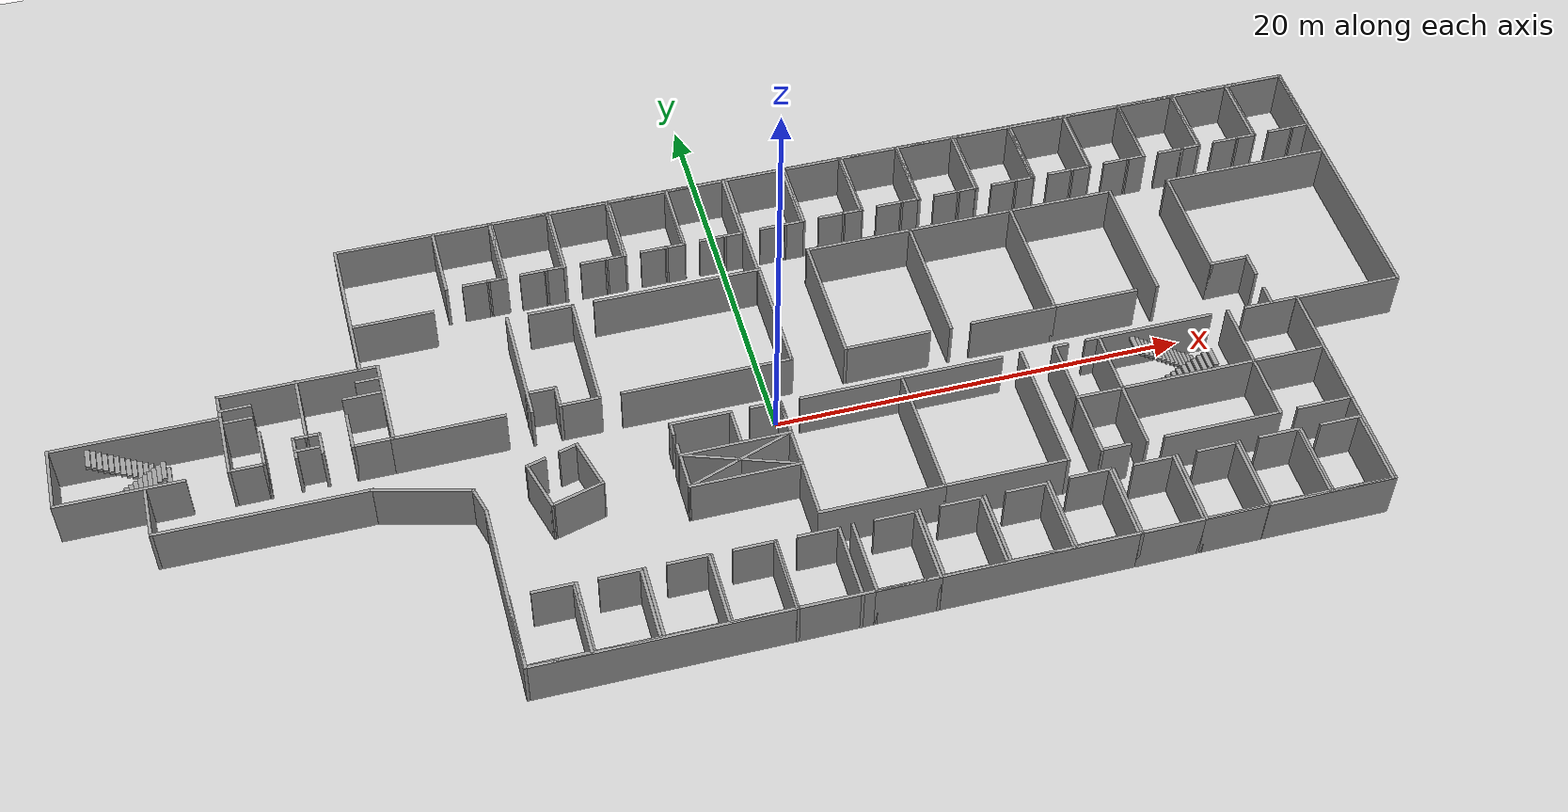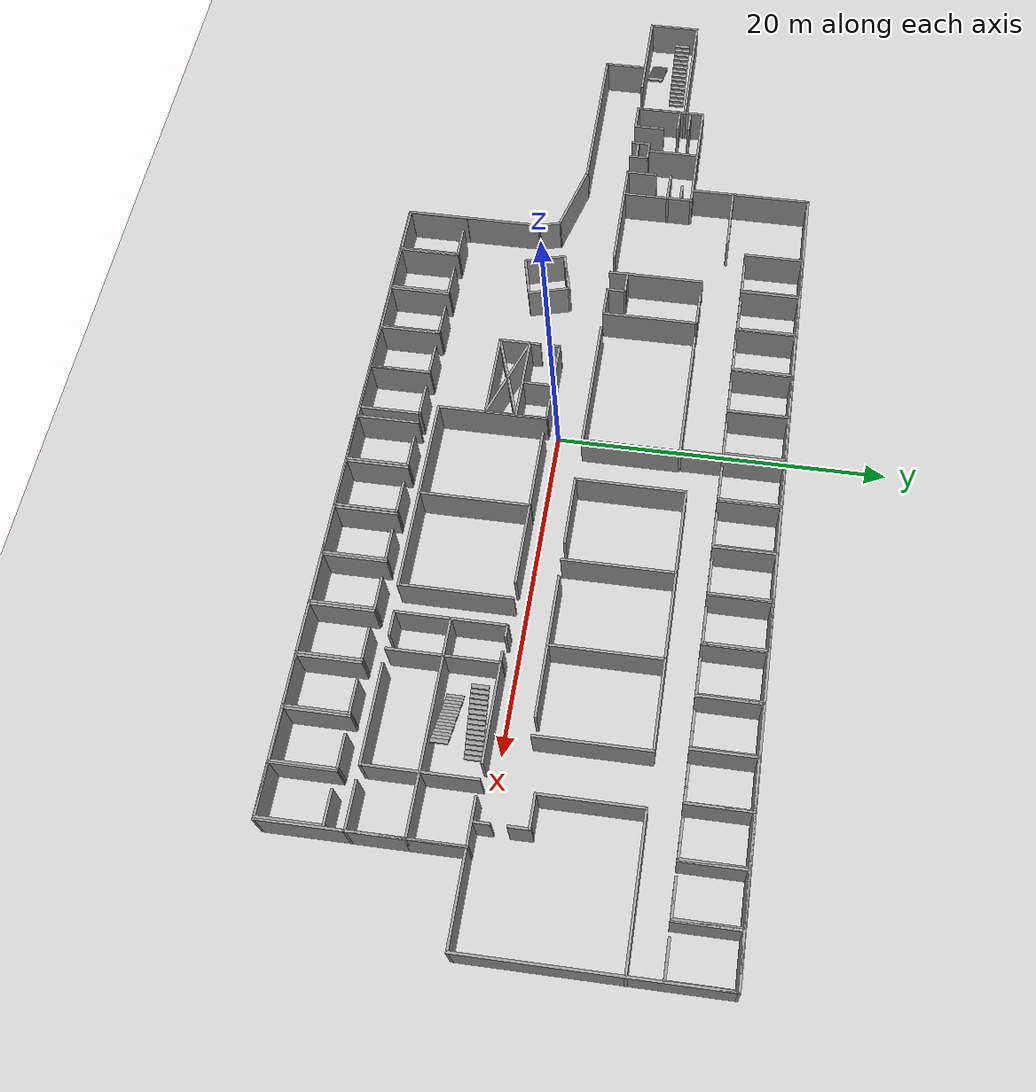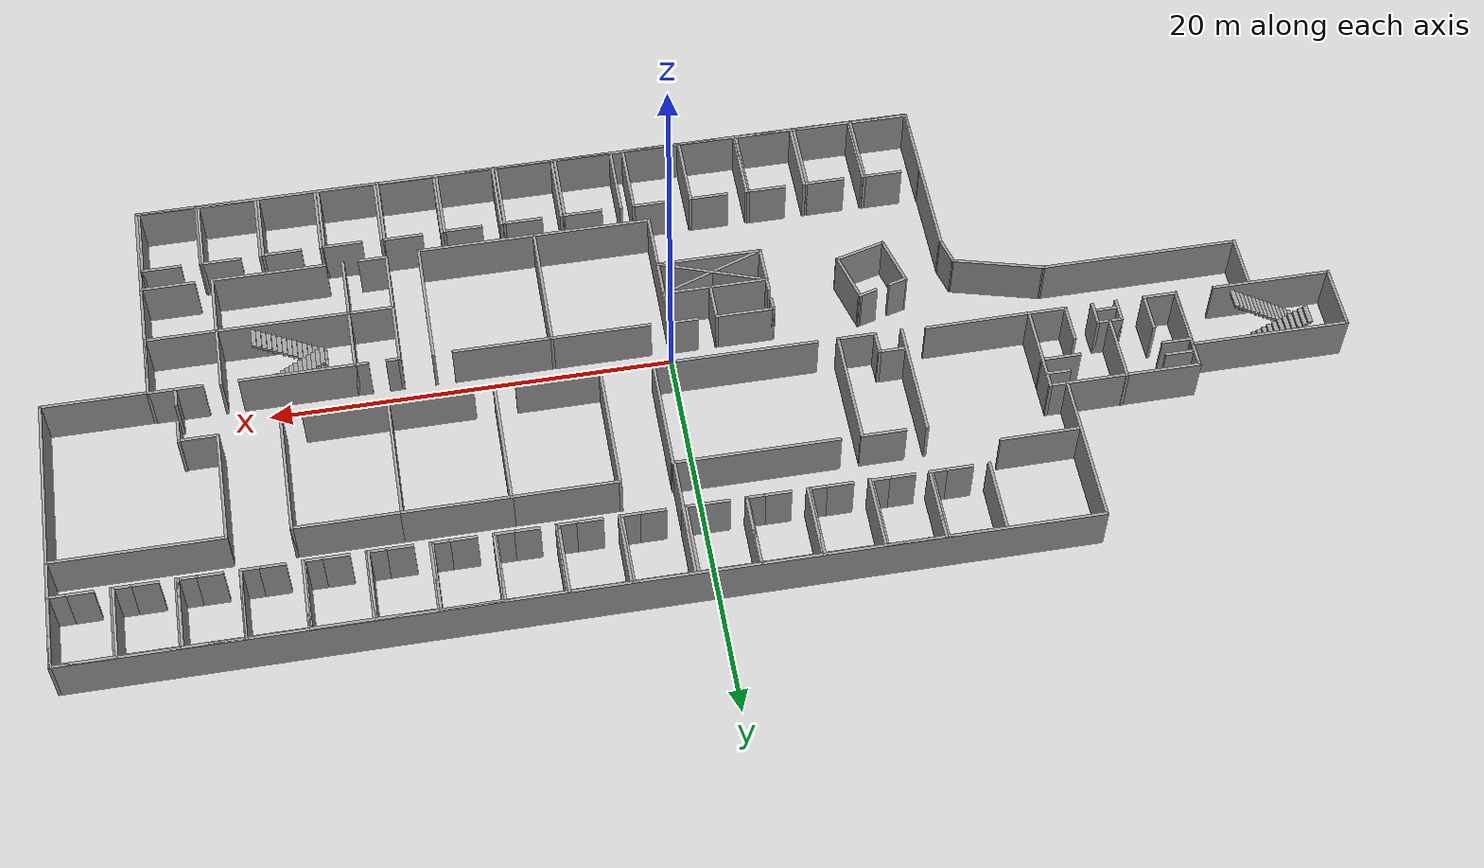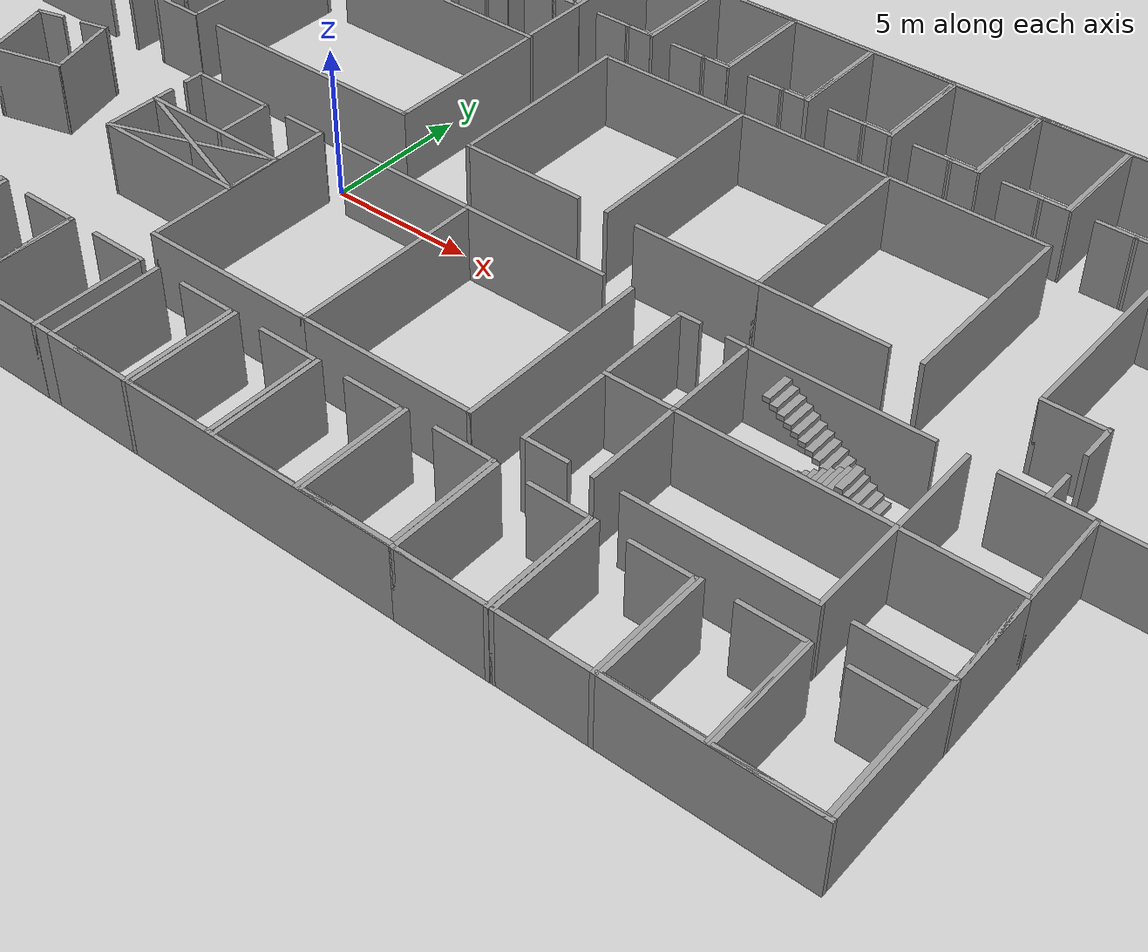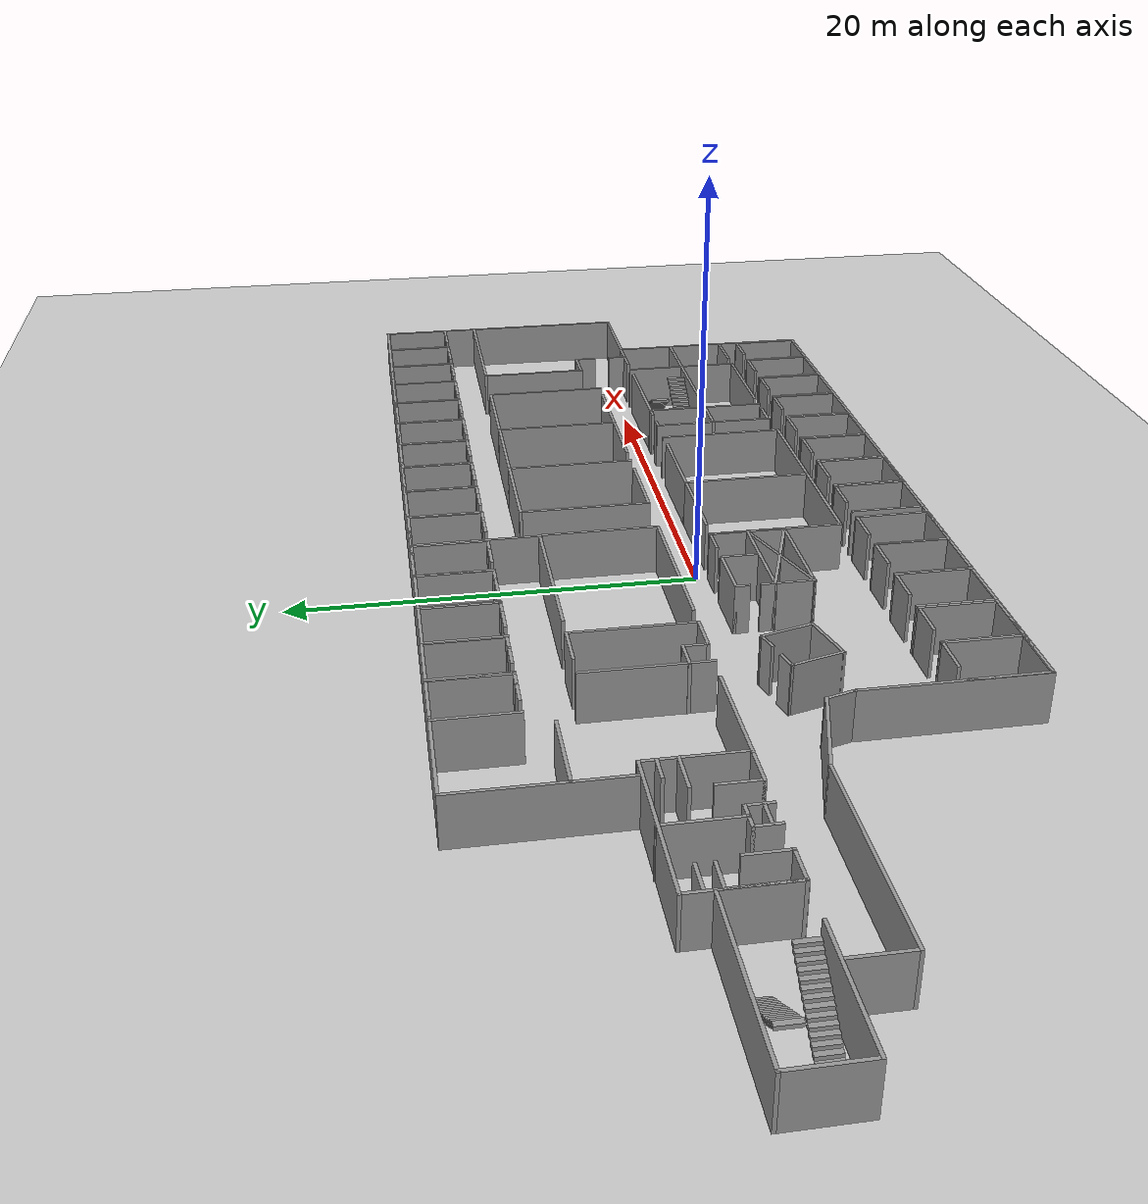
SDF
<sdf version="1.6">
 <world name="default">
  <light name="sun" type="directional">
   <pose>0 0 10 0 -0 0</pose>
   <diffuse>0.8 0.8 0.8 1</diffuse>
   <specular>0.2 0.2 0.2 1</specular>
   <attenuation>
    <range>1000</range>
    <constant>0.9</constant>
    <linear>0.01</linear>
    <quadratic>0.001</quadratic>
   </attenuation>
   <direction>-0.5 0.1 -0.9</direction>
  </light>
  <model name="ground_plane">
   <static>1</static>
   <link name="link">
    <collision name="collision">
     <geometry><plane><normal>0 0 1</normal><size>100 100</size></plane></geometry>
     <surface><friction><ode><mu>100</mu><mu2>50</mu2></ode></friction></surface>
    </collision>
    <visual name="visual">
     <cast_shadows>0</cast_shadows>
     <geometry><plane><normal>0 0 1</normal><size>100 100</size></plane></geometry>
     <material>
      <script><uri>file://media/materials/scripts/gazebo.material</uri><name>Gazebo/Grey</name></script>
     </material>
    </visual>
   </link>
  </model>
  <gravity>0 0 -9.8</gravity>
  <magnetic_field>6e-06 2.3e-05 -4.2e-05</magnetic_field>
  <atmosphere type="adiabatic"/>
  <physics name="default_physics" default="0" type="ode">
   <max_step_size>0.001</max_step_size>
   <real_time_factor>1</real_time_factor>
   <real_time_update_rate>1000</real_time_update_rate>
  </physics>
  <scene><ambient>0.4 0.4 0.4 1</ambient><background>0.7 0.7 0.7 1</background><shadows>1</shadows></scene>
  <spherical_coordinates>
   <surface_model>EARTH_WGS84</surface_model>
   <latitude_deg>0</latitude_deg>
   <longitude_deg>0</longitude_deg>
   <elevation>0</elevation>
   <heading_deg>0</heading_deg>
  </spherical_coordinates>
  <model name="201/202">
   <pose>-21.3391 4.00533 0 0 -0 0</pose>
   <link name="Wall_10">
    <collision name="Wall_10_Collision">
     <geometry><box><size>7.62002 0.15 2.5</size></box></geometry>
     <pose>0 0 1.25 0 -0 0</pose>
    </collision>
    <visual name="Wall_10_Visual">
     <pose>0 0 1.25 0 -0 0</pose>
     <geometry><box><size>7.62002 0.15 2.5</size></box></geometry>
     <material>
      <script><uri>file://media/materials/scripts/gazebo.material</uri><name>Gazebo/Grey</name></script>
      <ambient>1 1 1 1</ambient>
     </material>
     <meta><layer>0</layer></meta>
    </visual>
    <pose>-0.004655 2.1906 0 0 -0 3.14159</pose>
   </link>
   <link name="Wall_11">
    <collision name="Wall_11_Collision">
     <geometry><box><size>4.572 0.15 2.5</size></box></geometry>
     <pose>0 0 1.25 0 -0 0</pose>
    </collision>
    <visual name="Wall_11_Visual">
     <pose>0 0 1.25 0 -0 0</pose>
     <geometry><box><size>4.572 0.15 2.5</size></box></geometry>
     <material>
      <script><uri>file://media/materials/scripts/gazebo.material</uri><name>Gazebo/Grey</name></script>
      <ambient>1 1 1 1</ambient>
     </material>
     <meta><layer>0</layer></meta>
    </visual>
    <pose>-3.73965 -0.020398 0 0 -0 -1.5708</pose>
   </link>
   <link name="Wall_13">
    <collision name="Wall_13_Collision">
     <geometry><box><size>2 0.15 2.5</size></box></geometry>
     <pose>0 0 1.25 0 -0 0</pose>
    </collision>
    <visual name="Wall_13_Visual">
     <pose>0 0 1.25 0 -0 0</pose>
     <geometry><box><size>2 0.15 2.5</size></box></geometry>
     <material>
      <script><uri>file://media/materials/scripts/gazebo.material</uri><name>Gazebo/Grey</name></script>
      <ambient>1 1 1 1</ambient>
     </material>
     <meta><layer>0</layer></meta>
    </visual>
    <pose>2.80535 -2.23095 0 0 -0 3.14159</pose>
   </link>
   <link name="Wall_14">
    <collision name="Wall_14_Collision">
     <geometry><box><size>2 0.15 2.5</size></box></geometry>
     <pose>0 0 1.25 0 -0 0</pose>
    </collision>
    <visual name="Wall_14_Visual">
     <pose>0 0 1.25 0 -0 0</pose>
     <geometry><box><size>2 0.15 2.5</size></box></geometry>
     <material>
      <script><uri>file://media/materials/scripts/gazebo.material</uri><name>Gazebo/Grey</name></script>
      <ambient>1 1 1 1</ambient>
     </material>
     <meta><layer>0</layer></meta>
    </visual>
    <pose>1.88035 -1.30595 0 0 -0 1.5708</pose>
   </link>
   <link name="Wall_16">
    <collision name="Wall_16_Collision">
     <geometry><box><size>3.5 0.15 2.5</size></box></geometry>
     <pose>0 0 1.25 0 -0 0</pose>
    </collision>
    <visual name="Wall_16_Visual">
     <pose>0 0 1.25 0 -0 0</pose>
     <geometry><box><size>3.5 0.15 2.5</size></box></geometry>
     <material>
      <script><uri>file://media/materials/scripts/gazebo.material</uri><name>Gazebo/Grey</name></script>
      <ambient>1 1 1 1</ambient>
     </material>
     <meta><layer>0</layer></meta>
    </visual>
    <pose>-0.091763 0.556398 0 0 -0 -1.5708</pose>
   </link>
   <link name="Wall_17">
    <collision name="Wall_17_Collision">
     <geometry><box><size>0.75 0.15 2.5</size></box></geometry>
     <pose>0 0 1.25 0 -0 0</pose>
    </collision>
    <visual name="Wall_17_Visual">
     <pose>0 0 1.25 0 -0 0</pose>
     <geometry><box><size>0.75 0.15 2.5</size></box></geometry>
     <material>
      <script><uri>file://media/materials/scripts/gazebo.material</uri><name>Gazebo/Grey</name></script>
      <ambient>1 1 1 1</ambient>
     </material>
     <meta><layer>0</layer></meta>
    </visual>
    <pose>0.208236 -1.1186 0 0 -0 0</pose>
   </link>
   <link name="Wall_18">
    <collision name="Wall_18_Collision">
     <geometry><box><size>1.25 0.15 2.5</size></box></geometry>
     <pose>0 0 1.25 0 -0 0</pose>
    </collision>
    <visual name="Wall_18_Visual">
     <pose>0 0 1.25 0 -0 0</pose>
     <geometry><box><size>1.25 0.15 2.5</size></box></geometry>
     <material>
      <script><uri>file://media/materials/scripts/gazebo.material</uri><name>Gazebo/Grey</name></script>
      <ambient>1 1 1 1</ambient>
     </material>
     <meta><layer>0</layer></meta>
    </visual>
    <pose>0.508237 -1.6686 0 0 -0 -1.5708</pose>
   </link>
   <link name="Wall_20">
    <collision name="Wall_20_Collision">
     <geometry><box><size>0.75 0.15 2.5</size></box></geometry>
     <pose>0 0 1.25 0 -0 0</pose>
    </collision>
    <visual name="Wall_20_Visual">
     <pose>0 0 1.25 0 -0 0</pose>
     <geometry><box><size>0.75 0.15 2.5</size></box></geometry>
     <material>
      <script><uri>file://media/materials/scripts/gazebo.material</uri><name>Gazebo/Grey</name></script>
      <ambient>1 1 1 1</ambient>
     </material>
     <meta><layer>0</layer></meta>
    </visual>
    <pose>-0.391763 -1.1186 0 0 -0 3.14159</pose>
   </link>
   <link name="Wall_21">
    <collision name="Wall_21_Collision">
     <geometry><box><size>1.25 0.15 2.5</size></box></geometry>
     <pose>0 0 1.25 0 -0 0</pose>
    </collision>
    <visual name="Wall_21_Visual">
     <pose>0 0 1.25 0 -0 0</pose>
     <geometry><box><size>1.25 0.15 2.5</size></box></geometry>
     <material>
      <script><uri>file://media/materials/scripts/gazebo.material</uri><name>Gazebo/Grey</name></script>
      <ambient>1 1 1 1</ambient>
     </material>
     <meta><layer>0</layer></meta>
    </visual>
    <pose>-0.691764 -1.6686 0 0 -0 -1.5708</pose>
   </link>
   <link name="Wall_23">
    <collision name="Wall_23_Collision">
     <geometry><box><size>1.75 0.15 2.5</size></box></geometry>
     <pose>0 0 1.25 0 -0 0</pose>
    </collision>
    <visual name="Wall_23_Visual">
     <pose>0 0 1.25 0 -0 0</pose>
     <geometry><box><size>1.75 0.15 2.5</size></box></geometry>
     <material>
      <script><uri>file://media/materials/scripts/gazebo.material</uri><name>Gazebo/Grey</name></script>
      <ambient>1 1 1 1</ambient>
     </material>
     <meta><layer>0</layer></meta>
    </visual>
    <pose>-2.93966 -2.2314 0 0 -0 0</pose>
   </link>
   <link name="Wall_24">
    <collision name="Wall_24_Collision">
     <geometry><box><size>2 0.15 2.5</size></box></geometry>
     <pose>0 0 1.25 0 -0 0</pose>
    </collision>
    <visual name="Wall_24_Visual">
     <pose>0 0 1.25 0 -0 0</pose>
     <geometry><box><size>2 0.15 2.5</size></box></geometry>
     <material>
      <script><uri>file://media/materials/scripts/gazebo.material</uri><name>Gazebo/Grey</name></script>
      <ambient>1 1 1 1</ambient>
     </material>
     <meta><layer>0</layer></meta>
    </visual>
    <pose>-2.13965 -1.3064 0 0 -0 1.5708</pose>
   </link>
   <link name="Wall_28">
    <collision name="Wall_28_Collision">
     <geometry><box><size>1.5 0.15 2.5</size></box></geometry>
     <pose>0 0 1.25 0 -0 0</pose>
    </collision>
    <visual name="Wall_28_Visual">
     <pose>0 0 1.25 0 -0 0</pose>
     <geometry><box><size>1.5 0.15 2.5</size></box></geometry>
     <material>
      <script><uri>file://media/materials/scripts/gazebo.material</uri><name>Gazebo/Grey</name></script>
      <ambient>1 1 1 1</ambient>
     </material>
     <meta><layer>0</layer></meta>
    </visual>
    <pose>-3.01876 1.34811 0 0 -0 0</pose>
   </link>
   <link name="Wall_30">
    <collision name="Wall_30_Collision">
     <geometry><box><size>1.5 0.15 2.5</size></box></geometry>
     <pose>0 0 1.25 0 -0 0</pose>
    </collision>
    <visual name="Wall_30_Visual">
     <pose>0 0 1.25 0 -0 0</pose>
     <geometry><box><size>1.5 0.15 2.5</size></box></geometry>
     <material>
      <script><uri>file://media/materials/scripts/gazebo.material</uri><name>Gazebo/Grey</name></script>
      <ambient>1 1 1 1</ambient>
     </material>
     <meta><layer>0</layer></meta>
    </visual>
    <pose>-3.03023 0.625411 0 0 -0 0</pose>
   </link>
   <link name="Wall_32">
    <collision name="Wall_32_Collision">
     <geometry><box><size>2 0.15 2.5</size></box></geometry>
     <pose>0 0 1.25 0 -0 0</pose>
    </collision>
    <visual name="Wall_32_Visual">
     <pose>0 0 1.25 0 -0 0</pose>
     <geometry><box><size>2 0.15 2.5</size></box></geometry>
     <material>
      <script><uri>file://media/materials/scripts/gazebo.material</uri><name>Gazebo/Grey</name></script>
      <ambient>1 1 1 1</ambient>
     </material>
     <meta><layer>0</layer></meta>
    </visual>
    <pose>2.81466 0.625411 0 0 -0 3.14159</pose>
   </link>
   <link name="Wall_34">
    <collision name="Wall_34_Collision">
     <geometry><box><size>1.25 0.15 2.5</size></box></geometry>
     <pose>0 0 1.25 0 -0 0</pose>
    </collision>
    <visual name="Wall_34_Visual">
     <pose>0 0 1.25 0 -0 0</pose>
     <geometry><box><size>1.25 0.15 2.5</size></box></geometry>
     <material>
      <script><uri>file://media/materials/scripts/gazebo.material</uri><name>Gazebo/Grey</name></script>
      <ambient>1 1 1 1</ambient>
     </material>
     <meta><layer>0</layer></meta>
    </visual>
    <pose>3.16672 1.48576 0 0 -0 3.14159</pose>
   </link>
   <link name="Wall_36">
    <collision name="Wall_36_Collision">
     <geometry><box><size>1.25 0.15 2.5</size></box></geometry>
     <pose>0 0 1.25 0 -0 0</pose>
    </collision>
    <visual name="Wall_36_Visual">
     <pose>0 0 1.25 0 -0 0</pose>
     <geometry><box><size>1.25 0.15 2.5</size></box></geometry>
     <material>
      <script><uri>file://media/materials/scripts/gazebo.material</uri><name>Gazebo/Grey</name></script>
      <ambient>1 1 1 1</ambient>
     </material>
     <meta><layer>0</layer></meta>
    </visual>
    <pose>-0.138273 -1.8524 0 0 -0 0</pose>
   </link>
   <link name="Wall_9">
    <collision name="Wall_9_Collision">
     <geometry><box><size>4.572 0.15 2.5</size></box></geometry>
     <pose>0 0 1.25 0 -0 0</pose>
    </collision>
    <visual name="Wall_9_Visual">
     <pose>0 0 1.25 0 -0 0</pose>
     <geometry><box><size>4.572 0.15 2.5</size></box></geometry>
     <material>
      <script><uri>file://media/materials/scripts/gazebo.material</uri><name>Gazebo/Grey</name></script>
      <ambient>1 1 1 1</ambient>
     </material>
     <meta><layer>0</layer></meta>
    </visual>
    <pose>3.73035 -0.020175 0 0 -0 1.5708</pose>
   </link>
   <static>1</static>
  </model>
  <model name="EEFloor4">
   <link name="Wall_0">
    <pose>-19.3918 9.08232 0 0 -0 1.5708</pose>
    <inertial>
     <inertia><ixx>0</ixx><ixy>0</ixy><ixz>0</ixz><iyy>0</iyy><iyz>0</iyz><izz>0</izz></inertia>
     <mass>0</mass>
    </inertial>
    <visual name="Wall_0_Visual">
     <pose>0 0 1.25 0 -0 0</pose>
     <geometry><box><size>7.65575 0.15 2.5</size></box></geometry>
     <material>
      <script><uri>file://media/materials/scripts/gazebo.material</uri><name>Gazebo/Grey</name></script>
      <ambient>1 1 1 1</ambient>
      <shader type="pixel"/>
     </material>
     <meta><layer>0</layer></meta>
    </visual>
    <collision name="Wall_0_Collision">
     <pose>0 0 1.25 0 -0 0</pose>
     <geometry><box><size>7.65575 0.15 2.5</size></box></geometry>
     <surface>
      <friction>
       <ode><mu>1</mu><mu2>1</mu2><fdir1>0 0 0</fdir1><slip1>0</slip1><slip2>0</slip2></ode>
       <torsional>
        <coefficient>1</coefficient>
        <patch_radius>0</patch_radius>
        <surface_radius>0</surface_radius>
        <use_patch_radius>1</use_patch_radius>
        <ode><slip>0</slip></ode>
       </torsional>
      </friction>
      <bounce><restitution_coefficient>0</restitution_coefficient><threshold>1e+06</threshold></bounce>
      <contact>
       <collide_without_contact>0</collide_without_contact>
       <collide_without_contact_bitmask>1</collide_without_contact_bitmask>
       <collide_bitmask>1</collide_bitmask>
       <ode>
        <soft_cfm>0</soft_cfm>
        <soft_erp>0.2</soft_erp>
        <kp>1e+13</kp>
        <kd>1</kd>
        <max_vel>0.01</max_vel>
        <min_depth>0</min_depth>
       </ode>
       <bullet>
        <split_impulse>1</split_impulse>
        <split_impulse_penetration_threshold>-0.01</split_impulse_penetration_threshold>
        <soft_cfm>0</soft_cfm>
        <soft_erp>0.2</soft_erp>
        <kp>1e+13</kp>
        <kd>1</kd>
       </bullet>
      </contact>
     </surface>
    </collision>
   </link>
   <link name="Wall_1">
    <pose>5.20325 12.852 0 0 -0 0</pose>
    <visual name="Wall_1_Visual">
     <pose>0 0 1.25 0 -0 0</pose>
     <geometry><box><size>49.34 0.15 2.5</size></box></geometry>
     <material>
      <script><uri>file://media/materials/scripts/gazebo.material</uri><name>Gazebo/Grey</name></script>
      <ambient>1 1 1 1</ambient>
      <shader type="pixel"/>
     </material>
     <meta><layer>0</layer></meta>
    </visual>
    <collision name="Wall_1_Collision">
     <pose>0 0 1.25 0 -0 0</pose>
     <geometry><box><size>49.34 0.15 2.5</size></box></geometry>
     <surface>
      <friction>
       <ode><mu>1</mu><mu2>1</mu2><fdir1>0 0 0</fdir1><slip1>0</slip1><slip2>0</slip2></ode>
       <torsional>
        <coefficient>1</coefficient>
        <patch_radius>0</patch_radius>
        <surface_radius>0</surface_radius>
        <use_patch_radius>1</use_patch_radius>
        <ode><slip>0</slip></ode>
       </torsional>
      </friction>
      <bounce><restitution_coefficient>0</restitution_coefficient><threshold>1e+06</threshold></bounce>
      <contact>
       <collide_without_contact>0</collide_without_contact>
       <collide_without_contact_bitmask>1</collide_without_contact_bitmask>
       <collide_bitmask>1</collide_bitmask>
       <ode>
        <soft_cfm>0</soft_cfm>
        <soft_erp>0.2</soft_erp>
        <kp>1e+13</kp>
        <kd>1</kd>
        <max_vel>0.01</max_vel>
        <min_depth>0</min_depth>
       </ode>
       <bullet>
        <split_impulse>1</split_impulse>
        <split_impulse_penetration_threshold>-0.01</split_impulse_penetration_threshold>
        <soft_cfm>0</soft_cfm>
        <soft_erp>0.2</soft_erp>
        <kp>1e+13</kp>
        <kd>1</kd>
       </bullet>
      </contact>
     </surface>
    </collision>
   </link>
   <link name="Wall_10">
    <pose>-29.7982 -0.602414 0 0 -0 1.5708</pose>
    <visual name="Wall_10_Visual">
     <pose>0 0 1.25 0 -0 0</pose>
     <geometry><box><size>2.667 0.15 2.5</size></box></geometry>
     <material>
      <script><uri>file://media/materials/scripts/gazebo.material</uri><name>Gazebo/Grey</name></script>
      <ambient>1 1 1 1</ambient>
      <shader type="pixel"/>
     </material>
     <meta><layer>0</layer></meta>
    </visual>
    <collision name="Wall_10_Collision">
     <pose>0 0 1.25 0 -0 0</pose>
     <geometry><box><size>2.667 0.15 2.5</size></box></geometry>
     <surface>
      <friction>
       <ode><mu>1</mu><mu2>1</mu2><fdir1>0 0 0</fdir1><slip1>0</slip1><slip2>0</slip2></ode>
       <torsional>
        <coefficient>1</coefficient>
        <patch_radius>0</patch_radius>
        <surface_radius>0</surface_radius>
        <use_patch_radius>1</use_patch_radius>
        <ode><slip>0</slip></ode>
       </torsional>
      </friction>
      <bounce><restitution_coefficient>0</restitution_coefficient><threshold>1e+06</threshold></bounce>
      <contact>
       <collide_without_contact>0</collide_without_contact>
       <collide_without_contact_bitmask>1</collide_without_contact_bitmask>
       <collide_bitmask>1</collide_bitmask>
       <ode>
        <soft_cfm>0</soft_cfm>
        <soft_erp>0.2</soft_erp>
        <kp>1e+13</kp>
        <kd>1</kd>
        <max_vel>0.01</max_vel>
        <min_depth>0</min_depth>
       </ode>
       <bullet>
        <split_impulse>1</split_impulse>
        <split_impulse_penetration_threshold>-0.01</split_impulse_penetration_threshold>
        <soft_cfm>0</soft_cfm>
        <soft_erp>0.2</soft_erp>
        <kp>1e+13</kp>
        <kd>1</kd>
       </bullet>
      </contact>
     </surface>
    </collision>
   </link>
   <link name="Wall_2">
    <pose>29.7982 5.5925 0 0 0 -1.5708</pose>
    <visual name="Wall_2_Visual">
     <pose>0 0 1.25 0 -0 0</pose>
     <geometry><box><size>14.669 0.15 2.5</size></box></geometry>
     <material>
      <script><uri>file://media/materials/scripts/gazebo.material</uri><name>Gazebo/Grey</name></script>
      <ambient>1 1 1 1</ambient>
      <shader type="pixel"/>
     </material>
     <meta><layer>0</layer></meta>
    </visual>
    <collision name="Wall_2_Collision">
     <pose>0 0 1.25 0 -0 0</pose>
     <geometry><box><size>14.669 0.15 2.5</size></box></geometry>
     <surface>
      <friction>
       <ode><mu>1</mu><mu2>1</mu2><fdir1>0 0 0</fdir1><slip1>0</slip1><slip2>0</slip2></ode>
       <torsional>
        <coefficient>1</coefficient>
        <patch_radius>0</patch_radius>
        <surface_radius>0</surface_radius>
        <use_patch_radius>1</use_patch_radius>
        <ode><slip>0</slip></ode>
       </torsional>
      </friction>
      <bounce><restitution_coefficient>0</restitution_coefficient><threshold>1e+06</threshold></bounce>
      <contact>
       <collide_without_contact>0</collide_without_contact>
       <collide_without_contact_bitmask>1</collide_without_contact_bitmask>
       <collide_bitmask>1</collide_bitmask>
       <ode>
        <soft_cfm>0</soft_cfm>
        <soft_erp>0.2</soft_erp>
        <kp>1e+13</kp>
        <kd>1</kd>
        <max_vel>0.01</max_vel>
        <min_depth>0</min_depth>
       </ode>
       <bullet>
        <split_impulse>1</split_impulse>
        <split_impulse_penetration_threshold>-0.01</split_impulse_penetration_threshold>
        <soft_cfm>0</soft_cfm>
        <soft_erp>0.2</soft_erp>
        <kp>1e+13</kp>
        <kd>1</kd>
       </bullet>
      </contact>
     </surface>
    </collision>
   </link>
   <link name="Wall_3">
    <pose>27.2062 -1.667 0 0 -0 3.14159</pose>
    <visual name="Wall_3_Visual">
     <pose>0 0 1.25 0 -0 0</pose>
     <geometry><box><size>5.334 0.15 2.5</size></box></geometry>
     <material>
      <script><uri>file://media/materials/scripts/gazebo.material</uri><name>Gazebo/Grey</name></script>
      <ambient>1 1 1 1</ambient>
      <shader type="pixel"/>
     </material>
     <meta><layer>0</layer></meta>
    </visual>
    <collision name="Wall_3_Collision">
     <pose>0 0 1.25 0 -0 0</pose>
     <geometry><box><size>5.334 0.15 2.5</size></box></geometry>
     <surface>
      <friction>
       <ode><mu>1</mu><mu2>1</mu2><fdir1>0 0 0</fdir1><slip1>0</slip1><slip2>0</slip2></ode>
       <torsional>
        <coefficient>1</coefficient>
        <patch_radius>0</patch_radius>
        <surface_radius>0</surface_radius>
        <use_patch_radius>1</use_patch_radius>
        <ode><slip>0</slip></ode>
       </torsional>
      </friction>
      <bounce><restitution_coefficient>0</restitution_coefficient><threshold>1e+06</threshold></bounce>
      <contact>
       <collide_without_contact>0</collide_without_contact>
       <collide_without_contact_bitmask>1</collide_without_contact_bitmask>
       <collide_bitmask>1</collide_bitmask>
       <ode>
        <soft_cfm>0</soft_cfm>
        <soft_erp>0.2</soft_erp>
        <kp>1e+13</kp>
        <kd>1</kd>
        <max_vel>0.01</max_vel>
        <min_depth>0</min_depth>
       </ode>
       <bullet>
        <split_impulse>1</split_impulse>
        <split_impulse_penetration_threshold>-0.01</split_impulse_penetration_threshold>
        <soft_cfm>0</soft_cfm>
        <soft_erp>0.2</soft_erp>
        <kp>1e+13</kp>
        <kd>1</kd>
       </bullet>
      </contact>
     </surface>
    </collision>
   </link>
   <link name="Wall_4">
    <pose>24.6142 -7.2595 0 0 0 -1.5708</pose>
    <visual name="Wall_4_Visual">
     <pose>0 0 1.25 0 -0 0</pose>
     <geometry><box><size>11.335 0.15 2.5</size></box></geometry>
     <material>
      <script><uri>file://media/materials/scripts/gazebo.material</uri><name>Gazebo/Grey</name></script>
      <ambient>1 1 1 1</ambient>
      <shader type="pixel"/>
     </material>
     <meta><layer>0</layer></meta>
    </visual>
    <collision name="Wall_4_Collision">
     <pose>0 0 1.25 0 -0 0</pose>
     <geometry><box><size>11.335 0.15 2.5</size></box></geometry>
     <surface>
      <friction>
       <ode><mu>1</mu><mu2>1</mu2><fdir1>0 0 0</fdir1><slip1>0</slip1><slip2>0</slip2></ode>
       <torsional>
        <coefficient>1</coefficient>
        <patch_radius>0</patch_radius>
        <surface_radius>0</surface_radius>
        <use_patch_radius>1</use_patch_radius>
        <ode><slip>0</slip></ode>
       </torsional>
      </friction>
      <bounce><restitution_coefficient>0</restitution_coefficient><threshold>1e+06</threshold></bounce>
      <contact>
       <collide_without_contact>0</collide_without_contact>
       <collide_without_contact_bitmask>1</collide_without_contact_bitmask>
       <collide_bitmask>1</collide_bitmask>
       <ode>
        <soft_cfm>0</soft_cfm>
        <soft_erp>0.2</soft_erp>
        <kp>1e+13</kp>
        <kd>1</kd>
        <max_vel>0.01</max_vel>
        <min_depth>0</min_depth>
       </ode>
       <bullet>
        <split_impulse>1</split_impulse>
        <split_impulse_penetration_threshold>-0.01</split_impulse_penetration_threshold>
        <soft_cfm>0</soft_cfm>
        <soft_erp>0.2</soft_erp>
        <kp>1e+13</kp>
        <kd>1</kd>
       </bullet>
      </contact>
     </surface>
    </collision>
   </link>
   <link name="Wall_5">
    <pose>4.68925 -12.852 0 0 -0 3.14159</pose>
    <visual name="Wall_5_Visual">
     <pose>0 0 1.25 0 -0 0</pose>
     <geometry><box><size>40 0.15 2.5</size></box></geometry>
     <material>
      <script><uri>file://media/materials/scripts/gazebo.material</uri><name>Gazebo/Grey</name></script>
      <ambient>1 1 1 1</ambient>
      <shader type="pixel"/>
     </material>
     <meta><layer>0</layer></meta>
    </visual>
    <collision name="Wall_5_Collision">
     <pose>0 0 1.25 0 -0 0</pose>
     <geometry><box><size>40 0.15 2.5</size></box></geometry>
     <surface>
      <friction>
       <ode><mu>1</mu><mu2>1</mu2><fdir1>0 0 0</fdir1><slip1>0</slip1><slip2>0</slip2></ode>
       <torsional>
        <coefficient>1</coefficient>
        <patch_radius>0</patch_radius>
        <surface_radius>0</surface_radius>
        <use_patch_radius>1</use_patch_radius>
        <ode><slip>0</slip></ode>
       </torsional>
      </friction>
      <bounce><restitution_coefficient>0</restitution_coefficient><threshold>1e+06</threshold></bounce>
      <contact>
       <collide_without_contact>0</collide_without_contact>
       <collide_without_contact_bitmask>1</collide_without_contact_bitmask>
       <collide_bitmask>1</collide_bitmask>
       <ode>
        <soft_cfm>0</soft_cfm>
        <soft_erp>0.2</soft_erp>
        <kp>1e+13</kp>
        <kd>1</kd>
        <max_vel>0.01</max_vel>
        <min_depth>0</min_depth>
       </ode>
       <bullet>
        <split_impulse>1</split_impulse>
        <split_impulse_penetration_threshold>-0.01</split_impulse_penetration_threshold>
        <soft_cfm>0</soft_cfm>
        <soft_erp>0.2</soft_erp>
        <kp>1e+13</kp>
        <kd>1</kd>
       </bullet>
      </contact>
     </surface>
    </collision>
   </link>
   <link name="Wall_6">
    <pose>-15.2358 -8.593 0 0 -0 1.5708</pose>
    <visual name="Wall_6_Visual">
     <pose>0 0 1.25 0 -0 0</pose>
     <geometry><box><size>8.668 0.15 2.5</size></box></geometry>
     <material>
      <script><uri>file://media/materials/scripts/gazebo.material</uri><name>Gazebo/Grey</name></script>
      <ambient>1 1 1 1</ambient>
      <shader type="pixel"/>
     </material>
     <meta><layer>0</layer></meta>
    </visual>
    <collision name="Wall_6_Collision">
     <pose>0 0 1.25 0 -0 0</pose>
     <geometry><box><size>8.668 0.15 2.5</size></box></geometry>
     <surface>
      <friction>
       <ode><mu>1</mu><mu2>1</mu2><fdir1>0 0 0</fdir1><slip1>0</slip1><slip2>0</slip2></ode>
       <torsional>
        <coefficient>1</coefficient>
        <patch_radius>0</patch_radius>
        <surface_radius>0</surface_radius>
        <use_patch_radius>1</use_patch_radius>
        <ode><slip>0</slip></ode>
       </torsional>
      </friction>
      <bounce><restitution_coefficient>0</restitution_coefficient><threshold>1e+06</threshold></bounce>
      <contact>
       <collide_without_contact>0</collide_without_contact>
       <collide_without_contact_bitmask>1</collide_without_contact_bitmask>
       <collide_bitmask>1</collide_bitmask>
       <ode>
        <soft_cfm>0</soft_cfm>
        <soft_erp>0.2</soft_erp>
        <kp>1e+13</kp>
        <kd>1</kd>
        <max_vel>0.01</max_vel>
        <min_depth>0</min_depth>
       </ode>
       <bullet>
        <split_impulse>1</split_impulse>
        <split_impulse_penetration_threshold>-0.01</split_impulse_penetration_threshold>
        <soft_cfm>0</soft_cfm>
        <soft_erp>0.2</soft_erp>
        <kp>1e+13</kp>
        <kd>1</kd>
       </bullet>
      </contact>
     </surface>
    </collision>
   </link>
   <link name="Wall_7">
    <pose>-15.4105 -3.682 0 0 -0 1.8326</pose>
    <visual name="Wall_7_Visual">
     <pose>0 0 1.25 0 -0 0</pose>
     <geometry><box><size>1.5 0.15 2.5</size></box></geometry>
     <material>
      <script><uri>file://media/materials/scripts/gazebo.material</uri><name>Gazebo/Grey</name></script>
      <ambient>1 1 1 1</ambient>
      <shader type="pixel"/>
     </material>
     <meta><layer>0</layer></meta>
    </visual>
    <collision name="Wall_7_Collision">
     <pose>0 0 1.25 0 -0 0</pose>
     <geometry><box><size>1.5 0.15 2.5</size></box></geometry>
     <surface>
      <friction>
       <ode><mu>1</mu><mu2>1</mu2><fdir1>0 0 0</fdir1><slip1>0</slip1><slip2>0</slip2></ode>
       <torsional>
        <coefficient>1</coefficient>
        <patch_radius>0</patch_radius>
        <surface_radius>0</surface_radius>
        <use_patch_radius>1</use_patch_radius>
        <ode><slip>0</slip></ode>
       </torsional>
      </friction>
      <bounce><restitution_coefficient>0</restitution_coefficient><threshold>1e+06</threshold></bounce>
      <contact>
       <collide_without_contact>0</collide_without_contact>
       <collide_without_contact_bitmask>1</collide_without_contact_bitmask>
       <collide_bitmask>1</collide_bitmask>
       <ode>
        <soft_cfm>0</soft_cfm>
        <soft_erp>0.2</soft_erp>
        <kp>1e+13</kp>
        <kd>1</kd>
        <max_vel>0.01</max_vel>
        <min_depth>0</min_depth>
       </ode>
       <bullet>
        <split_impulse>1</split_impulse>
        <split_impulse_penetration_threshold>-0.01</split_impulse_penetration_threshold>
        <soft_cfm>0</soft_cfm>
        <soft_erp>0.2</soft_erp>
        <kp>1e+13</kp>
        <kd>1</kd>
       </bullet>
      </contact>
     </surface>
    </collision>
   </link>
   <link name="Wall_8">
    <pose>-17.7667 -2.44546 0 0 -0 2.87979</pose>
    <visual name="Wall_8_Visual">
     <pose>0 0 1.25 0 -0 0</pose>
     <geometry><box><size>4.667 0.15 2.5</size></box></geometry>
     <material>
      <script><uri>file://media/materials/scripts/gazebo.material</uri><name>Gazebo/Grey</name></script>
      <ambient>1 1 1 1</ambient>
      <shader type="pixel"/>
     </material>
     <meta><layer>0</layer></meta>
    </visual>
    <collision name="Wall_8_Collision">
     <pose>0 0 1.25 0 -0 0</pose>
     <geometry><box><size>4.667 0.15 2.5</size></box></geometry>
     <surface>
      <friction>
       <ode><mu>1</mu><mu2>1</mu2><fdir1>0 0 0</fdir1><slip1>0</slip1><slip2>0</slip2></ode>
       <torsional>
        <coefficient>1</coefficient>
        <patch_radius>0</patch_radius>
        <surface_radius>0</surface_radius>
        <use_patch_radius>1</use_patch_radius>
        <ode><slip>0</slip></ode>
       </torsional>
      </friction>
      <bounce><restitution_coefficient>0</restitution_coefficient><threshold>1e+06</threshold></bounce>
      <contact>
       <collide_without_contact>0</collide_without_contact>
       <collide_without_contact_bitmask>1</collide_without_contact_bitmask>
       <collide_bitmask>1</collide_bitmask>
       <ode>
        <soft_cfm>0</soft_cfm>
        <soft_erp>0.2</soft_erp>
        <kp>1e+13</kp>
        <kd>1</kd>
        <max_vel>0.01</max_vel>
        <min_depth>0</min_depth>
       </ode>
       <bullet>
        <split_impulse>1</split_impulse>
        <split_impulse_penetration_threshold>-0.01</split_impulse_penetration_threshold>
        <soft_cfm>0</soft_cfm>
        <soft_erp>0.2</soft_erp>
        <kp>1e+13</kp>
        <kd>1</kd>
       </bullet>
      </contact>
     </surface>
    </collision>
   </link>
   <link name="Wall_9">
    <pose>-24.8732 -1.86091 0 0 -0 3.14159</pose>
    <visual name="Wall_9_Visual">
     <pose>0 0 1.25 0 -0 0</pose>
     <geometry><box><size>10 0.15 2.5</size></box></geometry>
     <material>
      <script><uri>file://media/materials/scripts/gazebo.material</uri><name>Gazebo/Grey</name></script>
      <ambient>1 1 1 1</ambient>
      <shader type="pixel"/>
     </material>
     <meta><layer>0</layer></meta>
    </visual>
    <collision name="Wall_9_Collision">
     <pose>0 0 1.25 0 -0 0</pose>
     <geometry><box><size>10 0.15 2.5</size></box></geometry>
     <surface>
      <friction>
       <ode><mu>1</mu><mu2>1</mu2><fdir1>0 0 0</fdir1><slip1>0</slip1><slip2>0</slip2></ode>
       <torsional>
        <coefficient>1</coefficient>
        <patch_radius>0</patch_radius>
        <surface_radius>0</surface_radius>
        <use_patch_radius>1</use_patch_radius>
        <ode><slip>0</slip></ode>
       </torsional>
      </friction>
      <bounce><restitution_coefficient>0</restitution_coefficient><threshold>1e+06</threshold></bounce>
      <contact>
       <collide_without_contact>0</collide_without_contact>
       <collide_without_contact_bitmask>1</collide_without_contact_bitmask>
       <collide_bitmask>1</collide_bitmask>
       <ode>
        <soft_cfm>0</soft_cfm>
        <soft_erp>0.2</soft_erp>
        <kp>1e+13</kp>
        <kd>1</kd>
        <max_vel>0.01</max_vel>
        <min_depth>0</min_depth>
       </ode>
       <bullet>
        <split_impulse>1</split_impulse>
        <split_impulse_penetration_threshold>-0.01</split_impulse_penetration_threshold>
        <soft_cfm>0</soft_cfm>
        <soft_erp>0.2</soft_erp>
        <kp>1e+13</kp>
        <kd>1</kd>
       </bullet>
      </contact>
     </surface>
    </collision>
   </link>
   <static>1</static>
   <pose>0.943488 0.961401 0 0 -0 0</pose>
  </model>
  <model name="313-325">
   <link name="Wall_16">
    <pose>-1.44915 7.1e-05 0 0 0 -1.57088</pose>
    <visual name="Wall_16_Visual">
     <pose>0 0 1.25 0 -0 0</pose>
     <geometry><box><size>3.81 0.15 2.5</size></box></geometry>
     <material>
      <script><uri>file://media/materials/scripts/gazebo.material</uri><name>Gazebo/Grey</name></script>
      <ambient>1 1 1 1</ambient>
      <shader type="pixel"/>
     </material>
     <meta><layer>0</layer></meta>
    </visual>
    <collision name="Wall_16_Collision">
     <pose>0 0 1.25 0 -0 0</pose>
     <geometry><box><size>3.81 0.15 2.5</size></box></geometry>
     <surface>
      <friction>
       <ode><mu>1</mu><mu2>1</mu2><fdir1>0 0 0</fdir1><slip1>0</slip1><slip2>0</slip2></ode>
       <torsional>
        <coefficient>1</coefficient>
        <patch_radius>0</patch_radius>
        <surface_radius>0</surface_radius>
        <use_patch_radius>1</use_patch_radius>
        <ode><slip>0</slip></ode>
       </torsional>
      </friction>
      <bounce><restitution_coefficient>0</restitution_coefficient><threshold>1e+06</threshold></bounce>
      <contact>
       <collide_without_contact>0</collide_without_contact>
       <collide_without_contact_bitmask>1</collide_without_contact_bitmask>
       <collide_bitmask>1</collide_bitmask>
       <ode>
        <soft_cfm>0</soft_cfm>
        <soft_erp>0.2</soft_erp>
        <kp>1e+13</kp>
        <kd>1</kd>
        <max_vel>0.01</max_vel>
        <min_depth>0</min_depth>
       </ode>
       <bullet>
        <split_impulse>1</split_impulse>
        <split_impulse_penetration_threshold>-0.01</split_impulse_penetration_threshold>
        <soft_cfm>0</soft_cfm>
        <soft_erp>0.2</soft_erp>
        <kp>1e+13</kp>
        <kd>1</kd>
       </bullet>
      </contact>
     </surface>
    </collision>
   </link>
   <link name="Wall_18">
    <pose>1.449 -6.1e-05 0 0 -0 1.5708</pose>
    <visual name="Wall_18_Visual">
     <pose>0 0 1.25 0 -0 0</pose>
     <geometry><box><size>3.80974 0.15 2.5</size></box></geometry>
     <material>
      <script><uri>file://media/materials/scripts/gazebo.material</uri><name>Gazebo/Grey</name></script>
      <ambient>1 1 1 1</ambient>
      <shader type="pixel"/>
     </material>
     <meta><layer>0</layer></meta>
    </visual>
    <collision name="Wall_18_Collision">
     <pose>0 0 1.25 0 -0 0</pose>
     <geometry><box><size>3.80974 0.15 2.5</size></box></geometry>
     <surface>
      <friction>
       <ode><mu>1</mu><mu2>1</mu2><fdir1>0 0 0</fdir1><slip1>0</slip1><slip2>0</slip2></ode>
       <torsional>
        <coefficient>1</coefficient>
        <patch_radius>0</patch_radius>
        <surface_radius>0</surface_radius>
        <use_patch_radius>1</use_patch_radius>
        <ode><slip>0</slip></ode>
       </torsional>
      </friction>
      <bounce><restitution_coefficient>0</restitution_coefficient><threshold>1e+06</threshold></bounce>
      <contact>
       <collide_without_contact>0</collide_without_contact>
       <collide_without_contact_bitmask>1</collide_without_contact_bitmask>
       <collide_bitmask>1</collide_bitmask>
       <ode>
        <soft_cfm>0</soft_cfm>
        <soft_erp>0.2</soft_erp>
        <kp>1e+13</kp>
        <kd>1</kd>
        <max_vel>0.01</max_vel>
        <min_depth>0</min_depth>
       </ode>
       <bullet>
        <split_impulse>1</split_impulse>
        <split_impulse_penetration_threshold>-0.01</split_impulse_penetration_threshold>
        <soft_cfm>0</soft_cfm>
        <soft_erp>0.2</soft_erp>
        <kp>1e+13</kp>
        <kd>1</kd>
       </bullet>
      </contact>
     </surface>
    </collision>
   </link>
   <link name="Wall_19">
    <pose>2e-06 1.82994 0 0 -0 3.14159</pose>
    <visual name="Wall_19_Visual">
     <pose>0 0 1.25 0 -0 0</pose>
     <geometry><box><size>3.04862 0.15 2.5</size></box></geometry>
     <material>
      <script><uri>file://media/materials/scripts/gazebo.material</uri><name>Gazebo/Grey</name></script>
      <ambient>1 1 1 1</ambient>
      <shader type="pixel"/>
     </material>
     <meta><layer>0</layer></meta>
    </visual>
    <collision name="Wall_19_Collision">
     <pose>0 0 1.25 0 -0 0</pose>
     <geometry><box><size>3.04862 0.15 2.5</size></box></geometry>
     <surface>
      <friction>
       <ode><mu>1</mu><mu2>1</mu2><fdir1>0 0 0</fdir1><slip1>0</slip1><slip2>0</slip2></ode>
       <torsional>
        <coefficient>1</coefficient>
        <patch_radius>0</patch_radius>
        <surface_radius>0</surface_radius>
        <use_patch_radius>1</use_patch_radius>
        <ode><slip>0</slip></ode>
       </torsional>
      </friction>
      <bounce><restitution_coefficient>0</restitution_coefficient><threshold>1e+06</threshold></bounce>
      <contact>
       <collide_without_contact>0</collide_without_contact>
       <collide_without_contact_bitmask>1</collide_without_contact_bitmask>
       <collide_bitmask>1</collide_bitmask>
       <ode>
        <soft_cfm>0</soft_cfm>
        <soft_erp>0.2</soft_erp>
        <kp>1e+13</kp>
        <kd>1</kd>
        <max_vel>0.01</max_vel>
        <min_depth>0</min_depth>
       </ode>
       <bullet>
        <split_impulse>1</split_impulse>
        <split_impulse_penetration_threshold>-0.01</split_impulse_penetration_threshold>
        <soft_cfm>0</soft_cfm>
        <soft_erp>0.2</soft_erp>
        <kp>1e+13</kp>
        <kd>1</kd>
       </bullet>
      </contact>
     </surface>
    </collision>
   </link>
   <link name="Wall_22">
    <pose>-0.000153 -1.82993 0 0 0 -0.00022</pose>
    <visual name="Wall_22_Visual">
     <pose>0 0 1.25 0 -0 0</pose>
     <geometry><box><size>1.34831 0.15 2.5</size></box></geometry>
     <material>
      <script><uri>file://media/materials/scripts/gazebo.material</uri><name>Gazebo/Grey</name></script>
      <ambient>1 1 1 1</ambient>
      <shader type="pixel"/>
     </material>
     <meta><layer>0</layer></meta>
    </visual>
    <collision name="Wall_22_Collision">
     <pose>0 0 1.25 0 -0 0</pose>
     <geometry><box><size>1.34831 0.15 2.5</size></box></geometry>
     <surface>
      <friction>
       <ode><mu>1</mu><mu2>1</mu2><fdir1>0 0 0</fdir1><slip1>0</slip1><slip2>0</slip2></ode>
       <torsional>
        <coefficient>1</coefficient>
        <patch_radius>0</patch_radius>
        <surface_radius>0</surface_radius>
        <use_patch_radius>1</use_patch_radius>
        <ode><slip>0</slip></ode>
       </torsional>
      </friction>
      <bounce><restitution_coefficient>0</restitution_coefficient><threshold>1e+06</threshold></bounce>
      <contact>
       <collide_without_contact>0</collide_without_contact>
       <collide_without_contact_bitmask>1</collide_without_contact_bitmask>
       <collide_bitmask>1</collide_bitmask>
       <ode>
        <soft_cfm>0</soft_cfm>
        <soft_erp>0.2</soft_erp>
        <kp>1e+13</kp>
        <kd>1</kd>
        <max_vel>0.01</max_vel>
        <min_depth>0</min_depth>
       </ode>
       <bullet>
        <split_impulse>1</split_impulse>
        <split_impulse_penetration_threshold>-0.01</split_impulse_penetration_threshold>
        <soft_cfm>0</soft_cfm>
        <soft_erp>0.2</soft_erp>
        <kp>1e+13</kp>
        <kd>1</kd>
       </bullet>
      </contact>
     </surface>
    </collision>
   </link>
   <link name="Wall_23">
    <pose>1.024 -1.83006 0 0 -0 0</pose>
    <visual name="Wall_23_Visual">
     <pose>0 0 1.25 0 -0 0</pose>
     <geometry><box><size>1 0.15 2.5</size></box></geometry>
     <material>
      <script><uri>file://media/materials/scripts/gazebo.material</uri><name>Gazebo/Grey</name></script>
      <ambient>1 1 1 1</ambient>
      <shader type="pixel"/>
     </material>
     <meta><layer>0</layer></meta>
    </visual>
    <collision name="Wall_23_Collision">
     <pose>0 0 1.25 0 -0 0</pose>
     <geometry><box><size>1 0.15 2.5</size></box></geometry>
     <surface>
      <friction>
       <ode><mu>1</mu><mu2>1</mu2><fdir1>0 0 0</fdir1><slip1>0</slip1><slip2>0</slip2></ode>
       <torsional>
        <coefficient>1</coefficient>
        <patch_radius>0</patch_radius>
        <surface_radius>0</surface_radius>
        <use_patch_radius>1</use_patch_radius>
        <ode><slip>0</slip></ode>
       </torsional>
      </friction>
      <bounce><restitution_coefficient>0</restitution_coefficient><threshold>1e+06</threshold></bounce>
      <contact>
       <collide_without_contact>0</collide_without_contact>
       <collide_without_contact_bitmask>1</collide_without_contact_bitmask>
       <collide_bitmask>1</collide_bitmask>
       <ode>
        <soft_cfm>0</soft_cfm>
        <soft_erp>0.2</soft_erp>
        <kp>1e+13</kp>
        <kd>1</kd>
        <max_vel>0.01</max_vel>
        <min_depth>0</min_depth>
       </ode>
       <bullet>
        <split_impulse>1</split_impulse>
        <split_impulse_penetration_threshold>-0.01</split_impulse_penetration_threshold>
        <soft_cfm>0</soft_cfm>
        <soft_erp>0.2</soft_erp>
        <kp>1e+13</kp>
        <kd>1</kd>
       </bullet>
      </contact>
     </surface>
    </collision>
   </link>
   <static>1</static>
   <pose>29.269 11.9553 0 0 -0 0</pose>
  </model>
  <model name="313-325_0">
   <link name="Wall_16">
    <pose>-1.44915 7.1e-05 0 0 0 -1.57088</pose>
    <visual name="Wall_16_Visual">
     <pose>0 0 1.25 0 -0 0</pose>
     <geometry><box><size>3.81 0.15 2.5</size></box></geometry>
     <material>
      <script><uri>file://media/materials/scripts/gazebo.material</uri><name>Gazebo/Grey</name></script>
      <ambient>1 1 1 1</ambient>
      <shader type="pixel"/>
     </material>
     <meta><layer>0</layer></meta>
    </visual>
    <collision name="Wall_16_Collision">
     <pose>0 0 1.25 0 -0 0</pose>
     <geometry><box><size>3.81 0.15 2.5</size></box></geometry>
     <surface>
      <friction>
       <ode><mu>1</mu><mu2>1</mu2><fdir1>0 0 0</fdir1><slip1>0</slip1><slip2>0</slip2></ode>
       <torsional>
        <coefficient>1</coefficient>
        <patch_radius>0</patch_radius>
        <surface_radius>0</surface_radius>
        <use_patch_radius>1</use_patch_radius>
        <ode><slip>0</slip></ode>
       </torsional>
      </friction>
      <bounce><restitution_coefficient>0</restitution_coefficient><threshold>1e+06</threshold></bounce>
      <contact>
       <collide_without_contact>0</collide_without_contact>
       <collide_without_contact_bitmask>1</collide_without_contact_bitmask>
       <collide_bitmask>1</collide_bitmask>
       <ode>
        <soft_cfm>0</soft_cfm>
        <soft_erp>0.2</soft_erp>
        <kp>1e+13</kp>
        <kd>1</kd>
        <max_vel>0.01</max_vel>
        <min_depth>0</min_depth>
       </ode>
       <bullet>
        <split_impulse>1</split_impulse>
        <split_impulse_penetration_threshold>-0.01</split_impulse_penetration_threshold>
        <soft_cfm>0</soft_cfm>
        <soft_erp>0.2</soft_erp>
        <kp>1e+13</kp>
        <kd>1</kd>
       </bullet>
      </contact>
     </surface>
    </collision>
   </link>
   <link name="Wall_18">
    <pose>1.449 -6.1e-05 0 0 -0 1.5708</pose>
    <visual name="Wall_18_Visual">
     <pose>0 0 1.25 0 -0 0</pose>
     <geometry><box><size>3.80974 0.15 2.5</size></box></geometry>
     <material>
      <script><uri>file://media/materials/scripts/gazebo.material</uri><name>Gazebo/Grey</name></script>
      <ambient>1 1 1 1</ambient>
      <shader type="pixel"/>
     </material>
     <meta><layer>0</layer></meta>
    </visual>
    <collision name="Wall_18_Collision">
     <pose>0 0 1.25 0 -0 0</pose>
     <geometry><box><size>3.80974 0.15 2.5</size></box></geometry>
     <surface>
      <friction>
       <ode><mu>1</mu><mu2>1</mu2><fdir1>0 0 0</fdir1><slip1>0</slip1><slip2>0</slip2></ode>
       <torsional>
        <coefficient>1</coefficient>
        <patch_radius>0</patch_radius>
        <surface_radius>0</surface_radius>
        <use_patch_radius>1</use_patch_radius>
        <ode><slip>0</slip></ode>
       </torsional>
      </friction>
      <bounce><restitution_coefficient>0</restitution_coefficient><threshold>1e+06</threshold></bounce>
      <contact>
       <collide_without_contact>0</collide_without_contact>
       <collide_without_contact_bitmask>1</collide_without_contact_bitmask>
       <collide_bitmask>1</collide_bitmask>
       <ode>
        <soft_cfm>0</soft_cfm>
        <soft_erp>0.2</soft_erp>
        <kp>1e+13</kp>
        <kd>1</kd>
        <max_vel>0.01</max_vel>
        <min_depth>0</min_depth>
       </ode>
       <bullet>
        <split_impulse>1</split_impulse>
        <split_impulse_penetration_threshold>-0.01</split_impulse_penetration_threshold>
        <soft_cfm>0</soft_cfm>
        <soft_erp>0.2</soft_erp>
        <kp>1e+13</kp>
        <kd>1</kd>
       </bullet>
      </contact>
     </surface>
    </collision>
   </link>
   <link name="Wall_19">
    <pose>2e-06 1.82994 0 0 -0 3.14159</pose>
    <visual name="Wall_19_Visual">
     <pose>0 0 1.25 0 -0 0</pose>
     <geometry><box><size>3.04862 0.15 2.5</size></box></geometry>
     <material>
      <script><uri>file://media/materials/scripts/gazebo.material</uri><name>Gazebo/Grey</name></script>
      <ambient>1 1 1 1</ambient>
      <shader type="pixel"/>
     </material>
     <meta><layer>0</layer></meta>
    </visual>
    <collision name="Wall_19_Collision">
     <pose>0 0 1.25 0 -0 0</pose>
     <geometry><box><size>3.04862 0.15 2.5</size></box></geometry>
     <surface>
      <friction>
       <ode><mu>1</mu><mu2>1</mu2><fdir1>0 0 0</fdir1><slip1>0</slip1><slip2>0</slip2></ode>
       <torsional>
        <coefficient>1</coefficient>
        <patch_radius>0</patch_radius>
        <surface_radius>0</surface_radius>
        <use_patch_radius>1</use_patch_radius>
        <ode><slip>0</slip></ode>
       </torsional>
      </friction>
      <bounce><restitution_coefficient>0</restitution_coefficient><threshold>1e+06</threshold></bounce>
      <contact>
       <collide_without_contact>0</collide_without_contact>
       <collide_without_contact_bitmask>1</collide_without_contact_bitmask>
       <collide_bitmask>1</collide_bitmask>
       <ode>
        <soft_cfm>0</soft_cfm>
        <soft_erp>0.2</soft_erp>
        <kp>1e+13</kp>
        <kd>1</kd>
        <max_vel>0.01</max_vel>
        <min_depth>0</min_depth>
       </ode>
       <bullet>
        <split_impulse>1</split_impulse>
        <split_impulse_penetration_threshold>-0.01</split_impulse_penetration_threshold>
        <soft_cfm>0</soft_cfm>
        <soft_erp>0.2</soft_erp>
        <kp>1e+13</kp>
        <kd>1</kd>
       </bullet>
      </contact>
     </surface>
    </collision>
   </link>
   <link name="Wall_22">
    <pose>-0.000153 -1.82993 0 0 0 -0.00022</pose>
    <visual name="Wall_22_Visual">
     <pose>0 0 1.25 0 -0 0</pose>
     <geometry><box><size>1.34831 0.15 2.5</size></box></geometry>
     <material>
      <script><uri>file://media/materials/scripts/gazebo.material</uri><name>Gazebo/Grey</name></script>
      <ambient>1 1 1 1</ambient>
      <shader type="pixel"/>
     </material>
     <meta><layer>0</layer></meta>
    </visual>
    <collision name="Wall_22_Collision">
     <pose>0 0 1.25 0 -0 0</pose>
     <geometry><box><size>1.34831 0.15 2.5</size></box></geometry>
     <surface>
      <friction>
       <ode><mu>1</mu><mu2>1</mu2><fdir1>0 0 0</fdir1><slip1>0</slip1><slip2>0</slip2></ode>
       <torsional>
        <coefficient>1</coefficient>
        <patch_radius>0</patch_radius>
        <surface_radius>0</surface_radius>
        <use_patch_radius>1</use_patch_radius>
        <ode><slip>0</slip></ode>
       </torsional>
      </friction>
      <bounce><restitution_coefficient>0</restitution_coefficient><threshold>1e+06</threshold></bounce>
      <contact>
       <collide_without_contact>0</collide_without_contact>
       <collide_without_contact_bitmask>1</collide_without_contact_bitmask>
       <collide_bitmask>1</collide_bitmask>
       <ode>
        <soft_cfm>0</soft_cfm>
        <soft_erp>0.2</soft_erp>
        <kp>1e+13</kp>
        <kd>1</kd>
        <max_vel>0.01</max_vel>
        <min_depth>0</min_depth>
       </ode>
       <bullet>
        <split_impulse>1</split_impulse>
        <split_impulse_penetration_threshold>-0.01</split_impulse_penetration_threshold>
        <soft_cfm>0</soft_cfm>
        <soft_erp>0.2</soft_erp>
        <kp>1e+13</kp>
        <kd>1</kd>
       </bullet>
      </contact>
     </surface>
    </collision>
   </link>
   <link name="Wall_23">
    <pose>1.024 -1.83006 0 0 -0 0</pose>
    <visual name="Wall_23_Visual">
     <pose>0 0 1.25 0 -0 0</pose>
     <geometry><box><size>1 0.15 2.5</size></box></geometry>
     <material>
      <script><uri>file://media/materials/scripts/gazebo.material</uri><name>Gazebo/Grey</name></script>
      <ambient>1 1 1 1</ambient>
      <shader type="pixel"/>
     </material>
     <meta><layer>0</layer></meta>
    </visual>
    <collision name="Wall_23_Collision">
     <pose>0 0 1.25 0 -0 0</pose>
     <geometry><box><size>1 0.15 2.5</size></box></geometry>
     <surface>
      <friction>
       <ode><mu>1</mu><mu2>1</mu2><fdir1>0 0 0</fdir1><slip1>0</slip1><slip2>0</slip2></ode>
       <torsional>
        <coefficient>1</coefficient>
        <patch_radius>0</patch_radius>
        <surface_radius>0</surface_radius>
        <use_patch_radius>1</use_patch_radius>
        <ode><slip>0</slip></ode>
       </torsional>
      </friction>
      <bounce><restitution_coefficient>0</restitution_coefficient><threshold>1e+06</threshold></bounce>
      <contact>
       <collide_without_contact>0</collide_without_contact>
       <collide_without_contact_bitmask>1</collide_without_contact_bitmask>
       <collide_bitmask>1</collide_bitmask>
       <ode>
        <soft_cfm>0</soft_cfm>
        <soft_erp>0.2</soft_erp>
        <kp>1e+13</kp>
        <kd>1</kd>
        <max_vel>0.01</max_vel>
        <min_depth>0</min_depth>
       </ode>
       <bullet>
        <split_impulse>1</split_impulse>
        <split_impulse_penetration_threshold>-0.01</split_impulse_penetration_threshold>
        <soft_cfm>0</soft_cfm>
        <soft_erp>0.2</soft_erp>
        <kp>1e+13</kp>
        <kd>1</kd>
       </bullet>
      </contact>
     </surface>
    </collision>
   </link>
   <static>1</static>
   <pose>26.2881 11.95 0 0 -0 0</pose>
  </model>
  <model name="313-325_1">
   <link name="Wall_16">
    <pose>-1.44915 7.1e-05 0 0 0 -1.57088</pose>
    <visual name="Wall_16_Visual">
     <pose>0 0 1.25 0 -0 0</pose>
     <geometry><box><size>3.81 0.15 2.5</size></box></geometry>
     <material>
      <script><uri>file://media/materials/scripts/gazebo.material</uri><name>Gazebo/Grey</name></script>
      <ambient>1 1 1 1</ambient>
      <shader type="pixel"/>
     </material>
     <meta><layer>0</layer></meta>
    </visual>
    <collision name="Wall_16_Collision">
     <pose>0 0 1.25 0 -0 0</pose>
     <geometry><box><size>3.81 0.15 2.5</size></box></geometry>
     <surface>
      <friction>
       <ode><mu>1</mu><mu2>1</mu2><fdir1>0 0 0</fdir1><slip1>0</slip1><slip2>0</slip2></ode>
       <torsional>
        <coefficient>1</coefficient>
        <patch_radius>0</patch_radius>
        <surface_radius>0</surface_radius>
        <use_patch_radius>1</use_patch_radius>
        <ode><slip>0</slip></ode>
       </torsional>
      </friction>
      <bounce><restitution_coefficient>0</restitution_coefficient><threshold>1e+06</threshold></bounce>
      <contact>
       <collide_without_contact>0</collide_without_contact>
       <collide_without_contact_bitmask>1</collide_without_contact_bitmask>
       <collide_bitmask>1</collide_bitmask>
       <ode>
        <soft_cfm>0</soft_cfm>
        <soft_erp>0.2</soft_erp>
        <kp>1e+13</kp>
        <kd>1</kd>
        <max_vel>0.01</max_vel>
        <min_depth>0</min_depth>
       </ode>
       <bullet>
        <split_impulse>1</split_impulse>
        <split_impulse_penetration_threshold>-0.01</split_impulse_penetration_threshold>
        <soft_cfm>0</soft_cfm>
        <soft_erp>0.2</soft_erp>
        <kp>1e+13</kp>
        <kd>1</kd>
       </bullet>
      </contact>
     </surface>
    </collision>
   </link>
   <link name="Wall_18">
    <pose>1.449 -6.1e-05 0 0 -0 1.5708</pose>
    <visual name="Wall_18_Visual">
     <pose>0 0 1.25 0 -0 0</pose>
     <geometry><box><size>3.80974 0.15 2.5</size></box></geometry>
     <material>
      <script><uri>file://media/materials/scripts/gazebo.material</uri><name>Gazebo/Grey</name></script>
      <ambient>1 1 1 1</ambient>
      <shader type="pixel"/>
     </material>
     <meta><layer>0</layer></meta>
    </visual>
    <collision name="Wall_18_Collision">
     <pose>0 0 1.25 0 -0 0</pose>
     <geometry><box><size>3.80974 0.15 2.5</size></box></geometry>
     <surface>
      <friction>
       <ode><mu>1</mu><mu2>1</mu2><fdir1>0 0 0</fdir1><slip1>0</slip1><slip2>0</slip2></ode>
       <torsional>
        <coefficient>1</coefficient>
        <patch_radius>0</patch_radius>
        <surface_radius>0</surface_radius>
        <use_patch_radius>1</use_patch_radius>
        <ode><slip>0</slip></ode>
       </torsional>
      </friction>
      <bounce><restitution_coefficient>0</restitution_coefficient><threshold>1e+06</threshold></bounce>
      <contact>
       <collide_without_contact>0</collide_without_contact>
       <collide_without_contact_bitmask>1</collide_without_contact_bitmask>
       <collide_bitmask>1</collide_bitmask>
       <ode>
        <soft_cfm>0</soft_cfm>
        <soft_erp>0.2</soft_erp>
        <kp>1e+13</kp>
        <kd>1</kd>
        <max_vel>0.01</max_vel>
        <min_depth>0</min_depth>
       </ode>
       <bullet>
        <split_impulse>1</split_impulse>
        <split_impulse_penetration_threshold>-0.01</split_impulse_penetration_threshold>
        <soft_cfm>0</soft_cfm>
        <soft_erp>0.2</soft_erp>
        <kp>1e+13</kp>
        <kd>1</kd>
       </bullet>
      </contact>
     </surface>
    </collision>
   </link>
   <link name="Wall_19">
    <pose>2e-06 1.82994 0 0 -0 3.14159</pose>
    <visual name="Wall_19_Visual">
     <pose>0 0 1.25 0 -0 0</pose>
     <geometry><box><size>3.04862 0.15 2.5</size></box></geometry>
     <material>
      <script><uri>file://media/materials/scripts/gazebo.material</uri><name>Gazebo/Grey</name></script>
      <ambient>1 1 1 1</ambient>
      <shader type="pixel"/>
     </material>
     <meta><layer>0</layer></meta>
    </visual>
    <collision name="Wall_19_Collision">
     <pose>0 0 1.25 0 -0 0</pose>
     <geometry><box><size>3.04862 0.15 2.5</size></box></geometry>
     <surface>
      <friction>
       <ode><mu>1</mu><mu2>1</mu2><fdir1>0 0 0</fdir1><slip1>0</slip1><slip2>0</slip2></ode>
       <torsional>
        <coefficient>1</coefficient>
        <patch_radius>0</patch_radius>
        <surface_radius>0</surface_radius>
        <use_patch_radius>1</use_patch_radius>
        <ode><slip>0</slip></ode>
       </torsional>
      </friction>
      <bounce><restitution_coefficient>0</restitution_coefficient><threshold>1e+06</threshold></bounce>
      <contact>
       <collide_without_contact>0</collide_without_contact>
       <collide_without_contact_bitmask>1</collide_without_contact_bitmask>
       <collide_bitmask>1</collide_bitmask>
       <ode>
        <soft_cfm>0</soft_cfm>
        <soft_erp>0.2</soft_erp>
        <kp>1e+13</kp>
        <kd>1</kd>
        <max_vel>0.01</max_vel>
        <min_depth>0</min_depth>
       </ode>
       <bullet>
        <split_impulse>1</split_impulse>
        <split_impulse_penetration_threshold>-0.01</split_impulse_penetration_threshold>
        <soft_cfm>0</soft_cfm>
        <soft_erp>0.2</soft_erp>
        <kp>1e+13</kp>
        <kd>1</kd>
       </bullet>
      </contact>
     </surface>
    </collision>
   </link>
   <link name="Wall_22">
    <pose>-0.000153 -1.82993 0 0 0 -0.00022</pose>
    <visual name="Wall_22_Visual">
     <pose>0 0 1.25 0 -0 0</pose>
     <geometry><box><size>1.34831 0.15 2.5</size></box></geometry>
     <material>
      <script><uri>file://media/materials/scripts/gazebo.material</uri><name>Gazebo/Grey</name></script>
      <ambient>1 1 1 1</ambient>
      <shader type="pixel"/>
     </material>
     <meta><layer>0</layer></meta>
    </visual>
    <collision name="Wall_22_Collision">
     <pose>0 0 1.25 0 -0 0</pose>
     <geometry><box><size>1.34831 0.15 2.5</size></box></geometry>
     <surface>
      <friction>
       <ode><mu>1</mu><mu2>1</mu2><fdir1>0 0 0</fdir1><slip1>0</slip1><slip2>0</slip2></ode>
       <torsional>
        <coefficient>1</coefficient>
        <patch_radius>0</patch_radius>
        <surface_radius>0</surface_radius>
        <use_patch_radius>1</use_patch_radius>
        <ode><slip>0</slip></ode>
       </torsional>
      </friction>
      <bounce><restitution_coefficient>0</restitution_coefficient><threshold>1e+06</threshold></bounce>
      <contact>
       <collide_without_contact>0</collide_without_contact>
       <collide_without_contact_bitmask>1</collide_without_contact_bitmask>
       <collide_bitmask>1</collide_bitmask>
       <ode>
        <soft_cfm>0</soft_cfm>
        <soft_erp>0.2</soft_erp>
        <kp>1e+13</kp>
        <kd>1</kd>
        <max_vel>0.01</max_vel>
        <min_depth>0</min_depth>
       </ode>
       <bullet>
        <split_impulse>1</split_impulse>
        <split_impulse_penetration_threshold>-0.01</split_impulse_penetration_threshold>
        <soft_cfm>0</soft_cfm>
        <soft_erp>0.2</soft_erp>
        <kp>1e+13</kp>
        <kd>1</kd>
       </bullet>
      </contact>
     </surface>
    </collision>
   </link>
   <link name="Wall_23">
    <pose>1.024 -1.83006 0 0 -0 0</pose>
    <visual name="Wall_23_Visual">
     <pose>0 0 1.25 0 -0 0</pose>
     <geometry><box><size>1 0.15 2.5</size></box></geometry>
     <material>
      <script><uri>file://media/materials/scripts/gazebo.material</uri><name>Gazebo/Grey</name></script>
      <ambient>1 1 1 1</ambient>
      <shader type="pixel"/>
     </material>
     <meta><layer>0</layer></meta>
    </visual>
    <collision name="Wall_23_Collision">
     <pose>0 0 1.25 0 -0 0</pose>
     <geometry><box><size>1 0.15 2.5</size></box></geometry>
     <surface>
      <friction>
       <ode><mu>1</mu><mu2>1</mu2><fdir1>0 0 0</fdir1><slip1>0</slip1><slip2>0</slip2></ode>
       <torsional>
        <coefficient>1</coefficient>
        <patch_radius>0</patch_radius>
        <surface_radius>0</surface_radius>
        <use_patch_radius>1</use_patch_radius>
        <ode><slip>0</slip></ode>
       </torsional>
      </friction>
      <bounce><restitution_coefficient>0</restitution_coefficient><threshold>1e+06</threshold></bounce>
      <contact>
       <collide_without_contact>0</collide_without_contact>
       <collide_without_contact_bitmask>1</collide_without_contact_bitmask>
       <collide_bitmask>1</collide_bitmask>
       <ode>
        <soft_cfm>0</soft_cfm>
        <soft_erp>0.2</soft_erp>
        <kp>1e+13</kp>
        <kd>1</kd>
        <max_vel>0.01</max_vel>
        <min_depth>0</min_depth>
       </ode>
       <bullet>
        <split_impulse>1</split_impulse>
        <split_impulse_penetration_threshold>-0.01</split_impulse_penetration_threshold>
        <soft_cfm>0</soft_cfm>
        <soft_erp>0.2</soft_erp>
        <kp>1e+13</kp>
        <kd>1</kd>
       </bullet>
      </contact>
     </surface>
    </collision>
   </link>
   <static>1</static>
   <pose>23.3136 11.9552 0 0 -0 0</pose>
  </model>
  <model name="313-325_2">
   <link name="Wall_16">
    <pose>-1.44915 7.1e-05 0 0 0 -1.57088</pose>
    <visual name="Wall_16_Visual">
     <pose>0 0 1.25 0 -0 0</pose>
     <geometry><box><size>3.81 0.15 2.5</size></box></geometry>
     <material>
      <script><uri>file://media/materials/scripts/gazebo.material</uri><name>Gazebo/Grey</name></script>
      <ambient>1 1 1 1</ambient>
      <shader type="pixel"/>
     </material>
     <meta><layer>0</layer></meta>
    </visual>
    <collision name="Wall_16_Collision">
     <pose>0 0 1.25 0 -0 0</pose>
     <geometry><box><size>3.81 0.15 2.5</size></box></geometry>
     <surface>
      <friction>
       <ode><mu>1</mu><mu2>1</mu2><fdir1>0 0 0</fdir1><slip1>0</slip1><slip2>0</slip2></ode>
       <torsional>
        <coefficient>1</coefficient>
        <patch_radius>0</patch_radius>
        <surface_radius>0</surface_radius>
        <use_patch_radius>1</use_patch_radius>
        <ode><slip>0</slip></ode>
       </torsional>
      </friction>
      <bounce><restitution_coefficient>0</restitution_coefficient><threshold>1e+06</threshold></bounce>
      <contact>
       <collide_without_contact>0</collide_without_contact>
       <collide_without_contact_bitmask>1</collide_without_contact_bitmask>
       <collide_bitmask>1</collide_bitmask>
       <ode>
        <soft_cfm>0</soft_cfm>
        <soft_erp>0.2</soft_erp>
        <kp>1e+13</kp>
        <kd>1</kd>
        <max_vel>0.01</max_vel>
        <min_depth>0</min_depth>
       </ode>
       <bullet>
        <split_impulse>1</split_impulse>
        <split_impulse_penetration_threshold>-0.01</split_impulse_penetration_threshold>
        <soft_cfm>0</soft_cfm>
        <soft_erp>0.2</soft_erp>
        <kp>1e+13</kp>
        <kd>1</kd>
       </bullet>
      </contact>
     </surface>
    </collision>
   </link>
   <link name="Wall_18">
    <pose>1.449 -6.1e-05 0 0 -0 1.5708</pose>
    <visual name="Wall_18_Visual">
     <pose>0 0 1.25 0 -0 0</pose>
     <geometry><box><size>3.80974 0.15 2.5</size></box></geometry>
     <material>
      <script><uri>file://media/materials/scripts/gazebo.material</uri><name>Gazebo/Grey</name></script>
      <ambient>1 1 1 1</ambient>
      <shader type="pixel"/>
     </material>
     <meta><layer>0</layer></meta>
    </visual>
    <collision name="Wall_18_Collision">
     <pose>0 0 1.25 0 -0 0</pose>
     <geometry><box><size>3.80974 0.15 2.5</size></box></geometry>
     <surface>
      <friction>
       <ode><mu>1</mu><mu2>1</mu2><fdir1>0 0 0</fdir1><slip1>0</slip1><slip2>0</slip2></ode>
       <torsional>
        <coefficient>1</coefficient>
        <patch_radius>0</patch_radius>
        <surface_radius>0</surface_radius>
        <use_patch_radius>1</use_patch_radius>
        <ode><slip>0</slip></ode>
       </torsional>
      </friction>
      <bounce><restitution_coefficient>0</restitution_coefficient><threshold>1e+06</threshold></bounce>
      <contact>
       <collide_without_contact>0</collide_without_contact>
       <collide_without_contact_bitmask>1</collide_without_contact_bitmask>
       <collide_bitmask>1</collide_bitmask>
       <ode>
        <soft_cfm>0</soft_cfm>
        <soft_erp>0.2</soft_erp>
        <kp>1e+13</kp>
        <kd>1</kd>
        <max_vel>0.01</max_vel>
        <min_depth>0</min_depth>
       </ode>
       <bullet>
        <split_impulse>1</split_impulse>
        <split_impulse_penetration_threshold>-0.01</split_impulse_penetration_threshold>
        <soft_cfm>0</soft_cfm>
        <soft_erp>0.2</soft_erp>
        <kp>1e+13</kp>
        <kd>1</kd>
       </bullet>
      </contact>
     </surface>
    </collision>
   </link>
   <link name="Wall_19">
    <pose>2e-06 1.82994 0 0 -0 3.14159</pose>
    <visual name="Wall_19_Visual">
     <pose>0 0 1.25 0 -0 0</pose>
     <geometry><box><size>3.04862 0.15 2.5</size></box></geometry>
     <material>
      <script><uri>file://media/materials/scripts/gazebo.material</uri><name>Gazebo/Grey</name></script>
      <ambient>1 1 1 1</ambient>
      <shader type="pixel"/>
     </material>
     <meta><layer>0</layer></meta>
    </visual>
    <collision name="Wall_19_Collision">
     <pose>0 0 1.25 0 -0 0</pose>
     <geometry><box><size>3.04862 0.15 2.5</size></box></geometry>
     <surface>
      <friction>
       <ode><mu>1</mu><mu2>1</mu2><fdir1>0 0 0</fdir1><slip1>0</slip1><slip2>0</slip2></ode>
       <torsional>
        <coefficient>1</coefficient>
        <patch_radius>0</patch_radius>
        <surface_radius>0</surface_radius>
        <use_patch_radius>1</use_patch_radius>
        <ode><slip>0</slip></ode>
       </torsional>
      </friction>
      <bounce><restitution_coefficient>0</restitution_coefficient><threshold>1e+06</threshold></bounce>
      <contact>
       <collide_without_contact>0</collide_without_contact>
       <collide_without_contact_bitmask>1</collide_without_contact_bitmask>
       <collide_bitmask>1</collide_bitmask>
       <ode>
        <soft_cfm>0</soft_cfm>
        <soft_erp>0.2</soft_erp>
        <kp>1e+13</kp>
        <kd>1</kd>
        <max_vel>0.01</max_vel>
        <min_depth>0</min_depth>
       </ode>
       <bullet>
        <split_impulse>1</split_impulse>
        <split_impulse_penetration_threshold>-0.01</split_impulse_penetration_threshold>
        <soft_cfm>0</soft_cfm>
        <soft_erp>0.2</soft_erp>
        <kp>1e+13</kp>
        <kd>1</kd>
       </bullet>
      </contact>
     </surface>
    </collision>
   </link>
   <link name="Wall_22">
    <pose>-0.000153 -1.82993 0 0 0 -0.00022</pose>
    <visual name="Wall_22_Visual">
     <pose>0 0 1.25 0 -0 0</pose>
     <geometry><box><size>1.34831 0.15 2.5</size></box></geometry>
     <material>
      <script><uri>file://media/materials/scripts/gazebo.material</uri><name>Gazebo/Grey</name></script>
      <ambient>1 1 1 1</ambient>
      <shader type="pixel"/>
     </material>
     <meta><layer>0</layer></meta>
    </visual>
    <collision name="Wall_22_Collision">
     <pose>0 0 1.25 0 -0 0</pose>
     <geometry><box><size>1.34831 0.15 2.5</size></box></geometry>
     <surface>
      <friction>
       <ode><mu>1</mu><mu2>1</mu2><fdir1>0 0 0</fdir1><slip1>0</slip1><slip2>0</slip2></ode>
       <torsional>
        <coefficient>1</coefficient>
        <patch_radius>0</patch_radius>
        <surface_radius>0</surface_radius>
        <use_patch_radius>1</use_patch_radius>
        <ode><slip>0</slip></ode>
       </torsional>
      </friction>
      <bounce><restitution_coefficient>0</restitution_coefficient><threshold>1e+06</threshold></bounce>
      <contact>
       <collide_without_contact>0</collide_without_contact>
       <collide_without_contact_bitmask>1</collide_without_contact_bitmask>
       <collide_bitmask>1</collide_bitmask>
       <ode>
        <soft_cfm>0</soft_cfm>
        <soft_erp>0.2</soft_erp>
        <kp>1e+13</kp>
        <kd>1</kd>
        <max_vel>0.01</max_vel>
        <min_depth>0</min_depth>
       </ode>
       <bullet>
        <split_impulse>1</split_impulse>
        <split_impulse_penetration_threshold>-0.01</split_impulse_penetration_threshold>
        <soft_cfm>0</soft_cfm>
        <soft_erp>0.2</soft_erp>
        <kp>1e+13</kp>
        <kd>1</kd>
       </bullet>
      </contact>
     </surface>
    </collision>
   </link>
   <link name="Wall_23">
    <pose>1.024 -1.83006 0 0 -0 0</pose>
    <visual name="Wall_23_Visual">
     <pose>0 0 1.25 0 -0 0</pose>
     <geometry><box><size>1 0.15 2.5</size></box></geometry>
     <material>
      <script><uri>file://media/materials/scripts/gazebo.material</uri><name>Gazebo/Grey</name></script>
      <ambient>1 1 1 1</ambient>
      <shader type="pixel"/>
     </material>
     <meta><layer>0</layer></meta>
    </visual>
    <collision name="Wall_23_Collision">
     <pose>0 0 1.25 0 -0 0</pose>
     <geometry><box><size>1 0.15 2.5</size></box></geometry>
     <surface>
      <friction>
       <ode><mu>1</mu><mu2>1</mu2><fdir1>0 0 0</fdir1><slip1>0</slip1><slip2>0</slip2></ode>
       <torsional>
        <coefficient>1</coefficient>
        <patch_radius>0</patch_radius>
        <surface_radius>0</surface_radius>
        <use_patch_radius>1</use_patch_radius>
        <ode><slip>0</slip></ode>
       </torsional>
      </friction>
      <bounce><restitution_coefficient>0</restitution_coefficient><threshold>1e+06</threshold></bounce>
      <contact>
       <collide_without_contact>0</collide_without_contact>
       <collide_without_contact_bitmask>1</collide_without_contact_bitmask>
       <collide_bitmask>1</collide_bitmask>
       <ode>
        <soft_cfm>0</soft_cfm>
        <soft_erp>0.2</soft_erp>
        <kp>1e+13</kp>
        <kd>1</kd>
        <max_vel>0.01</max_vel>
        <min_depth>0</min_depth>
       </ode>
       <bullet>
        <split_impulse>1</split_impulse>
        <split_impulse_penetration_threshold>-0.01</split_impulse_penetration_threshold>
        <soft_cfm>0</soft_cfm>
        <soft_erp>0.2</soft_erp>
        <kp>1e+13</kp>
        <kd>1</kd>
       </bullet>
      </contact>
     </surface>
    </collision>
   </link>
   <static>1</static>
   <pose>20.4252 11.9516 0 0 -0 0</pose>
  </model>
  <model name="313-325_3">
   <link name="Wall_16">
    <pose>-1.44915 7.1e-05 0 0 0 -1.57088</pose>
    <visual name="Wall_16_Visual">
     <pose>0 0 1.25 0 -0 0</pose>
     <geometry><box><size>3.81 0.15 2.5</size></box></geometry>
     <material>
      <script><uri>file://media/materials/scripts/gazebo.material</uri><name>Gazebo/Grey</name></script>
      <ambient>1 1 1 1</ambient>
      <shader type="pixel"/>
     </material>
     <meta><layer>0</layer></meta>
    </visual>
    <collision name="Wall_16_Collision">
     <pose>0 0 1.25 0 -0 0</pose>
     <geometry><box><size>3.81 0.15 2.5</size></box></geometry>
     <surface>
      <friction>
       <ode><mu>1</mu><mu2>1</mu2><fdir1>0 0 0</fdir1><slip1>0</slip1><slip2>0</slip2></ode>
       <torsional>
        <coefficient>1</coefficient>
        <patch_radius>0</patch_radius>
        <surface_radius>0</surface_radius>
        <use_patch_radius>1</use_patch_radius>
        <ode><slip>0</slip></ode>
       </torsional>
      </friction>
      <bounce><restitution_coefficient>0</restitution_coefficient><threshold>1e+06</threshold></bounce>
      <contact>
       <collide_without_contact>0</collide_without_contact>
       <collide_without_contact_bitmask>1</collide_without_contact_bitmask>
       <collide_bitmask>1</collide_bitmask>
       <ode>
        <soft_cfm>0</soft_cfm>
        <soft_erp>0.2</soft_erp>
        <kp>1e+13</kp>
        <kd>1</kd>
        <max_vel>0.01</max_vel>
        <min_depth>0</min_depth>
       </ode>
       <bullet>
        <split_impulse>1</split_impulse>
        <split_impulse_penetration_threshold>-0.01</split_impulse_penetration_threshold>
        <soft_cfm>0</soft_cfm>
        <soft_erp>0.2</soft_erp>
        <kp>1e+13</kp>
        <kd>1</kd>
       </bullet>
      </contact>
     </surface>
    </collision>
   </link>
   <link name="Wall_18">
    <pose>1.449 -6.1e-05 0 0 -0 1.5708</pose>
    <visual name="Wall_18_Visual">
     <pose>0 0 1.25 0 -0 0</pose>
     <geometry><box><size>3.80974 0.15 2.5</size></box></geometry>
     <material>
      <script><uri>file://media/materials/scripts/gazebo.material</uri><name>Gazebo/Grey</name></script>
      <ambient>1 1 1 1</ambient>
      <shader type="pixel"/>
     </material>
     <meta><layer>0</layer></meta>
    </visual>
    <collision name="Wall_18_Collision">
     <pose>0 0 1.25 0 -0 0</pose>
     <geometry><box><size>3.80974 0.15 2.5</size></box></geometry>
     <surface>
      <friction>
       <ode><mu>1</mu><mu2>1</mu2><fdir1>0 0 0</fdir1><slip1>0</slip1><slip2>0</slip2></ode>
       <torsional>
        <coefficient>1</coefficient>
        <patch_radius>0</patch_radius>
        <surface_radius>0</surface_radius>
        <use_patch_radius>1</use_patch_radius>
        <ode><slip>0</slip></ode>
       </torsional>
      </friction>
      <bounce><restitution_coefficient>0</restitution_coefficient><threshold>1e+06</threshold></bounce>
      <contact>
       <collide_without_contact>0</collide_without_contact>
       <collide_without_contact_bitmask>1</collide_without_contact_bitmask>
       <collide_bitmask>1</collide_bitmask>
       <ode>
        <soft_cfm>0</soft_cfm>
        <soft_erp>0.2</soft_erp>
        <kp>1e+13</kp>
        <kd>1</kd>
        <max_vel>0.01</max_vel>
        <min_depth>0</min_depth>
       </ode>
       <bullet>
        <split_impulse>1</split_impulse>
        <split_impulse_penetration_threshold>-0.01</split_impulse_penetration_threshold>
        <soft_cfm>0</soft_cfm>
        <soft_erp>0.2</soft_erp>
        <kp>1e+13</kp>
        <kd>1</kd>
       </bullet>
      </contact>
     </surface>
    </collision>
   </link>
   <link name="Wall_19">
    <pose>2e-06 1.82994 0 0 -0 3.14159</pose>
    <visual name="Wall_19_Visual">
     <pose>0 0 1.25 0 -0 0</pose>
     <geometry><box><size>3.04862 0.15 2.5</size></box></geometry>
     <material>
      <script><uri>file://media/materials/scripts/gazebo.material</uri><name>Gazebo/Grey</name></script>
      <ambient>1 1 1 1</ambient>
      <shader type="pixel"/>
     </material>
     <meta><layer>0</layer></meta>
    </visual>
    <collision name="Wall_19_Collision">
     <pose>0 0 1.25 0 -0 0</pose>
     <geometry><box><size>3.04862 0.15 2.5</size></box></geometry>
     <surface>
      <friction>
       <ode><mu>1</mu><mu2>1</mu2><fdir1>0 0 0</fdir1><slip1>0</slip1><slip2>0</slip2></ode>
       <torsional>
        <coefficient>1</coefficient>
        <patch_radius>0</patch_radius>
        <surface_radius>0</surface_radius>
        <use_patch_radius>1</use_patch_radius>
        <ode><slip>0</slip></ode>
       </torsional>
      </friction>
      <bounce><restitution_coefficient>0</restitution_coefficient><threshold>1e+06</threshold></bounce>
      <contact>
       <collide_without_contact>0</collide_without_contact>
       <collide_without_contact_bitmask>1</collide_without_contact_bitmask>
       <collide_bitmask>1</collide_bitmask>
       <ode>
        <soft_cfm>0</soft_cfm>
        <soft_erp>0.2</soft_erp>
        <kp>1e+13</kp>
        <kd>1</kd>
        <max_vel>0.01</max_vel>
        <min_depth>0</min_depth>
       </ode>
       <bullet>
        <split_impulse>1</split_impulse>
        <split_impulse_penetration_threshold>-0.01</split_impulse_penetration_threshold>
        <soft_cfm>0</soft_cfm>
        <soft_erp>0.2</soft_erp>
        <kp>1e+13</kp>
        <kd>1</kd>
       </bullet>
      </contact>
     </surface>
    </collision>
   </link>
   <link name="Wall_22">
    <pose>-0.000153 -1.82993 0 0 0 -0.00022</pose>
    <visual name="Wall_22_Visual">
     <pose>0 0 1.25 0 -0 0</pose>
     <geometry><box><size>1.34831 0.15 2.5</size></box></geometry>
     <material>
      <script><uri>file://media/materials/scripts/gazebo.material</uri><name>Gazebo/Grey</name></script>
      <ambient>1 1 1 1</ambient>
      <shader type="pixel"/>
     </material>
     <meta><layer>0</layer></meta>
    </visual>
    <collision name="Wall_22_Collision">
     <pose>0 0 1.25 0 -0 0</pose>
     <geometry><box><size>1.34831 0.15 2.5</size></box></geometry>
     <surface>
      <friction>
       <ode><mu>1</mu><mu2>1</mu2><fdir1>0 0 0</fdir1><slip1>0</slip1><slip2>0</slip2></ode>
       <torsional>
        <coefficient>1</coefficient>
        <patch_radius>0</patch_radius>
        <surface_radius>0</surface_radius>
        <use_patch_radius>1</use_patch_radius>
        <ode><slip>0</slip></ode>
       </torsional>
      </friction>
      <bounce><restitution_coefficient>0</restitution_coefficient><threshold>1e+06</threshold></bounce>
      <contact>
       <collide_without_contact>0</collide_without_contact>
       <collide_without_contact_bitmask>1</collide_without_contact_bitmask>
       <collide_bitmask>1</collide_bitmask>
       <ode>
        <soft_cfm>0</soft_cfm>
        <soft_erp>0.2</soft_erp>
        <kp>1e+13</kp>
        <kd>1</kd>
        <max_vel>0.01</max_vel>
        <min_depth>0</min_depth>
       </ode>
       <bullet>
        <split_impulse>1</split_impulse>
        <split_impulse_penetration_threshold>-0.01</split_impulse_penetration_threshold>
        <soft_cfm>0</soft_cfm>
        <soft_erp>0.2</soft_erp>
        <kp>1e+13</kp>
        <kd>1</kd>
       </bullet>
      </contact>
     </surface>
    </collision>
   </link>
   <link name="Wall_23">
    <pose>1.024 -1.83006 0 0 -0 0</pose>
    <visual name="Wall_23_Visual">
     <pose>0 0 1.25 0 -0 0</pose>
     <geometry><box><size>1 0.15 2.5</size></box></geometry>
     <material>
      <script><uri>file://media/materials/scripts/gazebo.material</uri><name>Gazebo/Grey</name></script>
      <ambient>1 1 1 1</ambient>
      <shader type="pixel"/>
     </material>
     <meta><layer>0</layer></meta>
    </visual>
    <collision name="Wall_23_Collision">
     <pose>0 0 1.25 0 -0 0</pose>
     <geometry><box><size>1 0.15 2.5</size></box></geometry>
     <surface>
      <friction>
       <ode><mu>1</mu><mu2>1</mu2><fdir1>0 0 0</fdir1><slip1>0</slip1><slip2>0</slip2></ode>
       <torsional>
        <coefficient>1</coefficient>
        <patch_radius>0</patch_radius>
        <surface_radius>0</surface_radius>
        <use_patch_radius>1</use_patch_radius>
        <ode><slip>0</slip></ode>
       </torsional>
      </friction>
      <bounce><restitution_coefficient>0</restitution_coefficient><threshold>1e+06</threshold></bounce>
      <contact>
       <collide_without_contact>0</collide_without_contact>
       <collide_without_contact_bitmask>1</collide_without_contact_bitmask>
       <collide_bitmask>1</collide_bitmask>
       <ode>
        <soft_cfm>0</soft_cfm>
        <soft_erp>0.2</soft_erp>
        <kp>1e+13</kp>
        <kd>1</kd>
        <max_vel>0.01</max_vel>
        <min_depth>0</min_depth>
       </ode>
       <bullet>
        <split_impulse>1</split_impulse>
        <split_impulse_penetration_threshold>-0.01</split_impulse_penetration_threshold>
        <soft_cfm>0</soft_cfm>
        <soft_erp>0.2</soft_erp>
        <kp>1e+13</kp>
        <kd>1</kd>
       </bullet>
      </contact>
     </surface>
    </collision>
   </link>
   <static>1</static>
   <pose>17.4622 11.9474 0 0 -0 0</pose>
  </model>
  <model name="313-325_4">
   <link name="Wall_16">
    <pose>-1.44915 7.1e-05 0 0 0 -1.57088</pose>
    <visual name="Wall_16_Visual">
     <pose>0 0 1.25 0 -0 0</pose>
     <geometry><box><size>3.81 0.15 2.5</size></box></geometry>
     <material>
      <script><uri>file://media/materials/scripts/gazebo.material</uri><name>Gazebo/Grey</name></script>
      <ambient>1 1 1 1</ambient>
      <shader type="pixel"/>
     </material>
     <meta><layer>0</layer></meta>
    </visual>
    <collision name="Wall_16_Collision">
     <pose>0 0 1.25 0 -0 0</pose>
     <geometry><box><size>3.81 0.15 2.5</size></box></geometry>
     <surface>
      <friction>
       <ode><mu>1</mu><mu2>1</mu2><fdir1>0 0 0</fdir1><slip1>0</slip1><slip2>0</slip2></ode>
       <torsional>
        <coefficient>1</coefficient>
        <patch_radius>0</patch_radius>
        <surface_radius>0</surface_radius>
        <use_patch_radius>1</use_patch_radius>
        <ode><slip>0</slip></ode>
       </torsional>
      </friction>
      <bounce><restitution_coefficient>0</restitution_coefficient><threshold>1e+06</threshold></bounce>
      <contact>
       <collide_without_contact>0</collide_without_contact>
       <collide_without_contact_bitmask>1</collide_without_contact_bitmask>
       <collide_bitmask>1</collide_bitmask>
       <ode>
        <soft_cfm>0</soft_cfm>
        <soft_erp>0.2</soft_erp>
        <kp>1e+13</kp>
        <kd>1</kd>
        <max_vel>0.01</max_vel>
        <min_depth>0</min_depth>
       </ode>
       <bullet>
        <split_impulse>1</split_impulse>
        <split_impulse_penetration_threshold>-0.01</split_impulse_penetration_threshold>
        <soft_cfm>0</soft_cfm>
        <soft_erp>0.2</soft_erp>
        <kp>1e+13</kp>
        <kd>1</kd>
       </bullet>
      </contact>
     </surface>
    </collision>
   </link>
   <link name="Wall_18">
    <pose>1.449 -6.1e-05 0 0 -0 1.5708</pose>
    <visual name="Wall_18_Visual">
     <pose>0 0 1.25 0 -0 0</pose>
     <geometry><box><size>3.80974 0.15 2.5</size></box></geometry>
     <material>
      <script><uri>file://media/materials/scripts/gazebo.material</uri><name>Gazebo/Grey</name></script>
      <ambient>1 1 1 1</ambient>
      <shader type="pixel"/>
     </material>
     <meta><layer>0</layer></meta>
    </visual>
    <collision name="Wall_18_Collision">
     <pose>0 0 1.25 0 -0 0</pose>
     <geometry><box><size>3.80974 0.15 2.5</size></box></geometry>
     <surface>
      <friction>
       <ode><mu>1</mu><mu2>1</mu2><fdir1>0 0 0</fdir1><slip1>0</slip1><slip2>0</slip2></ode>
       <torsional>
        <coefficient>1</coefficient>
        <patch_radius>0</patch_radius>
        <surface_radius>0</surface_radius>
        <use_patch_radius>1</use_patch_radius>
        <ode><slip>0</slip></ode>
       </torsional>
      </friction>
      <bounce><restitution_coefficient>0</restitution_coefficient><threshold>1e+06</threshold></bounce>
      <contact>
       <collide_without_contact>0</collide_without_contact>
       <collide_without_contact_bitmask>1</collide_without_contact_bitmask>
       <collide_bitmask>1</collide_bitmask>
       <ode>
        <soft_cfm>0</soft_cfm>
        <soft_erp>0.2</soft_erp>
        <kp>1e+13</kp>
        <kd>1</kd>
        <max_vel>0.01</max_vel>
        <min_depth>0</min_depth>
       </ode>
       <bullet>
        <split_impulse>1</split_impulse>
        <split_impulse_penetration_threshold>-0.01</split_impulse_penetration_threshold>
        <soft_cfm>0</soft_cfm>
        <soft_erp>0.2</soft_erp>
        <kp>1e+13</kp>
        <kd>1</kd>
       </bullet>
      </contact>
     </surface>
    </collision>
   </link>
   <link name="Wall_19">
    <pose>2e-06 1.82994 0 0 -0 3.14159</pose>
    <visual name="Wall_19_Visual">
     <pose>0 0 1.25 0 -0 0</pose>
     <geometry><box><size>3.04862 0.15 2.5</size></box></geometry>
     <material>
      <script><uri>file://media/materials/scripts/gazebo.material</uri><name>Gazebo/Grey</name></script>
      <ambient>1 1 1 1</ambient>
      <shader type="pixel"/>
     </material>
     <meta><layer>0</layer></meta>
    </visual>
    <collision name="Wall_19_Collision">
     <pose>0 0 1.25 0 -0 0</pose>
     <geometry><box><size>3.04862 0.15 2.5</size></box></geometry>
     <surface>
      <friction>
       <ode><mu>1</mu><mu2>1</mu2><fdir1>0 0 0</fdir1><slip1>0</slip1><slip2>0</slip2></ode>
       <torsional>
        <coefficient>1</coefficient>
        <patch_radius>0</patch_radius>
        <surface_radius>0</surface_radius>
        <use_patch_radius>1</use_patch_radius>
        <ode><slip>0</slip></ode>
       </torsional>
      </friction>
      <bounce><restitution_coefficient>0</restitution_coefficient><threshold>1e+06</threshold></bounce>
      <contact>
       <collide_without_contact>0</collide_without_contact>
       <collide_without_contact_bitmask>1</collide_without_contact_bitmask>
       <collide_bitmask>1</collide_bitmask>
       <ode>
        <soft_cfm>0</soft_cfm>
        <soft_erp>0.2</soft_erp>
        <kp>1e+13</kp>
        <kd>1</kd>
        <max_vel>0.01</max_vel>
        <min_depth>0</min_depth>
       </ode>
       <bullet>
        <split_impulse>1</split_impulse>
        <split_impulse_penetration_threshold>-0.01</split_impulse_penetration_threshold>
        <soft_cfm>0</soft_cfm>
        <soft_erp>0.2</soft_erp>
        <kp>1e+13</kp>
        <kd>1</kd>
       </bullet>
      </contact>
     </surface>
    </collision>
   </link>
   <link name="Wall_22">
    <pose>-0.000153 -1.82993 0 0 0 -0.00022</pose>
    <visual name="Wall_22_Visual">
     <pose>0 0 1.25 0 -0 0</pose>
     <geometry><box><size>1.34831 0.15 2.5</size></box></geometry>
     <material>
      <script><uri>file://media/materials/scripts/gazebo.material</uri><name>Gazebo/Grey</name></script>
      <ambient>1 1 1 1</ambient>
      <shader type="pixel"/>
     </material>
     <meta><layer>0</layer></meta>
    </visual>
    <collision name="Wall_22_Collision">
     <pose>0 0 1.25 0 -0 0</pose>
     <geometry><box><size>1.34831 0.15 2.5</size></box></geometry>
     <surface>
      <friction>
       <ode><mu>1</mu><mu2>1</mu2><fdir1>0 0 0</fdir1><slip1>0</slip1><slip2>0</slip2></ode>
       <torsional>
        <coefficient>1</coefficient>
        <patch_radius>0</patch_radius>
        <surface_radius>0</surface_radius>
        <use_patch_radius>1</use_patch_radius>
        <ode><slip>0</slip></ode>
       </torsional>
      </friction>
      <bounce><restitution_coefficient>0</restitution_coefficient><threshold>1e+06</threshold></bounce>
      <contact>
       <collide_without_contact>0</collide_without_contact>
       <collide_without_contact_bitmask>1</collide_without_contact_bitmask>
       <collide_bitmask>1</collide_bitmask>
       <ode>
        <soft_cfm>0</soft_cfm>
        <soft_erp>0.2</soft_erp>
        <kp>1e+13</kp>
        <kd>1</kd>
        <max_vel>0.01</max_vel>
        <min_depth>0</min_depth>
       </ode>
       <bullet>
        <split_impulse>1</split_impulse>
        <split_impulse_penetration_threshold>-0.01</split_impulse_penetration_threshold>
        <soft_cfm>0</soft_cfm>
        <soft_erp>0.2</soft_erp>
        <kp>1e+13</kp>
        <kd>1</kd>
       </bullet>
      </contact>
     </surface>
    </collision>
   </link>
   <link name="Wall_23">
    <pose>1.024 -1.83006 0 0 -0 0</pose>
    <visual name="Wall_23_Visual">
     <pose>0 0 1.25 0 -0 0</pose>
     <geometry><box><size>1 0.15 2.5</size></box></geometry>
     <material>
      <script><uri>file://media/materials/scripts/gazebo.material</uri><name>Gazebo/Grey</name></script>
      <ambient>1 1 1 1</ambient>
      <shader type="pixel"/>
     </material>
     <meta><layer>0</layer></meta>
    </visual>
    <collision name="Wall_23_Collision">
     <pose>0 0 1.25 0 -0 0</pose>
     <geometry><box><size>1 0.15 2.5</size></box></geometry>
     <surface>
      <friction>
       <ode><mu>1</mu><mu2>1</mu2><fdir1>0 0 0</fdir1><slip1>0</slip1><slip2>0</slip2></ode>
       <torsional>
        <coefficient>1</coefficient>
        <patch_radius>0</patch_radius>
        <surface_radius>0</surface_radius>
        <use_patch_radius>1</use_patch_radius>
        <ode><slip>0</slip></ode>
       </torsional>
      </friction>
      <bounce><restitution_coefficient>0</restitution_coefficient><threshold>1e+06</threshold></bounce>
      <contact>
       <collide_without_contact>0</collide_without_contact>
       <collide_without_contact_bitmask>1</collide_without_contact_bitmask>
       <collide_bitmask>1</collide_bitmask>
       <ode>
        <soft_cfm>0</soft_cfm>
        <soft_erp>0.2</soft_erp>
        <kp>1e+13</kp>
        <kd>1</kd>
        <max_vel>0.01</max_vel>
        <min_depth>0</min_depth>
       </ode>
       <bullet>
        <split_impulse>1</split_impulse>
        <split_impulse_penetration_threshold>-0.01</split_impulse_penetration_threshold>
        <soft_cfm>0</soft_cfm>
        <soft_erp>0.2</soft_erp>
        <kp>1e+13</kp>
        <kd>1</kd>
       </bullet>
      </contact>
     </surface>
    </collision>
   </link>
   <static>1</static>
   <pose>14.4898 11.9433 0 0 -0 0</pose>
  </model>
  <model name="313-325_5">
   <link name="Wall_16">
    <pose>-1.44915 7.1e-05 0 0 0 -1.57088</pose>
    <visual name="Wall_16_Visual">
     <pose>0 0 1.25 0 -0 0</pose>
     <geometry><box><size>3.81 0.15 2.5</size></box></geometry>
     <material>
      <script><uri>file://media/materials/scripts/gazebo.material</uri><name>Gazebo/Grey</name></script>
      <ambient>1 1 1 1</ambient>
      <shader type="pixel"/>
     </material>
     <meta><layer>0</layer></meta>
    </visual>
    <collision name="Wall_16_Collision">
     <pose>0 0 1.25 0 -0 0</pose>
     <geometry><box><size>3.81 0.15 2.5</size></box></geometry>
     <surface>
      <friction>
       <ode><mu>1</mu><mu2>1</mu2><fdir1>0 0 0</fdir1><slip1>0</slip1><slip2>0</slip2></ode>
       <torsional>
        <coefficient>1</coefficient>
        <patch_radius>0</patch_radius>
        <surface_radius>0</surface_radius>
        <use_patch_radius>1</use_patch_radius>
        <ode><slip>0</slip></ode>
       </torsional>
      </friction>
      <bounce><restitution_coefficient>0</restitution_coefficient><threshold>1e+06</threshold></bounce>
      <contact>
       <collide_without_contact>0</collide_without_contact>
       <collide_without_contact_bitmask>1</collide_without_contact_bitmask>
       <collide_bitmask>1</collide_bitmask>
       <ode>
        <soft_cfm>0</soft_cfm>
        <soft_erp>0.2</soft_erp>
        <kp>1e+13</kp>
        <kd>1</kd>
        <max_vel>0.01</max_vel>
        <min_depth>0</min_depth>
       </ode>
       <bullet>
        <split_impulse>1</split_impulse>
        <split_impulse_penetration_threshold>-0.01</split_impulse_penetration_threshold>
        <soft_cfm>0</soft_cfm>
        <soft_erp>0.2</soft_erp>
        <kp>1e+13</kp>
        <kd>1</kd>
       </bullet>
      </contact>
     </surface>
    </collision>
   </link>
   <link name="Wall_18">
    <pose>1.449 -6.1e-05 0 0 -0 1.5708</pose>
    <visual name="Wall_18_Visual">
     <pose>0 0 1.25 0 -0 0</pose>
     <geometry><box><size>3.80974 0.15 2.5</size></box></geometry>
     <material>
      <script><uri>file://media/materials/scripts/gazebo.material</uri><name>Gazebo/Grey</name></script>
      <ambient>1 1 1 1</ambient>
      <shader type="pixel"/>
     </material>
     <meta><layer>0</layer></meta>
    </visual>
    <collision name="Wall_18_Collision">
     <pose>0 0 1.25 0 -0 0</pose>
     <geometry><box><size>3.80974 0.15 2.5</size></box></geometry>
     <surface>
      <friction>
       <ode><mu>1</mu><mu2>1</mu2><fdir1>0 0 0</fdir1><slip1>0</slip1><slip2>0</slip2></ode>
       <torsional>
        <coefficient>1</coefficient>
        <patch_radius>0</patch_radius>
        <surface_radius>0</surface_radius>
        <use_patch_radius>1</use_patch_radius>
        <ode><slip>0</slip></ode>
       </torsional>
      </friction>
      <bounce><restitution_coefficient>0</restitution_coefficient><threshold>1e+06</threshold></bounce>
      <contact>
       <collide_without_contact>0</collide_without_contact>
       <collide_without_contact_bitmask>1</collide_without_contact_bitmask>
       <collide_bitmask>1</collide_bitmask>
       <ode>
        <soft_cfm>0</soft_cfm>
        <soft_erp>0.2</soft_erp>
        <kp>1e+13</kp>
        <kd>1</kd>
        <max_vel>0.01</max_vel>
        <min_depth>0</min_depth>
       </ode>
       <bullet>
        <split_impulse>1</split_impulse>
        <split_impulse_penetration_threshold>-0.01</split_impulse_penetration_threshold>
        <soft_cfm>0</soft_cfm>
        <soft_erp>0.2</soft_erp>
        <kp>1e+13</kp>
        <kd>1</kd>
       </bullet>
      </contact>
     </surface>
    </collision>
   </link>
   <link name="Wall_19">
    <pose>2e-06 1.82994 0 0 -0 3.14159</pose>
    <visual name="Wall_19_Visual">
     <pose>0 0 1.25 0 -0 0</pose>
     <geometry><box><size>3.04862 0.15 2.5</size></box></geometry>
     <material>
      <script><uri>file://media/materials/scripts/gazebo.material</uri><name>Gazebo/Grey</name></script>
      <ambient>1 1 1 1</ambient>
      <shader type="pixel"/>
     </material>
     <meta><layer>0</layer></meta>
    </visual>
    <collision name="Wall_19_Collision">
     <pose>0 0 1.25 0 -0 0</pose>
     <geometry><box><size>3.04862 0.15 2.5</size></box></geometry>
     <surface>
      <friction>
       <ode><mu>1</mu><mu2>1</mu2><fdir1>0 0 0</fdir1><slip1>0</slip1><slip2>0</slip2></ode>
       <torsional>
        <coefficient>1</coefficient>
        <patch_radius>0</patch_radius>
        <surface_radius>0</surface_radius>
        <use_patch_radius>1</use_patch_radius>
        <ode><slip>0</slip></ode>
       </torsional>
      </friction>
      <bounce><restitution_coefficient>0</restitution_coefficient><threshold>1e+06</threshold></bounce>
      <contact>
       <collide_without_contact>0</collide_without_contact>
       <collide_without_contact_bitmask>1</collide_without_contact_bitmask>
       <collide_bitmask>1</collide_bitmask>
       <ode>
        <soft_cfm>0</soft_cfm>
        <soft_erp>0.2</soft_erp>
        <kp>1e+13</kp>
        <kd>1</kd>
        <max_vel>0.01</max_vel>
        <min_depth>0</min_depth>
       </ode>
       <bullet>
        <split_impulse>1</split_impulse>
        <split_impulse_penetration_threshold>-0.01</split_impulse_penetration_threshold>
        <soft_cfm>0</soft_cfm>
        <soft_erp>0.2</soft_erp>
        <kp>1e+13</kp>
        <kd>1</kd>
       </bullet>
      </contact>
     </surface>
    </collision>
   </link>
   <link name="Wall_22">
    <pose>-0.000153 -1.82993 0 0 0 -0.00022</pose>
    <visual name="Wall_22_Visual">
     <pose>0 0 1.25 0 -0 0</pose>
     <geometry><box><size>1.34831 0.15 2.5</size></box></geometry>
     <material>
      <script><uri>file://media/materials/scripts/gazebo.material</uri><name>Gazebo/Grey</name></script>
      <ambient>1 1 1 1</ambient>
      <shader type="pixel"/>
     </material>
     <meta><layer>0</layer></meta>
    </visual>
    <collision name="Wall_22_Collision">
     <pose>0 0 1.25 0 -0 0</pose>
     <geometry><box><size>1.34831 0.15 2.5</size></box></geometry>
     <surface>
      <friction>
       <ode><mu>1</mu><mu2>1</mu2><fdir1>0 0 0</fdir1><slip1>0</slip1><slip2>0</slip2></ode>
       <torsional>
        <coefficient>1</coefficient>
        <patch_radius>0</patch_radius>
        <surface_radius>0</surface_radius>
        <use_patch_radius>1</use_patch_radius>
        <ode><slip>0</slip></ode>
       </torsional>
      </friction>
      <bounce><restitution_coefficient>0</restitution_coefficient><threshold>1e+06</threshold></bounce>
      <contact>
       <collide_without_contact>0</collide_without_contact>
       <collide_without_contact_bitmask>1</collide_without_contact_bitmask>
       <collide_bitmask>1</collide_bitmask>
       <ode>
        <soft_cfm>0</soft_cfm>
        <soft_erp>0.2</soft_erp>
        <kp>1e+13</kp>
        <kd>1</kd>
        <max_vel>0.01</max_vel>
        <min_depth>0</min_depth>
       </ode>
       <bullet>
        <split_impulse>1</split_impulse>
        <split_impulse_penetration_threshold>-0.01</split_impulse_penetration_threshold>
        <soft_cfm>0</soft_cfm>
        <soft_erp>0.2</soft_erp>
        <kp>1e+13</kp>
        <kd>1</kd>
       </bullet>
      </contact>
     </surface>
    </collision>
   </link>
   <link name="Wall_23">
    <pose>1.024 -1.83006 0 0 -0 0</pose>
    <visual name="Wall_23_Visual">
     <pose>0 0 1.25 0 -0 0</pose>
     <geometry><box><size>1 0.15 2.5</size></box></geometry>
     <material>
      <script><uri>file://media/materials/scripts/gazebo.material</uri><name>Gazebo/Grey</name></script>
      <ambient>1 1 1 1</ambient>
      <shader type="pixel"/>
     </material>
     <meta><layer>0</layer></meta>
    </visual>
    <collision name="Wall_23_Collision">
     <pose>0 0 1.25 0 -0 0</pose>
     <geometry><box><size>1 0.15 2.5</size></box></geometry>
     <surface>
      <friction>
       <ode><mu>1</mu><mu2>1</mu2><fdir1>0 0 0</fdir1><slip1>0</slip1><slip2>0</slip2></ode>
       <torsional>
        <coefficient>1</coefficient>
        <patch_radius>0</patch_radius>
        <surface_radius>0</surface_radius>
        <use_patch_radius>1</use_patch_radius>
        <ode><slip>0</slip></ode>
       </torsional>
      </friction>
      <bounce><restitution_coefficient>0</restitution_coefficient><threshold>1e+06</threshold></bounce>
      <contact>
       <collide_without_contact>0</collide_without_contact>
       <collide_without_contact_bitmask>1</collide_without_contact_bitmask>
       <collide_bitmask>1</collide_bitmask>
       <ode>
        <soft_cfm>0</soft_cfm>
        <soft_erp>0.2</soft_erp>
        <kp>1e+13</kp>
        <kd>1</kd>
        <max_vel>0.01</max_vel>
        <min_depth>0</min_depth>
       </ode>
       <bullet>
        <split_impulse>1</split_impulse>
        <split_impulse_penetration_threshold>-0.01</split_impulse_penetration_threshold>
        <soft_cfm>0</soft_cfm>
        <soft_erp>0.2</soft_erp>
        <kp>1e+13</kp>
        <kd>1</kd>
       </bullet>
      </contact>
     </surface>
    </collision>
   </link>
   <static>1</static>
   <pose>11.5072 11.9674 0 0 -0 0</pose>
  </model>
  <model name="313-325_6">
   <link name="Wall_16">
    <pose>-1.44915 7.1e-05 0 0 0 -1.57088</pose>
    <visual name="Wall_16_Visual">
     <pose>0 0 1.25 0 -0 0</pose>
     <geometry><box><size>3.81 0.15 2.5</size></box></geometry>
     <material>
      <script><uri>file://media/materials/scripts/gazebo.material</uri><name>Gazebo/Grey</name></script>
      <ambient>1 1 1 1</ambient>
      <shader type="pixel"/>
     </material>
     <meta><layer>0</layer></meta>
    </visual>
    <collision name="Wall_16_Collision">
     <pose>0 0 1.25 0 -0 0</pose>
     <geometry><box><size>3.81 0.15 2.5</size></box></geometry>
     <surface>
      <friction>
       <ode><mu>1</mu><mu2>1</mu2><fdir1>0 0 0</fdir1><slip1>0</slip1><slip2>0</slip2></ode>
       <torsional>
        <coefficient>1</coefficient>
        <patch_radius>0</patch_radius>
        <surface_radius>0</surface_radius>
        <use_patch_radius>1</use_patch_radius>
        <ode><slip>0</slip></ode>
       </torsional>
      </friction>
      <bounce><restitution_coefficient>0</restitution_coefficient><threshold>1e+06</threshold></bounce>
      <contact>
       <collide_without_contact>0</collide_without_contact>
       <collide_without_contact_bitmask>1</collide_without_contact_bitmask>
       <collide_bitmask>1</collide_bitmask>
       <ode>
        <soft_cfm>0</soft_cfm>
        <soft_erp>0.2</soft_erp>
        <kp>1e+13</kp>
        <kd>1</kd>
        <max_vel>0.01</max_vel>
        <min_depth>0</min_depth>
       </ode>
       <bullet>
        <split_impulse>1</split_impulse>
        <split_impulse_penetration_threshold>-0.01</split_impulse_penetration_threshold>
        <soft_cfm>0</soft_cfm>
        <soft_erp>0.2</soft_erp>
        <kp>1e+13</kp>
        <kd>1</kd>
       </bullet>
      </contact>
     </surface>
    </collision>
   </link>
   <link name="Wall_18">
    <pose>1.449 -6.1e-05 0 0 -0 1.5708</pose>
    <visual name="Wall_18_Visual">
     <pose>0 0 1.25 0 -0 0</pose>
     <geometry><box><size>3.80974 0.15 2.5</size></box></geometry>
     <material>
      <script><uri>file://media/materials/scripts/gazebo.material</uri><name>Gazebo/Grey</name></script>
      <ambient>1 1 1 1</ambient>
      <shader type="pixel"/>
     </material>
     <meta><layer>0</layer></meta>
    </visual>
    <collision name="Wall_18_Collision">
     <pose>0 0 1.25 0 -0 0</pose>
     <geometry><box><size>3.80974 0.15 2.5</size></box></geometry>
     <surface>
      <friction>
       <ode><mu>1</mu><mu2>1</mu2><fdir1>0 0 0</fdir1><slip1>0</slip1><slip2>0</slip2></ode>
       <torsional>
        <coefficient>1</coefficient>
        <patch_radius>0</patch_radius>
        <surface_radius>0</surface_radius>
        <use_patch_radius>1</use_patch_radius>
        <ode><slip>0</slip></ode>
       </torsional>
      </friction>
      <bounce><restitution_coefficient>0</restitution_coefficient><threshold>1e+06</threshold></bounce>
      <contact>
       <collide_without_contact>0</collide_without_contact>
       <collide_without_contact_bitmask>1</collide_without_contact_bitmask>
       <collide_bitmask>1</collide_bitmask>
       <ode>
        <soft_cfm>0</soft_cfm>
        <soft_erp>0.2</soft_erp>
        <kp>1e+13</kp>
        <kd>1</kd>
        <max_vel>0.01</max_vel>
        <min_depth>0</min_depth>
       </ode>
       <bullet>
        <split_impulse>1</split_impulse>
        <split_impulse_penetration_threshold>-0.01</split_impulse_penetration_threshold>
        <soft_cfm>0</soft_cfm>
        <soft_erp>0.2</soft_erp>
        <kp>1e+13</kp>
        <kd>1</kd>
       </bullet>
      </contact>
     </surface>
    </collision>
   </link>
   <link name="Wall_19">
    <pose>2e-06 1.82994 0 0 -0 3.14159</pose>
    <visual name="Wall_19_Visual">
     <pose>0 0 1.25 0 -0 0</pose>
     <geometry><box><size>3.04862 0.15 2.5</size></box></geometry>
     <material>
      <script><uri>file://media/materials/scripts/gazebo.material</uri><name>Gazebo/Grey</name></script>
      <ambient>1 1 1 1</ambient>
      <shader type="pixel"/>
     </material>
     <meta><layer>0</layer></meta>
    </visual>
    <collision name="Wall_19_Collision">
     <pose>0 0 1.25 0 -0 0</pose>
     <geometry><box><size>3.04862 0.15 2.5</size></box></geometry>
     <surface>
      <friction>
       <ode><mu>1</mu><mu2>1</mu2><fdir1>0 0 0</fdir1><slip1>0</slip1><slip2>0</slip2></ode>
       <torsional>
        <coefficient>1</coefficient>
        <patch_radius>0</patch_radius>
        <surface_radius>0</surface_radius>
        <use_patch_radius>1</use_patch_radius>
        <ode><slip>0</slip></ode>
       </torsional>
      </friction>
      <bounce><restitution_coefficient>0</restitution_coefficient><threshold>1e+06</threshold></bounce>
      <contact>
       <collide_without_contact>0</collide_without_contact>
       <collide_without_contact_bitmask>1</collide_without_contact_bitmask>
       <collide_bitmask>1</collide_bitmask>
       <ode>
        <soft_cfm>0</soft_cfm>
        <soft_erp>0.2</soft_erp>
        <kp>1e+13</kp>
        <kd>1</kd>
        <max_vel>0.01</max_vel>
        <min_depth>0</min_depth>
       </ode>
       <bullet>
        <split_impulse>1</split_impulse>
        <split_impulse_penetration_threshold>-0.01</split_impulse_penetration_threshold>
        <soft_cfm>0</soft_cfm>
        <soft_erp>0.2</soft_erp>
        <kp>1e+13</kp>
        <kd>1</kd>
       </bullet>
      </contact>
     </surface>
    </collision>
   </link>
   <link name="Wall_22">
    <pose>-0.000153 -1.82993 0 0 0 -0.00022</pose>
    <visual name="Wall_22_Visual">
     <pose>0 0 1.25 0 -0 0</pose>
     <geometry><box><size>1.34831 0.15 2.5</size></box></geometry>
     <material>
      <script><uri>file://media/materials/scripts/gazebo.material</uri><name>Gazebo/Grey</name></script>
      <ambient>1 1 1 1</ambient>
      <shader type="pixel"/>
     </material>
     <meta><layer>0</layer></meta>
    </visual>
    <collision name="Wall_22_Collision">
     <pose>0 0 1.25 0 -0 0</pose>
     <geometry><box><size>1.34831 0.15 2.5</size></box></geometry>
     <surface>
      <friction>
       <ode><mu>1</mu><mu2>1</mu2><fdir1>0 0 0</fdir1><slip1>0</slip1><slip2>0</slip2></ode>
       <torsional>
        <coefficient>1</coefficient>
        <patch_radius>0</patch_radius>
        <surface_radius>0</surface_radius>
        <use_patch_radius>1</use_patch_radius>
        <ode><slip>0</slip></ode>
       </torsional>
      </friction>
      <bounce><restitution_coefficient>0</restitution_coefficient><threshold>1e+06</threshold></bounce>
      <contact>
       <collide_without_contact>0</collide_without_contact>
       <collide_without_contact_bitmask>1</collide_without_contact_bitmask>
       <collide_bitmask>1</collide_bitmask>
       <ode>
        <soft_cfm>0</soft_cfm>
        <soft_erp>0.2</soft_erp>
        <kp>1e+13</kp>
        <kd>1</kd>
        <max_vel>0.01</max_vel>
        <min_depth>0</min_depth>
       </ode>
       <bullet>
        <split_impulse>1</split_impulse>
        <split_impulse_penetration_threshold>-0.01</split_impulse_penetration_threshold>
        <soft_cfm>0</soft_cfm>
        <soft_erp>0.2</soft_erp>
        <kp>1e+13</kp>
        <kd>1</kd>
       </bullet>
      </contact>
     </surface>
    </collision>
   </link>
   <link name="Wall_23">
    <pose>1.024 -1.83006 0 0 -0 0</pose>
    <visual name="Wall_23_Visual">
     <pose>0 0 1.25 0 -0 0</pose>
     <geometry><box><size>1 0.15 2.5</size></box></geometry>
     <material>
      <script><uri>file://media/materials/scripts/gazebo.material</uri><name>Gazebo/Grey</name></script>
      <ambient>1 1 1 1</ambient>
      <shader type="pixel"/>
     </material>
     <meta><layer>0</layer></meta>
    </visual>
    <collision name="Wall_23_Collision">
     <pose>0 0 1.25 0 -0 0</pose>
     <geometry><box><size>1 0.15 2.5</size></box></geometry>
     <surface>
      <friction>
       <ode><mu>1</mu><mu2>1</mu2><fdir1>0 0 0</fdir1><slip1>0</slip1><slip2>0</slip2></ode>
       <torsional>
        <coefficient>1</coefficient>
        <patch_radius>0</patch_radius>
        <surface_radius>0</surface_radius>
        <use_patch_radius>1</use_patch_radius>
        <ode><slip>0</slip></ode>
       </torsional>
      </friction>
      <bounce><restitution_coefficient>0</restitution_coefficient><threshold>1e+06</threshold></bounce>
      <contact>
       <collide_without_contact>0</collide_without_contact>
       <collide_without_contact_bitmask>1</collide_without_contact_bitmask>
       <collide_bitmask>1</collide_bitmask>
       <ode>
        <soft_cfm>0</soft_cfm>
        <soft_erp>0.2</soft_erp>
        <kp>1e+13</kp>
        <kd>1</kd>
        <max_vel>0.01</max_vel>
        <min_depth>0</min_depth>
       </ode>
       <bullet>
        <split_impulse>1</split_impulse>
        <split_impulse_penetration_threshold>-0.01</split_impulse_penetration_threshold>
        <soft_cfm>0</soft_cfm>
        <soft_erp>0.2</soft_erp>
        <kp>1e+13</kp>
        <kd>1</kd>
       </bullet>
      </contact>
     </surface>
    </collision>
   </link>
   <static>1</static>
   <pose>8.54443 11.9738 0 0 -0 0</pose>
  </model>
  <model name="313-325_7">
   <link name="Wall_16">
    <pose>-1.44915 7.1e-05 0 0 0 -1.57088</pose>
    <visual name="Wall_16_Visual">
     <pose>0 0 1.25 0 -0 0</pose>
     <geometry><box><size>3.81 0.15 2.5</size></box></geometry>
     <material>
      <script><uri>file://media/materials/scripts/gazebo.material</uri><name>Gazebo/Grey</name></script>
      <ambient>1 1 1 1</ambient>
      <shader type="pixel"/>
     </material>
     <meta><layer>0</layer></meta>
    </visual>
    <collision name="Wall_16_Collision">
     <pose>0 0 1.25 0 -0 0</pose>
     <geometry><box><size>3.81 0.15 2.5</size></box></geometry>
     <surface>
      <friction>
       <ode><mu>1</mu><mu2>1</mu2><fdir1>0 0 0</fdir1><slip1>0</slip1><slip2>0</slip2></ode>
       <torsional>
        <coefficient>1</coefficient>
        <patch_radius>0</patch_radius>
        <surface_radius>0</surface_radius>
        <use_patch_radius>1</use_patch_radius>
        <ode><slip>0</slip></ode>
       </torsional>
      </friction>
      <bounce><restitution_coefficient>0</restitution_coefficient><threshold>1e+06</threshold></bounce>
      <contact>
       <collide_without_contact>0</collide_without_contact>
       <collide_without_contact_bitmask>1</collide_without_contact_bitmask>
       <collide_bitmask>1</collide_bitmask>
       <ode>
        <soft_cfm>0</soft_cfm>
        <soft_erp>0.2</soft_erp>
        <kp>1e+13</kp>
        <kd>1</kd>
        <max_vel>0.01</max_vel>
        <min_depth>0</min_depth>
       </ode>
       <bullet>
        <split_impulse>1</split_impulse>
        <split_impulse_penetration_threshold>-0.01</split_impulse_penetration_threshold>
        <soft_cfm>0</soft_cfm>
        <soft_erp>0.2</soft_erp>
        <kp>1e+13</kp>
        <kd>1</kd>
       </bullet>
      </contact>
     </surface>
    </collision>
   </link>
   <link name="Wall_18">
    <pose>1.449 -6.1e-05 0 0 -0 1.5708</pose>
    <visual name="Wall_18_Visual">
     <pose>0 0 1.25 0 -0 0</pose>
     <geometry><box><size>3.80974 0.15 2.5</size></box></geometry>
     <material>
      <script><uri>file://media/materials/scripts/gazebo.material</uri><name>Gazebo/Grey</name></script>
      <ambient>1 1 1 1</ambient>
      <shader type="pixel"/>
     </material>
     <meta><layer>0</layer></meta>
    </visual>
    <collision name="Wall_18_Collision">
     <pose>0 0 1.25 0 -0 0</pose>
     <geometry><box><size>3.80974 0.15 2.5</size></box></geometry>
     <surface>
      <friction>
       <ode><mu>1</mu><mu2>1</mu2><fdir1>0 0 0</fdir1><slip1>0</slip1><slip2>0</slip2></ode>
       <torsional>
        <coefficient>1</coefficient>
        <patch_radius>0</patch_radius>
        <surface_radius>0</surface_radius>
        <use_patch_radius>1</use_patch_radius>
        <ode><slip>0</slip></ode>
       </torsional>
      </friction>
      <bounce><restitution_coefficient>0</restitution_coefficient><threshold>1e+06</threshold></bounce>
      <contact>
       <collide_without_contact>0</collide_without_contact>
       <collide_without_contact_bitmask>1</collide_without_contact_bitmask>
       <collide_bitmask>1</collide_bitmask>
       <ode>
        <soft_cfm>0</soft_cfm>
        <soft_erp>0.2</soft_erp>
        <kp>1e+13</kp>
        <kd>1</kd>
        <max_vel>0.01</max_vel>
        <min_depth>0</min_depth>
       </ode>
       <bullet>
        <split_impulse>1</split_impulse>
        <split_impulse_penetration_threshold>-0.01</split_impulse_penetration_threshold>
        <soft_cfm>0</soft_cfm>
        <soft_erp>0.2</soft_erp>
        <kp>1e+13</kp>
        <kd>1</kd>
       </bullet>
      </contact>
     </surface>
    </collision>
   </link>
   <link name="Wall_19">
    <pose>2e-06 1.82994 0 0 -0 3.14159</pose>
    <visual name="Wall_19_Visual">
     <pose>0 0 1.25 0 -0 0</pose>
     <geometry><box><size>3.04862 0.15 2.5</size></box></geometry>
     <material>
      <script><uri>file://media/materials/scripts/gazebo.material</uri><name>Gazebo/Grey</name></script>
      <ambient>1 1 1 1</ambient>
      <shader type="pixel"/>
     </material>
     <meta><layer>0</layer></meta>
    </visual>
    <collision name="Wall_19_Collision">
     <pose>0 0 1.25 0 -0 0</pose>
     <geometry><box><size>3.04862 0.15 2.5</size></box></geometry>
     <surface>
      <friction>
       <ode><mu>1</mu><mu2>1</mu2><fdir1>0 0 0</fdir1><slip1>0</slip1><slip2>0</slip2></ode>
       <torsional>
        <coefficient>1</coefficient>
        <patch_radius>0</patch_radius>
        <surface_radius>0</surface_radius>
        <use_patch_radius>1</use_patch_radius>
        <ode><slip>0</slip></ode>
       </torsional>
      </friction>
      <bounce><restitution_coefficient>0</restitution_coefficient><threshold>1e+06</threshold></bounce>
      <contact>
       <collide_without_contact>0</collide_without_contact>
       <collide_without_contact_bitmask>1</collide_without_contact_bitmask>
       <collide_bitmask>1</collide_bitmask>
       <ode>
        <soft_cfm>0</soft_cfm>
        <soft_erp>0.2</soft_erp>
        <kp>1e+13</kp>
        <kd>1</kd>
        <max_vel>0.01</max_vel>
        <min_depth>0</min_depth>
       </ode>
       <bullet>
        <split_impulse>1</split_impulse>
        <split_impulse_penetration_threshold>-0.01</split_impulse_penetration_threshold>
        <soft_cfm>0</soft_cfm>
        <soft_erp>0.2</soft_erp>
        <kp>1e+13</kp>
        <kd>1</kd>
       </bullet>
      </contact>
     </surface>
    </collision>
   </link>
   <link name="Wall_22">
    <pose>-0.000153 -1.82993 0 0 0 -0.00022</pose>
    <visual name="Wall_22_Visual">
     <pose>0 0 1.25 0 -0 0</pose>
     <geometry><box><size>1.34831 0.15 2.5</size></box></geometry>
     <material>
      <script><uri>file://media/materials/scripts/gazebo.material</uri><name>Gazebo/Grey</name></script>
      <ambient>1 1 1 1</ambient>
      <shader type="pixel"/>
     </material>
     <meta><layer>0</layer></meta>
    </visual>
    <collision name="Wall_22_Collision">
     <pose>0 0 1.25 0 -0 0</pose>
     <geometry><box><size>1.34831 0.15 2.5</size></box></geometry>
     <surface>
      <friction>
       <ode><mu>1</mu><mu2>1</mu2><fdir1>0 0 0</fdir1><slip1>0</slip1><slip2>0</slip2></ode>
       <torsional>
        <coefficient>1</coefficient>
        <patch_radius>0</patch_radius>
        <surface_radius>0</surface_radius>
        <use_patch_radius>1</use_patch_radius>
        <ode><slip>0</slip></ode>
       </torsional>
      </friction>
      <bounce><restitution_coefficient>0</restitution_coefficient><threshold>1e+06</threshold></bounce>
      <contact>
       <collide_without_contact>0</collide_without_contact>
       <collide_without_contact_bitmask>1</collide_without_contact_bitmask>
       <collide_bitmask>1</collide_bitmask>
       <ode>
        <soft_cfm>0</soft_cfm>
        <soft_erp>0.2</soft_erp>
        <kp>1e+13</kp>
        <kd>1</kd>
        <max_vel>0.01</max_vel>
        <min_depth>0</min_depth>
       </ode>
       <bullet>
        <split_impulse>1</split_impulse>
        <split_impulse_penetration_threshold>-0.01</split_impulse_penetration_threshold>
        <soft_cfm>0</soft_cfm>
        <soft_erp>0.2</soft_erp>
        <kp>1e+13</kp>
        <kd>1</kd>
       </bullet>
      </contact>
     </surface>
    </collision>
   </link>
   <link name="Wall_23">
    <pose>1.024 -1.83006 0 0 -0 0</pose>
    <visual name="Wall_23_Visual">
     <pose>0 0 1.25 0 -0 0</pose>
     <geometry><box><size>1 0.15 2.5</size></box></geometry>
     <material>
      <script><uri>file://media/materials/scripts/gazebo.material</uri><name>Gazebo/Grey</name></script>
      <ambient>1 1 1 1</ambient>
      <shader type="pixel"/>
     </material>
     <meta><layer>0</layer></meta>
    </visual>
    <collision name="Wall_23_Collision">
     <pose>0 0 1.25 0 -0 0</pose>
     <geometry><box><size>1 0.15 2.5</size></box></geometry>
     <surface>
      <friction>
       <ode><mu>1</mu><mu2>1</mu2><fdir1>0 0 0</fdir1><slip1>0</slip1><slip2>0</slip2></ode>
       <torsional>
        <coefficient>1</coefficient>
        <patch_radius>0</patch_radius>
        <surface_radius>0</surface_radius>
        <use_patch_radius>1</use_patch_radius>
        <ode><slip>0</slip></ode>
       </torsional>
      </friction>
      <bounce><restitution_coefficient>0</restitution_coefficient><threshold>1e+06</threshold></bounce>
      <contact>
       <collide_without_contact>0</collide_without_contact>
       <collide_without_contact_bitmask>1</collide_without_contact_bitmask>
       <collide_bitmask>1</collide_bitmask>
       <ode>
        <soft_cfm>0</soft_cfm>
        <soft_erp>0.2</soft_erp>
        <kp>1e+13</kp>
        <kd>1</kd>
        <max_vel>0.01</max_vel>
        <min_depth>0</min_depth>
       </ode>
       <bullet>
        <split_impulse>1</split_impulse>
        <split_impulse_penetration_threshold>-0.01</split_impulse_penetration_threshold>
        <soft_cfm>0</soft_cfm>
        <soft_erp>0.2</soft_erp>
        <kp>1e+13</kp>
        <kd>1</kd>
       </bullet>
      </contact>
     </surface>
    </collision>
   </link>
   <static>1</static>
   <pose>5.57045 11.9656 0 0 -0 0</pose>
  </model>
  <model name="313-325_8">
   <link name="Wall_16">
    <pose>-1.44915 7.1e-05 0 0 0 -1.57088</pose>
    <visual name="Wall_16_Visual">
     <pose>0 0 1.25 0 -0 0</pose>
     <geometry><box><size>3.81 0.15 2.5</size></box></geometry>
     <material>
      <script><uri>file://media/materials/scripts/gazebo.material</uri><name>Gazebo/Grey</name></script>
      <ambient>1 1 1 1</ambient>
      <shader type="pixel"/>
     </material>
     <meta><layer>0</layer></meta>
    </visual>
    <collision name="Wall_16_Collision">
     <pose>0 0 1.25 0 -0 0</pose>
     <geometry><box><size>3.81 0.15 2.5</size></box></geometry>
     <surface>
      <friction>
       <ode><mu>1</mu><mu2>1</mu2><fdir1>0 0 0</fdir1><slip1>0</slip1><slip2>0</slip2></ode>
       <torsional>
        <coefficient>1</coefficient>
        <patch_radius>0</patch_radius>
        <surface_radius>0</surface_radius>
        <use_patch_radius>1</use_patch_radius>
        <ode><slip>0</slip></ode>
       </torsional>
      </friction>
      <bounce><restitution_coefficient>0</restitution_coefficient><threshold>1e+06</threshold></bounce>
      <contact>
       <collide_without_contact>0</collide_without_contact>
       <collide_without_contact_bitmask>1</collide_without_contact_bitmask>
       <collide_bitmask>1</collide_bitmask>
       <ode>
        <soft_cfm>0</soft_cfm>
        <soft_erp>0.2</soft_erp>
        <kp>1e+13</kp>
        <kd>1</kd>
        <max_vel>0.01</max_vel>
        <min_depth>0</min_depth>
       </ode>
       <bullet>
        <split_impulse>1</split_impulse>
        <split_impulse_penetration_threshold>-0.01</split_impulse_penetration_threshold>
        <soft_cfm>0</soft_cfm>
        <soft_erp>0.2</soft_erp>
        <kp>1e+13</kp>
        <kd>1</kd>
       </bullet>
      </contact>
     </surface>
    </collision>
   </link>
   <link name="Wall_18">
    <pose>1.449 -6.1e-05 0 0 -0 1.5708</pose>
    <visual name="Wall_18_Visual">
     <pose>0 0 1.25 0 -0 0</pose>
     <geometry><box><size>3.80974 0.15 2.5</size></box></geometry>
     <material>
      <script><uri>file://media/materials/scripts/gazebo.material</uri><name>Gazebo/Grey</name></script>
      <ambient>1 1 1 1</ambient>
      <shader type="pixel"/>
     </material>
     <meta><layer>0</layer></meta>
    </visual>
    <collision name="Wall_18_Collision">
     <pose>0 0 1.25 0 -0 0</pose>
     <geometry><box><size>3.80974 0.15 2.5</size></box></geometry>
     <surface>
      <friction>
       <ode><mu>1</mu><mu2>1</mu2><fdir1>0 0 0</fdir1><slip1>0</slip1><slip2>0</slip2></ode>
       <torsional>
        <coefficient>1</coefficient>
        <patch_radius>0</patch_radius>
        <surface_radius>0</surface_radius>
        <use_patch_radius>1</use_patch_radius>
        <ode><slip>0</slip></ode>
       </torsional>
      </friction>
      <bounce><restitution_coefficient>0</restitution_coefficient><threshold>1e+06</threshold></bounce>
      <contact>
       <collide_without_contact>0</collide_without_contact>
       <collide_without_contact_bitmask>1</collide_without_contact_bitmask>
       <collide_bitmask>1</collide_bitmask>
       <ode>
        <soft_cfm>0</soft_cfm>
        <soft_erp>0.2</soft_erp>
        <kp>1e+13</kp>
        <kd>1</kd>
        <max_vel>0.01</max_vel>
        <min_depth>0</min_depth>
       </ode>
       <bullet>
        <split_impulse>1</split_impulse>
        <split_impulse_penetration_threshold>-0.01</split_impulse_penetration_threshold>
        <soft_cfm>0</soft_cfm>
        <soft_erp>0.2</soft_erp>
        <kp>1e+13</kp>
        <kd>1</kd>
       </bullet>
      </contact>
     </surface>
    </collision>
   </link>
   <link name="Wall_19">
    <pose>2e-06 1.82994 0 0 -0 3.14159</pose>
    <visual name="Wall_19_Visual">
     <pose>0 0 1.25 0 -0 0</pose>
     <geometry><box><size>3.04862 0.15 2.5</size></box></geometry>
     <material>
      <script><uri>file://media/materials/scripts/gazebo.material</uri><name>Gazebo/Grey</name></script>
      <ambient>1 1 1 1</ambient>
      <shader type="pixel"/>
     </material>
     <meta><layer>0</layer></meta>
    </visual>
    <collision name="Wall_19_Collision">
     <pose>0 0 1.25 0 -0 0</pose>
     <geometry><box><size>3.04862 0.15 2.5</size></box></geometry>
     <surface>
      <friction>
       <ode><mu>1</mu><mu2>1</mu2><fdir1>0 0 0</fdir1><slip1>0</slip1><slip2>0</slip2></ode>
       <torsional>
        <coefficient>1</coefficient>
        <patch_radius>0</patch_radius>
        <surface_radius>0</surface_radius>
        <use_patch_radius>1</use_patch_radius>
        <ode><slip>0</slip></ode>
       </torsional>
      </friction>
      <bounce><restitution_coefficient>0</restitution_coefficient><threshold>1e+06</threshold></bounce>
      <contact>
       <collide_without_contact>0</collide_without_contact>
       <collide_without_contact_bitmask>1</collide_without_contact_bitmask>
       <collide_bitmask>1</collide_bitmask>
       <ode>
        <soft_cfm>0</soft_cfm>
        <soft_erp>0.2</soft_erp>
        <kp>1e+13</kp>
        <kd>1</kd>
        <max_vel>0.01</max_vel>
        <min_depth>0</min_depth>
       </ode>
       <bullet>
        <split_impulse>1</split_impulse>
        <split_impulse_penetration_threshold>-0.01</split_impulse_penetration_threshold>
        <soft_cfm>0</soft_cfm>
        <soft_erp>0.2</soft_erp>
        <kp>1e+13</kp>
        <kd>1</kd>
       </bullet>
      </contact>
     </surface>
    </collision>
   </link>
   <link name="Wall_22">
    <pose>-0.000153 -1.82993 0 0 0 -0.00022</pose>
    <visual name="Wall_22_Visual">
     <pose>0 0 1.25 0 -0 0</pose>
     <geometry><box><size>1.34831 0.15 2.5</size></box></geometry>
     <material>
      <script><uri>file://media/materials/scripts/gazebo.material</uri><name>Gazebo/Grey</name></script>
      <ambient>1 1 1 1</ambient>
      <shader type="pixel"/>
     </material>
     <meta><layer>0</layer></meta>
    </visual>
    <collision name="Wall_22_Collision">
     <pose>0 0 1.25 0 -0 0</pose>
     <geometry><box><size>1.34831 0.15 2.5</size></box></geometry>
     <surface>
      <friction>
       <ode><mu>1</mu><mu2>1</mu2><fdir1>0 0 0</fdir1><slip1>0</slip1><slip2>0</slip2></ode>
       <torsional>
        <coefficient>1</coefficient>
        <patch_radius>0</patch_radius>
        <surface_radius>0</surface_radius>
        <use_patch_radius>1</use_patch_radius>
        <ode><slip>0</slip></ode>
       </torsional>
      </friction>
      <bounce><restitution_coefficient>0</restitution_coefficient><threshold>1e+06</threshold></bounce>
      <contact>
       <collide_without_contact>0</collide_without_contact>
       <collide_without_contact_bitmask>1</collide_without_contact_bitmask>
       <collide_bitmask>1</collide_bitmask>
       <ode>
        <soft_cfm>0</soft_cfm>
        <soft_erp>0.2</soft_erp>
        <kp>1e+13</kp>
        <kd>1</kd>
        <max_vel>0.01</max_vel>
        <min_depth>0</min_depth>
       </ode>
       <bullet>
        <split_impulse>1</split_impulse>
        <split_impulse_penetration_threshold>-0.01</split_impulse_penetration_threshold>
        <soft_cfm>0</soft_cfm>
        <soft_erp>0.2</soft_erp>
        <kp>1e+13</kp>
        <kd>1</kd>
       </bullet>
      </contact>
     </surface>
    </collision>
   </link>
   <link name="Wall_23">
    <pose>1.024 -1.83006 0 0 -0 0</pose>
    <visual name="Wall_23_Visual">
     <pose>0 0 1.25 0 -0 0</pose>
     <geometry><box><size>1 0.15 2.5</size></box></geometry>
     <material>
      <script><uri>file://media/materials/scripts/gazebo.material</uri><name>Gazebo/Grey</name></script>
      <ambient>1 1 1 1</ambient>
      <shader type="pixel"/>
     </material>
     <meta><layer>0</layer></meta>
    </visual>
    <collision name="Wall_23_Collision">
     <pose>0 0 1.25 0 -0 0</pose>
     <geometry><box><size>1 0.15 2.5</size></box></geometry>
     <surface>
      <friction>
       <ode><mu>1</mu><mu2>1</mu2><fdir1>0 0 0</fdir1><slip1>0</slip1><slip2>0</slip2></ode>
       <torsional>
        <coefficient>1</coefficient>
        <patch_radius>0</patch_radius>
        <surface_radius>0</surface_radius>
        <use_patch_radius>1</use_patch_radius>
        <ode><slip>0</slip></ode>
       </torsional>
      </friction>
      <bounce><restitution_coefficient>0</restitution_coefficient><threshold>1e+06</threshold></bounce>
      <contact>
       <collide_without_contact>0</collide_without_contact>
       <collide_without_contact_bitmask>1</collide_without_contact_bitmask>
       <collide_bitmask>1</collide_bitmask>
       <ode>
        <soft_cfm>0</soft_cfm>
        <soft_erp>0.2</soft_erp>
        <kp>1e+13</kp>
        <kd>1</kd>
        <max_vel>0.01</max_vel>
        <min_depth>0</min_depth>
       </ode>
       <bullet>
        <split_impulse>1</split_impulse>
        <split_impulse_penetration_threshold>-0.01</split_impulse_penetration_threshold>
        <soft_cfm>0</soft_cfm>
        <soft_erp>0.2</soft_erp>
        <kp>1e+13</kp>
        <kd>1</kd>
       </bullet>
      </contact>
     </surface>
    </collision>
   </link>
   <static>1</static>
   <pose>2.56981 11.9618 0 0 -0 0</pose>
  </model>
  <model name="313-325_9">
   <link name="Wall_16">
    <pose>-1.44915 7.1e-05 0 0 0 -1.57088</pose>
    <visual name="Wall_16_Visual">
     <pose>0 0 1.25 0 -0 0</pose>
     <geometry><box><size>3.81 0.15 2.5</size></box></geometry>
     <material>
      <script><uri>file://media/materials/scripts/gazebo.material</uri><name>Gazebo/Grey</name></script>
      <ambient>1 1 1 1</ambient>
      <shader type="pixel"/>
     </material>
     <meta><layer>0</layer></meta>
    </visual>
    <collision name="Wall_16_Collision">
     <pose>0 0 1.25 0 -0 0</pose>
     <geometry><box><size>3.81 0.15 2.5</size></box></geometry>
     <surface>
      <friction>
       <ode><mu>1</mu><mu2>1</mu2><fdir1>0 0 0</fdir1><slip1>0</slip1><slip2>0</slip2></ode>
       <torsional>
        <coefficient>1</coefficient>
        <patch_radius>0</patch_radius>
        <surface_radius>0</surface_radius>
        <use_patch_radius>1</use_patch_radius>
        <ode><slip>0</slip></ode>
       </torsional>
      </friction>
      <bounce><restitution_coefficient>0</restitution_coefficient><threshold>1e+06</threshold></bounce>
      <contact>
       <collide_without_contact>0</collide_without_contact>
       <collide_without_contact_bitmask>1</collide_without_contact_bitmask>
       <collide_bitmask>1</collide_bitmask>
       <ode>
        <soft_cfm>0</soft_cfm>
        <soft_erp>0.2</soft_erp>
        <kp>1e+13</kp>
        <kd>1</kd>
        <max_vel>0.01</max_vel>
        <min_depth>0</min_depth>
       </ode>
       <bullet>
        <split_impulse>1</split_impulse>
        <split_impulse_penetration_threshold>-0.01</split_impulse_penetration_threshold>
        <soft_cfm>0</soft_cfm>
        <soft_erp>0.2</soft_erp>
        <kp>1e+13</kp>
        <kd>1</kd>
       </bullet>
      </contact>
     </surface>
    </collision>
   </link>
   <link name="Wall_18">
    <pose>1.449 -6.1e-05 0 0 -0 1.5708</pose>
    <visual name="Wall_18_Visual">
     <pose>0 0 1.25 0 -0 0</pose>
     <geometry><box><size>3.80974 0.15 2.5</size></box></geometry>
     <material>
      <script><uri>file://media/materials/scripts/gazebo.material</uri><name>Gazebo/Grey</name></script>
      <ambient>1 1 1 1</ambient>
      <shader type="pixel"/>
     </material>
     <meta><layer>0</layer></meta>
    </visual>
    <collision name="Wall_18_Collision">
     <pose>0 0 1.25 0 -0 0</pose>
     <geometry><box><size>3.80974 0.15 2.5</size></box></geometry>
     <surface>
      <friction>
       <ode><mu>1</mu><mu2>1</mu2><fdir1>0 0 0</fdir1><slip1>0</slip1><slip2>0</slip2></ode>
       <torsional>
        <coefficient>1</coefficient>
        <patch_radius>0</patch_radius>
        <surface_radius>0</surface_radius>
        <use_patch_radius>1</use_patch_radius>
        <ode><slip>0</slip></ode>
       </torsional>
      </friction>
      <bounce><restitution_coefficient>0</restitution_coefficient><threshold>1e+06</threshold></bounce>
      <contact>
       <collide_without_contact>0</collide_without_contact>
       <collide_without_contact_bitmask>1</collide_without_contact_bitmask>
       <collide_bitmask>1</collide_bitmask>
       <ode>
        <soft_cfm>0</soft_cfm>
        <soft_erp>0.2</soft_erp>
        <kp>1e+13</kp>
        <kd>1</kd>
        <max_vel>0.01</max_vel>
        <min_depth>0</min_depth>
       </ode>
       <bullet>
        <split_impulse>1</split_impulse>
        <split_impulse_penetration_threshold>-0.01</split_impulse_penetration_threshold>
        <soft_cfm>0</soft_cfm>
        <soft_erp>0.2</soft_erp>
        <kp>1e+13</kp>
        <kd>1</kd>
       </bullet>
      </contact>
     </surface>
    </collision>
   </link>
   <link name="Wall_19">
    <pose>2e-06 1.82994 0 0 -0 3.14159</pose>
    <visual name="Wall_19_Visual">
     <pose>0 0 1.25 0 -0 0</pose>
     <geometry><box><size>3.04862 0.15 2.5</size></box></geometry>
     <material>
      <script><uri>file://media/materials/scripts/gazebo.material</uri><name>Gazebo/Grey</name></script>
      <ambient>1 1 1 1</ambient>
      <shader type="pixel"/>
     </material>
     <meta><layer>0</layer></meta>
    </visual>
    <collision name="Wall_19_Collision">
     <pose>0 0 1.25 0 -0 0</pose>
     <geometry><box><size>3.04862 0.15 2.5</size></box></geometry>
     <surface>
      <friction>
       <ode><mu>1</mu><mu2>1</mu2><fdir1>0 0 0</fdir1><slip1>0</slip1><slip2>0</slip2></ode>
       <torsional>
        <coefficient>1</coefficient>
        <patch_radius>0</patch_radius>
        <surface_radius>0</surface_radius>
        <use_patch_radius>1</use_patch_radius>
        <ode><slip>0</slip></ode>
       </torsional>
      </friction>
      <bounce><restitution_coefficient>0</restitution_coefficient><threshold>1e+06</threshold></bounce>
      <contact>
       <collide_without_contact>0</collide_without_contact>
       <collide_without_contact_bitmask>1</collide_without_contact_bitmask>
       <collide_bitmask>1</collide_bitmask>
       <ode>
        <soft_cfm>0</soft_cfm>
        <soft_erp>0.2</soft_erp>
        <kp>1e+13</kp>
        <kd>1</kd>
        <max_vel>0.01</max_vel>
        <min_depth>0</min_depth>
       </ode>
       <bullet>
        <split_impulse>1</split_impulse>
        <split_impulse_penetration_threshold>-0.01</split_impulse_penetration_threshold>
        <soft_cfm>0</soft_cfm>
        <soft_erp>0.2</soft_erp>
        <kp>1e+13</kp>
        <kd>1</kd>
       </bullet>
      </contact>
     </surface>
    </collision>
   </link>
   <link name="Wall_22">
    <pose>-0.000153 -1.82993 0 0 0 -0.00022</pose>
    <visual name="Wall_22_Visual">
     <pose>0 0 1.25 0 -0 0</pose>
     <geometry><box><size>1.34831 0.15 2.5</size></box></geometry>
     <material>
      <script><uri>file://media/materials/scripts/gazebo.material</uri><name>Gazebo/Grey</name></script>
      <ambient>1 1 1 1</ambient>
      <shader type="pixel"/>
     </material>
     <meta><layer>0</layer></meta>
    </visual>
    <collision name="Wall_22_Collision">
     <pose>0 0 1.25 0 -0 0</pose>
     <geometry><box><size>1.34831 0.15 2.5</size></box></geometry>
     <surface>
      <friction>
       <ode><mu>1</mu><mu2>1</mu2><fdir1>0 0 0</fdir1><slip1>0</slip1><slip2>0</slip2></ode>
       <torsional>
        <coefficient>1</coefficient>
        <patch_radius>0</patch_radius>
        <surface_radius>0</surface_radius>
        <use_patch_radius>1</use_patch_radius>
        <ode><slip>0</slip></ode>
       </torsional>
      </friction>
      <bounce><restitution_coefficient>0</restitution_coefficient><threshold>1e+06</threshold></bounce>
      <contact>
       <collide_without_contact>0</collide_without_contact>
       <collide_without_contact_bitmask>1</collide_without_contact_bitmask>
       <collide_bitmask>1</collide_bitmask>
       <ode>
        <soft_cfm>0</soft_cfm>
        <soft_erp>0.2</soft_erp>
        <kp>1e+13</kp>
        <kd>1</kd>
        <max_vel>0.01</max_vel>
        <min_depth>0</min_depth>
       </ode>
       <bullet>
        <split_impulse>1</split_impulse>
        <split_impulse_penetration_threshold>-0.01</split_impulse_penetration_threshold>
        <soft_cfm>0</soft_cfm>
        <soft_erp>0.2</soft_erp>
        <kp>1e+13</kp>
        <kd>1</kd>
       </bullet>
      </contact>
     </surface>
    </collision>
   </link>
   <link name="Wall_23">
    <pose>1.024 -1.83006 0 0 -0 0</pose>
    <visual name="Wall_23_Visual">
     <pose>0 0 1.25 0 -0 0</pose>
     <geometry><box><size>1 0.15 2.5</size></box></geometry>
     <material>
      <script><uri>file://media/materials/scripts/gazebo.material</uri><name>Gazebo/Grey</name></script>
      <ambient>1 1 1 1</ambient>
      <shader type="pixel"/>
     </material>
     <meta><layer>0</layer></meta>
    </visual>
    <collision name="Wall_23_Collision">
     <pose>0 0 1.25 0 -0 0</pose>
     <geometry><box><size>1 0.15 2.5</size></box></geometry>
     <surface>
      <friction>
       <ode><mu>1</mu><mu2>1</mu2><fdir1>0 0 0</fdir1><slip1>0</slip1><slip2>0</slip2></ode>
       <torsional>
        <coefficient>1</coefficient>
        <patch_radius>0</patch_radius>
        <surface_radius>0</surface_radius>
        <use_patch_radius>1</use_patch_radius>
        <ode><slip>0</slip></ode>
       </torsional>
      </friction>
      <bounce><restitution_coefficient>0</restitution_coefficient><threshold>1e+06</threshold></bounce>
      <contact>
       <collide_without_contact>0</collide_without_contact>
       <collide_without_contact_bitmask>1</collide_without_contact_bitmask>
       <collide_bitmask>1</collide_bitmask>
       <ode>
        <soft_cfm>0</soft_cfm>
        <soft_erp>0.2</soft_erp>
        <kp>1e+13</kp>
        <kd>1</kd>
        <max_vel>0.01</max_vel>
        <min_depth>0</min_depth>
       </ode>
       <bullet>
        <split_impulse>1</split_impulse>
        <split_impulse_penetration_threshold>-0.01</split_impulse_penetration_threshold>
        <soft_cfm>0</soft_cfm>
        <soft_erp>0.2</soft_erp>
        <kp>1e+13</kp>
        <kd>1</kd>
       </bullet>
      </contact>
     </surface>
    </collision>
   </link>
   <static>1</static>
   <pose>-0.478221 11.9573 0 0 -0 0</pose>
  </model>
  <model name="313-325_10">
   <link name="Wall_16">
    <pose>-1.44915 7.1e-05 0 0 0 -1.57088</pose>
    <visual name="Wall_16_Visual">
     <pose>0 0 1.25 0 -0 0</pose>
     <geometry><box><size>3.81 0.15 2.5</size></box></geometry>
     <material>
      <script><uri>file://media/materials/scripts/gazebo.material</uri><name>Gazebo/Grey</name></script>
      <ambient>1 1 1 1</ambient>
      <shader type="pixel"/>
     </material>
     <meta><layer>0</layer></meta>
    </visual>
    <collision name="Wall_16_Collision">
     <pose>0 0 1.25 0 -0 0</pose>
     <geometry><box><size>3.81 0.15 2.5</size></box></geometry>
     <surface>
      <friction>
       <ode><mu>1</mu><mu2>1</mu2><fdir1>0 0 0</fdir1><slip1>0</slip1><slip2>0</slip2></ode>
       <torsional>
        <coefficient>1</coefficient>
        <patch_radius>0</patch_radius>
        <surface_radius>0</surface_radius>
        <use_patch_radius>1</use_patch_radius>
        <ode><slip>0</slip></ode>
       </torsional>
      </friction>
      <bounce><restitution_coefficient>0</restitution_coefficient><threshold>1e+06</threshold></bounce>
      <contact>
       <collide_without_contact>0</collide_without_contact>
       <collide_without_contact_bitmask>1</collide_without_contact_bitmask>
       <collide_bitmask>1</collide_bitmask>
       <ode>
        <soft_cfm>0</soft_cfm>
        <soft_erp>0.2</soft_erp>
        <kp>1e+13</kp>
        <kd>1</kd>
        <max_vel>0.01</max_vel>
        <min_depth>0</min_depth>
       </ode>
       <bullet>
        <split_impulse>1</split_impulse>
        <split_impulse_penetration_threshold>-0.01</split_impulse_penetration_threshold>
        <soft_cfm>0</soft_cfm>
        <soft_erp>0.2</soft_erp>
        <kp>1e+13</kp>
        <kd>1</kd>
       </bullet>
      </contact>
     </surface>
    </collision>
   </link>
   <link name="Wall_18">
    <pose>1.449 -6.1e-05 0 0 -0 1.5708</pose>
    <visual name="Wall_18_Visual">
     <pose>0 0 1.25 0 -0 0</pose>
     <geometry><box><size>3.80974 0.15 2.5</size></box></geometry>
     <material>
      <script><uri>file://media/materials/scripts/gazebo.material</uri><name>Gazebo/Grey</name></script>
      <ambient>1 1 1 1</ambient>
      <shader type="pixel"/>
     </material>
     <meta><layer>0</layer></meta>
    </visual>
    <collision name="Wall_18_Collision">
     <pose>0 0 1.25 0 -0 0</pose>
     <geometry><box><size>3.80974 0.15 2.5</size></box></geometry>
     <surface>
      <friction>
       <ode><mu>1</mu><mu2>1</mu2><fdir1>0 0 0</fdir1><slip1>0</slip1><slip2>0</slip2></ode>
       <torsional>
        <coefficient>1</coefficient>
        <patch_radius>0</patch_radius>
        <surface_radius>0</surface_radius>
        <use_patch_radius>1</use_patch_radius>
        <ode><slip>0</slip></ode>
       </torsional>
      </friction>
      <bounce><restitution_coefficient>0</restitution_coefficient><threshold>1e+06</threshold></bounce>
      <contact>
       <collide_without_contact>0</collide_without_contact>
       <collide_without_contact_bitmask>1</collide_without_contact_bitmask>
       <collide_bitmask>1</collide_bitmask>
       <ode>
        <soft_cfm>0</soft_cfm>
        <soft_erp>0.2</soft_erp>
        <kp>1e+13</kp>
        <kd>1</kd>
        <max_vel>0.01</max_vel>
        <min_depth>0</min_depth>
       </ode>
       <bullet>
        <split_impulse>1</split_impulse>
        <split_impulse_penetration_threshold>-0.01</split_impulse_penetration_threshold>
        <soft_cfm>0</soft_cfm>
        <soft_erp>0.2</soft_erp>
        <kp>1e+13</kp>
        <kd>1</kd>
       </bullet>
      </contact>
     </surface>
    </collision>
   </link>
   <link name="Wall_19">
    <pose>2e-06 1.82994 0 0 -0 3.14159</pose>
    <visual name="Wall_19_Visual">
     <pose>0 0 1.25 0 -0 0</pose>
     <geometry><box><size>3.04862 0.15 2.5</size></box></geometry>
     <material>
      <script><uri>file://media/materials/scripts/gazebo.material</uri><name>Gazebo/Grey</name></script>
      <ambient>1 1 1 1</ambient>
      <shader type="pixel"/>
     </material>
     <meta><layer>0</layer></meta>
    </visual>
    <collision name="Wall_19_Collision">
     <pose>0 0 1.25 0 -0 0</pose>
     <geometry><box><size>3.04862 0.15 2.5</size></box></geometry>
     <surface>
      <friction>
       <ode><mu>1</mu><mu2>1</mu2><fdir1>0 0 0</fdir1><slip1>0</slip1><slip2>0</slip2></ode>
       <torsional>
        <coefficient>1</coefficient>
        <patch_radius>0</patch_radius>
        <surface_radius>0</surface_radius>
        <use_patch_radius>1</use_patch_radius>
        <ode><slip>0</slip></ode>
       </torsional>
      </friction>
      <bounce><restitution_coefficient>0</restitution_coefficient><threshold>1e+06</threshold></bounce>
      <contact>
       <collide_without_contact>0</collide_without_contact>
       <collide_without_contact_bitmask>1</collide_without_contact_bitmask>
       <collide_bitmask>1</collide_bitmask>
       <ode>
        <soft_cfm>0</soft_cfm>
        <soft_erp>0.2</soft_erp>
        <kp>1e+13</kp>
        <kd>1</kd>
        <max_vel>0.01</max_vel>
        <min_depth>0</min_depth>
       </ode>
       <bullet>
        <split_impulse>1</split_impulse>
        <split_impulse_penetration_threshold>-0.01</split_impulse_penetration_threshold>
        <soft_cfm>0</soft_cfm>
        <soft_erp>0.2</soft_erp>
        <kp>1e+13</kp>
        <kd>1</kd>
       </bullet>
      </contact>
     </surface>
    </collision>
   </link>
   <link name="Wall_22">
    <pose>-0.000153 -1.82993 0 0 0 -0.00022</pose>
    <visual name="Wall_22_Visual">
     <pose>0 0 1.25 0 -0 0</pose>
     <geometry><box><size>1.34831 0.15 2.5</size></box></geometry>
     <material>
      <script><uri>file://media/materials/scripts/gazebo.material</uri><name>Gazebo/Grey</name></script>
      <ambient>1 1 1 1</ambient>
      <shader type="pixel"/>
     </material>
     <meta><layer>0</layer></meta>
    </visual>
    <collision name="Wall_22_Collision">
     <pose>0 0 1.25 0 -0 0</pose>
     <geometry><box><size>1.34831 0.15 2.5</size></box></geometry>
     <surface>
      <friction>
       <ode><mu>1</mu><mu2>1</mu2><fdir1>0 0 0</fdir1><slip1>0</slip1><slip2>0</slip2></ode>
       <torsional>
        <coefficient>1</coefficient>
        <patch_radius>0</patch_radius>
        <surface_radius>0</surface_radius>
        <use_patch_radius>1</use_patch_radius>
        <ode><slip>0</slip></ode>
       </torsional>
      </friction>
      <bounce><restitution_coefficient>0</restitution_coefficient><threshold>1e+06</threshold></bounce>
      <contact>
       <collide_without_contact>0</collide_without_contact>
       <collide_without_contact_bitmask>1</collide_without_contact_bitmask>
       <collide_bitmask>1</collide_bitmask>
       <ode>
        <soft_cfm>0</soft_cfm>
        <soft_erp>0.2</soft_erp>
        <kp>1e+13</kp>
        <kd>1</kd>
        <max_vel>0.01</max_vel>
        <min_depth>0</min_depth>
       </ode>
       <bullet>
        <split_impulse>1</split_impulse>
        <split_impulse_penetration_threshold>-0.01</split_impulse_penetration_threshold>
        <soft_cfm>0</soft_cfm>
        <soft_erp>0.2</soft_erp>
        <kp>1e+13</kp>
        <kd>1</kd>
       </bullet>
      </contact>
     </surface>
    </collision>
   </link>
   <link name="Wall_23">
    <pose>1.024 -1.83006 0 0 -0 0</pose>
    <visual name="Wall_23_Visual">
     <pose>0 0 1.25 0 -0 0</pose>
     <geometry><box><size>1 0.15 2.5</size></box></geometry>
     <material>
      <script><uri>file://media/materials/scripts/gazebo.material</uri><name>Gazebo/Grey</name></script>
      <ambient>1 1 1 1</ambient>
      <shader type="pixel"/>
     </material>
     <meta><layer>0</layer></meta>
    </visual>
    <collision name="Wall_23_Collision">
     <pose>0 0 1.25 0 -0 0</pose>
     <geometry><box><size>1 0.15 2.5</size></box></geometry>
     <surface>
      <friction>
       <ode><mu>1</mu><mu2>1</mu2><fdir1>0 0 0</fdir1><slip1>0</slip1><slip2>0</slip2></ode>
       <torsional>
        <coefficient>1</coefficient>
        <patch_radius>0</patch_radius>
        <surface_radius>0</surface_radius>
        <use_patch_radius>1</use_patch_radius>
        <ode><slip>0</slip></ode>
       </torsional>
      </friction>
      <bounce><restitution_coefficient>0</restitution_coefficient><threshold>1e+06</threshold></bounce>
      <contact>
       <collide_without_contact>0</collide_without_contact>
       <collide_without_contact_bitmask>1</collide_without_contact_bitmask>
       <collide_bitmask>1</collide_bitmask>
       <ode>
        <soft_cfm>0</soft_cfm>
        <soft_erp>0.2</soft_erp>
        <kp>1e+13</kp>
        <kd>1</kd>
        <max_vel>0.01</max_vel>
        <min_depth>0</min_depth>
       </ode>
       <bullet>
        <split_impulse>1</split_impulse>
        <split_impulse_penetration_threshold>-0.01</split_impulse_penetration_threshold>
        <soft_cfm>0</soft_cfm>
        <soft_erp>0.2</soft_erp>
        <kp>1e+13</kp>
        <kd>1</kd>
       </bullet>
      </contact>
     </surface>
    </collision>
   </link>
   <static>1</static>
   <pose>-3.42135 11.9532 0 0 -0 0</pose>
  </model>
  <model name="313-325_11">
   <link name="Wall_16">
    <pose>-1.44915 7.1e-05 0 0 0 -1.57088</pose>
    <visual name="Wall_16_Visual">
     <pose>0 0 1.25 0 -0 0</pose>
     <geometry><box><size>3.81 0.15 2.5</size></box></geometry>
     <material>
      <script><uri>file://media/materials/scripts/gazebo.material</uri><name>Gazebo/Grey</name></script>
      <ambient>1 1 1 1</ambient>
      <shader type="pixel"/>
     </material>
     <meta><layer>0</layer></meta>
    </visual>
    <collision name="Wall_16_Collision">
     <pose>0 0 1.25 0 -0 0</pose>
     <geometry><box><size>3.81 0.15 2.5</size></box></geometry>
     <surface>
      <friction>
       <ode><mu>1</mu><mu2>1</mu2><fdir1>0 0 0</fdir1><slip1>0</slip1><slip2>0</slip2></ode>
       <torsional>
        <coefficient>1</coefficient>
        <patch_radius>0</patch_radius>
        <surface_radius>0</surface_radius>
        <use_patch_radius>1</use_patch_radius>
        <ode><slip>0</slip></ode>
       </torsional>
      </friction>
      <bounce><restitution_coefficient>0</restitution_coefficient><threshold>1e+06</threshold></bounce>
      <contact>
       <collide_without_contact>0</collide_without_contact>
       <collide_without_contact_bitmask>1</collide_without_contact_bitmask>
       <collide_bitmask>1</collide_bitmask>
       <ode>
        <soft_cfm>0</soft_cfm>
        <soft_erp>0.2</soft_erp>
        <kp>1e+13</kp>
        <kd>1</kd>
        <max_vel>0.01</max_vel>
        <min_depth>0</min_depth>
       </ode>
       <bullet>
        <split_impulse>1</split_impulse>
        <split_impulse_penetration_threshold>-0.01</split_impulse_penetration_threshold>
        <soft_cfm>0</soft_cfm>
        <soft_erp>0.2</soft_erp>
        <kp>1e+13</kp>
        <kd>1</kd>
       </bullet>
      </contact>
     </surface>
    </collision>
   </link>
   <link name="Wall_18">
    <pose>1.449 -6.1e-05 0 0 -0 1.5708</pose>
    <visual name="Wall_18_Visual">
     <pose>0 0 1.25 0 -0 0</pose>
     <geometry><box><size>3.80974 0.15 2.5</size></box></geometry>
     <material>
      <script><uri>file://media/materials/scripts/gazebo.material</uri><name>Gazebo/Grey</name></script>
      <ambient>1 1 1 1</ambient>
      <shader type="pixel"/>
     </material>
     <meta><layer>0</layer></meta>
    </visual>
    <collision name="Wall_18_Collision">
     <pose>0 0 1.25 0 -0 0</pose>
     <geometry><box><size>3.80974 0.15 2.5</size></box></geometry>
     <surface>
      <friction>
       <ode><mu>1</mu><mu2>1</mu2><fdir1>0 0 0</fdir1><slip1>0</slip1><slip2>0</slip2></ode>
       <torsional>
        <coefficient>1</coefficient>
        <patch_radius>0</patch_radius>
        <surface_radius>0</surface_radius>
        <use_patch_radius>1</use_patch_radius>
        <ode><slip>0</slip></ode>
       </torsional>
      </friction>
      <bounce><restitution_coefficient>0</restitution_coefficient><threshold>1e+06</threshold></bounce>
      <contact>
       <collide_without_contact>0</collide_without_contact>
       <collide_without_contact_bitmask>1</collide_without_contact_bitmask>
       <collide_bitmask>1</collide_bitmask>
       <ode>
        <soft_cfm>0</soft_cfm>
        <soft_erp>0.2</soft_erp>
        <kp>1e+13</kp>
        <kd>1</kd>
        <max_vel>0.01</max_vel>
        <min_depth>0</min_depth>
       </ode>
       <bullet>
        <split_impulse>1</split_impulse>
        <split_impulse_penetration_threshold>-0.01</split_impulse_penetration_threshold>
        <soft_cfm>0</soft_cfm>
        <soft_erp>0.2</soft_erp>
        <kp>1e+13</kp>
        <kd>1</kd>
       </bullet>
      </contact>
     </surface>
    </collision>
   </link>
   <link name="Wall_19">
    <pose>2e-06 1.82994 0 0 -0 3.14159</pose>
    <visual name="Wall_19_Visual">
     <pose>0 0 1.25 0 -0 0</pose>
     <geometry><box><size>3.04862 0.15 2.5</size></box></geometry>
     <material>
      <script><uri>file://media/materials/scripts/gazebo.material</uri><name>Gazebo/Grey</name></script>
      <ambient>1 1 1 1</ambient>
      <shader type="pixel"/>
     </material>
     <meta><layer>0</layer></meta>
    </visual>
    <collision name="Wall_19_Collision">
     <pose>0 0 1.25 0 -0 0</pose>
     <geometry><box><size>3.04862 0.15 2.5</size></box></geometry>
     <surface>
      <friction>
       <ode><mu>1</mu><mu2>1</mu2><fdir1>0 0 0</fdir1><slip1>0</slip1><slip2>0</slip2></ode>
       <torsional>
        <coefficient>1</coefficient>
        <patch_radius>0</patch_radius>
        <surface_radius>0</surface_radius>
        <use_patch_radius>1</use_patch_radius>
        <ode><slip>0</slip></ode>
       </torsional>
      </friction>
      <bounce><restitution_coefficient>0</restitution_coefficient><threshold>1e+06</threshold></bounce>
      <contact>
       <collide_without_contact>0</collide_without_contact>
       <collide_without_contact_bitmask>1</collide_without_contact_bitmask>
       <collide_bitmask>1</collide_bitmask>
       <ode>
        <soft_cfm>0</soft_cfm>
        <soft_erp>0.2</soft_erp>
        <kp>1e+13</kp>
        <kd>1</kd>
        <max_vel>0.01</max_vel>
        <min_depth>0</min_depth>
       </ode>
       <bullet>
        <split_impulse>1</split_impulse>
        <split_impulse_penetration_threshold>-0.01</split_impulse_penetration_threshold>
        <soft_cfm>0</soft_cfm>
        <soft_erp>0.2</soft_erp>
        <kp>1e+13</kp>
        <kd>1</kd>
       </bullet>
      </contact>
     </surface>
    </collision>
   </link>
   <link name="Wall_22">
    <pose>-0.000153 -1.82993 0 0 0 -0.00022</pose>
    <visual name="Wall_22_Visual">
     <pose>0 0 1.25 0 -0 0</pose>
     <geometry><box><size>1.34831 0.15 2.5</size></box></geometry>
     <material>
      <script><uri>file://media/materials/scripts/gazebo.material</uri><name>Gazebo/Grey</name></script>
      <ambient>1 1 1 1</ambient>
      <shader type="pixel"/>
     </material>
     <meta><layer>0</layer></meta>
    </visual>
    <collision name="Wall_22_Collision">
     <pose>0 0 1.25 0 -0 0</pose>
     <geometry><box><size>1.34831 0.15 2.5</size></box></geometry>
     <surface>
      <friction>
       <ode><mu>1</mu><mu2>1</mu2><fdir1>0 0 0</fdir1><slip1>0</slip1><slip2>0</slip2></ode>
       <torsional>
        <coefficient>1</coefficient>
        <patch_radius>0</patch_radius>
        <surface_radius>0</surface_radius>
        <use_patch_radius>1</use_patch_radius>
        <ode><slip>0</slip></ode>
       </torsional>
      </friction>
      <bounce><restitution_coefficient>0</restitution_coefficient><threshold>1e+06</threshold></bounce>
      <contact>
       <collide_without_contact>0</collide_without_contact>
       <collide_without_contact_bitmask>1</collide_without_contact_bitmask>
       <collide_bitmask>1</collide_bitmask>
       <ode>
        <soft_cfm>0</soft_cfm>
        <soft_erp>0.2</soft_erp>
        <kp>1e+13</kp>
        <kd>1</kd>
        <max_vel>0.01</max_vel>
        <min_depth>0</min_depth>
       </ode>
       <bullet>
        <split_impulse>1</split_impulse>
        <split_impulse_penetration_threshold>-0.01</split_impulse_penetration_threshold>
        <soft_cfm>0</soft_cfm>
        <soft_erp>0.2</soft_erp>
        <kp>1e+13</kp>
        <kd>1</kd>
       </bullet>
      </contact>
     </surface>
    </collision>
   </link>
   <link name="Wall_23">
    <pose>1.024 -1.83006 0 0 -0 0</pose>
    <visual name="Wall_23_Visual">
     <pose>0 0 1.25 0 -0 0</pose>
     <geometry><box><size>1 0.15 2.5</size></box></geometry>
     <material>
      <script><uri>file://media/materials/scripts/gazebo.material</uri><name>Gazebo/Grey</name></script>
      <ambient>1 1 1 1</ambient>
      <shader type="pixel"/>
     </material>
     <meta><layer>0</layer></meta>
    </visual>
    <collision name="Wall_23_Collision">
     <pose>0 0 1.25 0 -0 0</pose>
     <geometry><box><size>1 0.15 2.5</size></box></geometry>
     <surface>
      <friction>
       <ode><mu>1</mu><mu2>1</mu2><fdir1>0 0 0</fdir1><slip1>0</slip1><slip2>0</slip2></ode>
       <torsional>
        <coefficient>1</coefficient>
        <patch_radius>0</patch_radius>
        <surface_radius>0</surface_radius>
        <use_patch_radius>1</use_patch_radius>
        <ode><slip>0</slip></ode>
       </torsional>
      </friction>
      <bounce><restitution_coefficient>0</restitution_coefficient><threshold>1e+06</threshold></bounce>
      <contact>
       <collide_without_contact>0</collide_without_contact>
       <collide_without_contact_bitmask>1</collide_without_contact_bitmask>
       <collide_bitmask>1</collide_bitmask>
       <ode>
        <soft_cfm>0</soft_cfm>
        <soft_erp>0.2</soft_erp>
        <kp>1e+13</kp>
        <kd>1</kd>
        <max_vel>0.01</max_vel>
        <min_depth>0</min_depth>
       </ode>
       <bullet>
        <split_impulse>1</split_impulse>
        <split_impulse_penetration_threshold>-0.01</split_impulse_penetration_threshold>
        <soft_cfm>0</soft_cfm>
        <soft_erp>0.2</soft_erp>
        <kp>1e+13</kp>
        <kd>1</kd>
       </bullet>
      </contact>
     </surface>
    </collision>
   </link>
   <static>1</static>
   <pose>-6.41185 11.9493 0 0 -0 0</pose>
  </model>
  <model name="313-325_12">
   <link name="Wall_16">
    <pose>-1.44915 7.1e-05 0 0 0 -1.57088</pose>
    <visual name="Wall_16_Visual">
     <pose>0 0 1.25 0 -0 0</pose>
     <geometry><box><size>3.81 0.15 2.5</size></box></geometry>
     <material>
      <script><uri>file://media/materials/scripts/gazebo.material</uri><name>Gazebo/Grey</name></script>
      <ambient>1 1 1 1</ambient>
      <shader type="pixel"/>
     </material>
     <meta><layer>0</layer></meta>
    </visual>
    <collision name="Wall_16_Collision">
     <pose>0 0 1.25 0 -0 0</pose>
     <geometry><box><size>3.81 0.15 2.5</size></box></geometry>
     <surface>
      <friction>
       <ode><mu>1</mu><mu2>1</mu2><fdir1>0 0 0</fdir1><slip1>0</slip1><slip2>0</slip2></ode>
       <torsional>
        <coefficient>1</coefficient>
        <patch_radius>0</patch_radius>
        <surface_radius>0</surface_radius>
        <use_patch_radius>1</use_patch_radius>
        <ode><slip>0</slip></ode>
       </torsional>
      </friction>
      <bounce><restitution_coefficient>0</restitution_coefficient><threshold>1e+06</threshold></bounce>
      <contact>
       <collide_without_contact>0</collide_without_contact>
       <collide_without_contact_bitmask>1</collide_without_contact_bitmask>
       <collide_bitmask>1</collide_bitmask>
       <ode>
        <soft_cfm>0</soft_cfm>
        <soft_erp>0.2</soft_erp>
        <kp>1e+13</kp>
        <kd>1</kd>
        <max_vel>0.01</max_vel>
        <min_depth>0</min_depth>
       </ode>
       <bullet>
        <split_impulse>1</split_impulse>
        <split_impulse_penetration_threshold>-0.01</split_impulse_penetration_threshold>
        <soft_cfm>0</soft_cfm>
        <soft_erp>0.2</soft_erp>
        <kp>1e+13</kp>
        <kd>1</kd>
       </bullet>
      </contact>
     </surface>
    </collision>
   </link>
   <link name="Wall_18">
    <pose>1.449 -6.1e-05 0 0 -0 1.5708</pose>
    <visual name="Wall_18_Visual">
     <pose>0 0 1.25 0 -0 0</pose>
     <geometry><box><size>3.80974 0.15 2.5</size></box></geometry>
     <material>
      <script><uri>file://media/materials/scripts/gazebo.material</uri><name>Gazebo/Grey</name></script>
      <ambient>1 1 1 1</ambient>
      <shader type="pixel"/>
     </material>
     <meta><layer>0</layer></meta>
    </visual>
    <collision name="Wall_18_Collision">
     <pose>0 0 1.25 0 -0 0</pose>
     <geometry><box><size>3.80974 0.15 2.5</size></box></geometry>
     <surface>
      <friction>
       <ode><mu>1</mu><mu2>1</mu2><fdir1>0 0 0</fdir1><slip1>0</slip1><slip2>0</slip2></ode>
       <torsional>
        <coefficient>1</coefficient>
        <patch_radius>0</patch_radius>
        <surface_radius>0</surface_radius>
        <use_patch_radius>1</use_patch_radius>
        <ode><slip>0</slip></ode>
       </torsional>
      </friction>
      <bounce><restitution_coefficient>0</restitution_coefficient><threshold>1e+06</threshold></bounce>
      <contact>
       <collide_without_contact>0</collide_without_contact>
       <collide_without_contact_bitmask>1</collide_without_contact_bitmask>
       <collide_bitmask>1</collide_bitmask>
       <ode>
        <soft_cfm>0</soft_cfm>
        <soft_erp>0.2</soft_erp>
        <kp>1e+13</kp>
        <kd>1</kd>
        <max_vel>0.01</max_vel>
        <min_depth>0</min_depth>
       </ode>
       <bullet>
        <split_impulse>1</split_impulse>
        <split_impulse_penetration_threshold>-0.01</split_impulse_penetration_threshold>
        <soft_cfm>0</soft_cfm>
        <soft_erp>0.2</soft_erp>
        <kp>1e+13</kp>
        <kd>1</kd>
       </bullet>
      </contact>
     </surface>
    </collision>
   </link>
   <link name="Wall_19">
    <pose>2e-06 1.82994 0 0 -0 3.14159</pose>
    <visual name="Wall_19_Visual">
     <pose>0 0 1.25 0 -0 0</pose>
     <geometry><box><size>3.04862 0.15 2.5</size></box></geometry>
     <material>
      <script><uri>file://media/materials/scripts/gazebo.material</uri><name>Gazebo/Grey</name></script>
      <ambient>1 1 1 1</ambient>
      <shader type="pixel"/>
     </material>
     <meta><layer>0</layer></meta>
    </visual>
    <collision name="Wall_19_Collision">
     <pose>0 0 1.25 0 -0 0</pose>
     <geometry><box><size>3.04862 0.15 2.5</size></box></geometry>
     <surface>
      <friction>
       <ode><mu>1</mu><mu2>1</mu2><fdir1>0 0 0</fdir1><slip1>0</slip1><slip2>0</slip2></ode>
       <torsional>
        <coefficient>1</coefficient>
        <patch_radius>0</patch_radius>
        <surface_radius>0</surface_radius>
        <use_patch_radius>1</use_patch_radius>
        <ode><slip>0</slip></ode>
       </torsional>
      </friction>
      <bounce><restitution_coefficient>0</restitution_coefficient><threshold>1e+06</threshold></bounce>
      <contact>
       <collide_without_contact>0</collide_without_contact>
       <collide_without_contact_bitmask>1</collide_without_contact_bitmask>
       <collide_bitmask>1</collide_bitmask>
       <ode>
        <soft_cfm>0</soft_cfm>
        <soft_erp>0.2</soft_erp>
        <kp>1e+13</kp>
        <kd>1</kd>
        <max_vel>0.01</max_vel>
        <min_depth>0</min_depth>
       </ode>
       <bullet>
        <split_impulse>1</split_impulse>
        <split_impulse_penetration_threshold>-0.01</split_impulse_penetration_threshold>
        <soft_cfm>0</soft_cfm>
        <soft_erp>0.2</soft_erp>
        <kp>1e+13</kp>
        <kd>1</kd>
       </bullet>
      </contact>
     </surface>
    </collision>
   </link>
   <link name="Wall_22">
    <pose>-0.000153 -1.82993 0 0 0 -0.00022</pose>
    <visual name="Wall_22_Visual">
     <pose>0 0 1.25 0 -0 0</pose>
     <geometry><box><size>1.34831 0.15 2.5</size></box></geometry>
     <material>
      <script><uri>file://media/materials/scripts/gazebo.material</uri><name>Gazebo/Grey</name></script>
      <ambient>1 1 1 1</ambient>
      <shader type="pixel"/>
     </material>
     <meta><layer>0</layer></meta>
    </visual>
    <collision name="Wall_22_Collision">
     <pose>0 0 1.25 0 -0 0</pose>
     <geometry><box><size>1.34831 0.15 2.5</size></box></geometry>
     <surface>
      <friction>
       <ode><mu>1</mu><mu2>1</mu2><fdir1>0 0 0</fdir1><slip1>0</slip1><slip2>0</slip2></ode>
       <torsional>
        <coefficient>1</coefficient>
        <patch_radius>0</patch_radius>
        <surface_radius>0</surface_radius>
        <use_patch_radius>1</use_patch_radius>
        <ode><slip>0</slip></ode>
       </torsional>
      </friction>
      <bounce><restitution_coefficient>0</restitution_coefficient><threshold>1e+06</threshold></bounce>
      <contact>
       <collide_without_contact>0</collide_without_contact>
       <collide_without_contact_bitmask>1</collide_without_contact_bitmask>
       <collide_bitmask>1</collide_bitmask>
       <ode>
        <soft_cfm>0</soft_cfm>
        <soft_erp>0.2</soft_erp>
        <kp>1e+13</kp>
        <kd>1</kd>
        <max_vel>0.01</max_vel>
        <min_depth>0</min_depth>
       </ode>
       <bullet>
        <split_impulse>1</split_impulse>
        <split_impulse_penetration_threshold>-0.01</split_impulse_penetration_threshold>
        <soft_cfm>0</soft_cfm>
        <soft_erp>0.2</soft_erp>
        <kp>1e+13</kp>
        <kd>1</kd>
       </bullet>
      </contact>
     </surface>
    </collision>
   </link>
   <link name="Wall_23">
    <pose>1.024 -1.83006 0 0 -0 0</pose>
    <visual name="Wall_23_Visual">
     <pose>0 0 1.25 0 -0 0</pose>
     <geometry><box><size>1 0.15 2.5</size></box></geometry>
     <material>
      <script><uri>file://media/materials/scripts/gazebo.material</uri><name>Gazebo/Grey</name></script>
      <ambient>1 1 1 1</ambient>
      <shader type="pixel"/>
     </material>
     <meta><layer>0</layer></meta>
    </visual>
    <collision name="Wall_23_Collision">
     <pose>0 0 1.25 0 -0 0</pose>
     <geometry><box><size>1 0.15 2.5</size></box></geometry>
     <surface>
      <friction>
       <ode><mu>1</mu><mu2>1</mu2><fdir1>0 0 0</fdir1><slip1>0</slip1><slip2>0</slip2></ode>
       <torsional>
        <coefficient>1</coefficient>
        <patch_radius>0</patch_radius>
        <surface_radius>0</surface_radius>
        <use_patch_radius>1</use_patch_radius>
        <ode><slip>0</slip></ode>
       </torsional>
      </friction>
      <bounce><restitution_coefficient>0</restitution_coefficient><threshold>1e+06</threshold></bounce>
      <contact>
       <collide_without_contact>0</collide_without_contact>
       <collide_without_contact_bitmask>1</collide_without_contact_bitmask>
       <collide_bitmask>1</collide_bitmask>
       <ode>
        <soft_cfm>0</soft_cfm>
        <soft_erp>0.2</soft_erp>
        <kp>1e+13</kp>
        <kd>1</kd>
        <max_vel>0.01</max_vel>
        <min_depth>0</min_depth>
       </ode>
       <bullet>
        <split_impulse>1</split_impulse>
        <split_impulse_penetration_threshold>-0.01</split_impulse_penetration_threshold>
        <soft_cfm>0</soft_cfm>
        <soft_erp>0.2</soft_erp>
        <kp>1e+13</kp>
        <kd>1</kd>
       </bullet>
      </contact>
     </surface>
    </collision>
   </link>
   <static>1</static>
   <pose>-9.39526 11.9735 0 0 -0 0</pose>
  </model>
  <model name="410">
   <pose>11.578 4.95207 0 0 -0 0</pose>
   <link name="Wall_20">
    <collision name="Wall_20_Collision">
     <geometry><box><size>6.668 0.15 2.5</size></box></geometry>
     <pose>0 0 1.25 0 -0 0</pose>
    </collision>
    <visual name="Wall_20_Visual">
     <pose>0 0 1.25 0 -0 0</pose>
     <geometry><box><size>6.668 0.15 2.5</size></box></geometry>
     <material>
      <script><uri>file://media/materials/scripts/gazebo.material</uri><name>Gazebo/Grey</name></script>
      <ambient>1 1 1 1</ambient>
     </material>
     <meta><layer>0</layer></meta>
    </visual>
    <pose>-2.592 0 0 0 -0 1.5708</pose>
   </link>
   <link name="Wall_21">
    <collision name="Wall_21_Collision">
     <geometry><box><size>5.334 0.15 2.5</size></box></geometry>
     <pose>0 0 1.25 0 -0 0</pose>
    </collision>
    <visual name="Wall_21_Visual">
     <pose>0 0 1.25 0 -0 0</pose>
     <geometry><box><size>5.334 0.15 2.5</size></box></geometry>
     <material>
      <script><uri>file://media/materials/scripts/gazebo.material</uri><name>Gazebo/Grey</name></script>
      <ambient>1 1 1 1</ambient>
     </material>
     <meta><layer>0</layer></meta>
    </visual>
    <pose>-5.184 3.259 0 0 -0 3.14159</pose>
   </link>
   <link name="Wall_22">
    <collision name="Wall_22_Collision">
     <geometry><box><size>6.66854 0.15 2.5</size></box></geometry>
     <pose>0 0 1.25 0 -0 0</pose>
    </collision>
    <visual name="Wall_22_Visual">
     <pose>0 0 1.25 0 -0 0</pose>
     <geometry><box><size>6.66854 0.15 2.5</size></box></geometry>
     <material>
      <script><uri>file://media/materials/scripts/gazebo.material</uri><name>Gazebo/Grey</name></script>
      <ambient>1 1 1 1</ambient>
     </material>
     <meta><layer>0</layer></meta>
    </visual>
    <pose>-7.776 0 0 0 -0 -1.5708</pose>
   </link>
   <link name="Wall_24">
    <collision name="Wall_24_Collision">
     <geometry><box><size>5.334 0.15 2.5</size></box></geometry>
     <pose>0 0 1.25 0 -0 0</pose>
    </collision>
    <visual name="Wall_24_Visual">
     <pose>0 0 1.25 0 -0 0</pose>
     <geometry><box><size>5.334 0.15 2.5</size></box></geometry>
     <material>
      <script><uri>file://media/materials/scripts/gazebo.material</uri><name>Gazebo/Grey</name></script>
      <ambient>1 1 1 1</ambient>
     </material>
     <meta><layer>0</layer></meta>
    </visual>
    <pose>-0 3.259 0 0 -0 0</pose>
   </link>
   <link name="Wall_25">
    <collision name="Wall_25_Collision">
     <geometry><box><size>6.668 0.15 2.5</size></box></geometry>
     <pose>0 0 1.25 0 -0 0</pose>
    </collision>
    <visual name="Wall_25_Visual">
     <pose>0 0 1.25 0 -0 0</pose>
     <geometry><box><size>6.668 0.15 2.5</size></box></geometry>
     <material>
      <script><uri>file://media/materials/scripts/gazebo.material</uri><name>Gazebo/Grey</name></script>
      <ambient>1 1 1 1</ambient>
     </material>
     <meta><layer>0</layer></meta>
    </visual>
    <pose>2.592 0 0 0 -0 -1.5708</pose>
   </link>
   <link name="Wall_28">
    <collision name="Wall_28_Collision">
     <geometry><box><size>5.334 0.15 2.5</size></box></geometry>
     <pose>0 0 1.25 0 -0 0</pose>
    </collision>
    <visual name="Wall_28_Visual">
     <pose>0 0 1.25 0 -0 0</pose>
     <geometry><box><size>5.334 0.15 2.5</size></box></geometry>
     <material>
      <script><uri>file://media/materials/scripts/gazebo.material</uri><name>Gazebo/Grey</name></script>
      <ambient>1 1 1 1</ambient>
     </material>
     <meta><layer>0</layer></meta>
    </visual>
    <pose>5.184 3.259 0 0 -0 0</pose>
   </link>
   <link name="Wall_29">
    <collision name="Wall_29_Collision">
     <geometry><box><size>6.668 0.15 2.5</size></box></geometry>
     <pose>0 0 1.25 0 -0 0</pose>
    </collision>
    <visual name="Wall_29_Visual">
     <pose>0 0 1.25 0 -0 0</pose>
     <geometry><box><size>6.668 0.15 2.5</size></box></geometry>
     <material>
      <script><uri>file://media/materials/scripts/gazebo.material</uri><name>Gazebo/Grey</name></script>
      <ambient>1 1 1 1</ambient>
     </material>
     <meta><layer>0</layer></meta>
    </visual>
    <pose>7.776 0 0 0 -0 -1.5708</pose>
   </link>
   <link name="Wall_32">
    <collision name="Wall_32_Collision">
     <geometry><box><size>4.25 0.15 2.5</size></box></geometry>
     <pose>0 0 1.25 0 -0 0</pose>
    </collision>
    <visual name="Wall_32_Visual">
     <pose>0 0 1.25 0 -0 0</pose>
     <geometry><box><size>4.25 0.15 2.5</size></box></geometry>
     <material>
      <script><uri>file://media/materials/scripts/gazebo.material</uri><name>Gazebo/Grey</name></script>
      <ambient>1 1 1 1</ambient>
     </material>
     <meta><layer>0</layer></meta>
    </visual>
    <pose>-5.726 -3.259 0 0 -0 0</pose>
   </link>
   <link name="Wall_35">
    <collision name="Wall_35_Collision">
     <geometry><box><size>4.25 0.15 2.5</size></box></geometry>
     <pose>0 0 1.25 0 -0 0</pose>
    </collision>
    <visual name="Wall_35_Visual">
     <pose>0 0 1.25 0 -0 0</pose>
     <geometry><box><size>4.25 0.15 2.5</size></box></geometry>
     <material>
      <script><uri>file://media/materials/scripts/gazebo.material</uri><name>Gazebo/Grey</name></script>
      <ambient>1 1 1 1</ambient>
     </material>
     <meta><layer>0</layer></meta>
    </visual>
    <pose>0.542 -3.259 0 0 -0 0</pose>
   </link>
   <link name="Wall_36">
    <collision name="Wall_36_Collision">
     <geometry><box><size>4.25 0.15 2.5</size></box></geometry>
     <pose>0 0 1.25 0 -0 0</pose>
    </collision>
    <visual name="Wall_36_Visual">
     <pose>0 0 1.25 0 -0 0</pose>
     <geometry><box><size>4.25 0.15 2.5</size></box></geometry>
     <material>
      <script><uri>file://media/materials/scripts/gazebo.material</uri><name>Gazebo/Grey</name></script>
      <ambient>1 1 1 1</ambient>
     </material>
     <meta><layer>0</layer></meta>
    </visual>
    <pose>4.642 -3.259 0 0 -0 0</pose>
   </link>
   <static>1</static>
  </model>
  <model name="406">
   <pose>-5.01758 4.65296 0 0 -0 0</pose>
   <link name="Wall_40">
    <collision name="Wall_40_Collision">
     <geometry><box><size>6 0.15 2.5</size></box></geometry>
     <pose>0 0 1.25 0 -0 0</pose>
    </collision>
    <visual name="Wall_40_Visual">
     <pose>0 0 1.25 0 -0 0</pose>
     <geometry><box><size>6 0.15 2.5</size></box></geometry>
     <material>
      <script><uri>file://media/materials/scripts/gazebo.material</uri><name>Gazebo/Grey</name></script>
      <ambient>1 1 1 1</ambient>
     </material>
     <meta><layer>0</layer></meta>
    </visual>
    <pose>6.1925 -8.1e-05 0 0 -0 1.5708</pose>
   </link>
   <link name="Wall_42">
    <collision name="Wall_42_Collision">
     <geometry><box><size>6 0.15 2.5</size></box></geometry>
     <pose>0 0 1.25 0 -0 0</pose>
    </collision>
    <visual name="Wall_42_Visual">
     <pose>0 0 1.25 0 -0 0</pose>
     <geometry><box><size>6 0.15 2.5</size></box></geometry>
     <material>
      <script><uri>file://media/materials/scripts/gazebo.material</uri><name>Gazebo/Grey</name></script>
      <ambient>1 1 1 1</ambient>
     </material>
     <meta><layer>0</layer></meta>
    </visual>
    <pose>-2.99225 0 0 0 -0 -1.57088</pose>
   </link>
   <link name="Wall_44">
    <collision name="Wall_44_Collision">
     <geometry><box><size>8.25 0.15 2.5</size></box></geometry>
     <pose>0 0 1.25 0 -0 0</pose>
    </collision>
    <visual name="Wall_44_Visual">
     <pose>0 0 1.25 0 -0 0</pose>
     <geometry><box><size>8.25 0.15 2.5</size></box></geometry>
     <material>
      <script><uri>file://media/materials/scripts/gazebo.material</uri><name>Gazebo/Grey</name></script>
      <ambient>1 1 1 1</ambient>
     </material>
     <meta><layer>0</layer></meta>
    </visual>
    <pose>2.1425 2.92492 0 0 -0 3.14159</pose>
   </link>
   <link name="Wall_46">
    <collision name="Wall_46_Collision">
     <geometry><box><size>8.25 0.15 2.5</size></box></geometry>
     <pose>0 0 1.25 0 -0 0</pose>
    </collision>
    <visual name="Wall_46_Visual">
     <pose>0 0 1.25 0 -0 0</pose>
     <geometry><box><size>8.25 0.15 2.5</size></box></geometry>
     <material>
      <script><uri>file://media/materials/scripts/gazebo.material</uri><name>Gazebo/Grey</name></script>
      <ambient>1 1 1 1</ambient>
     </material>
     <meta><layer>0</layer></meta>
    </visual>
    <pose>2.1425 -2.92508 0 0 -0 3.14159</pose>
   </link>
   <link name="Wall_55">
    <collision name="Wall_55_Collision">
     <geometry><box><size>6 0.15 2.5</size></box></geometry>
     <pose>0 0 1.25 0 -0 0</pose>
    </collision>
    <visual name="Wall_55_Visual">
     <pose>0 0 1.25 0 -0 0</pose>
     <geometry><box><size>6 0.15 2.5</size></box></geometry>
     <material>
      <script><uri>file://media/materials/scripts/gazebo.material</uri><name>Gazebo/Grey</name></script>
      <ambient>1 1 1 1</ambient>
     </material>
     <meta><layer>0</layer></meta>
    </visual>
    <pose>-6.176 8.1e-05 0 0 -0 -1.5708</pose>
   </link>
   <link name="Wall_57">
    <collision name="Wall_57_Collision">
     <geometry><box><size>2.25 0.15 2.5</size></box></geometry>
     <pose>0 0 1.25 0 -0 0</pose>
    </collision>
    <visual name="Wall_57_Visual">
     <pose>0 0 1.25 0 -0 0</pose>
     <geometry><box><size>2.25 0.15 2.5</size></box></geometry>
     <material>
      <script><uri>file://media/materials/scripts/gazebo.material</uri><name>Gazebo/Grey</name></script>
      <ambient>1 1 1 1</ambient>
     </material>
     <meta><layer>0</layer></meta>
    </visual>
    <pose>-4.042 2.92508 0 0 -0 3.14159</pose>
   </link>
   <link name="Wall_63">
    <collision name="Wall_63_Collision">
     <geometry><box><size>2 0.15 2.5</size></box></geometry>
     <pose>0 0 1.25 0 -0 0</pose>
    </collision>
    <visual name="Wall_63_Visual">
     <pose>0 0 1.25 0 -0 0</pose>
     <geometry><box><size>2 0.15 2.5</size></box></geometry>
     <material>
      <script><uri>file://media/materials/scripts/gazebo.material</uri><name>Gazebo/Grey</name></script>
      <ambient>1 1 1 1</ambient>
     </material>
     <meta><layer>0</layer></meta>
    </visual>
    <pose>-3.9175 -2.92508 0 0 -0 3.14159</pose>
   </link>
   <link name="Wall_64">
    <collision name="Wall_64_Collision">
     <geometry><box><size>1.25 0.15 2.5</size></box></geometry>
     <pose>0 0 1.25 0 -0 0</pose>
    </collision>
    <visual name="Wall_64_Visual">
     <pose>0 0 1.25 0 -0 0</pose>
     <geometry><box><size>1.25 0.15 2.5</size></box></geometry>
     <material>
      <script><uri>file://media/materials/scripts/gazebo.material</uri><name>Gazebo/Grey</name></script>
      <ambient>1 1 1 1</ambient>
     </material>
     <meta><layer>0</layer></meta>
    </visual>
    <pose>-4.8425 -2.37508 0 0 -0 1.5708</pose>
   </link>
   <link name="Wall_65">
    <collision name="Wall_65_Collision">
     <geometry><box><size>1.5 0.15 2.5</size></box></geometry>
     <pose>0 0 1.25 0 -0 0</pose>
    </collision>
    <visual name="Wall_65_Visual">
     <pose>0 0 1.25 0 -0 0</pose>
     <geometry><box><size>1.5 0.15 2.5</size></box></geometry>
     <material>
      <script><uri>file://media/materials/scripts/gazebo.material</uri><name>Gazebo/Grey</name></script>
      <ambient>1 1 1 1</ambient>
     </material>
     <meta><layer>0</layer></meta>
    </visual>
    <pose>-5.5175 -1.82508 0 0 -0 3.14159</pose>
   </link>
   <static>1</static>
  </model>
  <model name="313-325_13">
   <link name="Wall_16">
    <pose>-1.44915 7.1e-05 0 0 0 -1.57088</pose>
    <visual name="Wall_16_Visual">
     <pose>0 0 1.25 0 -0 0</pose>
     <geometry><box><size>3.81 0.15 2.5</size></box></geometry>
     <material>
      <script><uri>file://media/materials/scripts/gazebo.material</uri><name>Gazebo/Grey</name></script>
      <ambient>1 1 1 1</ambient>
      <shader type="pixel"/>
     </material>
     <meta><layer>0</layer></meta>
    </visual>
    <collision name="Wall_16_Collision">
     <pose>0 0 1.25 0 -0 0</pose>
     <geometry><box><size>3.81 0.15 2.5</size></box></geometry>
     <surface>
      <friction>
       <ode><mu>1</mu><mu2>1</mu2><fdir1>0 0 0</fdir1><slip1>0</slip1><slip2>0</slip2></ode>
       <torsional>
        <coefficient>1</coefficient>
        <patch_radius>0</patch_radius>
        <surface_radius>0</surface_radius>
        <use_patch_radius>1</use_patch_radius>
        <ode><slip>0</slip></ode>
       </torsional>
      </friction>
      <bounce><restitution_coefficient>0</restitution_coefficient><threshold>1e+06</threshold></bounce>
      <contact>
       <collide_without_contact>0</collide_without_contact>
       <collide_without_contact_bitmask>1</collide_without_contact_bitmask>
       <collide_bitmask>1</collide_bitmask>
       <ode>
        <soft_cfm>0</soft_cfm>
        <soft_erp>0.2</soft_erp>
        <kp>1e+13</kp>
        <kd>1</kd>
        <max_vel>0.01</max_vel>
        <min_depth>0</min_depth>
       </ode>
       <bullet>
        <split_impulse>1</split_impulse>
        <split_impulse_penetration_threshold>-0.01</split_impulse_penetration_threshold>
        <soft_cfm>0</soft_cfm>
        <soft_erp>0.2</soft_erp>
        <kp>1e+13</kp>
        <kd>1</kd>
       </bullet>
      </contact>
     </surface>
    </collision>
   </link>
   <link name="Wall_18">
    <pose>1.449 -6.1e-05 0 0 -0 1.5708</pose>
    <visual name="Wall_18_Visual">
     <pose>0 0 1.25 0 -0 0</pose>
     <geometry><box><size>3.80974 0.15 2.5</size></box></geometry>
     <material>
      <script><uri>file://media/materials/scripts/gazebo.material</uri><name>Gazebo/Grey</name></script>
      <ambient>1 1 1 1</ambient>
      <shader type="pixel"/>
     </material>
     <meta><layer>0</layer></meta>
    </visual>
    <collision name="Wall_18_Collision">
     <pose>0 0 1.25 0 -0 0</pose>
     <geometry><box><size>3.80974 0.15 2.5</size></box></geometry>
     <surface>
      <friction>
       <ode><mu>1</mu><mu2>1</mu2><fdir1>0 0 0</fdir1><slip1>0</slip1><slip2>0</slip2></ode>
       <torsional>
        <coefficient>1</coefficient>
        <patch_radius>0</patch_radius>
        <surface_radius>0</surface_radius>
        <use_patch_radius>1</use_patch_radius>
        <ode><slip>0</slip></ode>
       </torsional>
      </friction>
      <bounce><restitution_coefficient>0</restitution_coefficient><threshold>1e+06</threshold></bounce>
      <contact>
       <collide_without_contact>0</collide_without_contact>
       <collide_without_contact_bitmask>1</collide_without_contact_bitmask>
       <collide_bitmask>1</collide_bitmask>
       <ode>
        <soft_cfm>0</soft_cfm>
        <soft_erp>0.2</soft_erp>
        <kp>1e+13</kp>
        <kd>1</kd>
        <max_vel>0.01</max_vel>
        <min_depth>0</min_depth>
       </ode>
       <bullet>
        <split_impulse>1</split_impulse>
        <split_impulse_penetration_threshold>-0.01</split_impulse_penetration_threshold>
        <soft_cfm>0</soft_cfm>
        <soft_erp>0.2</soft_erp>
        <kp>1e+13</kp>
        <kd>1</kd>
       </bullet>
      </contact>
     </surface>
    </collision>
   </link>
   <link name="Wall_19">
    <pose>2e-06 1.82994 0 0 -0 3.14159</pose>
    <visual name="Wall_19_Visual">
     <pose>0 0 1.25 0 -0 0</pose>
     <geometry><box><size>3.04862 0.15 2.5</size></box></geometry>
     <material>
      <script><uri>file://media/materials/scripts/gazebo.material</uri><name>Gazebo/Grey</name></script>
      <ambient>1 1 1 1</ambient>
      <shader type="pixel"/>
     </material>
     <meta><layer>0</layer></meta>
    </visual>
    <collision name="Wall_19_Collision">
     <pose>0 0 1.25 0 -0 0</pose>
     <geometry><box><size>3.04862 0.15 2.5</size></box></geometry>
     <surface>
      <friction>
       <ode><mu>1</mu><mu2>1</mu2><fdir1>0 0 0</fdir1><slip1>0</slip1><slip2>0</slip2></ode>
       <torsional>
        <coefficient>1</coefficient>
        <patch_radius>0</patch_radius>
        <surface_radius>0</surface_radius>
        <use_patch_radius>1</use_patch_radius>
        <ode><slip>0</slip></ode>
       </torsional>
      </friction>
      <bounce><restitution_coefficient>0</restitution_coefficient><threshold>1e+06</threshold></bounce>
      <contact>
       <collide_without_contact>0</collide_without_contact>
       <collide_without_contact_bitmask>1</collide_without_contact_bitmask>
       <collide_bitmask>1</collide_bitmask>
       <ode>
        <soft_cfm>0</soft_cfm>
        <soft_erp>0.2</soft_erp>
        <kp>1e+13</kp>
        <kd>1</kd>
        <max_vel>0.01</max_vel>
        <min_depth>0</min_depth>
       </ode>
       <bullet>
        <split_impulse>1</split_impulse>
        <split_impulse_penetration_threshold>-0.01</split_impulse_penetration_threshold>
        <soft_cfm>0</soft_cfm>
        <soft_erp>0.2</soft_erp>
        <kp>1e+13</kp>
        <kd>1</kd>
       </bullet>
      </contact>
     </surface>
    </collision>
   </link>
   <link name="Wall_22">
    <pose>-0.000153 -1.82993 0 0 0 -0.00022</pose>
    <visual name="Wall_22_Visual">
     <pose>0 0 1.25 0 -0 0</pose>
     <geometry><box><size>1.34831 0.15 2.5</size></box></geometry>
     <material>
      <script><uri>file://media/materials/scripts/gazebo.material</uri><name>Gazebo/Grey</name></script>
      <ambient>1 1 1 1</ambient>
      <shader type="pixel"/>
     </material>
     <meta><layer>0</layer></meta>
    </visual>
    <collision name="Wall_22_Collision">
     <pose>0 0 1.25 0 -0 0</pose>
     <geometry><box><size>1.34831 0.15 2.5</size></box></geometry>
     <surface>
      <friction>
       <ode><mu>1</mu><mu2>1</mu2><fdir1>0 0 0</fdir1><slip1>0</slip1><slip2>0</slip2></ode>
       <torsional>
        <coefficient>1</coefficient>
        <patch_radius>0</patch_radius>
        <surface_radius>0</surface_radius>
        <use_patch_radius>1</use_patch_radius>
        <ode><slip>0</slip></ode>
       </torsional>
      </friction>
      <bounce><restitution_coefficient>0</restitution_coefficient><threshold>1e+06</threshold></bounce>
      <contact>
       <collide_without_contact>0</collide_without_contact>
       <collide_without_contact_bitmask>1</collide_without_contact_bitmask>
       <collide_bitmask>1</collide_bitmask>
       <ode>
        <soft_cfm>0</soft_cfm>
        <soft_erp>0.2</soft_erp>
        <kp>1e+13</kp>
        <kd>1</kd>
        <max_vel>0.01</max_vel>
        <min_depth>0</min_depth>
       </ode>
       <bullet>
        <split_impulse>1</split_impulse>
        <split_impulse_penetration_threshold>-0.01</split_impulse_penetration_threshold>
        <soft_cfm>0</soft_cfm>
        <soft_erp>0.2</soft_erp>
        <kp>1e+13</kp>
        <kd>1</kd>
       </bullet>
      </contact>
     </surface>
    </collision>
   </link>
   <link name="Wall_23">
    <pose>1.024 -1.83006 0 0 -0 0</pose>
    <visual name="Wall_23_Visual">
     <pose>0 0 1.25 0 -0 0</pose>
     <geometry><box><size>1 0.15 2.5</size></box></geometry>
     <material>
      <script><uri>file://media/materials/scripts/gazebo.material</uri><name>Gazebo/Grey</name></script>
      <ambient>1 1 1 1</ambient>
      <shader type="pixel"/>
     </material>
     <meta><layer>0</layer></meta>
    </visual>
    <collision name="Wall_23_Collision">
     <pose>0 0 1.25 0 -0 0</pose>
     <geometry><box><size>1 0.15 2.5</size></box></geometry>
     <surface>
      <friction>
       <ode><mu>1</mu><mu2>1</mu2><fdir1>0 0 0</fdir1><slip1>0</slip1><slip2>0</slip2></ode>
       <torsional>
        <coefficient>1</coefficient>
        <patch_radius>0</patch_radius>
        <surface_radius>0</surface_radius>
        <use_patch_radius>1</use_patch_radius>
        <ode><slip>0</slip></ode>
       </torsional>
      </friction>
      <bounce><restitution_coefficient>0</restitution_coefficient><threshold>1e+06</threshold></bounce>
      <contact>
       <collide_without_contact>0</collide_without_contact>
       <collide_without_contact_bitmask>1</collide_without_contact_bitmask>
       <collide_bitmask>1</collide_bitmask>
       <ode>
        <soft_cfm>0</soft_cfm>
        <soft_erp>0.2</soft_erp>
        <kp>1e+13</kp>
        <kd>1</kd>
        <max_vel>0.01</max_vel>
        <min_depth>0</min_depth>
       </ode>
       <bullet>
        <split_impulse>1</split_impulse>
        <split_impulse_penetration_threshold>-0.01</split_impulse_penetration_threshold>
        <soft_cfm>0</soft_cfm>
        <soft_erp>0.2</soft_erp>
        <kp>1e+13</kp>
        <kd>1</kd>
       </bullet>
      </contact>
     </surface>
    </collision>
   </link>
   <static>1</static>
   <pose>-12.2054 11.9718 0 0 -0 0</pose>
  </model>
  <model name="4m_wall_1">
   <link name="Wall_0">
    <pose>0 0 0 0 -0 1.5708</pose>
    <visual name="Wall_0_Visual">
     <pose>0 0 1.25 0 -0 0</pose>
     <geometry><box><size>4 0.15 2.5</size></box></geometry>
     <material>
      <script><uri>file://media/materials/scripts/gazebo.material</uri><name>Gazebo/Grey</name></script>
      <ambient>1 1 1 1</ambient>
      <shader type="pixel"/>
     </material>
     <meta><layer>0</layer></meta>
    </visual>
    <collision name="Wall_0_Collision">
     <pose>0 0 1.25 0 -0 0</pose>
     <geometry><box><size>4 0.15 2.5</size></box></geometry>
     <surface>
      <friction>
       <ode><mu>1</mu><mu2>1</mu2><fdir1>0 0 0</fdir1><slip1>0</slip1><slip2>0</slip2></ode>
       <torsional>
        <coefficient>1</coefficient>
        <patch_radius>0</patch_radius>
        <surface_radius>0</surface_radius>
        <use_patch_radius>1</use_patch_radius>
        <ode><slip>0</slip></ode>
       </torsional>
      </friction>
      <bounce><restitution_coefficient>0</restitution_coefficient><threshold>1e+06</threshold></bounce>
      <contact>
       <collide_without_contact>0</collide_without_contact>
       <collide_without_contact_bitmask>1</collide_without_contact_bitmask>
       <collide_bitmask>1</collide_bitmask>
       <ode>
        <soft_cfm>0</soft_cfm>
        <soft_erp>0.2</soft_erp>
        <kp>1e+13</kp>
        <kd>1</kd>
        <max_vel>0.01</max_vel>
        <min_depth>0</min_depth>
       </ode>
       <bullet>
        <split_impulse>1</split_impulse>
        <split_impulse_penetration_threshold>-0.01</split_impulse_penetration_threshold>
        <soft_cfm>0</soft_cfm>
        <soft_erp>0.2</soft_erp>
        <kp>1e+13</kp>
        <kd>1</kd>
       </bullet>
      </contact>
     </surface>
    </collision>
   </link>
   <static>1</static>
   <pose>1.10281 9.47993 0 0 -0 0</pose>
  </model>
  <model name="4m_wall">
   <link name="Wall_0">
    <pose>0 0 0 0 -0 -3.13659</pose>
    <visual name="Wall_0_Visual">
     <pose>0 0 1.25 0 -0 0</pose>
     <geometry><box><size>4 0.15 2.5</size></box></geometry>
     <material>
      <script><uri>file://media/materials/scripts/gazebo.material</uri><name>Gazebo/Grey</name></script>
      <ambient>1 1 1 1</ambient>
      <shader type="pixel"/>
     </material>
     <meta><layer>0</layer></meta>
    </visual>
    <collision name="Wall_0_Collision">
     <pose>0 0 1.25 0 -0 0</pose>
     <geometry><box><size>4 0.15 2.5</size></box></geometry>
     <surface>
      <friction>
       <ode><mu>1</mu><mu2>1</mu2><fdir1>0 0 0</fdir1><slip1>0</slip1><slip2>0</slip2></ode>
       <torsional>
        <coefficient>1</coefficient>
        <patch_radius>0</patch_radius>
        <surface_radius>0</surface_radius>
        <use_patch_radius>1</use_patch_radius>
        <ode><slip>0</slip></ode>
       </torsional>
      </friction>
      <bounce><restitution_coefficient>0</restitution_coefficient><threshold>1e+06</threshold></bounce>
      <contact>
       <collide_without_contact>0</collide_without_contact>
       <collide_without_contact_bitmask>1</collide_without_contact_bitmask>
       <collide_bitmask>1</collide_bitmask>
       <ode>
        <soft_cfm>0</soft_cfm>
        <soft_erp>0.2</soft_erp>
        <kp>1e+13</kp>
        <kd>1</kd>
        <max_vel>0.01</max_vel>
        <min_depth>0</min_depth>
       </ode>
       <bullet>
        <split_impulse>1</split_impulse>
        <split_impulse_penetration_threshold>-0.01</split_impulse_penetration_threshold>
        <soft_cfm>0</soft_cfm>
        <soft_erp>0.2</soft_erp>
        <kp>1e+13</kp>
        <kd>1</kd>
       </bullet>
      </contact>
     </surface>
    </collision>
   </link>
   <static>1</static>
   <pose>-16.4662 8.89029 0 0 -0 0</pose>
  </model>
  <model name="4m_wall_0">
   <link name="Wall_0">
    <pose>0 0 0 0 0 -3.13659</pose>
    <inertial>
     <inertia><ixx>0</ixx><ixy>0</ixy><ixz>0</ixz><iyy>0</iyy><iyz>0</iyz><izz>0</izz></inertia>
     <mass>0</mass>
    </inertial>
    <visual name="Wall_0_Visual">
     <pose>0 0 1.25 0 -0 0</pose>
     <geometry><box><size>5.37435 0.15 2.5</size></box></geometry>
     <material>
      <script><uri>file://media/materials/scripts/gazebo.material</uri><name>Gazebo/Grey</name></script>
      <ambient>1 1 1 1</ambient>
      <shader type="pixel"/>
     </material>
     <meta><layer>0</layer></meta>
    </visual>
    <collision name="Wall_0_Collision">
     <pose>0 0 1.25 0 -0 0</pose>
     <geometry><box><size>5.37435 0.15 2.5</size></box></geometry>
     <surface>
      <friction>
       <ode><mu>1</mu><mu2>1</mu2><fdir1>0 0 0</fdir1><slip1>0</slip1><slip2>0</slip2></ode>
       <torsional>
        <coefficient>1</coefficient>
        <patch_radius>0</patch_radius>
        <surface_radius>0</surface_radius>
        <use_patch_radius>1</use_patch_radius>
        <ode><slip>0</slip></ode>
       </torsional>
      </friction>
      <bounce><restitution_coefficient>0</restitution_coefficient><threshold>1e+06</threshold></bounce>
      <contact>
       <collide_without_contact>0</collide_without_contact>
       <collide_without_contact_bitmask>1</collide_without_contact_bitmask>
       <collide_bitmask>1</collide_bitmask>
       <ode>
        <soft_cfm>0</soft_cfm>
        <soft_erp>0.2</soft_erp>
        <kp>1e+13</kp>
        <kd>1</kd>
        <max_vel>0.01</max_vel>
        <min_depth>0</min_depth>
       </ode>
       <bullet>
        <split_impulse>1</split_impulse>
        <split_impulse_penetration_threshold>-0.01</split_impulse_penetration_threshold>
        <soft_cfm>0</soft_cfm>
        <soft_erp>0.2</soft_erp>
        <kp>1e+13</kp>
        <kd>1</kd>
       </bullet>
      </contact>
     </surface>
    </collision>
   </link>
   <static>1</static>
   <pose>-15.0556 1.78398 0 0 -0 0</pose>
  </model>
  <model name="408">
   <pose>5.84138 -3.93251 0 0 -0 0</pose>
   <link name="Wall_68">
    <collision name="Wall_68_Collision">
     <geometry><box><size>6 0.15 2.5</size></box></geometry>
     <pose>0 0 1.25 0 -0 0</pose>
    </collision>
    <visual name="Wall_68_Visual">
     <pose>0 0 1.25 0 -0 0</pose>
     <geometry><box><size>6 0.15 2.5</size></box></geometry>
     <material>
      <script><uri>file://media/materials/scripts/gazebo.material</uri><name>Gazebo/Grey</name></script>
      <ambient>1 1 1 1</ambient>
     </material>
     <meta><layer>0</layer></meta>
    </visual>
    <pose>-2.925 -3.259 0 0 -0 0</pose>
   </link>
   <link name="Wall_69">
    <collision name="Wall_69_Collision">
     <geometry><box><size>6.668 0.15 2.5</size></box></geometry>
     <pose>0 0 1.25 0 -0 0</pose>
    </collision>
    <visual name="Wall_69_Visual">
     <pose>0 0 1.25 0 -0 0</pose>
     <geometry><box><size>6.668 0.15 2.5</size></box></geometry>
     <material>
      <script><uri>file://media/materials/scripts/gazebo.material</uri><name>Gazebo/Grey</name></script>
      <ambient>1 1 1 1</ambient>
     </material>
     <meta><layer>0</layer></meta>
    </visual>
    <pose>0 0 0 0 -0 1.5708</pose>
   </link>
   <link name="Wall_71">
    <collision name="Wall_71_Collision">
     <geometry><box><size>6.668 0.15 2.5</size></box></geometry>
     <pose>0 0 1.25 0 -0 0</pose>
    </collision>
    <visual name="Wall_71_Visual">
     <pose>0 0 1.25 0 -0 0</pose>
     <geometry><box><size>6.668 0.15 2.5</size></box></geometry>
     <material>
      <script><uri>file://media/materials/scripts/gazebo.material</uri><name>Gazebo/Grey</name></script>
      <ambient>1 1 1 1</ambient>
     </material>
     <meta><layer>0</layer></meta>
    </visual>
    <pose>-5.85 0 0 0 -0 -1.5708</pose>
   </link>
   <link name="Wall_73">
    <collision name="Wall_73_Collision">
     <geometry><box><size>6 0.15 2.5</size></box></geometry>
     <pose>0 0 1.25 0 -0 0</pose>
    </collision>
    <visual name="Wall_73_Visual">
     <pose>0 0 1.25 0 -0 0</pose>
     <geometry><box><size>6 0.15 2.5</size></box></geometry>
     <material>
      <script><uri>file://media/materials/scripts/gazebo.material</uri><name>Gazebo/Grey</name></script>
      <ambient>1 1 1 1</ambient>
     </material>
     <meta><layer>0</layer></meta>
    </visual>
    <pose>2.925 -3.259 0 0 -0 0</pose>
   </link>
   <link name="Wall_74">
    <collision name="Wall_74_Collision">
     <geometry><box><size>6.668 0.15 2.5</size></box></geometry>
     <pose>0 0 1.25 0 -0 0</pose>
    </collision>
    <visual name="Wall_74_Visual">
     <pose>0 0 1.25 0 -0 0</pose>
     <geometry><box><size>6.668 0.15 2.5</size></box></geometry>
     <material>
      <script><uri>file://media/materials/scripts/gazebo.material</uri><name>Gazebo/Grey</name></script>
      <ambient>1 1 1 1</ambient>
     </material>
     <meta><layer>0</layer></meta>
    </visual>
    <pose>5.85 0 0 0 -0 1.5708</pose>
   </link>
   <link name="Wall_77">
    <collision name="Wall_77_Collision">
     <geometry><box><size>5 0.15 2.5</size></box></geometry>
     <pose>0 0 1.25 0 -0 0</pose>
    </collision>
    <visual name="Wall_77_Visual">
     <pose>0 0 1.25 0 -0 0</pose>
     <geometry><box><size>5 0.15 2.5</size></box></geometry>
     <material>
      <script><uri>file://media/materials/scripts/gazebo.material</uri><name>Gazebo/Grey</name></script>
      <ambient>1 1 1 1</ambient>
     </material>
     <meta><layer>0</layer></meta>
    </visual>
    <pose>2.425 3.259 0 0 -0 0</pose>
   </link>
   <link name="Wall_79">
    <collision name="Wall_79_Collision">
     <geometry><box><size>5 0.15 2.5</size></box></geometry>
     <pose>0 0 1.25 0 -0 0</pose>
    </collision>
    <visual name="Wall_79_Visual">
     <pose>0 0 1.25 0 -0 0</pose>
     <geometry><box><size>5 0.15 2.5</size></box></geometry>
     <material>
      <script><uri>file://media/materials/scripts/gazebo.material</uri><name>Gazebo/Grey</name></script>
      <ambient>1 1 1 1</ambient>
     </material>
     <meta><layer>0</layer></meta>
    </visual>
    <pose>-2.425 3.259 0 0 -0 3.14159</pose>
   </link>
   <static>1</static>
  </model>
  <model name="438">
   <pose>19.4503 -3.87197 0 0 -0 0</pose>
   <link name="Wall_105">
    <collision name="Wall_105_Collision">
     <geometry><box><size>6.668 0.15 2.5</size></box></geometry>
     <pose>0 0 1.25 0 -0 0</pose>
    </collision>
    <visual name="Wall_105_Visual">
     <pose>0 0 1.25 0 -0 0</pose>
     <geometry><box><size>6.668 0.15 2.5</size></box></geometry>
     <material>
      <script><uri>file://media/materials/scripts/gazebo.material</uri><name>Gazebo/Grey</name></script>
      <ambient>1 1 1 1</ambient>
     </material>
     <meta><layer>0</layer></meta>
    </visual>
    <pose>-0.6665 0 0 0 -0 0</pose>
   </link>
   <link name="Wall_106">
    <collision name="Wall_106_Collision">
     <geometry><box><size>3.338 0.15 2.5</size></box></geometry>
     <pose>0 0 1.25 0 -0 0</pose>
    </collision>
    <visual name="Wall_106_Visual">
     <pose>0 0 1.25 0 -0 0</pose>
     <geometry><box><size>3.338 0.15 2.5</size></box></geometry>
     <material>
      <script><uri>file://media/materials/scripts/gazebo.material</uri><name>Gazebo/Grey</name></script>
      <ambient>1 1 1 1</ambient>
     </material>
     <meta><layer>0</layer></meta>
    </visual>
    <pose>2.5925 -1.594 0 0 -0 -1.5708</pose>
   </link>
   <link name="Wall_108">
    <collision name="Wall_108_Collision">
     <geometry><box><size>3.338 0.15 2.5</size></box></geometry>
     <pose>0 0 1.25 0 -0 0</pose>
    </collision>
    <visual name="Wall_108_Visual">
     <pose>0 0 1.25 0 -0 0</pose>
     <geometry><box><size>3.338 0.15 2.5</size></box></geometry>
     <material>
      <script><uri>file://media/materials/scripts/gazebo.material</uri><name>Gazebo/Grey</name></script>
      <ambient>1 1 1 1</ambient>
     </material>
     <meta><layer>0</layer></meta>
    </visual>
    <pose>-3.9255 -1.594 0 0 -0 1.5708</pose>
   </link>
   <link name="Wall_110">
    <collision name="Wall_110_Collision">
     <geometry><box><size>3.667 0.15 2.5</size></box></geometry>
     <pose>0 0 1.25 0 -0 0</pose>
    </collision>
    <visual name="Wall_110_Visual">
     <pose>0 0 1.25 0 -0 0</pose>
     <geometry><box><size>3.667 0.15 2.5</size></box></geometry>
     <material>
      <script><uri>file://media/materials/scripts/gazebo.material</uri><name>Gazebo/Grey</name></script>
      <ambient>1 1 1 1</ambient>
     </material>
     <meta><layer>0</layer></meta>
    </visual>
    <pose>4.351 0 0 0 -0 0</pose>
   </link>
   <link name="Wall_111">
    <collision name="Wall_111_Collision">
     <geometry><box><size>3.338 0.15 2.5</size></box></geometry>
     <pose>0 0 1.25 0 -0 0</pose>
    </collision>
    <visual name="Wall_111_Visual">
     <pose>0 0 1.25 0 -0 0</pose>
     <geometry><box><size>3.338 0.15 2.5</size></box></geometry>
     <material>
      <script><uri>file://media/materials/scripts/gazebo.material</uri><name>Gazebo/Grey</name></script>
      <ambient>1 1 1 1</ambient>
     </material>
     <meta><layer>0</layer></meta>
    </visual>
    <pose>6.1095 1.594 0 0 -0 1.5708</pose>
   </link>
   <link name="Wall_113">
    <collision name="Wall_113_Collision">
     <geometry><box><size>3.338 0.15 2.5</size></box></geometry>
     <pose>0 0 1.25 0 -0 0</pose>
    </collision>
    <visual name="Wall_113_Visual">
     <pose>0 0 1.25 0 -0 0</pose>
     <geometry><box><size>3.338 0.15 2.5</size></box></geometry>
     <material>
      <script><uri>file://media/materials/scripts/gazebo.material</uri><name>Gazebo/Grey</name></script>
      <ambient>1 1 1 1</ambient>
     </material>
     <meta><layer>0</layer></meta>
    </visual>
    <pose>2.5925 1.594 0 0 -0 -1.5708</pose>
   </link>
   <link name="Wall_115">
    <collision name="Wall_115_Collision">
     <geometry><box><size>3.338 0.15 2.5</size></box></geometry>
     <pose>0 0 1.25 0 -0 0</pose>
    </collision>
    <visual name="Wall_115_Visual">
     <pose>0 0 1.25 0 -0 0</pose>
     <geometry><box><size>3.338 0.15 2.5</size></box></geometry>
     <material>
      <script><uri>file://media/materials/scripts/gazebo.material</uri><name>Gazebo/Grey</name></script>
      <ambient>1 1 1 1</ambient>
     </material>
     <meta><layer>0</layer></meta>
    </visual>
    <pose>6.1095 -1.594 0 0 -0 -1.5708</pose>
   </link>
   <link name="Wall_118">
    <collision name="Wall_118_Collision">
     <geometry><box><size>2.75 0.15 2.5</size></box></geometry>
     <pose>0 0 1.25 0 -0 0</pose>
    </collision>
    <visual name="Wall_118_Visual">
     <pose>0 0 1.25 0 -0 0</pose>
     <geometry><box><size>2.75 0.15 2.5</size></box></geometry>
     <material>
      <script><uri>file://media/materials/scripts/gazebo.material</uri><name>Gazebo/Grey</name></script>
      <ambient>1 1 1 1</ambient>
     </material>
     <meta><layer>0</layer></meta>
    </visual>
    <pose>4.8095 3.188 0 0 -0 3.14159</pose>
   </link>
   <link name="Wall_120">
    <collision name="Wall_120_Collision">
     <geometry><box><size>2.75 0.15 2.5</size></box></geometry>
     <pose>0 0 1.25 0 -0 0</pose>
    </collision>
    <visual name="Wall_120_Visual">
     <pose>0 0 1.25 0 -0 0</pose>
     <geometry><box><size>2.75 0.15 2.5</size></box></geometry>
     <material>
      <script><uri>file://media/materials/scripts/gazebo.material</uri><name>Gazebo/Grey</name></script>
      <ambient>1 1 1 1</ambient>
     </material>
     <meta><layer>0</layer></meta>
    </visual>
    <pose>4.8095 -3.188 0 0 -0 3.14159</pose>
   </link>
   <link name="Wall_122">
    <collision name="Wall_122_Collision">
     <geometry><box><size>5.75 0.15 2.5</size></box></geometry>
     <pose>0 0 1.25 0 -0 0</pose>
    </collision>
    <visual name="Wall_122_Visual">
     <pose>0 0 1.25 0 -0 0</pose>
     <geometry><box><size>5.75 0.15 2.5</size></box></geometry>
     <material>
      <script><uri>file://media/materials/scripts/gazebo.material</uri><name>Gazebo/Grey</name></script>
      <ambient>1 1 1 1</ambient>
     </material>
     <meta><layer>0</layer></meta>
    </visual>
    <pose>-0.2075 -3.188 0 0 -0 3.14159</pose>
   </link>
   <link name="Wall_124">
    <collision name="Wall_124_Collision">
     <geometry><box><size>2.334 0.15 2.5</size></box></geometry>
     <pose>0 0 1.25 0 -0 0</pose>
    </collision>
    <visual name="Wall_124_Visual">
     <pose>0 0 1.25 0 -0 0</pose>
     <geometry><box><size>2.334 0.15 2.5</size></box></geometry>
     <material>
      <script><uri>file://media/materials/scripts/gazebo.material</uri><name>Gazebo/Grey</name></script>
      <ambient>1 1 1 1</ambient>
     </material>
     <meta><layer>0</layer></meta>
    </visual>
    <pose>-5.0175 0 0 0 -0 3.14159</pose>
   </link>
   <link name="Wall_125">
    <collision name="Wall_125_Collision">
     <geometry><box><size>3.338 0.15 2.5</size></box></geometry>
     <pose>0 0 1.25 0 -0 0</pose>
    </collision>
    <visual name="Wall_125_Visual">
     <pose>0 0 1.25 0 -0 0</pose>
     <geometry><box><size>3.338 0.15 2.5</size></box></geometry>
     <material>
      <script><uri>file://media/materials/scripts/gazebo.material</uri><name>Gazebo/Grey</name></script>
      <ambient>1 1 1 1</ambient>
     </material>
     <meta><layer>0</layer></meta>
    </visual>
    <pose>-6.1095 1.594 0 0 -0 1.5708</pose>
   </link>
   <link name="Wall_127">
    <collision name="Wall_127_Collision">
     <geometry><box><size>3.338 0.15 2.5</size></box></geometry>
     <pose>0 0 1.25 0 -0 0</pose>
    </collision>
    <visual name="Wall_127_Visual">
     <pose>0 0 1.25 0 -0 0</pose>
     <geometry><box><size>3.338 0.15 2.5</size></box></geometry>
     <material>
      <script><uri>file://media/materials/scripts/gazebo.material</uri><name>Gazebo/Grey</name></script>
      <ambient>1 1 1 1</ambient>
     </material>
     <meta><layer>0</layer></meta>
    </visual>
    <pose>-3.9255 1.594 0 0 -0 -1.5708</pose>
   </link>
   <link name="Wall_129">
    <collision name="Wall_129_Collision">
     <geometry><box><size>3.338 0.15 2.5</size></box></geometry>
     <pose>0 0 1.25 0 -0 0</pose>
    </collision>
    <visual name="Wall_129_Visual">
     <pose>0 0 1.25 0 -0 0</pose>
     <geometry><box><size>3.338 0.15 2.5</size></box></geometry>
     <material>
      <script><uri>file://media/materials/scripts/gazebo.material</uri><name>Gazebo/Grey</name></script>
      <ambient>1 1 1 1</ambient>
     </material>
     <meta><layer>0</layer></meta>
    </visual>
    <pose>-6.1095 -1.594 0 0 -0 -1.5708</pose>
   </link>
   <link name="Wall_132">
    <collision name="Wall_132_Collision">
     <geometry><box><size>1.5 0.15 2.5</size></box></geometry>
     <pose>0 0 1.25 0 -0 0</pose>
    </collision>
    <visual name="Wall_132_Visual">
     <pose>0 0 1.25 0 -0 0</pose>
     <geometry><box><size>1.5 0.15 2.5</size></box></geometry>
     <material>
      <script><uri>file://media/materials/scripts/gazebo.material</uri><name>Gazebo/Grey</name></script>
      <ambient>1 1 1 1</ambient>
     </material>
     <meta><layer>0</layer></meta>
    </visual>
    <pose>-5.4345 -3.188 0 0 -0 0</pose>
   </link>
   <link name="Wall_134">
    <collision name="Wall_134_Collision">
     <geometry><box><size>0.75 0.15 2.5</size></box></geometry>
     <pose>0 0 1.25 0 -0 0</pose>
    </collision>
    <visual name="Wall_134_Visual">
     <pose>0 0 1.25 0 -0 0</pose>
     <geometry><box><size>0.75 0.15 2.5</size></box></geometry>
     <material>
      <script><uri>file://media/materials/scripts/gazebo.material</uri><name>Gazebo/Grey</name></script>
      <ambient>1 1 1 1</ambient>
     </material>
     <meta><layer>0</layer></meta>
    </visual>
    <pose>-5.8095 3.188 0 0 -0 0</pose>
   </link>
   <link name="Wall_136">
    <collision name="Wall_136_Collision">
     <geometry><box><size>0.75 0.15 2.5</size></box></geometry>
     <pose>0 0 1.25 0 -0 0</pose>
    </collision>
    <visual name="Wall_136_Visual">
     <pose>0 0 1.25 0 -0 0</pose>
     <geometry><box><size>0.75 0.15 2.5</size></box></geometry>
     <material>
      <script><uri>file://media/materials/scripts/gazebo.material</uri><name>Gazebo/Grey</name></script>
      <ambient>1 1 1 1</ambient>
     </material>
     <meta><layer>0</layer></meta>
    </visual>
    <pose>-4.2255 3.188 0 0 -0 0</pose>
   </link>
   <link name="Wall_138">
    <collision name="Wall_138_Collision">
     <geometry><box><size>5.75 0.15 2.5</size></box></geometry>
     <pose>0 0 1.25 0 -0 0</pose>
    </collision>
    <visual name="Wall_138_Visual">
     <pose>0 0 1.25 0 -0 0</pose>
     <geometry><box><size>5.75 0.15 2.5</size></box></geometry>
     <material>
      <script><uri>file://media/materials/scripts/gazebo.material</uri><name>Gazebo/Grey</name></script>
      <ambient>1 1 1 1</ambient>
     </material>
     <meta><layer>0</layer></meta>
    </visual>
    <pose>-1.1255 3.188 0 0 -0 0</pose>
   </link>
   <static>1</static>
  </model>
  <model name="413">
   <link name="Wall_12">
    <pose>0 3.95 0 0 -0 3.14159</pose>
    <visual name="Wall_12_Visual">
     <pose>0 0 1.25 0 -0 0</pose>
     <geometry><box><size>8.5 0.15 2.5</size></box></geometry>
     <material>
      <script><uri>file://media/materials/scripts/gazebo.material</uri><name>Gazebo/Grey</name></script>
      <ambient>1 1 1 1</ambient>
      <shader type="pixel"/>
     </material>
     <meta><layer>0</layer></meta>
    </visual>
    <collision name="Wall_12_Collision">
     <pose>0 0 1.25 0 -0 0</pose>
     <geometry><box><size>8.5 0.15 2.5</size></box></geometry>
     <surface>
      <friction>
       <ode><mu>1</mu><mu2>1</mu2><fdir1>0 0 0</fdir1><slip1>0</slip1><slip2>0</slip2></ode>
       <torsional>
        <coefficient>1</coefficient>
        <patch_radius>0</patch_radius>
        <surface_radius>0</surface_radius>
        <use_patch_radius>1</use_patch_radius>
        <ode><slip>0</slip></ode>
       </torsional>
      </friction>
      <bounce><restitution_coefficient>0</restitution_coefficient><threshold>1e+06</threshold></bounce>
      <contact>
       <collide_without_contact>0</collide_without_contact>
       <collide_without_contact_bitmask>1</collide_without_contact_bitmask>
       <collide_bitmask>1</collide_bitmask>
       <ode>
        <soft_cfm>0</soft_cfm>
        <soft_erp>0.2</soft_erp>
        <kp>1e+13</kp>
        <kd>1</kd>
        <max_vel>0.01</max_vel>
        <min_depth>0</min_depth>
       </ode>
       <bullet>
        <split_impulse>1</split_impulse>
        <split_impulse_penetration_threshold>-0.01</split_impulse_penetration_threshold>
        <soft_cfm>0</soft_cfm>
        <soft_erp>0.2</soft_erp>
        <kp>1e+13</kp>
        <kd>1</kd>
       </bullet>
      </contact>
     </surface>
    </collision>
   </link>
   <link name="Wall_13">
    <pose>-4.175 1.025 0 0 0 -1.5708</pose>
    <visual name="Wall_13_Visual">
     <pose>0 0 1.25 0 -0 0</pose>
     <geometry><box><size>6 0.15 2.5</size></box></geometry>
     <material>
      <script><uri>file://media/materials/scripts/gazebo.material</uri><name>Gazebo/Grey</name></script>
      <ambient>1 1 1 1</ambient>
      <shader type="pixel"/>
     </material>
     <meta><layer>0</layer></meta>
    </visual>
    <collision name="Wall_13_Collision">
     <pose>0 0 1.25 0 -0 0</pose>
     <geometry><box><size>6 0.15 2.5</size></box></geometry>
     <surface>
      <friction>
       <ode><mu>1</mu><mu2>1</mu2><fdir1>0 0 0</fdir1><slip1>0</slip1><slip2>0</slip2></ode>
       <torsional>
        <coefficient>1</coefficient>
        <patch_radius>0</patch_radius>
        <surface_radius>0</surface_radius>
        <use_patch_radius>1</use_patch_radius>
        <ode><slip>0</slip></ode>
       </torsional>
      </friction>
      <bounce><restitution_coefficient>0</restitution_coefficient><threshold>1e+06</threshold></bounce>
      <contact>
       <collide_without_contact>0</collide_without_contact>
       <collide_without_contact_bitmask>1</collide_without_contact_bitmask>
       <collide_bitmask>1</collide_bitmask>
       <ode>
        <soft_cfm>0</soft_cfm>
        <soft_erp>0.2</soft_erp>
        <kp>1e+13</kp>
        <kd>1</kd>
        <max_vel>0.01</max_vel>
        <min_depth>0</min_depth>
       </ode>
       <bullet>
        <split_impulse>1</split_impulse>
        <split_impulse_penetration_threshold>-0.01</split_impulse_penetration_threshold>
        <soft_cfm>0</soft_cfm>
        <soft_erp>0.2</soft_erp>
        <kp>1e+13</kp>
        <kd>1</kd>
       </bullet>
      </contact>
     </surface>
    </collision>
   </link>
   <link name="Wall_14">
    <pose>-3.25 -1.9 0 0 -0 0</pose>
    <visual name="Wall_14_Visual">
     <pose>0 0 1.25 0 -0 0</pose>
     <geometry><box><size>2 0.15 2.5</size></box></geometry>
     <material>
      <script><uri>file://media/materials/scripts/gazebo.material</uri><name>Gazebo/Grey</name></script>
      <ambient>1 1 1 1</ambient>
      <shader type="pixel"/>
     </material>
     <meta><layer>0</layer></meta>
    </visual>
    <collision name="Wall_14_Collision">
     <pose>0 0 1.25 0 -0 0</pose>
     <geometry><box><size>2 0.15 2.5</size></box></geometry>
     <surface>
      <friction>
       <ode><mu>1</mu><mu2>1</mu2><fdir1>0 0 0</fdir1><slip1>0</slip1><slip2>0</slip2></ode>
       <torsional>
        <coefficient>1</coefficient>
        <patch_radius>0</patch_radius>
        <surface_radius>0</surface_radius>
        <use_patch_radius>1</use_patch_radius>
        <ode><slip>0</slip></ode>
       </torsional>
      </friction>
      <bounce><restitution_coefficient>0</restitution_coefficient><threshold>1e+06</threshold></bounce>
      <contact>
       <collide_without_contact>0</collide_without_contact>
       <collide_without_contact_bitmask>1</collide_without_contact_bitmask>
       <collide_bitmask>1</collide_bitmask>
       <ode>
        <soft_cfm>0</soft_cfm>
        <soft_erp>0.2</soft_erp>
        <kp>1e+13</kp>
        <kd>1</kd>
        <max_vel>0.01</max_vel>
        <min_depth>0</min_depth>
       </ode>
       <bullet>
        <split_impulse>1</split_impulse>
        <split_impulse_penetration_threshold>-0.01</split_impulse_penetration_threshold>
        <soft_cfm>0</soft_cfm>
        <soft_erp>0.2</soft_erp>
        <kp>1e+13</kp>
        <kd>1</kd>
       </bullet>
      </contact>
     </surface>
    </collision>
   </link>
   <link name="Wall_15">
    <pose>-2.325 -2.42917 0 0 0 -1.5708</pose>
    <inertial>
     <inertia><ixx>0</ixx><ixy>0</ixy><ixz>0</ixz><iyy>0</iyy><iyz>0</iyz><izz>0</izz></inertia>
     <mass>0</mass>
    </inertial>
    <visual name="Wall_15_Visual">
     <pose>0 0 1.25 0 -0 0</pose>
     <geometry><box><size>1.29379 0.15 2.5</size></box></geometry>
     <material>
      <script><uri>file://media/materials/scripts/gazebo.material</uri><name>Gazebo/Grey</name></script>
      <ambient>1 1 1 1</ambient>
      <shader type="pixel"/>
     </material>
     <meta><layer>0</layer></meta>
    </visual>
    <collision name="Wall_15_Collision">
     <pose>0 0 1.25 0 -0 0</pose>
     <geometry><box><size>1.29379 0.15 2.5</size></box></geometry>
     <surface>
      <friction>
       <ode><mu>1</mu><mu2>1</mu2><fdir1>0 0 0</fdir1><slip1>0</slip1><slip2>0</slip2></ode>
       <torsional>
        <coefficient>1</coefficient>
        <patch_radius>0</patch_radius>
        <surface_radius>0</surface_radius>
        <use_patch_radius>1</use_patch_radius>
        <ode><slip>0</slip></ode>
       </torsional>
      </friction>
      <bounce><restitution_coefficient>0</restitution_coefficient><threshold>1e+06</threshold></bounce>
      <contact>
       <collide_without_contact>0</collide_without_contact>
       <collide_without_contact_bitmask>1</collide_without_contact_bitmask>
       <collide_bitmask>1</collide_bitmask>
       <ode>
        <soft_cfm>0</soft_cfm>
        <soft_erp>0.2</soft_erp>
        <kp>1e+13</kp>
        <kd>1</kd>
        <max_vel>0.01</max_vel>
        <min_depth>0</min_depth>
       </ode>
       <bullet>
        <split_impulse>1</split_impulse>
        <split_impulse_penetration_threshold>-0.01</split_impulse_penetration_threshold>
        <soft_cfm>0</soft_cfm>
        <soft_erp>0.2</soft_erp>
        <kp>1e+13</kp>
        <kd>1</kd>
       </bullet>
      </contact>
     </surface>
    </collision>
   </link>
   <link name="Wall_17">
    <pose>-2.325 -4.48015 0 0 0 -1.5708</pose>
    <inertial>
     <inertia><ixx>0</ixx><ixy>0</ixy><ixz>0</ixz><iyy>0</iyy><iyz>0</iyz><izz>0</izz></inertia>
     <mass>0</mass>
    </inertial>
    <visual name="Wall_17_Visual">
     <pose>0 0 1.25 0 -0 0</pose>
     <geometry><box><size>1.06479 0.15 2.5</size></box></geometry>
     <material>
      <script><uri>file://media/materials/scripts/gazebo.material</uri><name>Gazebo/Grey</name></script>
      <ambient>1 1 1 1</ambient>
      <shader type="pixel"/>
     </material>
     <meta><layer>0</layer></meta>
    </visual>
    <collision name="Wall_17_Collision">
     <pose>0 0 1.25 0 -0 0</pose>
     <geometry><box><size>1.06479 0.15 2.5</size></box></geometry>
     <surface>
      <friction>
       <ode><mu>1</mu><mu2>1</mu2><fdir1>0 0 0</fdir1><slip1>0</slip1><slip2>0</slip2></ode>
       <torsional>
        <coefficient>1</coefficient>
        <patch_radius>0</patch_radius>
        <surface_radius>0</surface_radius>
        <use_patch_radius>1</use_patch_radius>
        <ode><slip>0</slip></ode>
       </torsional>
      </friction>
      <bounce><restitution_coefficient>0</restitution_coefficient><threshold>1e+06</threshold></bounce>
      <contact>
       <collide_without_contact>0</collide_without_contact>
       <collide_without_contact_bitmask>1</collide_without_contact_bitmask>
       <collide_bitmask>1</collide_bitmask>
       <ode>
        <soft_cfm>0</soft_cfm>
        <soft_erp>0.2</soft_erp>
        <kp>1e+13</kp>
        <kd>1</kd>
        <max_vel>0.01</max_vel>
        <min_depth>0</min_depth>
       </ode>
       <bullet>
        <split_impulse>1</split_impulse>
        <split_impulse_penetration_threshold>-0.01</split_impulse_penetration_threshold>
        <soft_cfm>0</soft_cfm>
        <soft_erp>0.2</soft_erp>
        <kp>1e+13</kp>
        <kd>1</kd>
       </bullet>
      </contact>
     </surface>
    </collision>
   </link>
   <static>1</static>
   <pose>26.5765 4.26049 0 0 -0 0</pose>
  </model>
  <model name="407">
   <pose>-2.62263 -2.48899 0 0 -0 0</pose>
   <link name="Wall_140">
    <collision name="Wall_140_Collision">
     <geometry><box><size>5.334 0.15 2.5</size></box></geometry>
     <pose>0 0 1.25 0 -0 0</pose>
    </collision>
    <visual name="Wall_140_Visual">
     <pose>0 0 1.25 0 -0 0</pose>
     <geometry><box><size>5.334 0.15 2.5</size></box></geometry>
     <material>
      <script><uri>file://media/materials/scripts/gazebo.material</uri><name>Gazebo/Grey</name></script>
      <ambient>1 1 1 1</ambient>
     </material>
     <meta><layer>0</layer></meta>
    </visual>
    <pose>0 0.010423 0 0 -0 3.14159</pose>
   </link>
   <link name="Wall_141">
    <collision name="Wall_141_Collision">
     <geometry><box><size>2 0.15 2.5</size></box></geometry>
     <pose>0 0 1.25 0 -0 0</pose>
    </collision>
    <visual name="Wall_141_Visual">
     <pose>0 0 1.25 0 -0 0</pose>
     <geometry><box><size>2 0.15 2.5</size></box></geometry>
     <material>
      <script><uri>file://media/materials/scripts/gazebo.material</uri><name>Gazebo/Grey</name></script>
      <ambient>1 1 1 1</ambient>
     </material>
     <meta><layer>0</layer></meta>
    </visual>
    <pose>-2.592 -0.914577 0 0 -0 -1.5708</pose>
   </link>
   <link name="Wall_142">
    <collision name="Wall_142_Collision">
     <geometry><box><size>5.334 0.15 2.5</size></box></geometry>
     <pose>0 0 1.25 0 -0 0</pose>
    </collision>
    <visual name="Wall_142_Visual">
     <pose>0 0 1.25 0 -0 0</pose>
     <geometry><box><size>5.334 0.15 2.5</size></box></geometry>
     <material>
      <script><uri>file://media/materials/scripts/gazebo.material</uri><name>Gazebo/Grey</name></script>
      <ambient>1 1 1 1</ambient>
     </material>
     <meta><layer>0</layer></meta>
    </visual>
    <pose>0 -1.83958 0 0 -0 0</pose>
   </link>
   <link name="Wall_143">
    <collision name="Wall_143_Collision">
     <geometry><box><size>2 0.15 2.5</size></box></geometry>
     <pose>0 0 1.25 0 -0 0</pose>
    </collision>
    <visual name="Wall_143_Visual">
     <pose>0 0 1.25 0 -0 0</pose>
     <geometry><box><size>2 0.15 2.5</size></box></geometry>
     <material>
      <script><uri>file://media/materials/scripts/gazebo.material</uri><name>Gazebo/Grey</name></script>
      <ambient>1 1 1 1</ambient>
     </material>
     <meta><layer>0</layer></meta>
    </visual>
    <pose>2.592 -0.914577 0 0 -0 1.5708</pose>
   </link>
   <link name="Wall_146">
    <collision name="Wall_146_Collision">
     <geometry><box><size>3 0.15 2.5</size></box></geometry>
     <pose>0 0 1.25 0 -0 0</pose>
    </collision>
    <visual name="Wall_146_Visual">
     <pose>0 0 1.25 0 -0 0</pose>
     <geometry><box><size>3 0.15 2.5</size></box></geometry>
     <material>
      <script><uri>file://media/materials/scripts/gazebo.material</uri><name>Gazebo/Grey</name></script>
      <ambient>1 1 1 1</ambient>
     </material>
     <meta><layer>0</layer></meta>
    </visual>
    <pose>-1.167 1.86042 0 0 -0 0</pose>
   </link>
   <link name="Wall_147">
    <collision name="Wall_147_Collision">
     <geometry><box><size>2 0.15 2.5</size></box></geometry>
     <pose>0 0 1.25 0 -0 0</pose>
    </collision>
    <visual name="Wall_147_Visual">
     <pose>0 0 1.25 0 -0 0</pose>
     <geometry><box><size>2 0.15 2.5</size></box></geometry>
     <material>
      <script><uri>file://media/materials/scripts/gazebo.material</uri><name>Gazebo/Grey</name></script>
      <ambient>1 1 1 1</ambient>
     </material>
     <meta><layer>0</layer></meta>
    </visual>
    <pose>0.258 0.935422 0 0 -0 -1.5708</pose>
   </link>
   <link name="Wall_149">
    <collision name="Wall_149_Collision">
     <geometry><box><size>0.75 0.15 2.5</size></box></geometry>
     <pose>0 0 1.25 0 -0 0</pose>
    </collision>
    <visual name="Wall_149_Visual">
     <pose>0 0 1.25 0 -0 0</pose>
     <geometry><box><size>0.75 0.15 2.5</size></box></geometry>
     <material>
      <script><uri>file://media/materials/scripts/gazebo.material</uri><name>Gazebo/Grey</name></script>
      <ambient>1 1 1 1</ambient>
     </material>
     <meta><layer>0</layer></meta>
    </visual>
    <pose>-2.592 0.310422 0 0 -0 1.5708</pose>
   </link>
   <link name="Wall_151">
    <collision name="Wall_151_Collision">
     <geometry><box><size>0.75 0.15 2.5</size></box></geometry>
     <pose>0 0 1.25 0 -0 0</pose>
    </collision>
    <visual name="Wall_151_Visual">
     <pose>0 0 1.25 0 -0 0</pose>
     <geometry><box><size>0.75 0.15 2.5</size></box></geometry>
     <material>
      <script><uri>file://media/materials/scripts/gazebo.material</uri><name>Gazebo/Grey</name></script>
      <ambient>1 1 1 1</ambient>
     </material>
     <meta><layer>0</layer></meta>
    </visual>
    <pose>-2.592 1.56042 0 0 -0 1.5708</pose>
   </link>
   <link name="Wall_153">
    <collision name="Wall_153_Collision">
     <geometry><box><size>2 0.15 2.5</size></box></geometry>
     <pose>0 0 1.25 0 -0 0</pose>
    </collision>
    <visual name="Wall_153_Visual">
     <pose>0 0 1.25 0 -0 0</pose>
     <geometry><box><size>2 0.15 2.5</size></box></geometry>
     <material>
      <script><uri>file://media/materials/scripts/gazebo.material</uri><name>Gazebo/Grey</name></script>
      <ambient>1 1 1 1</ambient>
     </material>
     <meta><layer>0</layer></meta>
    </visual>
    <pose>2.592 0.935422 0 0 -0 1.5708</pose>
   </link>
   <link name="Wall_154">
    <collision name="Wall_154_Collision">
     <geometry><box><size>1.5 0.15 2.5</size></box></geometry>
     <pose>0 0 1.25 0 -0 0</pose>
    </collision>
    <visual name="Wall_154_Visual">
     <pose>0 0 1.25 0 -0 0</pose>
     <geometry><box><size>1.5 0.15 2.5</size></box></geometry>
     <material>
      <script><uri>file://media/materials/scripts/gazebo.material</uri><name>Gazebo/Grey</name></script>
      <ambient>1 1 1 1</ambient>
     </material>
     <meta><layer>0</layer></meta>
    </visual>
    <pose>1.917 1.86042 0 0 -0 3.14159</pose>
   </link>
   <link name="Wall_156">
    <collision name="Wall_156_Collision">
     <geometry><box><size>5.65421 0.15 2.5</size></box></geometry>
     <pose>0 0 1.25 0 -0 0</pose>
    </collision>
    <visual name="Wall_156_Visual">
     <pose>0 0 1.25 0 -0 0</pose>
     <geometry><box><size>5.65421 0.15 2.5</size></box></geometry>
     <material>
      <script><uri>file://media/materials/scripts/gazebo.material</uri><name>Gazebo/Grey</name></script>
      <ambient>1 1 1 1</ambient>
     </material>
     <meta><layer>0</layer></meta>
    </visual>
    <pose>0 -0.914577 0 0 -0 -0.34278</pose>
   </link>
   <link name="Wall_158">
    <collision name="Wall_158_Collision">
     <geometry><box><size>5.65421 0.15 2.5</size></box></geometry>
     <pose>0 0 1.25 0 -0 0</pose>
    </collision>
    <visual name="Wall_158_Visual">
     <pose>0 0 1.25 0 -0 0</pose>
     <geometry><box><size>5.65421 0.15 2.5</size></box></geometry>
     <material>
      <script><uri>file://media/materials/scripts/gazebo.material</uri><name>Gazebo/Grey</name></script>
      <ambient>1 1 1 1</ambient>
     </material>
     <meta><layer>0</layer></meta>
    </visual>
    <pose>0 -0.914577 0 0 -0 -2.79881</pose>
   </link>
   <static>1</static>
  </model>
  <model name="329">
   <pose>23.9902 -10.0463 0 0 -0 0</pose>
   <link name="Wall_0">
    <collision name="Wall_0_Collision">
     <geometry><box><size>3.81 0.15 2.5</size></box></geometry>
     <pose>0 0 1.25 0 -0 0</pose>
    </collision>
    <visual name="Wall_0_Visual">
     <pose>0 0 1.25 0 -0 0</pose>
     <geometry><box><size>3.81 0.15 2.5</size></box></geometry>
     <material>
      <script><uri>file://media/materials/scripts/gazebo.material</uri><name>Gazebo/Grey</name></script>
      <ambient>1 1 1 1</ambient>
     </material>
     <meta><layer>0</layer></meta>
    </visual>
    <pose>-1.449 0 0 0 -0 -1.5708</pose>
   </link>
   <link name="Wall_1">
    <collision name="Wall_1_Collision">
     <geometry><box><size>3.048 0.15 2.5</size></box></geometry>
     <pose>0 0 1.25 0 -0 0</pose>
    </collision>
    <visual name="Wall_1_Visual">
     <pose>0 0 1.25 0 -0 0</pose>
     <geometry><box><size>3.048 0.15 2.5</size></box></geometry>
     <material>
      <script><uri>file://media/materials/scripts/gazebo.material</uri><name>Gazebo/Grey</name></script>
      <ambient>1 1 1 1</ambient>
     </material>
     <meta><layer>0</layer></meta>
    </visual>
    <pose>-0 -1.83 0 0 -0 0</pose>
   </link>
   <link name="Wall_2">
    <collision name="Wall_2_Collision">
     <geometry><box><size>3.81 0.15 2.5</size></box></geometry>
     <pose>0 0 1.25 0 -0 0</pose>
    </collision>
    <visual name="Wall_2_Visual">
     <pose>0 0 1.25 0 -0 0</pose>
     <geometry><box><size>3.81 0.15 2.5</size></box></geometry>
     <material>
      <script><uri>file://media/materials/scripts/gazebo.material</uri><name>Gazebo/Grey</name></script>
      <ambient>1 1 1 1</ambient>
     </material>
     <meta><layer>0</layer></meta>
    </visual>
    <pose>1.449 0 0 0 -0 1.5708</pose>
   </link>
   <link name="Wall_5">
    <collision name="Wall_5_Collision">
     <geometry><box><size>2 0.15 2.5</size></box></geometry>
     <pose>0 0 1.25 0 -0 0</pose>
    </collision>
    <visual name="Wall_5_Visual">
     <pose>0 0 1.25 0 -0 0</pose>
     <geometry><box><size>2 0.15 2.5</size></box></geometry>
     <material>
      <script><uri>file://media/materials/scripts/gazebo.material</uri><name>Gazebo/Grey</name></script>
      <ambient>1 1 1 1</ambient>
     </material>
     <meta><layer>0</layer></meta>
    </visual>
    <pose>0.524 1.83 0 0 -0 3.14159</pose>
   </link>
   <static>1</static>
  </model>
  <model name="329_0">
   <pose>20.9915 -10.021 0 0 -0 0</pose>
   <link name="Wall_0">
    <collision name="Wall_0_Collision">
     <geometry><box><size>3.81 0.15 2.5</size></box></geometry>
     <pose>0 0 1.25 0 -0 0</pose>
    </collision>
    <visual name="Wall_0_Visual">
     <pose>0 0 1.25 0 -0 0</pose>
     <geometry><box><size>3.81 0.15 2.5</size></box></geometry>
     <material>
      <script><uri>file://media/materials/scripts/gazebo.material</uri><name>Gazebo/Grey</name></script>
      <ambient>1 1 1 1</ambient>
     </material>
     <meta><layer>0</layer></meta>
    </visual>
    <pose>-1.449 0 0 0 -0 -1.5708</pose>
   </link>
   <link name="Wall_1">
    <collision name="Wall_1_Collision">
     <geometry><box><size>3.048 0.15 2.5</size></box></geometry>
     <pose>0 0 1.25 0 -0 0</pose>
    </collision>
    <visual name="Wall_1_Visual">
     <pose>0 0 1.25 0 -0 0</pose>
     <geometry><box><size>3.048 0.15 2.5</size></box></geometry>
     <material>
      <script><uri>file://media/materials/scripts/gazebo.material</uri><name>Gazebo/Grey</name></script>
      <ambient>1 1 1 1</ambient>
     </material>
     <meta><layer>0</layer></meta>
    </visual>
    <pose>-0 -1.83 0 0 -0 0</pose>
   </link>
   <link name="Wall_2">
    <collision name="Wall_2_Collision">
     <geometry><box><size>3.81 0.15 2.5</size></box></geometry>
     <pose>0 0 1.25 0 -0 0</pose>
    </collision>
    <visual name="Wall_2_Visual">
     <pose>0 0 1.25 0 -0 0</pose>
     <geometry><box><size>3.81 0.15 2.5</size></box></geometry>
     <material>
      <script><uri>file://media/materials/scripts/gazebo.material</uri><name>Gazebo/Grey</name></script>
      <ambient>1 1 1 1</ambient>
     </material>
     <meta><layer>0</layer></meta>
    </visual>
    <pose>1.449 0 0 0 -0 1.5708</pose>
   </link>
   <link name="Wall_5">
    <collision name="Wall_5_Collision">
     <geometry><box><size>2 0.15 2.5</size></box></geometry>
     <pose>0 0 1.25 0 -0 0</pose>
    </collision>
    <visual name="Wall_5_Visual">
     <pose>0 0 1.25 0 -0 0</pose>
     <geometry><box><size>2 0.15 2.5</size></box></geometry>
     <material>
      <script><uri>file://media/materials/scripts/gazebo.material</uri><name>Gazebo/Grey</name></script>
      <ambient>1 1 1 1</ambient>
     </material>
     <meta><layer>0</layer></meta>
    </visual>
    <pose>0.524 1.83 0 0 -0 3.14159</pose>
   </link>
   <static>1</static>
  </model>
  <model name="329_1">
   <pose>17.961 -10.0607 0 0 -0 0</pose>
   <link name="Wall_0">
    <collision name="Wall_0_Collision">
     <geometry><box><size>3.81 0.15 2.5</size></box></geometry>
     <pose>0 0 1.25 0 -0 0</pose>
    </collision>
    <visual name="Wall_0_Visual">
     <pose>0 0 1.25 0 -0 0</pose>
     <geometry><box><size>3.81 0.15 2.5</size></box></geometry>
     <material>
      <script><uri>file://media/materials/scripts/gazebo.material</uri><name>Gazebo/Grey</name></script>
      <ambient>1 1 1 1</ambient>
     </material>
     <meta><layer>0</layer></meta>
    </visual>
    <pose>-1.449 0 0 0 -0 -1.5708</pose>
   </link>
   <link name="Wall_1">
    <collision name="Wall_1_Collision">
     <geometry><box><size>3.048 0.15 2.5</size></box></geometry>
     <pose>0 0 1.25 0 -0 0</pose>
    </collision>
    <visual name="Wall_1_Visual">
     <pose>0 0 1.25 0 -0 0</pose>
     <geometry><box><size>3.048 0.15 2.5</size></box></geometry>
     <material>
      <script><uri>file://media/materials/scripts/gazebo.material</uri><name>Gazebo/Grey</name></script>
      <ambient>1 1 1 1</ambient>
     </material>
     <meta><layer>0</layer></meta>
    </visual>
    <pose>-0 -1.83 0 0 -0 0</pose>
   </link>
   <link name="Wall_2">
    <collision name="Wall_2_Collision">
     <geometry><box><size>3.81 0.15 2.5</size></box></geometry>
     <pose>0 0 1.25 0 -0 0</pose>
    </collision>
    <visual name="Wall_2_Visual">
     <pose>0 0 1.25 0 -0 0</pose>
     <geometry><box><size>3.81 0.15 2.5</size></box></geometry>
     <material>
      <script><uri>file://media/materials/scripts/gazebo.material</uri><name>Gazebo/Grey</name></script>
      <ambient>1 1 1 1</ambient>
     </material>
     <meta><layer>0</layer></meta>
    </visual>
    <pose>1.449 0 0 0 -0 1.5708</pose>
   </link>
   <link name="Wall_5">
    <collision name="Wall_5_Collision">
     <geometry><box><size>2 0.15 2.5</size></box></geometry>
     <pose>0 0 1.25 0 -0 0</pose>
    </collision>
    <visual name="Wall_5_Visual">
     <pose>0 0 1.25 0 -0 0</pose>
     <geometry><box><size>2 0.15 2.5</size></box></geometry>
     <material>
      <script><uri>file://media/materials/scripts/gazebo.material</uri><name>Gazebo/Grey</name></script>
      <ambient>1 1 1 1</ambient>
     </material>
     <meta><layer>0</layer></meta>
    </visual>
    <pose>0.524 1.83 0 0 -0 3.14159</pose>
   </link>
   <static>1</static>
  </model>
  <model name="329_2">
   <pose>14.9043 -10.067 0 0 -0 0</pose>
   <link name="Wall_0">
    <collision name="Wall_0_Collision">
     <geometry><box><size>3.81 0.15 2.5</size></box></geometry>
     <pose>0 0 1.25 0 -0 0</pose>
    </collision>
    <visual name="Wall_0_Visual">
     <pose>0 0 1.25 0 -0 0</pose>
     <geometry><box><size>3.81 0.15 2.5</size></box></geometry>
     <material>
      <script><uri>file://media/materials/scripts/gazebo.material</uri><name>Gazebo/Grey</name></script>
      <ambient>1 1 1 1</ambient>
     </material>
     <meta><layer>0</layer></meta>
    </visual>
    <pose>-1.449 0 0 0 -0 -1.5708</pose>
   </link>
   <link name="Wall_1">
    <collision name="Wall_1_Collision">
     <geometry><box><size>3.048 0.15 2.5</size></box></geometry>
     <pose>0 0 1.25 0 -0 0</pose>
    </collision>
    <visual name="Wall_1_Visual">
     <pose>0 0 1.25 0 -0 0</pose>
     <geometry><box><size>3.048 0.15 2.5</size></box></geometry>
     <material>
      <script><uri>file://media/materials/scripts/gazebo.material</uri><name>Gazebo/Grey</name></script>
      <ambient>1 1 1 1</ambient>
     </material>
     <meta><layer>0</layer></meta>
    </visual>
    <pose>-0 -1.83 0 0 -0 0</pose>
   </link>
   <link name="Wall_2">
    <collision name="Wall_2_Collision">
     <geometry><box><size>3.81 0.15 2.5</size></box></geometry>
     <pose>0 0 1.25 0 -0 0</pose>
    </collision>
    <visual name="Wall_2_Visual">
     <pose>0 0 1.25 0 -0 0</pose>
     <geometry><box><size>3.81 0.15 2.5</size></box></geometry>
     <material>
      <script><uri>file://media/materials/scripts/gazebo.material</uri><name>Gazebo/Grey</name></script>
      <ambient>1 1 1 1</ambient>
     </material>
     <meta><layer>0</layer></meta>
    </visual>
    <pose>1.449 0 0 0 -0 1.5708</pose>
   </link>
   <link name="Wall_5">
    <collision name="Wall_5_Collision">
     <geometry><box><size>2 0.15 2.5</size></box></geometry>
     <pose>0 0 1.25 0 -0 0</pose>
    </collision>
    <visual name="Wall_5_Visual">
     <pose>0 0 1.25 0 -0 0</pose>
     <geometry><box><size>2 0.15 2.5</size></box></geometry>
     <material>
      <script><uri>file://media/materials/scripts/gazebo.material</uri><name>Gazebo/Grey</name></script>
      <ambient>1 1 1 1</ambient>
     </material>
     <meta><layer>0</layer></meta>
    </visual>
    <pose>0.524 1.83 0 0 -0 3.14159</pose>
   </link>
   <static>1</static>
  </model>
  <model name="329_3">
   <pose>11.8544 -10.0226 0 0 -0 0</pose>
   <link name="Wall_0">
    <collision name="Wall_0_Collision">
     <geometry><box><size>3.81 0.15 2.5</size></box></geometry>
     <pose>0 0 1.25 0 -0 0</pose>
    </collision>
    <visual name="Wall_0_Visual">
     <pose>0 0 1.25 0 -0 0</pose>
     <geometry><box><size>3.81 0.15 2.5</size></box></geometry>
     <material>
      <script><uri>file://media/materials/scripts/gazebo.material</uri><name>Gazebo/Grey</name></script>
      <ambient>1 1 1 1</ambient>
     </material>
     <meta><layer>0</layer></meta>
    </visual>
    <pose>-1.449 0 0 0 -0 -1.5708</pose>
   </link>
   <link name="Wall_1">
    <collision name="Wall_1_Collision">
     <geometry><box><size>3.048 0.15 2.5</size></box></geometry>
     <pose>0 0 1.25 0 -0 0</pose>
    </collision>
    <visual name="Wall_1_Visual">
     <pose>0 0 1.25 0 -0 0</pose>
     <geometry><box><size>3.048 0.15 2.5</size></box></geometry>
     <material>
      <script><uri>file://media/materials/scripts/gazebo.material</uri><name>Gazebo/Grey</name></script>
      <ambient>1 1 1 1</ambient>
     </material>
     <meta><layer>0</layer></meta>
    </visual>
    <pose>-0 -1.83 0 0 -0 0</pose>
   </link>
   <link name="Wall_2">
    <collision name="Wall_2_Collision">
     <geometry><box><size>3.81 0.15 2.5</size></box></geometry>
     <pose>0 0 1.25 0 -0 0</pose>
    </collision>
    <visual name="Wall_2_Visual">
     <pose>0 0 1.25 0 -0 0</pose>
     <geometry><box><size>3.81 0.15 2.5</size></box></geometry>
     <material>
      <script><uri>file://media/materials/scripts/gazebo.material</uri><name>Gazebo/Grey</name></script>
      <ambient>1 1 1 1</ambient>
     </material>
     <meta><layer>0</layer></meta>
    </visual>
    <pose>1.449 0 0 0 -0 1.5708</pose>
   </link>
   <link name="Wall_5">
    <collision name="Wall_5_Collision">
     <geometry><box><size>2 0.15 2.5</size></box></geometry>
     <pose>0 0 1.25 0 -0 0</pose>
    </collision>
    <visual name="Wall_5_Visual">
     <pose>0 0 1.25 0 -0 0</pose>
     <geometry><box><size>2 0.15 2.5</size></box></geometry>
     <material>
      <script><uri>file://media/materials/scripts/gazebo.material</uri><name>Gazebo/Grey</name></script>
      <ambient>1 1 1 1</ambient>
     </material>
     <meta><layer>0</layer></meta>
    </visual>
    <pose>0.524 1.83 0 0 -0 3.14159</pose>
   </link>
   <static>1</static>
  </model>
  <model name="329_4">
   <pose>8.82648 -10.0537 0 0 -0 0</pose>
   <link name="Wall_0">
    <collision name="Wall_0_Collision">
     <geometry><box><size>3.81 0.15 2.5</size></box></geometry>
     <pose>0 0 1.25 0 -0 0</pose>
    </collision>
    <visual name="Wall_0_Visual">
     <pose>0 0 1.25 0 -0 0</pose>
     <geometry><box><size>3.81 0.15 2.5</size></box></geometry>
     <material>
      <script><uri>file://media/materials/scripts/gazebo.material</uri><name>Gazebo/Grey</name></script>
      <ambient>1 1 1 1</ambient>
     </material>
     <meta><layer>0</layer></meta>
    </visual>
    <pose>-1.449 0 0 0 -0 -1.5708</pose>
   </link>
   <link name="Wall_1">
    <collision name="Wall_1_Collision">
     <geometry><box><size>3.048 0.15 2.5</size></box></geometry>
     <pose>0 0 1.25 0 -0 0</pose>
    </collision>
    <visual name="Wall_1_Visual">
     <pose>0 0 1.25 0 -0 0</pose>
     <geometry><box><size>3.048 0.15 2.5</size></box></geometry>
     <material>
      <script><uri>file://media/materials/scripts/gazebo.material</uri><name>Gazebo/Grey</name></script>
      <ambient>1 1 1 1</ambient>
     </material>
     <meta><layer>0</layer></meta>
    </visual>
    <pose>-0 -1.83 0 0 -0 0</pose>
   </link>
   <link name="Wall_2">
    <collision name="Wall_2_Collision">
     <geometry><box><size>3.81 0.15 2.5</size></box></geometry>
     <pose>0 0 1.25 0 -0 0</pose>
    </collision>
    <visual name="Wall_2_Visual">
     <pose>0 0 1.25 0 -0 0</pose>
     <geometry><box><size>3.81 0.15 2.5</size></box></geometry>
     <material>
      <script><uri>file://media/materials/scripts/gazebo.material</uri><name>Gazebo/Grey</name></script>
      <ambient>1 1 1 1</ambient>
     </material>
     <meta><layer>0</layer></meta>
    </visual>
    <pose>1.449 0 0 0 -0 1.5708</pose>
   </link>
   <link name="Wall_5">
    <collision name="Wall_5_Collision">
     <geometry><box><size>2 0.15 2.5</size></box></geometry>
     <pose>0 0 1.25 0 -0 0</pose>
    </collision>
    <visual name="Wall_5_Visual">
     <pose>0 0 1.25 0 -0 0</pose>
     <geometry><box><size>2 0.15 2.5</size></box></geometry>
     <material>
      <script><uri>file://media/materials/scripts/gazebo.material</uri><name>Gazebo/Grey</name></script>
      <ambient>1 1 1 1</ambient>
     </material>
     <meta><layer>0</layer></meta>
    </visual>
    <pose>0.524 1.83 0 0 -0 3.14159</pose>
   </link>
   <static>1</static>
  </model>
  <model name="329_5">
   <pose>5.75965 -10.0575 0 0 -0 0</pose>
   <link name="Wall_0">
    <collision name="Wall_0_Collision">
     <geometry><box><size>3.81 0.15 2.5</size></box></geometry>
     <pose>0 0 1.25 0 -0 0</pose>
    </collision>
    <visual name="Wall_0_Visual">
     <pose>0 0 1.25 0 -0 0</pose>
     <geometry><box><size>3.81 0.15 2.5</size></box></geometry>
     <material>
      <script><uri>file://media/materials/scripts/gazebo.material</uri><name>Gazebo/Grey</name></script>
      <ambient>1 1 1 1</ambient>
     </material>
     <meta><layer>0</layer></meta>
    </visual>
    <pose>-1.449 0 0 0 -0 -1.5708</pose>
   </link>
   <link name="Wall_1">
    <collision name="Wall_1_Collision">
     <geometry><box><size>3.048 0.15 2.5</size></box></geometry>
     <pose>0 0 1.25 0 -0 0</pose>
    </collision>
    <visual name="Wall_1_Visual">
     <pose>0 0 1.25 0 -0 0</pose>
     <geometry><box><size>3.048 0.15 2.5</size></box></geometry>
     <material>
      <script><uri>file://media/materials/scripts/gazebo.material</uri><name>Gazebo/Grey</name></script>
      <ambient>1 1 1 1</ambient>
     </material>
     <meta><layer>0</layer></meta>
    </visual>
    <pose>-0 -1.83 0 0 -0 0</pose>
   </link>
   <link name="Wall_2">
    <collision name="Wall_2_Collision">
     <geometry><box><size>3.81 0.15 2.5</size></box></geometry>
     <pose>0 0 1.25 0 -0 0</pose>
    </collision>
    <visual name="Wall_2_Visual">
     <pose>0 0 1.25 0 -0 0</pose>
     <geometry><box><size>3.81 0.15 2.5</size></box></geometry>
     <material>
      <script><uri>file://media/materials/scripts/gazebo.material</uri><name>Gazebo/Grey</name></script>
      <ambient>1 1 1 1</ambient>
     </material>
     <meta><layer>0</layer></meta>
    </visual>
    <pose>1.449 0 0 0 -0 1.5708</pose>
   </link>
   <link name="Wall_5">
    <collision name="Wall_5_Collision">
     <geometry><box><size>2 0.15 2.5</size></box></geometry>
     <pose>0 0 1.25 0 -0 0</pose>
    </collision>
    <visual name="Wall_5_Visual">
     <pose>0 0 1.25 0 -0 0</pose>
     <geometry><box><size>2 0.15 2.5</size></box></geometry>
     <material>
      <script><uri>file://media/materials/scripts/gazebo.material</uri><name>Gazebo/Grey</name></script>
      <ambient>1 1 1 1</ambient>
     </material>
     <meta><layer>0</layer></meta>
    </visual>
    <pose>0.524 1.83 0 0 -0 3.14159</pose>
   </link>
   <static>1</static>
  </model>
  <model name="329_6">
   <pose>2.69873 -10.0614 0 0 -0 0</pose>
   <link name="Wall_0">
    <collision name="Wall_0_Collision">
     <geometry><box><size>3.81 0.15 2.5</size></box></geometry>
     <pose>0 0 1.25 0 -0 0</pose>
    </collision>
    <visual name="Wall_0_Visual">
     <pose>0 0 1.25 0 -0 0</pose>
     <geometry><box><size>3.81 0.15 2.5</size></box></geometry>
     <material>
      <script><uri>file://media/materials/scripts/gazebo.material</uri><name>Gazebo/Grey</name></script>
      <ambient>1 1 1 1</ambient>
     </material>
     <meta><layer>0</layer></meta>
    </visual>
    <pose>-1.449 0 0 0 -0 -1.5708</pose>
   </link>
   <link name="Wall_1">
    <collision name="Wall_1_Collision">
     <geometry><box><size>3.048 0.15 2.5</size></box></geometry>
     <pose>0 0 1.25 0 -0 0</pose>
    </collision>
    <visual name="Wall_1_Visual">
     <pose>0 0 1.25 0 -0 0</pose>
     <geometry><box><size>3.048 0.15 2.5</size></box></geometry>
     <material>
      <script><uri>file://media/materials/scripts/gazebo.material</uri><name>Gazebo/Grey</name></script>
      <ambient>1 1 1 1</ambient>
     </material>
     <meta><layer>0</layer></meta>
    </visual>
    <pose>-0 -1.83 0 0 -0 0</pose>
   </link>
   <link name="Wall_2">
    <collision name="Wall_2_Collision">
     <geometry><box><size>3.81 0.15 2.5</size></box></geometry>
     <pose>0 0 1.25 0 -0 0</pose>
    </collision>
    <visual name="Wall_2_Visual">
     <pose>0 0 1.25 0 -0 0</pose>
     <geometry><box><size>3.81 0.15 2.5</size></box></geometry>
     <material>
      <script><uri>file://media/materials/scripts/gazebo.material</uri><name>Gazebo/Grey</name></script>
      <ambient>1 1 1 1</ambient>
     </material>
     <meta><layer>0</layer></meta>
    </visual>
    <pose>1.449 0 0 0 -0 1.5708</pose>
   </link>
   <link name="Wall_5">
    <collision name="Wall_5_Collision">
     <geometry><box><size>2 0.15 2.5</size></box></geometry>
     <pose>0 0 1.25 0 -0 0</pose>
    </collision>
    <visual name="Wall_5_Visual">
     <pose>0 0 1.25 0 -0 0</pose>
     <geometry><box><size>2 0.15 2.5</size></box></geometry>
     <material>
      <script><uri>file://media/materials/scripts/gazebo.material</uri><name>Gazebo/Grey</name></script>
      <ambient>1 1 1 1</ambient>
     </material>
     <meta><layer>0</layer></meta>
    </visual>
    <pose>0.524 1.83 0 0 -0 3.14159</pose>
   </link>
   <static>1</static>
  </model>
  <model name="329_7">
   <pose>-0.847012 -10.0658 0 0 -0 0</pose>
   <link name="Wall_0">
    <collision name="Wall_0_Collision">
     <geometry><box><size>3.81 0.15 2.5</size></box></geometry>
     <pose>0 0 1.25 0 -0 0</pose>
    </collision>
    <visual name="Wall_0_Visual">
     <pose>0 0 1.25 0 -0 0</pose>
     <geometry><box><size>3.81 0.15 2.5</size></box></geometry>
     <material>
      <script><uri>file://media/materials/scripts/gazebo.material</uri><name>Gazebo/Grey</name></script>
      <ambient>1 1 1 1</ambient>
     </material>
     <meta><layer>0</layer></meta>
    </visual>
    <pose>-1.449 0 0 0 -0 -1.5708</pose>
   </link>
   <link name="Wall_1">
    <collision name="Wall_1_Collision">
     <geometry><box><size>3.048 0.15 2.5</size></box></geometry>
     <pose>0 0 1.25 0 -0 0</pose>
    </collision>
    <visual name="Wall_1_Visual">
     <pose>0 0 1.25 0 -0 0</pose>
     <geometry><box><size>3.048 0.15 2.5</size></box></geometry>
     <material>
      <script><uri>file://media/materials/scripts/gazebo.material</uri><name>Gazebo/Grey</name></script>
      <ambient>1 1 1 1</ambient>
     </material>
     <meta><layer>0</layer></meta>
    </visual>
    <pose>-0 -1.83 0 0 -0 0</pose>
   </link>
   <link name="Wall_2">
    <collision name="Wall_2_Collision">
     <geometry><box><size>3.81 0.15 2.5</size></box></geometry>
     <pose>0 0 1.25 0 -0 0</pose>
    </collision>
    <visual name="Wall_2_Visual">
     <pose>0 0 1.25 0 -0 0</pose>
     <geometry><box><size>3.81 0.15 2.5</size></box></geometry>
     <material>
      <script><uri>file://media/materials/scripts/gazebo.material</uri><name>Gazebo/Grey</name></script>
      <ambient>1 1 1 1</ambient>
     </material>
     <meta><layer>0</layer></meta>
    </visual>
    <pose>1.449 0 0 0 -0 1.5708</pose>
   </link>
   <link name="Wall_5">
    <collision name="Wall_5_Collision">
     <geometry><box><size>2 0.15 2.5</size></box></geometry>
     <pose>0 0 1.25 0 -0 0</pose>
    </collision>
    <visual name="Wall_5_Visual">
     <pose>0 0 1.25 0 -0 0</pose>
     <geometry><box><size>2 0.15 2.5</size></box></geometry>
     <material>
      <script><uri>file://media/materials/scripts/gazebo.material</uri><name>Gazebo/Grey</name></script>
      <ambient>1 1 1 1</ambient>
     </material>
     <meta><layer>0</layer></meta>
    </visual>
    <pose>0.524 1.83 0 0 -0 3.14159</pose>
   </link>
   <static>1</static>
  </model>
  <model name="329_8">
   <pose>-3.77994 -10.056 0 0 -0 0</pose>
   <link name="Wall_0">
    <collision name="Wall_0_Collision">
     <geometry><box><size>3.81 0.15 2.5</size></box></geometry>
     <pose>0 0 1.25 0 -0 0</pose>
    </collision>
    <visual name="Wall_0_Visual">
     <pose>0 0 1.25 0 -0 0</pose>
     <geometry><box><size>3.81 0.15 2.5</size></box></geometry>
     <material>
      <script><uri>file://media/materials/scripts/gazebo.material</uri><name>Gazebo/Grey</name></script>
      <ambient>1 1 1 1</ambient>
     </material>
     <meta><layer>0</layer></meta>
    </visual>
    <pose>-1.449 0 0 0 -0 -1.5708</pose>
   </link>
   <link name="Wall_1">
    <collision name="Wall_1_Collision">
     <geometry><box><size>3.048 0.15 2.5</size></box></geometry>
     <pose>0 0 1.25 0 -0 0</pose>
    </collision>
    <visual name="Wall_1_Visual">
     <pose>0 0 1.25 0 -0 0</pose>
     <geometry><box><size>3.048 0.15 2.5</size></box></geometry>
     <material>
      <script><uri>file://media/materials/scripts/gazebo.material</uri><name>Gazebo/Grey</name></script>
      <ambient>1 1 1 1</ambient>
     </material>
     <meta><layer>0</layer></meta>
    </visual>
    <pose>-0 -1.83 0 0 -0 0</pose>
   </link>
   <link name="Wall_2">
    <collision name="Wall_2_Collision">
     <geometry><box><size>3.81 0.15 2.5</size></box></geometry>
     <pose>0 0 1.25 0 -0 0</pose>
    </collision>
    <visual name="Wall_2_Visual">
     <pose>0 0 1.25 0 -0 0</pose>
     <geometry><box><size>3.81 0.15 2.5</size></box></geometry>
     <material>
      <script><uri>file://media/materials/scripts/gazebo.material</uri><name>Gazebo/Grey</name></script>
      <ambient>1 1 1 1</ambient>
     </material>
     <meta><layer>0</layer></meta>
    </visual>
    <pose>1.449 0 0 0 -0 1.5708</pose>
   </link>
   <link name="Wall_5">
    <collision name="Wall_5_Collision">
     <geometry><box><size>2 0.15 2.5</size></box></geometry>
     <pose>0 0 1.25 0 -0 0</pose>
    </collision>
    <visual name="Wall_5_Visual">
     <pose>0 0 1.25 0 -0 0</pose>
     <geometry><box><size>2 0.15 2.5</size></box></geometry>
     <material>
      <script><uri>file://media/materials/scripts/gazebo.material</uri><name>Gazebo/Grey</name></script>
      <ambient>1 1 1 1</ambient>
     </material>
     <meta><layer>0</layer></meta>
    </visual>
    <pose>0.524 1.83 0 0 -0 3.14159</pose>
   </link>
   <static>1</static>
  </model>
  <model name="329_9">
   <pose>-6.76317 -10.0339 0 0 -0 0</pose>
   <link name="Wall_0">
    <collision name="Wall_0_Collision">
     <geometry><box><size>3.81 0.15 2.5</size></box></geometry>
     <pose>0 0 1.25 0 -0 0</pose>
    </collision>
    <visual name="Wall_0_Visual">
     <pose>0 0 1.25 0 -0 0</pose>
     <geometry><box><size>3.81 0.15 2.5</size></box></geometry>
     <material>
      <script><uri>file://media/materials/scripts/gazebo.material</uri><name>Gazebo/Grey</name></script>
      <ambient>1 1 1 1</ambient>
     </material>
     <meta><layer>0</layer></meta>
    </visual>
    <pose>-1.449 0 0 0 -0 -1.5708</pose>
   </link>
   <link name="Wall_1">
    <collision name="Wall_1_Collision">
     <geometry><box><size>3.048 0.15 2.5</size></box></geometry>
     <pose>0 0 1.25 0 -0 0</pose>
    </collision>
    <visual name="Wall_1_Visual">
     <pose>0 0 1.25 0 -0 0</pose>
     <geometry><box><size>3.048 0.15 2.5</size></box></geometry>
     <material>
      <script><uri>file://media/materials/scripts/gazebo.material</uri><name>Gazebo/Grey</name></script>
      <ambient>1 1 1 1</ambient>
     </material>
     <meta><layer>0</layer></meta>
    </visual>
    <pose>-0 -1.83 0 0 -0 0</pose>
   </link>
   <link name="Wall_2">
    <collision name="Wall_2_Collision">
     <geometry><box><size>3.81 0.15 2.5</size></box></geometry>
     <pose>0 0 1.25 0 -0 0</pose>
    </collision>
    <visual name="Wall_2_Visual">
     <pose>0 0 1.25 0 -0 0</pose>
     <geometry><box><size>3.81 0.15 2.5</size></box></geometry>
     <material>
      <script><uri>file://media/materials/scripts/gazebo.material</uri><name>Gazebo/Grey</name></script>
      <ambient>1 1 1 1</ambient>
     </material>
     <meta><layer>0</layer></meta>
    </visual>
    <pose>1.449 0 0 0 -0 1.5708</pose>
   </link>
   <link name="Wall_5">
    <collision name="Wall_5_Collision">
     <geometry><box><size>2 0.15 2.5</size></box></geometry>
     <pose>0 0 1.25 0 -0 0</pose>
    </collision>
    <visual name="Wall_5_Visual">
     <pose>0 0 1.25 0 -0 0</pose>
     <geometry><box><size>2 0.15 2.5</size></box></geometry>
     <material>
      <script><uri>file://media/materials/scripts/gazebo.material</uri><name>Gazebo/Grey</name></script>
      <ambient>1 1 1 1</ambient>
     </material>
     <meta><layer>0</layer></meta>
    </visual>
    <pose>0.524 1.83 0 0 -0 3.14159</pose>
   </link>
   <static>1</static>
  </model>
  <model name="329_10">
   <pose>-9.81777 -10.0378 0 0 -0 0</pose>
   <link name="Wall_0">
    <collision name="Wall_0_Collision">
     <geometry><box><size>3.81 0.15 2.5</size></box></geometry>
     <pose>0 0 1.25 0 -0 0</pose>
    </collision>
    <visual name="Wall_0_Visual">
     <pose>0 0 1.25 0 -0 0</pose>
     <geometry><box><size>3.81 0.15 2.5</size></box></geometry>
     <material>
      <script><uri>file://media/materials/scripts/gazebo.material</uri><name>Gazebo/Grey</name></script>
      <ambient>1 1 1 1</ambient>
     </material>
     <meta><layer>0</layer></meta>
    </visual>
    <pose>-1.449 0 0 0 -0 -1.5708</pose>
   </link>
   <link name="Wall_1">
    <collision name="Wall_1_Collision">
     <geometry><box><size>3.048 0.15 2.5</size></box></geometry>
     <pose>0 0 1.25 0 -0 0</pose>
    </collision>
    <visual name="Wall_1_Visual">
     <pose>0 0 1.25 0 -0 0</pose>
     <geometry><box><size>3.048 0.15 2.5</size></box></geometry>
     <material>
      <script><uri>file://media/materials/scripts/gazebo.material</uri><name>Gazebo/Grey</name></script>
      <ambient>1 1 1 1</ambient>
     </material>
     <meta><layer>0</layer></meta>
    </visual>
    <pose>-0 -1.83 0 0 -0 0</pose>
   </link>
   <link name="Wall_2">
    <collision name="Wall_2_Collision">
     <geometry><box><size>3.81 0.15 2.5</size></box></geometry>
     <pose>0 0 1.25 0 -0 0</pose>
    </collision>
    <visual name="Wall_2_Visual">
     <pose>0 0 1.25 0 -0 0</pose>
     <geometry><box><size>3.81 0.15 2.5</size></box></geometry>
     <material>
      <script><uri>file://media/materials/scripts/gazebo.material</uri><name>Gazebo/Grey</name></script>
      <ambient>1 1 1 1</ambient>
     </material>
     <meta><layer>0</layer></meta>
    </visual>
    <pose>1.449 0 0 0 -0 1.5708</pose>
   </link>
   <link name="Wall_5">
    <collision name="Wall_5_Collision">
     <geometry><box><size>2 0.15 2.5</size></box></geometry>
     <pose>0 0 1.25 0 -0 0</pose>
    </collision>
    <visual name="Wall_5_Visual">
     <pose>0 0 1.25 0 -0 0</pose>
     <geometry><box><size>2 0.15 2.5</size></box></geometry>
     <material>
      <script><uri>file://media/materials/scripts/gazebo.material</uri><name>Gazebo/Grey</name></script>
      <ambient>1 1 1 1</ambient>
     </material>
     <meta><layer>0</layer></meta>
    </visual>
    <pose>0.524 1.83 0 0 -0 3.14159</pose>
   </link>
   <static>1</static>
  </model>
  <model name="329_11">
   <pose>-12.8097 -10.0153 0 0 -0 0</pose>
   <link name="Wall_0">
    <collision name="Wall_0_Collision">
     <geometry><box><size>3.81 0.15 2.5</size></box></geometry>
     <pose>0 0 1.25 0 -0 0</pose>
    </collision>
    <visual name="Wall_0_Visual">
     <pose>0 0 1.25 0 -0 0</pose>
     <geometry><box><size>3.81 0.15 2.5</size></box></geometry>
     <material>
      <script><uri>file://media/materials/scripts/gazebo.material</uri><name>Gazebo/Grey</name></script>
      <ambient>1 1 1 1</ambient>
     </material>
     <meta><layer>0</layer></meta>
    </visual>
    <pose>-1.449 0 0 0 -0 -1.5708</pose>
   </link>
   <link name="Wall_1">
    <collision name="Wall_1_Collision">
     <geometry><box><size>3.048 0.15 2.5</size></box></geometry>
     <pose>0 0 1.25 0 -0 0</pose>
    </collision>
    <visual name="Wall_1_Visual">
     <pose>0 0 1.25 0 -0 0</pose>
     <geometry><box><size>3.048 0.15 2.5</size></box></geometry>
     <material>
      <script><uri>file://media/materials/scripts/gazebo.material</uri><name>Gazebo/Grey</name></script>
      <ambient>1 1 1 1</ambient>
     </material>
     <meta><layer>0</layer></meta>
    </visual>
    <pose>-0 -1.83 0 0 -0 0</pose>
   </link>
   <link name="Wall_2">
    <collision name="Wall_2_Collision">
     <geometry><box><size>3.81 0.15 2.5</size></box></geometry>
     <pose>0 0 1.25 0 -0 0</pose>
    </collision>
    <visual name="Wall_2_Visual">
     <pose>0 0 1.25 0 -0 0</pose>
     <geometry><box><size>3.81 0.15 2.5</size></box></geometry>
     <material>
      <script><uri>file://media/materials/scripts/gazebo.material</uri><name>Gazebo/Grey</name></script>
      <ambient>1 1 1 1</ambient>
     </material>
     <meta><layer>0</layer></meta>
    </visual>
    <pose>1.449 0 0 0 -0 1.5708</pose>
   </link>
   <link name="Wall_5">
    <collision name="Wall_5_Collision">
     <geometry><box><size>2 0.15 2.5</size></box></geometry>
     <pose>0 0 1.25 0 -0 0</pose>
    </collision>
    <visual name="Wall_5_Visual">
     <pose>0 0 1.25 0 -0 0</pose>
     <geometry><box><size>2 0.15 2.5</size></box></geometry>
     <material>
      <script><uri>file://media/materials/scripts/gazebo.material</uri><name>Gazebo/Grey</name></script>
      <ambient>1 1 1 1</ambient>
     </material>
     <meta><layer>0</layer></meta>
    </visual>
    <pose>0.524 1.83 0 0 -0 3.14159</pose>
   </link>
   <static>1</static>
  </model>
  <model name="195_1">
   <link name="Wall_52">
    <pose>-0.000138 -1.2585 0 0 -0 0</pose>
    <visual name="Wall_52_Visual">
     <pose>0 0 1.25 0 -0 0</pose>
     <geometry><box><size>2.667 0.15 2.5</size></box></geometry>
     <material>
      <script><uri>file://media/materials/scripts/gazebo.material</uri><name>Gazebo/Grey</name></script>
      <ambient>1 1 1 1</ambient>
      <shader type="pixel"/>
     </material>
     <meta><layer>0</layer></meta>
    </visual>
    <collision name="Wall_52_Collision">
     <pose>0 0 1.25 0 -0 0</pose>
     <geometry><box><size>2.667 0.15 2.5</size></box></geometry>
     <surface>
      <friction>
       <ode><mu>1</mu><mu2>1</mu2><fdir1>0 0 0</fdir1><slip1>0</slip1><slip2>0</slip2></ode>
       <torsional>
        <coefficient>1</coefficient>
        <patch_radius>0</patch_radius>
        <surface_radius>0</surface_radius>
        <use_patch_radius>1</use_patch_radius>
        <ode><slip>0</slip></ode>
       </torsional>
      </friction>
      <bounce><restitution_coefficient>0</restitution_coefficient><threshold>1e+06</threshold></bounce>
      <contact>
       <collide_without_contact>0</collide_without_contact>
       <collide_without_contact_bitmask>1</collide_without_contact_bitmask>
       <collide_bitmask>1</collide_bitmask>
       <ode>
        <soft_cfm>0</soft_cfm>
        <soft_erp>0.2</soft_erp>
        <kp>1e+13</kp>
        <kd>1</kd>
        <max_vel>0.01</max_vel>
        <min_depth>0</min_depth>
       </ode>
       <bullet>
        <split_impulse>1</split_impulse>
        <split_impulse_penetration_threshold>-0.01</split_impulse_penetration_threshold>
        <soft_cfm>0</soft_cfm>
        <soft_erp>0.2</soft_erp>
        <kp>1e+13</kp>
        <kd>1</kd>
       </bullet>
      </contact>
     </surface>
    </collision>
   </link>
   <link name="Wall_53">
    <pose>1.2585 -0 0 0 -0 1.57069</pose>
    <visual name="Wall_53_Visual">
     <pose>0 0 1.25 0 -0 0</pose>
     <geometry><box><size>2.667 0.15 2.5</size></box></geometry>
     <material>
      <script><uri>file://media/materials/scripts/gazebo.material</uri><name>Gazebo/Grey</name></script>
      <ambient>1 1 1 1</ambient>
      <shader type="pixel"/>
     </material>
     <meta><layer>0</layer></meta>
    </visual>
    <collision name="Wall_53_Collision">
     <pose>0 0 1.25 0 -0 0</pose>
     <geometry><box><size>2.667 0.15 2.5</size></box></geometry>
     <surface>
      <friction>
       <ode><mu>1</mu><mu2>1</mu2><fdir1>0 0 0</fdir1><slip1>0</slip1><slip2>0</slip2></ode>
       <torsional>
        <coefficient>1</coefficient>
        <patch_radius>0</patch_radius>
        <surface_radius>0</surface_radius>
        <use_patch_radius>1</use_patch_radius>
        <ode><slip>0</slip></ode>
       </torsional>
      </friction>
      <bounce><restitution_coefficient>0</restitution_coefficient><threshold>1e+06</threshold></bounce>
      <contact>
       <collide_without_contact>0</collide_without_contact>
       <collide_without_contact_bitmask>1</collide_without_contact_bitmask>
       <collide_bitmask>1</collide_bitmask>
       <ode>
        <soft_cfm>0</soft_cfm>
        <soft_erp>0.2</soft_erp>
        <kp>1e+13</kp>
        <kd>1</kd>
        <max_vel>0.01</max_vel>
        <min_depth>0</min_depth>
       </ode>
       <bullet>
        <split_impulse>1</split_impulse>
        <split_impulse_penetration_threshold>-0.01</split_impulse_penetration_threshold>
        <soft_cfm>0</soft_cfm>
        <soft_erp>0.2</soft_erp>
        <kp>1e+13</kp>
        <kd>1</kd>
       </bullet>
      </contact>
     </surface>
    </collision>
   </link>
   <link name="Wall_55">
    <pose>-1.2585 0 0 0 0 -1.57091</pose>
    <visual name="Wall_55_Visual">
     <pose>0 0 1.25 0 -0 0</pose>
     <geometry><box><size>2.667 0.15 2.5</size></box></geometry>
     <material>
      <script><uri>file://media/materials/scripts/gazebo.material</uri><name>Gazebo/Grey</name></script>
      <ambient>1 1 1 1</ambient>
      <shader type="pixel"/>
     </material>
     <meta><layer>0</layer></meta>
    </visual>
    <collision name="Wall_55_Collision">
     <pose>0 0 1.25 0 -0 0</pose>
     <geometry><box><size>2.667 0.15 2.5</size></box></geometry>
     <surface>
      <friction>
       <ode><mu>1</mu><mu2>1</mu2><fdir1>0 0 0</fdir1><slip1>0</slip1><slip2>0</slip2></ode>
       <torsional>
        <coefficient>1</coefficient>
        <patch_radius>0</patch_radius>
        <surface_radius>0</surface_radius>
        <use_patch_radius>1</use_patch_radius>
        <ode><slip>0</slip></ode>
       </torsional>
      </friction>
      <bounce><restitution_coefficient>0</restitution_coefficient><threshold>1e+06</threshold></bounce>
      <contact>
       <collide_without_contact>0</collide_without_contact>
       <collide_without_contact_bitmask>1</collide_without_contact_bitmask>
       <collide_bitmask>1</collide_bitmask>
       <ode>
        <soft_cfm>0</soft_cfm>
        <soft_erp>0.2</soft_erp>
        <kp>1e+13</kp>
        <kd>1</kd>
        <max_vel>0.01</max_vel>
        <min_depth>0</min_depth>
       </ode>
       <bullet>
        <split_impulse>1</split_impulse>
        <split_impulse_penetration_threshold>-0.01</split_impulse_penetration_threshold>
        <soft_cfm>0</soft_cfm>
        <soft_erp>0.2</soft_erp>
        <kp>1e+13</kp>
        <kd>1</kd>
       </bullet>
      </contact>
     </surface>
    </collision>
   </link>
   <link name="Wall_57">
    <pose>0.833639 1.2585 0 0 -0 3.14159</pose>
    <visual name="Wall_57_Visual">
     <pose>0 0 1.25 0 -0 0</pose>
     <geometry><box><size>1 0.15 2.5</size></box></geometry>
     <material>
      <script><uri>file://media/materials/scripts/gazebo.material</uri><name>Gazebo/Grey</name></script>
      <ambient>1 1 1 1</ambient>
      <shader type="pixel"/>
     </material>
     <meta><layer>0</layer></meta>
    </visual>
    <collision name="Wall_57_Collision">
     <pose>0 0 1.25 0 -0 0</pose>
     <geometry><box><size>1 0.15 2.5</size></box></geometry>
     <surface>
      <friction>
       <ode><mu>1</mu><mu2>1</mu2><fdir1>0 0 0</fdir1><slip1>0</slip1><slip2>0</slip2></ode>
       <torsional>
        <coefficient>1</coefficient>
        <patch_radius>0</patch_radius>
        <surface_radius>0</surface_radius>
        <use_patch_radius>1</use_patch_radius>
        <ode><slip>0</slip></ode>
       </torsional>
      </friction>
      <bounce><restitution_coefficient>0</restitution_coefficient><threshold>1e+06</threshold></bounce>
      <contact>
       <collide_without_contact>0</collide_without_contact>
       <collide_without_contact_bitmask>1</collide_without_contact_bitmask>
       <collide_bitmask>1</collide_bitmask>
       <ode>
        <soft_cfm>0</soft_cfm>
        <soft_erp>0.2</soft_erp>
        <kp>1e+13</kp>
        <kd>1</kd>
        <max_vel>0.01</max_vel>
        <min_depth>0</min_depth>
       </ode>
       <bullet>
        <split_impulse>1</split_impulse>
        <split_impulse_penetration_threshold>-0.01</split_impulse_penetration_threshold>
        <soft_cfm>0</soft_cfm>
        <soft_erp>0.2</soft_erp>
        <kp>1e+13</kp>
        <kd>1</kd>
       </bullet>
      </contact>
     </surface>
    </collision>
   </link>
   <link name="Wall_59">
    <pose>-0.833361 1.2585 0 0 -0 3.14159</pose>
    <visual name="Wall_59_Visual">
     <pose>0 0 1.25 0 -0 0</pose>
     <geometry><box><size>1 0.15 2.5</size></box></geometry>
     <material>
      <script><uri>file://media/materials/scripts/gazebo.material</uri><name>Gazebo/Grey</name></script>
      <ambient>1 1 1 1</ambient>
      <shader type="pixel"/>
     </material>
     <meta><layer>0</layer></meta>
    </visual>
    <collision name="Wall_59_Collision">
     <pose>0 0 1.25 0 -0 0</pose>
     <geometry><box><size>1 0.15 2.5</size></box></geometry>
     <surface>
      <friction>
       <ode><mu>1</mu><mu2>1</mu2><fdir1>0 0 0</fdir1><slip1>0</slip1><slip2>0</slip2></ode>
       <torsional>
        <coefficient>1</coefficient>
        <patch_radius>0</patch_radius>
        <surface_radius>0</surface_radius>
        <use_patch_radius>1</use_patch_radius>
        <ode><slip>0</slip></ode>
       </torsional>
      </friction>
      <bounce><restitution_coefficient>0</restitution_coefficient><threshold>1e+06</threshold></bounce>
      <contact>
       <collide_without_contact>0</collide_without_contact>
       <collide_without_contact_bitmask>1</collide_without_contact_bitmask>
       <collide_bitmask>1</collide_bitmask>
       <ode>
        <soft_cfm>0</soft_cfm>
        <soft_erp>0.2</soft_erp>
        <kp>1e+13</kp>
        <kd>1</kd>
        <max_vel>0.01</max_vel>
        <min_depth>0</min_depth>
       </ode>
       <bullet>
        <split_impulse>1</split_impulse>
        <split_impulse_penetration_threshold>-0.01</split_impulse_penetration_threshold>
        <soft_cfm>0</soft_cfm>
        <soft_erp>0.2</soft_erp>
        <kp>1e+13</kp>
        <kd>1</kd>
       </bullet>
      </contact>
     </surface>
    </collision>
   </link>
   <static>1</static>
   <pose>-10.4954 -2.24725 0 0 -0 0.262188</pose>
  </model>
  <model name="197A">
   <link name="Wall_33">
    <pose>3.925 0 0 0 -0 1.5708</pose>
    <visual name="Wall_33_Visual">
     <pose>0 0 1.25 0 -0 0</pose>
     <geometry><box><size>3.336 0.15 2.5</size></box></geometry>
     <material>
      <script><uri>file://media/materials/scripts/gazebo.material</uri><name>Gazebo/Grey</name></script>
      <ambient>1 1 1 1</ambient>
      <shader type="pixel"/>
     </material>
     <meta><layer>0</layer></meta>
    </visual>
    <collision name="Wall_33_Collision">
     <pose>0 0 1.25 0 -0 0</pose>
     <geometry><box><size>3.336 0.15 2.5</size></box></geometry>
     <surface>
      <friction>
       <ode><mu>1</mu><mu2>1</mu2><fdir1>0 0 0</fdir1><slip1>0</slip1><slip2>0</slip2></ode>
       <torsional>
        <coefficient>1</coefficient>
        <patch_radius>0</patch_radius>
        <surface_radius>0</surface_radius>
        <use_patch_radius>1</use_patch_radius>
        <ode><slip>0</slip></ode>
       </torsional>
      </friction>
      <bounce><restitution_coefficient>0</restitution_coefficient><threshold>1e+06</threshold></bounce>
      <contact>
       <collide_without_contact>0</collide_without_contact>
       <collide_without_contact_bitmask>1</collide_without_contact_bitmask>
       <collide_bitmask>1</collide_bitmask>
       <ode>
        <soft_cfm>0</soft_cfm>
        <soft_erp>0.2</soft_erp>
        <kp>1e+13</kp>
        <kd>1</kd>
        <max_vel>0.01</max_vel>
        <min_depth>0</min_depth>
       </ode>
       <bullet>
        <split_impulse>1</split_impulse>
        <split_impulse_penetration_threshold>-0.01</split_impulse_penetration_threshold>
        <soft_cfm>0</soft_cfm>
        <soft_erp>0.2</soft_erp>
        <kp>1e+13</kp>
        <kd>1</kd>
       </bullet>
      </contact>
     </surface>
    </collision>
   </link>
   <link name="Wall_34">
    <pose>0 1.593 0 0 -0 3.14159</pose>
    <visual name="Wall_34_Visual">
     <pose>0 0 1.25 0 -0 0</pose>
     <geometry><box><size>8 0.15 2.5</size></box></geometry>
     <material>
      <script><uri>file://media/materials/scripts/gazebo.material</uri><name>Gazebo/Grey</name></script>
      <ambient>1 1 1 1</ambient>
      <shader type="pixel"/>
     </material>
     <meta><layer>0</layer></meta>
    </visual>
    <collision name="Wall_34_Collision">
     <pose>0 0 1.25 0 -0 0</pose>
     <geometry><box><size>8 0.15 2.5</size></box></geometry>
     <surface>
      <friction>
       <ode><mu>1</mu><mu2>1</mu2><fdir1>0 0 0</fdir1><slip1>0</slip1><slip2>0</slip2></ode>
       <torsional>
        <coefficient>1</coefficient>
        <patch_radius>0</patch_radius>
        <surface_radius>0</surface_radius>
        <use_patch_radius>1</use_patch_radius>
        <ode><slip>0</slip></ode>
       </torsional>
      </friction>
      <bounce><restitution_coefficient>0</restitution_coefficient><threshold>1e+06</threshold></bounce>
      <contact>
       <collide_without_contact>0</collide_without_contact>
       <collide_without_contact_bitmask>1</collide_without_contact_bitmask>
       <collide_bitmask>1</collide_bitmask>
       <ode>
        <soft_cfm>0</soft_cfm>
        <soft_erp>0.2</soft_erp>
        <kp>1e+13</kp>
        <kd>1</kd>
        <max_vel>0.01</max_vel>
        <min_depth>0</min_depth>
       </ode>
       <bullet>
        <split_impulse>1</split_impulse>
        <split_impulse_penetration_threshold>-0.01</split_impulse_penetration_threshold>
        <soft_cfm>0</soft_cfm>
        <soft_erp>0.2</soft_erp>
        <kp>1e+13</kp>
        <kd>1</kd>
       </bullet>
      </contact>
     </surface>
    </collision>
   </link>
   <link name="Wall_35">
    <pose>-3.925 0 0 0 0 -1.5708</pose>
    <visual name="Wall_35_Visual">
     <pose>0 0 1.25 0 -0 0</pose>
     <geometry><box><size>3.336 0.15 2.5</size></box></geometry>
     <material>
      <script><uri>file://media/materials/scripts/gazebo.material</uri><name>Gazebo/Grey</name></script>
      <ambient>1 1 1 1</ambient>
      <shader type="pixel"/>
     </material>
     <meta><layer>0</layer></meta>
    </visual>
    <collision name="Wall_35_Collision">
     <pose>0 0 1.25 0 -0 0</pose>
     <geometry><box><size>3.336 0.15 2.5</size></box></geometry>
     <surface>
      <friction>
       <ode><mu>1</mu><mu2>1</mu2><fdir1>0 0 0</fdir1><slip1>0</slip1><slip2>0</slip2></ode>
       <torsional>
        <coefficient>1</coefficient>
        <patch_radius>0</patch_radius>
        <surface_radius>0</surface_radius>
        <use_patch_radius>1</use_patch_radius>
        <ode><slip>0</slip></ode>
       </torsional>
      </friction>
      <bounce><restitution_coefficient>0</restitution_coefficient><threshold>1e+06</threshold></bounce>
      <contact>
       <collide_without_contact>0</collide_without_contact>
       <collide_without_contact_bitmask>1</collide_without_contact_bitmask>
       <collide_bitmask>1</collide_bitmask>
       <ode>
        <soft_cfm>0</soft_cfm>
        <soft_erp>0.2</soft_erp>
        <kp>1e+13</kp>
        <kd>1</kd>
        <max_vel>0.01</max_vel>
        <min_depth>0</min_depth>
       </ode>
       <bullet>
        <split_impulse>1</split_impulse>
        <split_impulse_penetration_threshold>-0.01</split_impulse_penetration_threshold>
        <soft_cfm>0</soft_cfm>
        <soft_erp>0.2</soft_erp>
        <kp>1e+13</kp>
        <kd>1</kd>
       </bullet>
      </contact>
     </surface>
    </collision>
   </link>
   <link name="Wall_37">
    <pose>-1 -1.593 0 0 -0 0</pose>
    <visual name="Wall_37_Visual">
     <pose>0 0 1.25 0 -0 0</pose>
     <geometry><box><size>6 0.15 2.5</size></box></geometry>
     <material>
      <script><uri>file://media/materials/scripts/gazebo.material</uri><name>Gazebo/Grey</name></script>
      <ambient>1 1 1 1</ambient>
      <shader type="pixel"/>
     </material>
     <meta><layer>0</layer></meta>
    </visual>
    <collision name="Wall_37_Collision">
     <pose>0 0 1.25 0 -0 0</pose>
     <geometry><box><size>6 0.15 2.5</size></box></geometry>
     <surface>
      <friction>
       <ode><mu>1</mu><mu2>1</mu2><fdir1>0 0 0</fdir1><slip1>0</slip1><slip2>0</slip2></ode>
       <torsional>
        <coefficient>1</coefficient>
        <patch_radius>0</patch_radius>
        <surface_radius>0</surface_radius>
        <use_patch_radius>1</use_patch_radius>
        <ode><slip>0</slip></ode>
       </torsional>
      </friction>
      <bounce><restitution_coefficient>0</restitution_coefficient><threshold>1e+06</threshold></bounce>
      <contact>
       <collide_without_contact>0</collide_without_contact>
       <collide_without_contact_bitmask>1</collide_without_contact_bitmask>
       <collide_bitmask>1</collide_bitmask>
       <ode>
        <soft_cfm>0</soft_cfm>
        <soft_erp>0.2</soft_erp>
        <kp>1e+13</kp>
        <kd>1</kd>
        <max_vel>0.01</max_vel>
        <min_depth>0</min_depth>
       </ode>
       <bullet>
        <split_impulse>1</split_impulse>
        <split_impulse_penetration_threshold>-0.01</split_impulse_penetration_threshold>
        <soft_cfm>0</soft_cfm>
        <soft_erp>0.2</soft_erp>
        <kp>1e+13</kp>
        <kd>1</kd>
       </bullet>
      </contact>
     </surface>
    </collision>
   </link>
   <static>1</static>
   <pose>-29.0027 3.35385 0 0 -0 0</pose>
  </model>
  <model name="Staircase">
   <link name="Stairs_0">
    <visual name="Stairs_0_Visual_2">
     <pose>-1.16667 -0 0.416667 0 -0 1.5708</pose>
     <geometry><box><size>1 0.233333 0.166667</size></box></geometry>
     <material>
      <script><uri>file://media/materials/scripts/gazebo.material</uri><name>Gazebo/Grey</name></script>
      <ambient>1 1 1 1</ambient>
      <shader type="pixel"/>
     </material>
     <meta><layer>0</layer></meta>
    </visual>
    <visual name="Stairs_0_Visual_3">
     <pose>-0.933333 -0 0.583333 0 -0 1.5708</pose>
     <geometry><box><size>1 0.233333 0.166667</size></box></geometry>
     <material>
      <script><uri>file://media/materials/scripts/gazebo.material</uri><name>Gazebo/Grey</name></script>
      <ambient>1 1 1 1</ambient>
      <shader type="pixel"/>
     </material>
     <meta><layer>0</layer></meta>
    </visual>
    <visual name="Stairs_0_Visual_4">
     <pose>-0.7 0 0.75 0 -0 1.5708</pose>
     <geometry><box><size>1 0.233333 0.166667</size></box></geometry>
     <material>
      <script><uri>file://media/materials/scripts/gazebo.material</uri><name>Gazebo/Grey</name></script>
      <ambient>1 1 1 1</ambient>
      <shader type="pixel"/>
     </material>
     <meta><layer>0</layer></meta>
    </visual>
    <visual name="Stairs_0_Visual_5">
     <pose>-0.466667 0 0.916667 0 -0 1.5708</pose>
     <geometry><box><size>1 0.233333 0.166667</size></box></geometry>
     <material>
      <script><uri>file://media/materials/scripts/gazebo.material</uri><name>Gazebo/Grey</name></script>
      <ambient>1 1 1 1</ambient>
      <shader type="pixel"/>
     </material>
     <meta><layer>0</layer></meta>
    </visual>
    <visual name="Stairs_0_Visual_6">
     <pose>-0.233333 0 1.08333 0 -0 1.5708</pose>
     <geometry><box><size>1 0.233333 0.166667</size></box></geometry>
     <material>
      <script><uri>file://media/materials/scripts/gazebo.material</uri><name>Gazebo/Grey</name></script>
      <ambient>1 1 1 1</ambient>
      <shader type="pixel"/>
     </material>
     <meta><layer>0</layer></meta>
    </visual>
    <visual name="Stairs_0_Visual_7">
     <pose>0 0 1.25 0 -0 1.5708</pose>
     <geometry><box><size>1 0.233333 0.166667</size></box></geometry>
     <material>
      <script><uri>file://media/materials/scripts/gazebo.material</uri><name>Gazebo/Grey</name></script>
      <ambient>1 1 1 1</ambient>
      <shader type="pixel"/>
     </material>
     <meta><layer>0</layer></meta>
    </visual>
    <visual name="Stairs_0_Visual_8">
     <pose>0.233333 0 1.41667 0 -0 1.5708</pose>
     <geometry><box><size>1 0.233333 0.166667</size></box></geometry>
     <material>
      <script><uri>file://media/materials/scripts/gazebo.material</uri><name>Gazebo/Grey</name></script>
      <ambient>1 1 1 1</ambient>
      <shader type="pixel"/>
     </material>
     <meta><layer>0</layer></meta>
    </visual>
    <visual name="Stairs_0_Visual_9">
     <pose>0.466667 0 1.58333 0 -0 1.5708</pose>
     <geometry><box><size>1 0.233333 0.166667</size></box></geometry>
     <material>
      <script><uri>file://media/materials/scripts/gazebo.material</uri><name>Gazebo/Grey</name></script>
      <ambient>1 1 1 1</ambient>
      <shader type="pixel"/>
     </material>
     <meta><layer>0</layer></meta>
    </visual>
    <visual name="Stairs_0_Visual_10">
     <pose>0.7 0 1.75 0 -0 1.5708</pose>
     <geometry><box><size>1 0.233333 0.166667</size></box></geometry>
     <material>
      <script><uri>file://media/materials/scripts/gazebo.material</uri><name>Gazebo/Grey</name></script>
      <ambient>1 1 1 1</ambient>
      <shader type="pixel"/>
     </material>
     <meta><layer>0</layer></meta>
    </visual>
    <visual name="Stairs_0_Visual_11">
     <pose>0.933334 0 1.91667 0 -0 1.5708</pose>
     <geometry><box><size>1 0.233333 0.166667</size></box></geometry>
     <material>
      <script><uri>file://media/materials/scripts/gazebo.material</uri><name>Gazebo/Grey</name></script>
      <ambient>1 1 1 1</ambient>
      <shader type="pixel"/>
     </material>
     <meta><layer>0</layer></meta>
    </visual>
    <visual name="Stairs_0_Visual_12">
     <pose>1.16667 0 2.08333 0 -0 1.5708</pose>
     <geometry><box><size>1 0.233333 0.166667</size></box></geometry>
     <material>
      <script><uri>file://media/materials/scripts/gazebo.material</uri><name>Gazebo/Grey</name></script>
      <ambient>1 1 1 1</ambient>
      <shader type="pixel"/>
     </material>
     <meta><layer>0</layer></meta>
    </visual>
    <visual name="Stairs_0_Visual_13">
     <pose>1.4 0 2.25 0 -0 1.5708</pose>
     <geometry><box><size>1 0.233333 0.166667</size></box></geometry>
     <material>
      <script><uri>file://media/materials/scripts/gazebo.material</uri><name>Gazebo/Grey</name></script>
      <ambient>1 1 1 1</ambient>
      <shader type="pixel"/>
     </material>
     <meta><layer>0</layer></meta>
    </visual>
    <visual name="Stairs_0_Visual_14">
     <pose>1.63333 0 2.41667 0 -0 1.5708</pose>
     <geometry><box><size>1 0.233333 0.166667</size></box></geometry>
     <material>
      <script><uri>file://media/materials/scripts/gazebo.material</uri><name>Gazebo/Grey</name></script>
      <ambient>1 1 1 1</ambient>
      <shader type="pixel"/>
     </material>
     <meta><layer>0</layer></meta>
    </visual>
    <visual name="Stairs_0_Visual_0">
     <pose>-1.63333 -0 0.083333 0 -0 1.5708</pose>
     <geometry><box><size>1 0.233333 0.166667</size></box></geometry>
     <material>
      <script><uri>file://media/materials/scripts/gazebo.material</uri><name>Gazebo/Grey</name></script>
      <ambient>1 1 1 1</ambient>
      <shader type="pixel"/>
     </material>
     <meta><layer>0</layer></meta>
    </visual>
    <visual name="Stairs_0_Visual_1">
     <pose>-1.4 -0 0.25 0 -0 1.5708</pose>
     <geometry><box><size>1 0.233333 0.166667</size></box></geometry>
     <material>
      <script><uri>file://media/materials/scripts/gazebo.material</uri><name>Gazebo/Grey</name></script>
      <ambient>1 1 1 1</ambient>
      <shader type="pixel"/>
     </material>
     <meta><layer>0</layer></meta>
    </visual>
    <collision name="Stairs_0_Collision_0">
     <pose>-1.63333 0 0.083333 0 -0 1.5708</pose>
     <geometry><box><size>1 0.233333 0.166667</size></box></geometry>
     <surface>
      <friction>
       <ode><mu>1</mu><mu2>1</mu2><fdir1>0 0 0</fdir1><slip1>0</slip1><slip2>0</slip2></ode>
       <torsional>
        <coefficient>1</coefficient>
        <patch_radius>0</patch_radius>
        <surface_radius>0</surface_radius>
        <use_patch_radius>1</use_patch_radius>
        <ode><slip>0</slip></ode>
       </torsional>
      </friction>
      <bounce><restitution_coefficient>0</restitution_coefficient><threshold>1e+06</threshold></bounce>
      <contact>
       <collide_without_contact>0</collide_without_contact>
       <collide_without_contact_bitmask>1</collide_without_contact_bitmask>
       <collide_bitmask>1</collide_bitmask>
       <ode>
        <soft_cfm>0</soft_cfm>
        <soft_erp>0.2</soft_erp>
        <kp>1e+13</kp>
        <kd>1</kd>
        <max_vel>0.01</max_vel>
        <min_depth>0</min_depth>
       </ode>
       <bullet>
        <split_impulse>1</split_impulse>
        <split_impulse_penetration_threshold>-0.01</split_impulse_penetration_threshold>
        <soft_cfm>0</soft_cfm>
        <soft_erp>0.2</soft_erp>
        <kp>1e+13</kp>
        <kd>1</kd>
       </bullet>
      </contact>
     </surface>
    </collision>
    <collision name="Stairs_0_Collision_1">
     <pose>-1.4 0 0.25 0 -0 1.5708</pose>
     <geometry><box><size>1 0.233333 0.166667</size></box></geometry>
     <surface>
      <friction>
       <ode><mu>1</mu><mu2>1</mu2><fdir1>0 0 0</fdir1><slip1>0</slip1><slip2>0</slip2></ode>
       <torsional>
        <coefficient>1</coefficient>
        <patch_radius>0</patch_radius>
        <surface_radius>0</surface_radius>
        <use_patch_radius>1</use_patch_radius>
        <ode><slip>0</slip></ode>
       </torsional>
      </friction>
      <bounce><restitution_coefficient>0</restitution_coefficient><threshold>1e+06</threshold></bounce>
      <contact>
       <collide_without_contact>0</collide_without_contact>
       <collide_without_contact_bitmask>1</collide_without_contact_bitmask>
       <collide_bitmask>1</collide_bitmask>
       <ode>
        <soft_cfm>0</soft_cfm>
        <soft_erp>0.2</soft_erp>
        <kp>1e+13</kp>
        <kd>1</kd>
        <max_vel>0.01</max_vel>
        <min_depth>0</min_depth>
       </ode>
       <bullet>
        <split_impulse>1</split_impulse>
        <split_impulse_penetration_threshold>-0.01</split_impulse_penetration_threshold>
        <soft_cfm>0</soft_cfm>
        <soft_erp>0.2</soft_erp>
        <kp>1e+13</kp>
        <kd>1</kd>
       </bullet>
      </contact>
     </surface>
    </collision>
    <collision name="Stairs_0_Collision_2">
     <pose>-1.16667 0 0.416667 0 -0 1.5708</pose>
     <geometry><box><size>1 0.233333 0.166667</size></box></geometry>
     <surface>
      <friction>
       <ode><mu>1</mu><mu2>1</mu2><fdir1>0 0 0</fdir1><slip1>0</slip1><slip2>0</slip2></ode>
       <torsional>
        <coefficient>1</coefficient>
        <patch_radius>0</patch_radius>
        <surface_radius>0</surface_radius>
        <use_patch_radius>1</use_patch_radius>
        <ode><slip>0</slip></ode>
       </torsional>
      </friction>
      <bounce><restitution_coefficient>0</restitution_coefficient><threshold>1e+06</threshold></bounce>
      <contact>
       <collide_without_contact>0</collide_without_contact>
       <collide_without_contact_bitmask>1</collide_without_contact_bitmask>
       <collide_bitmask>1</collide_bitmask>
       <ode>
        <soft_cfm>0</soft_cfm>
        <soft_erp>0.2</soft_erp>
        <kp>1e+13</kp>
        <kd>1</kd>
        <max_vel>0.01</max_vel>
        <min_depth>0</min_depth>
       </ode>
       <bullet>
        <split_impulse>1</split_impulse>
        <split_impulse_penetration_threshold>-0.01</split_impulse_penetration_threshold>
        <soft_cfm>0</soft_cfm>
        <soft_erp>0.2</soft_erp>
        <kp>1e+13</kp>
        <kd>1</kd>
       </bullet>
      </contact>
     </surface>
    </collision>
    <collision name="Stairs_0_Collision_3">
     <pose>-0.933333 0 0.583333 0 -0 1.5708</pose>
     <geometry><box><size>1 0.233333 0.166667</size></box></geometry>
     <surface>
      <friction>
       <ode><mu>1</mu><mu2>1</mu2><fdir1>0 0 0</fdir1><slip1>0</slip1><slip2>0</slip2></ode>
       <torsional>
        <coefficient>1</coefficient>
        <patch_radius>0</patch_radius>
        <surface_radius>0</surface_radius>
        <use_patch_radius>1</use_patch_radius>
        <ode><slip>0</slip></ode>
       </torsional>
      </friction>
      <bounce><restitution_coefficient>0</restitution_coefficient><threshold>1e+06</threshold></bounce>
      <contact>
       <collide_without_contact>0</collide_without_contact>
       <collide_without_contact_bitmask>1</collide_without_contact_bitmask>
       <collide_bitmask>1</collide_bitmask>
       <ode>
        <soft_cfm>0</soft_cfm>
        <soft_erp>0.2</soft_erp>
        <kp>1e+13</kp>
        <kd>1</kd>
        <max_vel>0.01</max_vel>
        <min_depth>0</min_depth>
       </ode>
       <bullet>
        <split_impulse>1</split_impulse>
        <split_impulse_penetration_threshold>-0.01</split_impulse_penetration_threshold>
        <soft_cfm>0</soft_cfm>
        <soft_erp>0.2</soft_erp>
        <kp>1e+13</kp>
        <kd>1</kd>
       </bullet>
      </contact>
     </surface>
    </collision>
    <collision name="Stairs_0_Collision_4">
     <pose>-0.7 0 0.75 0 -0 1.5708</pose>
     <geometry><box><size>1 0.233333 0.166667</size></box></geometry>
     <surface>
      <friction>
       <ode><mu>1</mu><mu2>1</mu2><fdir1>0 0 0</fdir1><slip1>0</slip1><slip2>0</slip2></ode>
       <torsional>
        <coefficient>1</coefficient>
        <patch_radius>0</patch_radius>
        <surface_radius>0</surface_radius>
        <use_patch_radius>1</use_patch_radius>
        <ode><slip>0</slip></ode>
       </torsional>
      </friction>
      <bounce><restitution_coefficient>0</restitution_coefficient><threshold>1e+06</threshold></bounce>
      <contact>
       <collide_without_contact>0</collide_without_contact>
       <collide_without_contact_bitmask>1</collide_without_contact_bitmask>
       <collide_bitmask>1</collide_bitmask>
       <ode>
        <soft_cfm>0</soft_cfm>
        <soft_erp>0.2</soft_erp>
        <kp>1e+13</kp>
        <kd>1</kd>
        <max_vel>0.01</max_vel>
        <min_depth>0</min_depth>
       </ode>
       <bullet>
        <split_impulse>1</split_impulse>
        <split_impulse_penetration_threshold>-0.01</split_impulse_penetration_threshold>
        <soft_cfm>0</soft_cfm>
        <soft_erp>0.2</soft_erp>
        <kp>1e+13</kp>
        <kd>1</kd>
       </bullet>
      </contact>
     </surface>
    </collision>
    <collision name="Stairs_0_Collision_5">
     <pose>-0.466667 0 0.916667 0 -0 1.5708</pose>
     <geometry><box><size>1 0.233333 0.166667</size></box></geometry>
     <surface>
      <friction>
       <ode><mu>1</mu><mu2>1</mu2><fdir1>0 0 0</fdir1><slip1>0</slip1><slip2>0</slip2></ode>
       <torsional>
        <coefficient>1</coefficient>
        <patch_radius>0</patch_radius>
        <surface_radius>0</surface_radius>
        <use_patch_radius>1</use_patch_radius>
        <ode><slip>0</slip></ode>
       </torsional>
      </friction>
      <bounce><restitution_coefficient>0</restitution_coefficient><threshold>1e+06</threshold></bounce>
      <contact>
       <collide_without_contact>0</collide_without_contact>
       <collide_without_contact_bitmask>1</collide_without_contact_bitmask>
       <collide_bitmask>1</collide_bitmask>
       <ode>
        <soft_cfm>0</soft_cfm>
        <soft_erp>0.2</soft_erp>
        <kp>1e+13</kp>
        <kd>1</kd>
        <max_vel>0.01</max_vel>
        <min_depth>0</min_depth>
       </ode>
       <bullet>
        <split_impulse>1</split_impulse>
        <split_impulse_penetration_threshold>-0.01</split_impulse_penetration_threshold>
        <soft_cfm>0</soft_cfm>
        <soft_erp>0.2</soft_erp>
        <kp>1e+13</kp>
        <kd>1</kd>
       </bullet>
      </contact>
     </surface>
    </collision>
    <collision name="Stairs_0_Collision_6">
     <pose>-0.233333 0 1.08333 0 -0 1.5708</pose>
     <geometry><box><size>1 0.233333 0.166667</size></box></geometry>
     <surface>
      <friction>
       <ode><mu>1</mu><mu2>1</mu2><fdir1>0 0 0</fdir1><slip1>0</slip1><slip2>0</slip2></ode>
       <torsional>
        <coefficient>1</coefficient>
        <patch_radius>0</patch_radius>
        <surface_radius>0</surface_radius>
        <use_patch_radius>1</use_patch_radius>
        <ode><slip>0</slip></ode>
       </torsional>
      </friction>
      <bounce><restitution_coefficient>0</restitution_coefficient><threshold>1e+06</threshold></bounce>
      <contact>
       <collide_without_contact>0</collide_without_contact>
       <collide_without_contact_bitmask>1</collide_without_contact_bitmask>
       <collide_bitmask>1</collide_bitmask>
       <ode>
        <soft_cfm>0</soft_cfm>
        <soft_erp>0.2</soft_erp>
        <kp>1e+13</kp>
        <kd>1</kd>
        <max_vel>0.01</max_vel>
        <min_depth>0</min_depth>
       </ode>
       <bullet>
        <split_impulse>1</split_impulse>
        <split_impulse_penetration_threshold>-0.01</split_impulse_penetration_threshold>
        <soft_cfm>0</soft_cfm>
        <soft_erp>0.2</soft_erp>
        <kp>1e+13</kp>
        <kd>1</kd>
       </bullet>
      </contact>
     </surface>
    </collision>
    <collision name="Stairs_0_Collision_7">
     <pose>0 0 1.25 0 -0 1.5708</pose>
     <geometry><box><size>1 0.233333 0.166667</size></box></geometry>
     <surface>
      <friction>
       <ode><mu>1</mu><mu2>1</mu2><fdir1>0 0 0</fdir1><slip1>0</slip1><slip2>0</slip2></ode>
       <torsional>
        <coefficient>1</coefficient>
        <patch_radius>0</patch_radius>
        <surface_radius>0</surface_radius>
        <use_patch_radius>1</use_patch_radius>
        <ode><slip>0</slip></ode>
       </torsional>
      </friction>
      <bounce><restitution_coefficient>0</restitution_coefficient><threshold>1e+06</threshold></bounce>
      <contact>
       <collide_without_contact>0</collide_without_contact>
       <collide_without_contact_bitmask>1</collide_without_contact_bitmask>
       <collide_bitmask>1</collide_bitmask>
       <ode>
        <soft_cfm>0</soft_cfm>
        <soft_erp>0.2</soft_erp>
        <kp>1e+13</kp>
        <kd>1</kd>
        <max_vel>0.01</max_vel>
        <min_depth>0</min_depth>
       </ode>
       <bullet>
        <split_impulse>1</split_impulse>
        <split_impulse_penetration_threshold>-0.01</split_impulse_penetration_threshold>
        <soft_cfm>0</soft_cfm>
        <soft_erp>0.2</soft_erp>
        <kp>1e+13</kp>
        <kd>1</kd>
       </bullet>
      </contact>
     </surface>
    </collision>
    <collision name="Stairs_0_Collision_8">
     <pose>0.233333 0 1.41667 0 -0 1.5708</pose>
     <geometry><box><size>1 0.233333 0.166667</size></box></geometry>
     <surface>
      <friction>
       <ode><mu>1</mu><mu2>1</mu2><fdir1>0 0 0</fdir1><slip1>0</slip1><slip2>0</slip2></ode>
       <torsional>
        <coefficient>1</coefficient>
        <patch_radius>0</patch_radius>
        <surface_radius>0</surface_radius>
        <use_patch_radius>1</use_patch_radius>
        <ode><slip>0</slip></ode>
       </torsional>
      </friction>
      <bounce><restitution_coefficient>0</restitution_coefficient><threshold>1e+06</threshold></bounce>
      <contact>
       <collide_without_contact>0</collide_without_contact>
       <collide_without_contact_bitmask>1</collide_without_contact_bitmask>
       <collide_bitmask>1</collide_bitmask>
       <ode>
        <soft_cfm>0</soft_cfm>
        <soft_erp>0.2</soft_erp>
        <kp>1e+13</kp>
        <kd>1</kd>
        <max_vel>0.01</max_vel>
        <min_depth>0</min_depth>
       </ode>
       <bullet>
        <split_impulse>1</split_impulse>
        <split_impulse_penetration_threshold>-0.01</split_impulse_penetration_threshold>
        <soft_cfm>0</soft_cfm>
        <soft_erp>0.2</soft_erp>
        <kp>1e+13</kp>
        <kd>1</kd>
       </bullet>
      </contact>
     </surface>
    </collision>
    <collision name="Stairs_0_Collision_9">
     <pose>0.466667 0 1.58333 0 -0 1.5708</pose>
     <geometry><box><size>1 0.233333 0.166667</size></box></geometry>
     <surface>
      <friction>
       <ode><mu>1</mu><mu2>1</mu2><fdir1>0 0 0</fdir1><slip1>0</slip1><slip2>0</slip2></ode>
       <torsional>
        <coefficient>1</coefficient>
        <patch_radius>0</patch_radius>
        <surface_radius>0</surface_radius>
        <use_patch_radius>1</use_patch_radius>
        <ode><slip>0</slip></ode>
       </torsional>
      </friction>
      <bounce><restitution_coefficient>0</restitution_coefficient><threshold>1e+06</threshold></bounce>
      <contact>
       <collide_without_contact>0</collide_without_contact>
       <collide_without_contact_bitmask>1</collide_without_contact_bitmask>
       <collide_bitmask>1</collide_bitmask>
       <ode>
        <soft_cfm>0</soft_cfm>
        <soft_erp>0.2</soft_erp>
        <kp>1e+13</kp>
        <kd>1</kd>
        <max_vel>0.01</max_vel>
        <min_depth>0</min_depth>
       </ode>
       <bullet>
        <split_impulse>1</split_impulse>
        <split_impulse_penetration_threshold>-0.01</split_impulse_penetration_threshold>
        <soft_cfm>0</soft_cfm>
        <soft_erp>0.2</soft_erp>
        <kp>1e+13</kp>
        <kd>1</kd>
       </bullet>
      </contact>
     </surface>
    </collision>
    <collision name="Stairs_0_Collision_10">
     <pose>0.7 0 1.75 0 -0 1.5708</pose>
     <geometry><box><size>1 0.233333 0.166667</size></box></geometry>
     <surface>
      <friction>
       <ode><mu>1</mu><mu2>1</mu2><fdir1>0 0 0</fdir1><slip1>0</slip1><slip2>0</slip2></ode>
       <torsional>
        <coefficient>1</coefficient>
        <patch_radius>0</patch_radius>
        <surface_radius>0</surface_radius>
        <use_patch_radius>1</use_patch_radius>
        <ode><slip>0</slip></ode>
       </torsional>
      </friction>
      <bounce><restitution_coefficient>0</restitution_coefficient><threshold>1e+06</threshold></bounce>
      <contact>
       <collide_without_contact>0</collide_without_contact>
       <collide_without_contact_bitmask>1</collide_without_contact_bitmask>
       <collide_bitmask>1</collide_bitmask>
       <ode>
        <soft_cfm>0</soft_cfm>
        <soft_erp>0.2</soft_erp>
        <kp>1e+13</kp>
        <kd>1</kd>
        <max_vel>0.01</max_vel>
        <min_depth>0</min_depth>
       </ode>
       <bullet>
        <split_impulse>1</split_impulse>
        <split_impulse_penetration_threshold>-0.01</split_impulse_penetration_threshold>
        <soft_cfm>0</soft_cfm>
        <soft_erp>0.2</soft_erp>
        <kp>1e+13</kp>
        <kd>1</kd>
       </bullet>
      </contact>
     </surface>
    </collision>
    <collision name="Stairs_0_Collision_11">
     <pose>0.933334 0 1.91667 0 -0 1.5708</pose>
     <geometry><box><size>1 0.233333 0.166667</size></box></geometry>
     <surface>
      <friction>
       <ode><mu>1</mu><mu2>1</mu2><fdir1>0 0 0</fdir1><slip1>0</slip1><slip2>0</slip2></ode>
       <torsional>
        <coefficient>1</coefficient>
        <patch_radius>0</patch_radius>
        <surface_radius>0</surface_radius>
        <use_patch_radius>1</use_patch_radius>
        <ode><slip>0</slip></ode>
       </torsional>
      </friction>
      <bounce><restitution_coefficient>0</restitution_coefficient><threshold>1e+06</threshold></bounce>
      <contact>
       <collide_without_contact>0</collide_without_contact>
       <collide_without_contact_bitmask>1</collide_without_contact_bitmask>
       <collide_bitmask>1</collide_bitmask>
       <ode>
        <soft_cfm>0</soft_cfm>
        <soft_erp>0.2</soft_erp>
        <kp>1e+13</kp>
        <kd>1</kd>
        <max_vel>0.01</max_vel>
        <min_depth>0</min_depth>
       </ode>
       <bullet>
        <split_impulse>1</split_impulse>
        <split_impulse_penetration_threshold>-0.01</split_impulse_penetration_threshold>
        <soft_cfm>0</soft_cfm>
        <soft_erp>0.2</soft_erp>
        <kp>1e+13</kp>
        <kd>1</kd>
       </bullet>
      </contact>
     </surface>
    </collision>
    <collision name="Stairs_0_Collision_12">
     <pose>1.16667 0 2.08333 0 -0 1.5708</pose>
     <geometry><box><size>1 0.233333 0.166667</size></box></geometry>
     <surface>
      <friction>
       <ode><mu>1</mu><mu2>1</mu2><fdir1>0 0 0</fdir1><slip1>0</slip1><slip2>0</slip2></ode>
       <torsional>
        <coefficient>1</coefficient>
        <patch_radius>0</patch_radius>
        <surface_radius>0</surface_radius>
        <use_patch_radius>1</use_patch_radius>
        <ode><slip>0</slip></ode>
       </torsional>
      </friction>
      <bounce><restitution_coefficient>0</restitution_coefficient><threshold>1e+06</threshold></bounce>
      <contact>
       <collide_without_contact>0</collide_without_contact>
       <collide_without_contact_bitmask>1</collide_without_contact_bitmask>
       <collide_bitmask>1</collide_bitmask>
       <ode>
        <soft_cfm>0</soft_cfm>
        <soft_erp>0.2</soft_erp>
        <kp>1e+13</kp>
        <kd>1</kd>
        <max_vel>0.01</max_vel>
        <min_depth>0</min_depth>
       </ode>
       <bullet>
        <split_impulse>1</split_impulse>
        <split_impulse_penetration_threshold>-0.01</split_impulse_penetration_threshold>
        <soft_cfm>0</soft_cfm>
        <soft_erp>0.2</soft_erp>
        <kp>1e+13</kp>
        <kd>1</kd>
       </bullet>
      </contact>
     </surface>
    </collision>
    <collision name="Stairs_0_Collision_13">
     <pose>1.4 0 2.25 0 -0 1.5708</pose>
     <geometry><box><size>1 0.233333 0.166667</size></box></geometry>
     <surface>
      <friction>
       <ode><mu>1</mu><mu2>1</mu2><fdir1>0 0 0</fdir1><slip1>0</slip1><slip2>0</slip2></ode>
       <torsional>
        <coefficient>1</coefficient>
        <patch_radius>0</patch_radius>
        <surface_radius>0</surface_radius>
        <use_patch_radius>1</use_patch_radius>
        <ode><slip>0</slip></ode>
       </torsional>
      </friction>
      <bounce><restitution_coefficient>0</restitution_coefficient><threshold>1e+06</threshold></bounce>
      <contact>
       <collide_without_contact>0</collide_without_contact>
       <collide_without_contact_bitmask>1</collide_without_contact_bitmask>
       <collide_bitmask>1</collide_bitmask>
       <ode>
        <soft_cfm>0</soft_cfm>
        <soft_erp>0.2</soft_erp>
        <kp>1e+13</kp>
        <kd>1</kd>
        <max_vel>0.01</max_vel>
        <min_depth>0</min_depth>
       </ode>
       <bullet>
        <split_impulse>1</split_impulse>
        <split_impulse_penetration_threshold>-0.01</split_impulse_penetration_threshold>
        <soft_cfm>0</soft_cfm>
        <soft_erp>0.2</soft_erp>
        <kp>1e+13</kp>
        <kd>1</kd>
       </bullet>
      </contact>
     </surface>
    </collision>
    <collision name="Stairs_0_Collision_14">
     <pose>1.63333 0 2.41667 0 -0 1.5708</pose>
     <geometry><box><size>1 0.233333 0.166667</size></box></geometry>
     <surface>
      <friction>
       <ode><mu>1</mu><mu2>1</mu2><fdir1>0 0 0</fdir1><slip1>0</slip1><slip2>0</slip2></ode>
       <torsional>
        <coefficient>1</coefficient>
        <patch_radius>0</patch_radius>
        <surface_radius>0</surface_radius>
        <use_patch_radius>1</use_patch_radius>
        <ode><slip>0</slip></ode>
       </torsional>
      </friction>
      <bounce><restitution_coefficient>0</restitution_coefficient><threshold>1e+06</threshold></bounce>
      <contact>
       <collide_without_contact>0</collide_without_contact>
       <collide_without_contact_bitmask>1</collide_without_contact_bitmask>
       <collide_bitmask>1</collide_bitmask>
       <ode>
        <soft_cfm>0</soft_cfm>
        <soft_erp>0.2</soft_erp>
        <kp>1e+13</kp>
        <kd>1</kd>
        <max_vel>0.01</max_vel>
        <min_depth>0</min_depth>
       </ode>
       <bullet>
        <split_impulse>1</split_impulse>
        <split_impulse_penetration_threshold>-0.01</split_impulse_penetration_threshold>
        <soft_cfm>0</soft_cfm>
        <soft_erp>0.2</soft_erp>
        <kp>1e+13</kp>
        <kd>1</kd>
       </bullet>
      </contact>
     </surface>
    </collision>
   </link>
   <static>1</static>
   <pose>-29.5317 2.59182 0 0 -0 0</pose>
  </model>
  <model name="Staircase_0">
   <link name="Stairs_0">
    <visual name="Stairs_0_Visual_2">
     <pose>-1.16667 -0 0.416667 0 -0 1.5708</pose>
     <geometry><box><size>1 0.233333 0.166667</size></box></geometry>
     <material>
      <script><uri>file://media/materials/scripts/gazebo.material</uri><name>Gazebo/Grey</name></script>
      <ambient>1 1 1 1</ambient>
      <shader type="pixel"/>
     </material>
     <meta><layer>0</layer></meta>
    </visual>
    <visual name="Stairs_0_Visual_3">
     <pose>-0.933333 -0 0.583333 0 -0 1.5708</pose>
     <geometry><box><size>1 0.233333 0.166667</size></box></geometry>
     <material>
      <script><uri>file://media/materials/scripts/gazebo.material</uri><name>Gazebo/Grey</name></script>
      <ambient>1 1 1 1</ambient>
      <shader type="pixel"/>
     </material>
     <meta><layer>0</layer></meta>
    </visual>
    <visual name="Stairs_0_Visual_4">
     <pose>-0.7 0 0.75 0 -0 1.5708</pose>
     <geometry><box><size>1 0.233333 0.166667</size></box></geometry>
     <material>
      <script><uri>file://media/materials/scripts/gazebo.material</uri><name>Gazebo/Grey</name></script>
      <ambient>1 1 1 1</ambient>
      <shader type="pixel"/>
     </material>
     <meta><layer>0</layer></meta>
    </visual>
    <visual name="Stairs_0_Visual_5">
     <pose>-0.466667 0 0.916667 0 -0 1.5708</pose>
     <geometry><box><size>1 0.233333 0.166667</size></box></geometry>
     <material>
      <script><uri>file://media/materials/scripts/gazebo.material</uri><name>Gazebo/Grey</name></script>
      <ambient>1 1 1 1</ambient>
      <shader type="pixel"/>
     </material>
     <meta><layer>0</layer></meta>
    </visual>
    <visual name="Stairs_0_Visual_6">
     <pose>-0.233333 0 1.08333 0 -0 1.5708</pose>
     <geometry><box><size>1 0.233333 0.166667</size></box></geometry>
     <material>
      <script><uri>file://media/materials/scripts/gazebo.material</uri><name>Gazebo/Grey</name></script>
      <ambient>1 1 1 1</ambient>
      <shader type="pixel"/>
     </material>
     <meta><layer>0</layer></meta>
    </visual>
    <visual name="Stairs_0_Visual_7">
     <pose>0 0 1.25 0 -0 1.5708</pose>
     <geometry><box><size>1 0.233333 0.166667</size></box></geometry>
     <material>
      <script><uri>file://media/materials/scripts/gazebo.material</uri><name>Gazebo/Grey</name></script>
      <ambient>1 1 1 1</ambient>
      <shader type="pixel"/>
     </material>
     <meta><layer>0</layer></meta>
    </visual>
    <visual name="Stairs_0_Visual_8">
     <pose>0.233333 0 1.41667 0 -0 1.5708</pose>
     <geometry><box><size>1 0.233333 0.166667</size></box></geometry>
     <material>
      <script><uri>file://media/materials/scripts/gazebo.material</uri><name>Gazebo/Grey</name></script>
      <ambient>1 1 1 1</ambient>
      <shader type="pixel"/>
     </material>
     <meta><layer>0</layer></meta>
    </visual>
    <visual name="Stairs_0_Visual_9">
     <pose>0.466667 0 1.58333 0 -0 1.5708</pose>
     <geometry><box><size>1 0.233333 0.166667</size></box></geometry>
     <material>
      <script><uri>file://media/materials/scripts/gazebo.material</uri><name>Gazebo/Grey</name></script>
      <ambient>1 1 1 1</ambient>
      <shader type="pixel"/>
     </material>
     <meta><layer>0</layer></meta>
    </visual>
    <visual name="Stairs_0_Visual_10">
     <pose>0.7 0 1.75 0 -0 1.5708</pose>
     <geometry><box><size>1 0.233333 0.166667</size></box></geometry>
     <material>
      <script><uri>file://media/materials/scripts/gazebo.material</uri><name>Gazebo/Grey</name></script>
      <ambient>1 1 1 1</ambient>
      <shader type="pixel"/>
     </material>
     <meta><layer>0</layer></meta>
    </visual>
    <visual name="Stairs_0_Visual_11">
     <pose>0.933334 0 1.91667 0 -0 1.5708</pose>
     <geometry><box><size>1 0.233333 0.166667</size></box></geometry>
     <material>
      <script><uri>file://media/materials/scripts/gazebo.material</uri><name>Gazebo/Grey</name></script>
      <ambient>1 1 1 1</ambient>
      <shader type="pixel"/>
     </material>
     <meta><layer>0</layer></meta>
    </visual>
    <visual name="Stairs_0_Visual_12">
     <pose>1.16667 0 2.08333 0 -0 1.5708</pose>
     <geometry><box><size>1 0.233333 0.166667</size></box></geometry>
     <material>
      <script><uri>file://media/materials/scripts/gazebo.material</uri><name>Gazebo/Grey</name></script>
      <ambient>1 1 1 1</ambient>
      <shader type="pixel"/>
     </material>
     <meta><layer>0</layer></meta>
    </visual>
    <visual name="Stairs_0_Visual_13">
     <pose>1.4 0 2.25 0 -0 1.5708</pose>
     <geometry><box><size>1 0.233333 0.166667</size></box></geometry>
     <material>
      <script><uri>file://media/materials/scripts/gazebo.material</uri><name>Gazebo/Grey</name></script>
      <ambient>1 1 1 1</ambient>
      <shader type="pixel"/>
     </material>
     <meta><layer>0</layer></meta>
    </visual>
    <visual name="Stairs_0_Visual_14">
     <pose>1.63333 0 2.41667 0 -0 1.5708</pose>
     <geometry><box><size>1 0.233333 0.166667</size></box></geometry>
     <material>
      <script><uri>file://media/materials/scripts/gazebo.material</uri><name>Gazebo/Grey</name></script>
      <ambient>1 1 1 1</ambient>
      <shader type="pixel"/>
     </material>
     <meta><layer>0</layer></meta>
    </visual>
    <visual name="Stairs_0_Visual_0">
     <pose>-1.63333 -0 0.083333 0 -0 1.5708</pose>
     <geometry><box><size>1 0.233333 0.166667</size></box></geometry>
     <material>
      <script><uri>file://media/materials/scripts/gazebo.material</uri><name>Gazebo/Grey</name></script>
      <ambient>1 1 1 1</ambient>
      <shader type="pixel"/>
     </material>
     <meta><layer>0</layer></meta>
    </visual>
    <visual name="Stairs_0_Visual_1">
     <pose>-1.4 -0 0.25 0 -0 1.5708</pose>
     <geometry><box><size>1 0.233333 0.166667</size></box></geometry>
     <material>
      <script><uri>file://media/materials/scripts/gazebo.material</uri><name>Gazebo/Grey</name></script>
      <ambient>1 1 1 1</ambient>
      <shader type="pixel"/>
     </material>
     <meta><layer>0</layer></meta>
    </visual>
    <collision name="Stairs_0_Collision_0">
     <pose>-1.63333 0 0.083333 0 -0 1.5708</pose>
     <geometry><box><size>1 0.233333 0.166667</size></box></geometry>
     <surface>
      <friction>
       <ode><mu>1</mu><mu2>1</mu2><fdir1>0 0 0</fdir1><slip1>0</slip1><slip2>0</slip2></ode>
       <torsional>
        <coefficient>1</coefficient>
        <patch_radius>0</patch_radius>
        <surface_radius>0</surface_radius>
        <use_patch_radius>1</use_patch_radius>
        <ode><slip>0</slip></ode>
       </torsional>
      </friction>
      <bounce><restitution_coefficient>0</restitution_coefficient><threshold>1e+06</threshold></bounce>
      <contact>
       <collide_without_contact>0</collide_without_contact>
       <collide_without_contact_bitmask>1</collide_without_contact_bitmask>
       <collide_bitmask>1</collide_bitmask>
       <ode>
        <soft_cfm>0</soft_cfm>
        <soft_erp>0.2</soft_erp>
        <kp>1e+13</kp>
        <kd>1</kd>
        <max_vel>0.01</max_vel>
        <min_depth>0</min_depth>
       </ode>
       <bullet>
        <split_impulse>1</split_impulse>
        <split_impulse_penetration_threshold>-0.01</split_impulse_penetration_threshold>
        <soft_cfm>0</soft_cfm>
        <soft_erp>0.2</soft_erp>
        <kp>1e+13</kp>
        <kd>1</kd>
       </bullet>
      </contact>
     </surface>
    </collision>
    <collision name="Stairs_0_Collision_1">
     <pose>-1.4 0 0.25 0 -0 1.5708</pose>
     <geometry><box><size>1 0.233333 0.166667</size></box></geometry>
     <surface>
      <friction>
       <ode><mu>1</mu><mu2>1</mu2><fdir1>0 0 0</fdir1><slip1>0</slip1><slip2>0</slip2></ode>
       <torsional>
        <coefficient>1</coefficient>
        <patch_radius>0</patch_radius>
        <surface_radius>0</surface_radius>
        <use_patch_radius>1</use_patch_radius>
        <ode><slip>0</slip></ode>
       </torsional>
      </friction>
      <bounce><restitution_coefficient>0</restitution_coefficient><threshold>1e+06</threshold></bounce>
      <contact>
       <collide_without_contact>0</collide_without_contact>
       <collide_without_contact_bitmask>1</collide_without_contact_bitmask>
       <collide_bitmask>1</collide_bitmask>
       <ode>
        <soft_cfm>0</soft_cfm>
        <soft_erp>0.2</soft_erp>
        <kp>1e+13</kp>
        <kd>1</kd>
        <max_vel>0.01</max_vel>
        <min_depth>0</min_depth>
       </ode>
       <bullet>
        <split_impulse>1</split_impulse>
        <split_impulse_penetration_threshold>-0.01</split_impulse_penetration_threshold>
        <soft_cfm>0</soft_cfm>
        <soft_erp>0.2</soft_erp>
        <kp>1e+13</kp>
        <kd>1</kd>
       </bullet>
      </contact>
     </surface>
    </collision>
    <collision name="Stairs_0_Collision_2">
     <pose>-1.16667 0 0.416667 0 -0 1.5708</pose>
     <geometry><box><size>1 0.233333 0.166667</size></box></geometry>
     <surface>
      <friction>
       <ode><mu>1</mu><mu2>1</mu2><fdir1>0 0 0</fdir1><slip1>0</slip1><slip2>0</slip2></ode>
       <torsional>
        <coefficient>1</coefficient>
        <patch_radius>0</patch_radius>
        <surface_radius>0</surface_radius>
        <use_patch_radius>1</use_patch_radius>
        <ode><slip>0</slip></ode>
       </torsional>
      </friction>
      <bounce><restitution_coefficient>0</restitution_coefficient><threshold>1e+06</threshold></bounce>
      <contact>
       <collide_without_contact>0</collide_without_contact>
       <collide_without_contact_bitmask>1</collide_without_contact_bitmask>
       <collide_bitmask>1</collide_bitmask>
       <ode>
        <soft_cfm>0</soft_cfm>
        <soft_erp>0.2</soft_erp>
        <kp>1e+13</kp>
        <kd>1</kd>
        <max_vel>0.01</max_vel>
        <min_depth>0</min_depth>
       </ode>
       <bullet>
        <split_impulse>1</split_impulse>
        <split_impulse_penetration_threshold>-0.01</split_impulse_penetration_threshold>
        <soft_cfm>0</soft_cfm>
        <soft_erp>0.2</soft_erp>
        <kp>1e+13</kp>
        <kd>1</kd>
       </bullet>
      </contact>
     </surface>
    </collision>
    <collision name="Stairs_0_Collision_3">
     <pose>-0.933333 0 0.583333 0 -0 1.5708</pose>
     <geometry><box><size>1 0.233333 0.166667</size></box></geometry>
     <surface>
      <friction>
       <ode><mu>1</mu><mu2>1</mu2><fdir1>0 0 0</fdir1><slip1>0</slip1><slip2>0</slip2></ode>
       <torsional>
        <coefficient>1</coefficient>
        <patch_radius>0</patch_radius>
        <surface_radius>0</surface_radius>
        <use_patch_radius>1</use_patch_radius>
        <ode><slip>0</slip></ode>
       </torsional>
      </friction>
      <bounce><restitution_coefficient>0</restitution_coefficient><threshold>1e+06</threshold></bounce>
      <contact>
       <collide_without_contact>0</collide_without_contact>
       <collide_without_contact_bitmask>1</collide_without_contact_bitmask>
       <collide_bitmask>1</collide_bitmask>
       <ode>
        <soft_cfm>0</soft_cfm>
        <soft_erp>0.2</soft_erp>
        <kp>1e+13</kp>
        <kd>1</kd>
        <max_vel>0.01</max_vel>
        <min_depth>0</min_depth>
       </ode>
       <bullet>
        <split_impulse>1</split_impulse>
        <split_impulse_penetration_threshold>-0.01</split_impulse_penetration_threshold>
        <soft_cfm>0</soft_cfm>
        <soft_erp>0.2</soft_erp>
        <kp>1e+13</kp>
        <kd>1</kd>
       </bullet>
      </contact>
     </surface>
    </collision>
    <collision name="Stairs_0_Collision_4">
     <pose>-0.7 0 0.75 0 -0 1.5708</pose>
     <geometry><box><size>1 0.233333 0.166667</size></box></geometry>
     <surface>
      <friction>
       <ode><mu>1</mu><mu2>1</mu2><fdir1>0 0 0</fdir1><slip1>0</slip1><slip2>0</slip2></ode>
       <torsional>
        <coefficient>1</coefficient>
        <patch_radius>0</patch_radius>
        <surface_radius>0</surface_radius>
        <use_patch_radius>1</use_patch_radius>
        <ode><slip>0</slip></ode>
       </torsional>
      </friction>
      <bounce><restitution_coefficient>0</restitution_coefficient><threshold>1e+06</threshold></bounce>
      <contact>
       <collide_without_contact>0</collide_without_contact>
       <collide_without_contact_bitmask>1</collide_without_contact_bitmask>
       <collide_bitmask>1</collide_bitmask>
       <ode>
        <soft_cfm>0</soft_cfm>
        <soft_erp>0.2</soft_erp>
        <kp>1e+13</kp>
        <kd>1</kd>
        <max_vel>0.01</max_vel>
        <min_depth>0</min_depth>
       </ode>
       <bullet>
        <split_impulse>1</split_impulse>
        <split_impulse_penetration_threshold>-0.01</split_impulse_penetration_threshold>
        <soft_cfm>0</soft_cfm>
        <soft_erp>0.2</soft_erp>
        <kp>1e+13</kp>
        <kd>1</kd>
       </bullet>
      </contact>
     </surface>
    </collision>
    <collision name="Stairs_0_Collision_5">
     <pose>-0.466667 0 0.916667 0 -0 1.5708</pose>
     <geometry><box><size>1 0.233333 0.166667</size></box></geometry>
     <surface>
      <friction>
       <ode><mu>1</mu><mu2>1</mu2><fdir1>0 0 0</fdir1><slip1>0</slip1><slip2>0</slip2></ode>
       <torsional>
        <coefficient>1</coefficient>
        <patch_radius>0</patch_radius>
        <surface_radius>0</surface_radius>
        <use_patch_radius>1</use_patch_radius>
        <ode><slip>0</slip></ode>
       </torsional>
      </friction>
      <bounce><restitution_coefficient>0</restitution_coefficient><threshold>1e+06</threshold></bounce>
      <contact>
       <collide_without_contact>0</collide_without_contact>
       <collide_without_contact_bitmask>1</collide_without_contact_bitmask>
       <collide_bitmask>1</collide_bitmask>
       <ode>
        <soft_cfm>0</soft_cfm>
        <soft_erp>0.2</soft_erp>
        <kp>1e+13</kp>
        <kd>1</kd>
        <max_vel>0.01</max_vel>
        <min_depth>0</min_depth>
       </ode>
       <bullet>
        <split_impulse>1</split_impulse>
        <split_impulse_penetration_threshold>-0.01</split_impulse_penetration_threshold>
        <soft_cfm>0</soft_cfm>
        <soft_erp>0.2</soft_erp>
        <kp>1e+13</kp>
        <kd>1</kd>
       </bullet>
      </contact>
     </surface>
    </collision>
    <collision name="Stairs_0_Collision_6">
     <pose>-0.233333 0 1.08333 0 -0 1.5708</pose>
     <geometry><box><size>1 0.233333 0.166667</size></box></geometry>
     <surface>
      <friction>
       <ode><mu>1</mu><mu2>1</mu2><fdir1>0 0 0</fdir1><slip1>0</slip1><slip2>0</slip2></ode>
       <torsional>
        <coefficient>1</coefficient>
        <patch_radius>0</patch_radius>
        <surface_radius>0</surface_radius>
        <use_patch_radius>1</use_patch_radius>
        <ode><slip>0</slip></ode>
       </torsional>
      </friction>
      <bounce><restitution_coefficient>0</restitution_coefficient><threshold>1e+06</threshold></bounce>
      <contact>
       <collide_without_contact>0</collide_without_contact>
       <collide_without_contact_bitmask>1</collide_without_contact_bitmask>
       <collide_bitmask>1</collide_bitmask>
       <ode>
        <soft_cfm>0</soft_cfm>
        <soft_erp>0.2</soft_erp>
        <kp>1e+13</kp>
        <kd>1</kd>
        <max_vel>0.01</max_vel>
        <min_depth>0</min_depth>
       </ode>
       <bullet>
        <split_impulse>1</split_impulse>
        <split_impulse_penetration_threshold>-0.01</split_impulse_penetration_threshold>
        <soft_cfm>0</soft_cfm>
        <soft_erp>0.2</soft_erp>
        <kp>1e+13</kp>
        <kd>1</kd>
       </bullet>
      </contact>
     </surface>
    </collision>
    <collision name="Stairs_0_Collision_7">
     <pose>0 0 1.25 0 -0 1.5708</pose>
     <geometry><box><size>1 0.233333 0.166667</size></box></geometry>
     <surface>
      <friction>
       <ode><mu>1</mu><mu2>1</mu2><fdir1>0 0 0</fdir1><slip1>0</slip1><slip2>0</slip2></ode>
       <torsional>
        <coefficient>1</coefficient>
        <patch_radius>0</patch_radius>
        <surface_radius>0</surface_radius>
        <use_patch_radius>1</use_patch_radius>
        <ode><slip>0</slip></ode>
       </torsional>
      </friction>
      <bounce><restitution_coefficient>0</restitution_coefficient><threshold>1e+06</threshold></bounce>
      <contact>
       <collide_without_contact>0</collide_without_contact>
       <collide_without_contact_bitmask>1</collide_without_contact_bitmask>
       <collide_bitmask>1</collide_bitmask>
       <ode>
        <soft_cfm>0</soft_cfm>
        <soft_erp>0.2</soft_erp>
        <kp>1e+13</kp>
        <kd>1</kd>
        <max_vel>0.01</max_vel>
        <min_depth>0</min_depth>
       </ode>
       <bullet>
        <split_impulse>1</split_impulse>
        <split_impulse_penetration_threshold>-0.01</split_impulse_penetration_threshold>
        <soft_cfm>0</soft_cfm>
        <soft_erp>0.2</soft_erp>
        <kp>1e+13</kp>
        <kd>1</kd>
       </bullet>
      </contact>
     </surface>
    </collision>
    <collision name="Stairs_0_Collision_8">
     <pose>0.233333 0 1.41667 0 -0 1.5708</pose>
     <geometry><box><size>1 0.233333 0.166667</size></box></geometry>
     <surface>
      <friction>
       <ode><mu>1</mu><mu2>1</mu2><fdir1>0 0 0</fdir1><slip1>0</slip1><slip2>0</slip2></ode>
       <torsional>
        <coefficient>1</coefficient>
        <patch_radius>0</patch_radius>
        <surface_radius>0</surface_radius>
        <use_patch_radius>1</use_patch_radius>
        <ode><slip>0</slip></ode>
       </torsional>
      </friction>
      <bounce><restitution_coefficient>0</restitution_coefficient><threshold>1e+06</threshold></bounce>
      <contact>
       <collide_without_contact>0</collide_without_contact>
       <collide_without_contact_bitmask>1</collide_without_contact_bitmask>
       <collide_bitmask>1</collide_bitmask>
       <ode>
        <soft_cfm>0</soft_cfm>
        <soft_erp>0.2</soft_erp>
        <kp>1e+13</kp>
        <kd>1</kd>
        <max_vel>0.01</max_vel>
        <min_depth>0</min_depth>
       </ode>
       <bullet>
        <split_impulse>1</split_impulse>
        <split_impulse_penetration_threshold>-0.01</split_impulse_penetration_threshold>
        <soft_cfm>0</soft_cfm>
        <soft_erp>0.2</soft_erp>
        <kp>1e+13</kp>
        <kd>1</kd>
       </bullet>
      </contact>
     </surface>
    </collision>
    <collision name="Stairs_0_Collision_9">
     <pose>0.466667 0 1.58333 0 -0 1.5708</pose>
     <geometry><box><size>1 0.233333 0.166667</size></box></geometry>
     <surface>
      <friction>
       <ode><mu>1</mu><mu2>1</mu2><fdir1>0 0 0</fdir1><slip1>0</slip1><slip2>0</slip2></ode>
       <torsional>
        <coefficient>1</coefficient>
        <patch_radius>0</patch_radius>
        <surface_radius>0</surface_radius>
        <use_patch_radius>1</use_patch_radius>
        <ode><slip>0</slip></ode>
       </torsional>
      </friction>
      <bounce><restitution_coefficient>0</restitution_coefficient><threshold>1e+06</threshold></bounce>
      <contact>
       <collide_without_contact>0</collide_without_contact>
       <collide_without_contact_bitmask>1</collide_without_contact_bitmask>
       <collide_bitmask>1</collide_bitmask>
       <ode>
        <soft_cfm>0</soft_cfm>
        <soft_erp>0.2</soft_erp>
        <kp>1e+13</kp>
        <kd>1</kd>
        <max_vel>0.01</max_vel>
        <min_depth>0</min_depth>
       </ode>
       <bullet>
        <split_impulse>1</split_impulse>
        <split_impulse_penetration_threshold>-0.01</split_impulse_penetration_threshold>
        <soft_cfm>0</soft_cfm>
        <soft_erp>0.2</soft_erp>
        <kp>1e+13</kp>
        <kd>1</kd>
       </bullet>
      </contact>
     </surface>
    </collision>
    <collision name="Stairs_0_Collision_10">
     <pose>0.7 0 1.75 0 -0 1.5708</pose>
     <geometry><box><size>1 0.233333 0.166667</size></box></geometry>
     <surface>
      <friction>
       <ode><mu>1</mu><mu2>1</mu2><fdir1>0 0 0</fdir1><slip1>0</slip1><slip2>0</slip2></ode>
       <torsional>
        <coefficient>1</coefficient>
        <patch_radius>0</patch_radius>
        <surface_radius>0</surface_radius>
        <use_patch_radius>1</use_patch_radius>
        <ode><slip>0</slip></ode>
       </torsional>
      </friction>
      <bounce><restitution_coefficient>0</restitution_coefficient><threshold>1e+06</threshold></bounce>
      <contact>
       <collide_without_contact>0</collide_without_contact>
       <collide_without_contact_bitmask>1</collide_without_contact_bitmask>
       <collide_bitmask>1</collide_bitmask>
       <ode>
        <soft_cfm>0</soft_cfm>
        <soft_erp>0.2</soft_erp>
        <kp>1e+13</kp>
        <kd>1</kd>
        <max_vel>0.01</max_vel>
        <min_depth>0</min_depth>
       </ode>
       <bullet>
        <split_impulse>1</split_impulse>
        <split_impulse_penetration_threshold>-0.01</split_impulse_penetration_threshold>
        <soft_cfm>0</soft_cfm>
        <soft_erp>0.2</soft_erp>
        <kp>1e+13</kp>
        <kd>1</kd>
       </bullet>
      </contact>
     </surface>
    </collision>
    <collision name="Stairs_0_Collision_11">
     <pose>0.933334 0 1.91667 0 -0 1.5708</pose>
     <geometry><box><size>1 0.233333 0.166667</size></box></geometry>
     <surface>
      <friction>
       <ode><mu>1</mu><mu2>1</mu2><fdir1>0 0 0</fdir1><slip1>0</slip1><slip2>0</slip2></ode>
       <torsional>
        <coefficient>1</coefficient>
        <patch_radius>0</patch_radius>
        <surface_radius>0</surface_radius>
        <use_patch_radius>1</use_patch_radius>
        <ode><slip>0</slip></ode>
       </torsional>
      </friction>
      <bounce><restitution_coefficient>0</restitution_coefficient><threshold>1e+06</threshold></bounce>
      <contact>
       <collide_without_contact>0</collide_without_contact>
       <collide_without_contact_bitmask>1</collide_without_contact_bitmask>
       <collide_bitmask>1</collide_bitmask>
       <ode>
        <soft_cfm>0</soft_cfm>
        <soft_erp>0.2</soft_erp>
        <kp>1e+13</kp>
        <kd>1</kd>
        <max_vel>0.01</max_vel>
        <min_depth>0</min_depth>
       </ode>
       <bullet>
        <split_impulse>1</split_impulse>
        <split_impulse_penetration_threshold>-0.01</split_impulse_penetration_threshold>
        <soft_cfm>0</soft_cfm>
        <soft_erp>0.2</soft_erp>
        <kp>1e+13</kp>
        <kd>1</kd>
       </bullet>
      </contact>
     </surface>
    </collision>
    <collision name="Stairs_0_Collision_12">
     <pose>1.16667 0 2.08333 0 -0 1.5708</pose>
     <geometry><box><size>1 0.233333 0.166667</size></box></geometry>
     <surface>
      <friction>
       <ode><mu>1</mu><mu2>1</mu2><fdir1>0 0 0</fdir1><slip1>0</slip1><slip2>0</slip2></ode>
       <torsional>
        <coefficient>1</coefficient>
        <patch_radius>0</patch_radius>
        <surface_radius>0</surface_radius>
        <use_patch_radius>1</use_patch_radius>
        <ode><slip>0</slip></ode>
       </torsional>
      </friction>
      <bounce><restitution_coefficient>0</restitution_coefficient><threshold>1e+06</threshold></bounce>
      <contact>
       <collide_without_contact>0</collide_without_contact>
       <collide_without_contact_bitmask>1</collide_without_contact_bitmask>
       <collide_bitmask>1</collide_bitmask>
       <ode>
        <soft_cfm>0</soft_cfm>
        <soft_erp>0.2</soft_erp>
        <kp>1e+13</kp>
        <kd>1</kd>
        <max_vel>0.01</max_vel>
        <min_depth>0</min_depth>
       </ode>
       <bullet>
        <split_impulse>1</split_impulse>
        <split_impulse_penetration_threshold>-0.01</split_impulse_penetration_threshold>
        <soft_cfm>0</soft_cfm>
        <soft_erp>0.2</soft_erp>
        <kp>1e+13</kp>
        <kd>1</kd>
       </bullet>
      </contact>
     </surface>
    </collision>
    <collision name="Stairs_0_Collision_13">
     <pose>1.4 0 2.25 0 -0 1.5708</pose>
     <geometry><box><size>1 0.233333 0.166667</size></box></geometry>
     <surface>
      <friction>
       <ode><mu>1</mu><mu2>1</mu2><fdir1>0 0 0</fdir1><slip1>0</slip1><slip2>0</slip2></ode>
       <torsional>
        <coefficient>1</coefficient>
        <patch_radius>0</patch_radius>
        <surface_radius>0</surface_radius>
        <use_patch_radius>1</use_patch_radius>
        <ode><slip>0</slip></ode>
       </torsional>
      </friction>
      <bounce><restitution_coefficient>0</restitution_coefficient><threshold>1e+06</threshold></bounce>
      <contact>
       <collide_without_contact>0</collide_without_contact>
       <collide_without_contact_bitmask>1</collide_without_contact_bitmask>
       <collide_bitmask>1</collide_bitmask>
       <ode>
        <soft_cfm>0</soft_cfm>
        <soft_erp>0.2</soft_erp>
        <kp>1e+13</kp>
        <kd>1</kd>
        <max_vel>0.01</max_vel>
        <min_depth>0</min_depth>
       </ode>
       <bullet>
        <split_impulse>1</split_impulse>
        <split_impulse_penetration_threshold>-0.01</split_impulse_penetration_threshold>
        <soft_cfm>0</soft_cfm>
        <soft_erp>0.2</soft_erp>
        <kp>1e+13</kp>
        <kd>1</kd>
       </bullet>
      </contact>
     </surface>
    </collision>
    <collision name="Stairs_0_Collision_14">
     <pose>1.63333 0 2.41667 0 -0 1.5708</pose>
     <geometry><box><size>1 0.233333 0.166667</size></box></geometry>
     <surface>
      <friction>
       <ode><mu>1</mu><mu2>1</mu2><fdir1>0 0 0</fdir1><slip1>0</slip1><slip2>0</slip2></ode>
       <torsional>
        <coefficient>1</coefficient>
        <patch_radius>0</patch_radius>
        <surface_radius>0</surface_radius>
        <use_patch_radius>1</use_patch_radius>
        <ode><slip>0</slip></ode>
       </torsional>
      </friction>
      <bounce><restitution_coefficient>0</restitution_coefficient><threshold>1e+06</threshold></bounce>
      <contact>
       <collide_without_contact>0</collide_without_contact>
       <collide_without_contact_bitmask>1</collide_without_contact_bitmask>
       <collide_bitmask>1</collide_bitmask>
       <ode>
        <soft_cfm>0</soft_cfm>
        <soft_erp>0.2</soft_erp>
        <kp>1e+13</kp>
        <kd>1</kd>
        <max_vel>0.01</max_vel>
        <min_depth>0</min_depth>
       </ode>
       <bullet>
        <split_impulse>1</split_impulse>
        <split_impulse_penetration_threshold>-0.01</split_impulse_penetration_threshold>
        <soft_cfm>0</soft_cfm>
        <soft_erp>0.2</soft_erp>
        <kp>1e+13</kp>
        <kd>1</kd>
       </bullet>
      </contact>
     </surface>
    </collision>
   </link>
   <static>1</static>
   <pose>-29.5336 4.11433 0 0 -0 3.13275</pose>
  </model>
  <model name="Staircase_1">
   <link name="Stairs_0">
    <visual name="Stairs_0_Visual_2">
     <pose>-1.16667 -0 0.416667 0 -0 1.5708</pose>
     <geometry><box><size>1 0.233333 0.166667</size></box></geometry>
     <material>
      <script><uri>file://media/materials/scripts/gazebo.material</uri><name>Gazebo/Grey</name></script>
      <ambient>1 1 1 1</ambient>
      <shader type="pixel"/>
     </material>
     <meta><layer>0</layer></meta>
    </visual>
    <visual name="Stairs_0_Visual_3">
     <pose>-0.933333 -0 0.583333 0 -0 1.5708</pose>
     <geometry><box><size>1 0.233333 0.166667</size></box></geometry>
     <material>
      <script><uri>file://media/materials/scripts/gazebo.material</uri><name>Gazebo/Grey</name></script>
      <ambient>1 1 1 1</ambient>
      <shader type="pixel"/>
     </material>
     <meta><layer>0</layer></meta>
    </visual>
    <visual name="Stairs_0_Visual_4">
     <pose>-0.7 0 0.75 0 -0 1.5708</pose>
     <geometry><box><size>1 0.233333 0.166667</size></box></geometry>
     <material>
      <script><uri>file://media/materials/scripts/gazebo.material</uri><name>Gazebo/Grey</name></script>
      <ambient>1 1 1 1</ambient>
      <shader type="pixel"/>
     </material>
     <meta><layer>0</layer></meta>
    </visual>
    <visual name="Stairs_0_Visual_5">
     <pose>-0.466667 0 0.916667 0 -0 1.5708</pose>
     <geometry><box><size>1 0.233333 0.166667</size></box></geometry>
     <material>
      <script><uri>file://media/materials/scripts/gazebo.material</uri><name>Gazebo/Grey</name></script>
      <ambient>1 1 1 1</ambient>
      <shader type="pixel"/>
     </material>
     <meta><layer>0</layer></meta>
    </visual>
    <visual name="Stairs_0_Visual_6">
     <pose>-0.233333 0 1.08333 0 -0 1.5708</pose>
     <geometry><box><size>1 0.233333 0.166667</size></box></geometry>
     <material>
      <script><uri>file://media/materials/scripts/gazebo.material</uri><name>Gazebo/Grey</name></script>
      <ambient>1 1 1 1</ambient>
      <shader type="pixel"/>
     </material>
     <meta><layer>0</layer></meta>
    </visual>
    <visual name="Stairs_0_Visual_7">
     <pose>0 0 1.25 0 -0 1.5708</pose>
     <geometry><box><size>1 0.233333 0.166667</size></box></geometry>
     <material>
      <script><uri>file://media/materials/scripts/gazebo.material</uri><name>Gazebo/Grey</name></script>
      <ambient>1 1 1 1</ambient>
      <shader type="pixel"/>
     </material>
     <meta><layer>0</layer></meta>
    </visual>
    <visual name="Stairs_0_Visual_8">
     <pose>0.233333 0 1.41667 0 -0 1.5708</pose>
     <geometry><box><size>1 0.233333 0.166667</size></box></geometry>
     <material>
      <script><uri>file://media/materials/scripts/gazebo.material</uri><name>Gazebo/Grey</name></script>
      <ambient>1 1 1 1</ambient>
      <shader type="pixel"/>
     </material>
     <meta><layer>0</layer></meta>
    </visual>
    <visual name="Stairs_0_Visual_9">
     <pose>0.466667 0 1.58333 0 -0 1.5708</pose>
     <geometry><box><size>1 0.233333 0.166667</size></box></geometry>
     <material>
      <script><uri>file://media/materials/scripts/gazebo.material</uri><name>Gazebo/Grey</name></script>
      <ambient>1 1 1 1</ambient>
      <shader type="pixel"/>
     </material>
     <meta><layer>0</layer></meta>
    </visual>
    <visual name="Stairs_0_Visual_10">
     <pose>0.7 0 1.75 0 -0 1.5708</pose>
     <geometry><box><size>1 0.233333 0.166667</size></box></geometry>
     <material>
      <script><uri>file://media/materials/scripts/gazebo.material</uri><name>Gazebo/Grey</name></script>
      <ambient>1 1 1 1</ambient>
      <shader type="pixel"/>
     </material>
     <meta><layer>0</layer></meta>
    </visual>
    <visual name="Stairs_0_Visual_11">
     <pose>0.933334 0 1.91667 0 -0 1.5708</pose>
     <geometry><box><size>1 0.233333 0.166667</size></box></geometry>
     <material>
      <script><uri>file://media/materials/scripts/gazebo.material</uri><name>Gazebo/Grey</name></script>
      <ambient>1 1 1 1</ambient>
      <shader type="pixel"/>
     </material>
     <meta><layer>0</layer></meta>
    </visual>
    <visual name="Stairs_0_Visual_12">
     <pose>1.16667 0 2.08333 0 -0 1.5708</pose>
     <geometry><box><size>1 0.233333 0.166667</size></box></geometry>
     <material>
      <script><uri>file://media/materials/scripts/gazebo.material</uri><name>Gazebo/Grey</name></script>
      <ambient>1 1 1 1</ambient>
      <shader type="pixel"/>
     </material>
     <meta><layer>0</layer></meta>
    </visual>
    <visual name="Stairs_0_Visual_13">
     <pose>1.4 0 2.25 0 -0 1.5708</pose>
     <geometry><box><size>1 0.233333 0.166667</size></box></geometry>
     <material>
      <script><uri>file://media/materials/scripts/gazebo.material</uri><name>Gazebo/Grey</name></script>
      <ambient>1 1 1 1</ambient>
      <shader type="pixel"/>
     </material>
     <meta><layer>0</layer></meta>
    </visual>
    <visual name="Stairs_0_Visual_14">
     <pose>1.63333 0 2.41667 0 -0 1.5708</pose>
     <geometry><box><size>1 0.233333 0.166667</size></box></geometry>
     <material>
      <script><uri>file://media/materials/scripts/gazebo.material</uri><name>Gazebo/Grey</name></script>
      <ambient>1 1 1 1</ambient>
      <shader type="pixel"/>
     </material>
     <meta><layer>0</layer></meta>
    </visual>
    <visual name="Stairs_0_Visual_0">
     <pose>-1.63333 -0 0.083333 0 -0 1.5708</pose>
     <geometry><box><size>1 0.233333 0.166667</size></box></geometry>
     <material>
      <script><uri>file://media/materials/scripts/gazebo.material</uri><name>Gazebo/Grey</name></script>
      <ambient>1 1 1 1</ambient>
      <shader type="pixel"/>
     </material>
     <meta><layer>0</layer></meta>
    </visual>
    <visual name="Stairs_0_Visual_1">
     <pose>-1.4 -0 0.25 0 -0 1.5708</pose>
     <geometry><box><size>1 0.233333 0.166667</size></box></geometry>
     <material>
      <script><uri>file://media/materials/scripts/gazebo.material</uri><name>Gazebo/Grey</name></script>
      <ambient>1 1 1 1</ambient>
      <shader type="pixel"/>
     </material>
     <meta><layer>0</layer></meta>
    </visual>
    <collision name="Stairs_0_Collision_0">
     <pose>-1.63333 0 0.083333 0 -0 1.5708</pose>
     <geometry><box><size>1 0.233333 0.166667</size></box></geometry>
     <surface>
      <friction>
       <ode><mu>1</mu><mu2>1</mu2><fdir1>0 0 0</fdir1><slip1>0</slip1><slip2>0</slip2></ode>
       <torsional>
        <coefficient>1</coefficient>
        <patch_radius>0</patch_radius>
        <surface_radius>0</surface_radius>
        <use_patch_radius>1</use_patch_radius>
        <ode><slip>0</slip></ode>
       </torsional>
      </friction>
      <bounce><restitution_coefficient>0</restitution_coefficient><threshold>1e+06</threshold></bounce>
      <contact>
       <collide_without_contact>0</collide_without_contact>
       <collide_without_contact_bitmask>1</collide_without_contact_bitmask>
       <collide_bitmask>1</collide_bitmask>
       <ode>
        <soft_cfm>0</soft_cfm>
        <soft_erp>0.2</soft_erp>
        <kp>1e+13</kp>
        <kd>1</kd>
        <max_vel>0.01</max_vel>
        <min_depth>0</min_depth>
       </ode>
       <bullet>
        <split_impulse>1</split_impulse>
        <split_impulse_penetration_threshold>-0.01</split_impulse_penetration_threshold>
        <soft_cfm>0</soft_cfm>
        <soft_erp>0.2</soft_erp>
        <kp>1e+13</kp>
        <kd>1</kd>
       </bullet>
      </contact>
     </surface>
    </collision>
    <collision name="Stairs_0_Collision_1">
     <pose>-1.4 0 0.25 0 -0 1.5708</pose>
     <geometry><box><size>1 0.233333 0.166667</size></box></geometry>
     <surface>
      <friction>
       <ode><mu>1</mu><mu2>1</mu2><fdir1>0 0 0</fdir1><slip1>0</slip1><slip2>0</slip2></ode>
       <torsional>
        <coefficient>1</coefficient>
        <patch_radius>0</patch_radius>
        <surface_radius>0</surface_radius>
        <use_patch_radius>1</use_patch_radius>
        <ode><slip>0</slip></ode>
       </torsional>
      </friction>
      <bounce><restitution_coefficient>0</restitution_coefficient><threshold>1e+06</threshold></bounce>
      <contact>
       <collide_without_contact>0</collide_without_contact>
       <collide_without_contact_bitmask>1</collide_without_contact_bitmask>
       <collide_bitmask>1</collide_bitmask>
       <ode>
        <soft_cfm>0</soft_cfm>
        <soft_erp>0.2</soft_erp>
        <kp>1e+13</kp>
        <kd>1</kd>
        <max_vel>0.01</max_vel>
        <min_depth>0</min_depth>
       </ode>
       <bullet>
        <split_impulse>1</split_impulse>
        <split_impulse_penetration_threshold>-0.01</split_impulse_penetration_threshold>
        <soft_cfm>0</soft_cfm>
        <soft_erp>0.2</soft_erp>
        <kp>1e+13</kp>
        <kd>1</kd>
       </bullet>
      </contact>
     </surface>
    </collision>
    <collision name="Stairs_0_Collision_2">
     <pose>-1.16667 0 0.416667 0 -0 1.5708</pose>
     <geometry><box><size>1 0.233333 0.166667</size></box></geometry>
     <surface>
      <friction>
       <ode><mu>1</mu><mu2>1</mu2><fdir1>0 0 0</fdir1><slip1>0</slip1><slip2>0</slip2></ode>
       <torsional>
        <coefficient>1</coefficient>
        <patch_radius>0</patch_radius>
        <surface_radius>0</surface_radius>
        <use_patch_radius>1</use_patch_radius>
        <ode><slip>0</slip></ode>
       </torsional>
      </friction>
      <bounce><restitution_coefficient>0</restitution_coefficient><threshold>1e+06</threshold></bounce>
      <contact>
       <collide_without_contact>0</collide_without_contact>
       <collide_without_contact_bitmask>1</collide_without_contact_bitmask>
       <collide_bitmask>1</collide_bitmask>
       <ode>
        <soft_cfm>0</soft_cfm>
        <soft_erp>0.2</soft_erp>
        <kp>1e+13</kp>
        <kd>1</kd>
        <max_vel>0.01</max_vel>
        <min_depth>0</min_depth>
       </ode>
       <bullet>
        <split_impulse>1</split_impulse>
        <split_impulse_penetration_threshold>-0.01</split_impulse_penetration_threshold>
        <soft_cfm>0</soft_cfm>
        <soft_erp>0.2</soft_erp>
        <kp>1e+13</kp>
        <kd>1</kd>
       </bullet>
      </contact>
     </surface>
    </collision>
    <collision name="Stairs_0_Collision_3">
     <pose>-0.933333 0 0.583333 0 -0 1.5708</pose>
     <geometry><box><size>1 0.233333 0.166667</size></box></geometry>
     <surface>
      <friction>
       <ode><mu>1</mu><mu2>1</mu2><fdir1>0 0 0</fdir1><slip1>0</slip1><slip2>0</slip2></ode>
       <torsional>
        <coefficient>1</coefficient>
        <patch_radius>0</patch_radius>
        <surface_radius>0</surface_radius>
        <use_patch_radius>1</use_patch_radius>
        <ode><slip>0</slip></ode>
       </torsional>
      </friction>
      <bounce><restitution_coefficient>0</restitution_coefficient><threshold>1e+06</threshold></bounce>
      <contact>
       <collide_without_contact>0</collide_without_contact>
       <collide_without_contact_bitmask>1</collide_without_contact_bitmask>
       <collide_bitmask>1</collide_bitmask>
       <ode>
        <soft_cfm>0</soft_cfm>
        <soft_erp>0.2</soft_erp>
        <kp>1e+13</kp>
        <kd>1</kd>
        <max_vel>0.01</max_vel>
        <min_depth>0</min_depth>
       </ode>
       <bullet>
        <split_impulse>1</split_impulse>
        <split_impulse_penetration_threshold>-0.01</split_impulse_penetration_threshold>
        <soft_cfm>0</soft_cfm>
        <soft_erp>0.2</soft_erp>
        <kp>1e+13</kp>
        <kd>1</kd>
       </bullet>
      </contact>
     </surface>
    </collision>
    <collision name="Stairs_0_Collision_4">
     <pose>-0.7 0 0.75 0 -0 1.5708</pose>
     <geometry><box><size>1 0.233333 0.166667</size></box></geometry>
     <surface>
      <friction>
       <ode><mu>1</mu><mu2>1</mu2><fdir1>0 0 0</fdir1><slip1>0</slip1><slip2>0</slip2></ode>
       <torsional>
        <coefficient>1</coefficient>
        <patch_radius>0</patch_radius>
        <surface_radius>0</surface_radius>
        <use_patch_radius>1</use_patch_radius>
        <ode><slip>0</slip></ode>
       </torsional>
      </friction>
      <bounce><restitution_coefficient>0</restitution_coefficient><threshold>1e+06</threshold></bounce>
      <contact>
       <collide_without_contact>0</collide_without_contact>
       <collide_without_contact_bitmask>1</collide_without_contact_bitmask>
       <collide_bitmask>1</collide_bitmask>
       <ode>
        <soft_cfm>0</soft_cfm>
        <soft_erp>0.2</soft_erp>
        <kp>1e+13</kp>
        <kd>1</kd>
        <max_vel>0.01</max_vel>
        <min_depth>0</min_depth>
       </ode>
       <bullet>
        <split_impulse>1</split_impulse>
        <split_impulse_penetration_threshold>-0.01</split_impulse_penetration_threshold>
        <soft_cfm>0</soft_cfm>
        <soft_erp>0.2</soft_erp>
        <kp>1e+13</kp>
        <kd>1</kd>
       </bullet>
      </contact>
     </surface>
    </collision>
    <collision name="Stairs_0_Collision_5">
     <pose>-0.466667 0 0.916667 0 -0 1.5708</pose>
     <geometry><box><size>1 0.233333 0.166667</size></box></geometry>
     <surface>
      <friction>
       <ode><mu>1</mu><mu2>1</mu2><fdir1>0 0 0</fdir1><slip1>0</slip1><slip2>0</slip2></ode>
       <torsional>
        <coefficient>1</coefficient>
        <patch_radius>0</patch_radius>
        <surface_radius>0</surface_radius>
        <use_patch_radius>1</use_patch_radius>
        <ode><slip>0</slip></ode>
       </torsional>
      </friction>
      <bounce><restitution_coefficient>0</restitution_coefficient><threshold>1e+06</threshold></bounce>
      <contact>
       <collide_without_contact>0</collide_without_contact>
       <collide_without_contact_bitmask>1</collide_without_contact_bitmask>
       <collide_bitmask>1</collide_bitmask>
       <ode>
        <soft_cfm>0</soft_cfm>
        <soft_erp>0.2</soft_erp>
        <kp>1e+13</kp>
        <kd>1</kd>
        <max_vel>0.01</max_vel>
        <min_depth>0</min_depth>
       </ode>
       <bullet>
        <split_impulse>1</split_impulse>
        <split_impulse_penetration_threshold>-0.01</split_impulse_penetration_threshold>
        <soft_cfm>0</soft_cfm>
        <soft_erp>0.2</soft_erp>
        <kp>1e+13</kp>
        <kd>1</kd>
       </bullet>
      </contact>
     </surface>
    </collision>
    <collision name="Stairs_0_Collision_6">
     <pose>-0.233333 0 1.08333 0 -0 1.5708</pose>
     <geometry><box><size>1 0.233333 0.166667</size></box></geometry>
     <surface>
      <friction>
       <ode><mu>1</mu><mu2>1</mu2><fdir1>0 0 0</fdir1><slip1>0</slip1><slip2>0</slip2></ode>
       <torsional>
        <coefficient>1</coefficient>
        <patch_radius>0</patch_radius>
        <surface_radius>0</surface_radius>
        <use_patch_radius>1</use_patch_radius>
        <ode><slip>0</slip></ode>
       </torsional>
      </friction>
      <bounce><restitution_coefficient>0</restitution_coefficient><threshold>1e+06</threshold></bounce>
      <contact>
       <collide_without_contact>0</collide_without_contact>
       <collide_without_contact_bitmask>1</collide_without_contact_bitmask>
       <collide_bitmask>1</collide_bitmask>
       <ode>
        <soft_cfm>0</soft_cfm>
        <soft_erp>0.2</soft_erp>
        <kp>1e+13</kp>
        <kd>1</kd>
        <max_vel>0.01</max_vel>
        <min_depth>0</min_depth>
       </ode>
       <bullet>
        <split_impulse>1</split_impulse>
        <split_impulse_penetration_threshold>-0.01</split_impulse_penetration_threshold>
        <soft_cfm>0</soft_cfm>
        <soft_erp>0.2</soft_erp>
        <kp>1e+13</kp>
        <kd>1</kd>
       </bullet>
      </contact>
     </surface>
    </collision>
    <collision name="Stairs_0_Collision_7">
     <pose>0 0 1.25 0 -0 1.5708</pose>
     <geometry><box><size>1 0.233333 0.166667</size></box></geometry>
     <surface>
      <friction>
       <ode><mu>1</mu><mu2>1</mu2><fdir1>0 0 0</fdir1><slip1>0</slip1><slip2>0</slip2></ode>
       <torsional>
        <coefficient>1</coefficient>
        <patch_radius>0</patch_radius>
        <surface_radius>0</surface_radius>
        <use_patch_radius>1</use_patch_radius>
        <ode><slip>0</slip></ode>
       </torsional>
      </friction>
      <bounce><restitution_coefficient>0</restitution_coefficient><threshold>1e+06</threshold></bounce>
      <contact>
       <collide_without_contact>0</collide_without_contact>
       <collide_without_contact_bitmask>1</collide_without_contact_bitmask>
       <collide_bitmask>1</collide_bitmask>
       <ode>
        <soft_cfm>0</soft_cfm>
        <soft_erp>0.2</soft_erp>
        <kp>1e+13</kp>
        <kd>1</kd>
        <max_vel>0.01</max_vel>
        <min_depth>0</min_depth>
       </ode>
       <bullet>
        <split_impulse>1</split_impulse>
        <split_impulse_penetration_threshold>-0.01</split_impulse_penetration_threshold>
        <soft_cfm>0</soft_cfm>
        <soft_erp>0.2</soft_erp>
        <kp>1e+13</kp>
        <kd>1</kd>
       </bullet>
      </contact>
     </surface>
    </collision>
    <collision name="Stairs_0_Collision_8">
     <pose>0.233333 0 1.41667 0 -0 1.5708</pose>
     <geometry><box><size>1 0.233333 0.166667</size></box></geometry>
     <surface>
      <friction>
       <ode><mu>1</mu><mu2>1</mu2><fdir1>0 0 0</fdir1><slip1>0</slip1><slip2>0</slip2></ode>
       <torsional>
        <coefficient>1</coefficient>
        <patch_radius>0</patch_radius>
        <surface_radius>0</surface_radius>
        <use_patch_radius>1</use_patch_radius>
        <ode><slip>0</slip></ode>
       </torsional>
      </friction>
      <bounce><restitution_coefficient>0</restitution_coefficient><threshold>1e+06</threshold></bounce>
      <contact>
       <collide_without_contact>0</collide_without_contact>
       <collide_without_contact_bitmask>1</collide_without_contact_bitmask>
       <collide_bitmask>1</collide_bitmask>
       <ode>
        <soft_cfm>0</soft_cfm>
        <soft_erp>0.2</soft_erp>
        <kp>1e+13</kp>
        <kd>1</kd>
        <max_vel>0.01</max_vel>
        <min_depth>0</min_depth>
       </ode>
       <bullet>
        <split_impulse>1</split_impulse>
        <split_impulse_penetration_threshold>-0.01</split_impulse_penetration_threshold>
        <soft_cfm>0</soft_cfm>
        <soft_erp>0.2</soft_erp>
        <kp>1e+13</kp>
        <kd>1</kd>
       </bullet>
      </contact>
     </surface>
    </collision>
    <collision name="Stairs_0_Collision_9">
     <pose>0.466667 0 1.58333 0 -0 1.5708</pose>
     <geometry><box><size>1 0.233333 0.166667</size></box></geometry>
     <surface>
      <friction>
       <ode><mu>1</mu><mu2>1</mu2><fdir1>0 0 0</fdir1><slip1>0</slip1><slip2>0</slip2></ode>
       <torsional>
        <coefficient>1</coefficient>
        <patch_radius>0</patch_radius>
        <surface_radius>0</surface_radius>
        <use_patch_radius>1</use_patch_radius>
        <ode><slip>0</slip></ode>
       </torsional>
      </friction>
      <bounce><restitution_coefficient>0</restitution_coefficient><threshold>1e+06</threshold></bounce>
      <contact>
       <collide_without_contact>0</collide_without_contact>
       <collide_without_contact_bitmask>1</collide_without_contact_bitmask>
       <collide_bitmask>1</collide_bitmask>
       <ode>
        <soft_cfm>0</soft_cfm>
        <soft_erp>0.2</soft_erp>
        <kp>1e+13</kp>
        <kd>1</kd>
        <max_vel>0.01</max_vel>
        <min_depth>0</min_depth>
       </ode>
       <bullet>
        <split_impulse>1</split_impulse>
        <split_impulse_penetration_threshold>-0.01</split_impulse_penetration_threshold>
        <soft_cfm>0</soft_cfm>
        <soft_erp>0.2</soft_erp>
        <kp>1e+13</kp>
        <kd>1</kd>
       </bullet>
      </contact>
     </surface>
    </collision>
    <collision name="Stairs_0_Collision_10">
     <pose>0.7 0 1.75 0 -0 1.5708</pose>
     <geometry><box><size>1 0.233333 0.166667</size></box></geometry>
     <surface>
      <friction>
       <ode><mu>1</mu><mu2>1</mu2><fdir1>0 0 0</fdir1><slip1>0</slip1><slip2>0</slip2></ode>
       <torsional>
        <coefficient>1</coefficient>
        <patch_radius>0</patch_radius>
        <surface_radius>0</surface_radius>
        <use_patch_radius>1</use_patch_radius>
        <ode><slip>0</slip></ode>
       </torsional>
      </friction>
      <bounce><restitution_coefficient>0</restitution_coefficient><threshold>1e+06</threshold></bounce>
      <contact>
       <collide_without_contact>0</collide_without_contact>
       <collide_without_contact_bitmask>1</collide_without_contact_bitmask>
       <collide_bitmask>1</collide_bitmask>
       <ode>
        <soft_cfm>0</soft_cfm>
        <soft_erp>0.2</soft_erp>
        <kp>1e+13</kp>
        <kd>1</kd>
        <max_vel>0.01</max_vel>
        <min_depth>0</min_depth>
       </ode>
       <bullet>
        <split_impulse>1</split_impulse>
        <split_impulse_penetration_threshold>-0.01</split_impulse_penetration_threshold>
        <soft_cfm>0</soft_cfm>
        <soft_erp>0.2</soft_erp>
        <kp>1e+13</kp>
        <kd>1</kd>
       </bullet>
      </contact>
     </surface>
    </collision>
    <collision name="Stairs_0_Collision_11">
     <pose>0.933334 0 1.91667 0 -0 1.5708</pose>
     <geometry><box><size>1 0.233333 0.166667</size></box></geometry>
     <surface>
      <friction>
       <ode><mu>1</mu><mu2>1</mu2><fdir1>0 0 0</fdir1><slip1>0</slip1><slip2>0</slip2></ode>
       <torsional>
        <coefficient>1</coefficient>
        <patch_radius>0</patch_radius>
        <surface_radius>0</surface_radius>
        <use_patch_radius>1</use_patch_radius>
        <ode><slip>0</slip></ode>
       </torsional>
      </friction>
      <bounce><restitution_coefficient>0</restitution_coefficient><threshold>1e+06</threshold></bounce>
      <contact>
       <collide_without_contact>0</collide_without_contact>
       <collide_without_contact_bitmask>1</collide_without_contact_bitmask>
       <collide_bitmask>1</collide_bitmask>
       <ode>
        <soft_cfm>0</soft_cfm>
        <soft_erp>0.2</soft_erp>
        <kp>1e+13</kp>
        <kd>1</kd>
        <max_vel>0.01</max_vel>
        <min_depth>0</min_depth>
       </ode>
       <bullet>
        <split_impulse>1</split_impulse>
        <split_impulse_penetration_threshold>-0.01</split_impulse_penetration_threshold>
        <soft_cfm>0</soft_cfm>
        <soft_erp>0.2</soft_erp>
        <kp>1e+13</kp>
        <kd>1</kd>
       </bullet>
      </contact>
     </surface>
    </collision>
    <collision name="Stairs_0_Collision_12">
     <pose>1.16667 0 2.08333 0 -0 1.5708</pose>
     <geometry><box><size>1 0.233333 0.166667</size></box></geometry>
     <surface>
      <friction>
       <ode><mu>1</mu><mu2>1</mu2><fdir1>0 0 0</fdir1><slip1>0</slip1><slip2>0</slip2></ode>
       <torsional>
        <coefficient>1</coefficient>
        <patch_radius>0</patch_radius>
        <surface_radius>0</surface_radius>
        <use_patch_radius>1</use_patch_radius>
        <ode><slip>0</slip></ode>
       </torsional>
      </friction>
      <bounce><restitution_coefficient>0</restitution_coefficient><threshold>1e+06</threshold></bounce>
      <contact>
       <collide_without_contact>0</collide_without_contact>
       <collide_without_contact_bitmask>1</collide_without_contact_bitmask>
       <collide_bitmask>1</collide_bitmask>
       <ode>
        <soft_cfm>0</soft_cfm>
        <soft_erp>0.2</soft_erp>
        <kp>1e+13</kp>
        <kd>1</kd>
        <max_vel>0.01</max_vel>
        <min_depth>0</min_depth>
       </ode>
       <bullet>
        <split_impulse>1</split_impulse>
        <split_impulse_penetration_threshold>-0.01</split_impulse_penetration_threshold>
        <soft_cfm>0</soft_cfm>
        <soft_erp>0.2</soft_erp>
        <kp>1e+13</kp>
        <kd>1</kd>
       </bullet>
      </contact>
     </surface>
    </collision>
    <collision name="Stairs_0_Collision_13">
     <pose>1.4 0 2.25 0 -0 1.5708</pose>
     <geometry><box><size>1 0.233333 0.166667</size></box></geometry>
     <surface>
      <friction>
       <ode><mu>1</mu><mu2>1</mu2><fdir1>0 0 0</fdir1><slip1>0</slip1><slip2>0</slip2></ode>
       <torsional>
        <coefficient>1</coefficient>
        <patch_radius>0</patch_radius>
        <surface_radius>0</surface_radius>
        <use_patch_radius>1</use_patch_radius>
        <ode><slip>0</slip></ode>
       </torsional>
      </friction>
      <bounce><restitution_coefficient>0</restitution_coefficient><threshold>1e+06</threshold></bounce>
      <contact>
       <collide_without_contact>0</collide_without_contact>
       <collide_without_contact_bitmask>1</collide_without_contact_bitmask>
       <collide_bitmask>1</collide_bitmask>
       <ode>
        <soft_cfm>0</soft_cfm>
        <soft_erp>0.2</soft_erp>
        <kp>1e+13</kp>
        <kd>1</kd>
        <max_vel>0.01</max_vel>
        <min_depth>0</min_depth>
       </ode>
       <bullet>
        <split_impulse>1</split_impulse>
        <split_impulse_penetration_threshold>-0.01</split_impulse_penetration_threshold>
        <soft_cfm>0</soft_cfm>
        <soft_erp>0.2</soft_erp>
        <kp>1e+13</kp>
        <kd>1</kd>
       </bullet>
      </contact>
     </surface>
    </collision>
    <collision name="Stairs_0_Collision_14">
     <pose>1.63333 0 2.41667 0 -0 1.5708</pose>
     <geometry><box><size>1 0.233333 0.166667</size></box></geometry>
     <surface>
      <friction>
       <ode><mu>1</mu><mu2>1</mu2><fdir1>0 0 0</fdir1><slip1>0</slip1><slip2>0</slip2></ode>
       <torsional>
        <coefficient>1</coefficient>
        <patch_radius>0</patch_radius>
        <surface_radius>0</surface_radius>
        <use_patch_radius>1</use_patch_radius>
        <ode><slip>0</slip></ode>
       </torsional>
      </friction>
      <bounce><restitution_coefficient>0</restitution_coefficient><threshold>1e+06</threshold></bounce>
      <contact>
       <collide_without_contact>0</collide_without_contact>
       <collide_without_contact_bitmask>1</collide_without_contact_bitmask>
       <collide_bitmask>1</collide_bitmask>
       <ode>
        <soft_cfm>0</soft_cfm>
        <soft_erp>0.2</soft_erp>
        <kp>1e+13</kp>
        <kd>1</kd>
        <max_vel>0.01</max_vel>
        <min_depth>0</min_depth>
       </ode>
       <bullet>
        <split_impulse>1</split_impulse>
        <split_impulse_penetration_threshold>-0.01</split_impulse_penetration_threshold>
        <soft_cfm>0</soft_cfm>
        <soft_erp>0.2</soft_erp>
        <kp>1e+13</kp>
        <kd>1</kd>
       </bullet>
      </contact>
     </surface>
    </collision>
   </link>
   <static>1</static>
   <pose>18.6402 -3.15458 0 0 -0 0</pose>
  </model>
  <model name="Staircase_2">
   <link name="Stairs_0">
    <visual name="Stairs_0_Visual_2">
     <pose>-1.16667 -0 0.416667 0 -0 1.5708</pose>
     <geometry><box><size>1 0.233333 0.166667</size></box></geometry>
     <material>
      <script><uri>file://media/materials/scripts/gazebo.material</uri><name>Gazebo/Grey</name></script>
      <ambient>1 1 1 1</ambient>
      <shader type="pixel"/>
     </material>
     <meta><layer>0</layer></meta>
    </visual>
    <visual name="Stairs_0_Visual_3">
     <pose>-0.933333 -0 0.583333 0 -0 1.5708</pose>
     <geometry><box><size>1 0.233333 0.166667</size></box></geometry>
     <material>
      <script><uri>file://media/materials/scripts/gazebo.material</uri><name>Gazebo/Grey</name></script>
      <ambient>1 1 1 1</ambient>
      <shader type="pixel"/>
     </material>
     <meta><layer>0</layer></meta>
    </visual>
    <visual name="Stairs_0_Visual_4">
     <pose>-0.7 0 0.75 0 -0 1.5708</pose>
     <geometry><box><size>1 0.233333 0.166667</size></box></geometry>
     <material>
      <script><uri>file://media/materials/scripts/gazebo.material</uri><name>Gazebo/Grey</name></script>
      <ambient>1 1 1 1</ambient>
      <shader type="pixel"/>
     </material>
     <meta><layer>0</layer></meta>
    </visual>
    <visual name="Stairs_0_Visual_5">
     <pose>-0.466667 0 0.916667 0 -0 1.5708</pose>
     <geometry><box><size>1 0.233333 0.166667</size></box></geometry>
     <material>
      <script><uri>file://media/materials/scripts/gazebo.material</uri><name>Gazebo/Grey</name></script>
      <ambient>1 1 1 1</ambient>
      <shader type="pixel"/>
     </material>
     <meta><layer>0</layer></meta>
    </visual>
    <visual name="Stairs_0_Visual_6">
     <pose>-0.233333 0 1.08333 0 -0 1.5708</pose>
     <geometry><box><size>1 0.233333 0.166667</size></box></geometry>
     <material>
      <script><uri>file://media/materials/scripts/gazebo.material</uri><name>Gazebo/Grey</name></script>
      <ambient>1 1 1 1</ambient>
      <shader type="pixel"/>
     </material>
     <meta><layer>0</layer></meta>
    </visual>
    <visual name="Stairs_0_Visual_7">
     <pose>0 0 1.25 0 -0 1.5708</pose>
     <geometry><box><size>1 0.233333 0.166667</size></box></geometry>
     <material>
      <script><uri>file://media/materials/scripts/gazebo.material</uri><name>Gazebo/Grey</name></script>
      <ambient>1 1 1 1</ambient>
      <shader type="pixel"/>
     </material>
     <meta><layer>0</layer></meta>
    </visual>
    <visual name="Stairs_0_Visual_8">
     <pose>0.233333 0 1.41667 0 -0 1.5708</pose>
     <geometry><box><size>1 0.233333 0.166667</size></box></geometry>
     <material>
      <script><uri>file://media/materials/scripts/gazebo.material</uri><name>Gazebo/Grey</name></script>
      <ambient>1 1 1 1</ambient>
      <shader type="pixel"/>
     </material>
     <meta><layer>0</layer></meta>
    </visual>
    <visual name="Stairs_0_Visual_9">
     <pose>0.466667 0 1.58333 0 -0 1.5708</pose>
     <geometry><box><size>1 0.233333 0.166667</size></box></geometry>
     <material>
      <script><uri>file://media/materials/scripts/gazebo.material</uri><name>Gazebo/Grey</name></script>
      <ambient>1 1 1 1</ambient>
      <shader type="pixel"/>
     </material>
     <meta><layer>0</layer></meta>
    </visual>
    <visual name="Stairs_0_Visual_10">
     <pose>0.7 0 1.75 0 -0 1.5708</pose>
     <geometry><box><size>1 0.233333 0.166667</size></box></geometry>
     <material>
      <script><uri>file://media/materials/scripts/gazebo.material</uri><name>Gazebo/Grey</name></script>
      <ambient>1 1 1 1</ambient>
      <shader type="pixel"/>
     </material>
     <meta><layer>0</layer></meta>
    </visual>
    <visual name="Stairs_0_Visual_11">
     <pose>0.933334 0 1.91667 0 -0 1.5708</pose>
     <geometry><box><size>1 0.233333 0.166667</size></box></geometry>
     <material>
      <script><uri>file://media/materials/scripts/gazebo.material</uri><name>Gazebo/Grey</name></script>
      <ambient>1 1 1 1</ambient>
      <shader type="pixel"/>
     </material>
     <meta><layer>0</layer></meta>
    </visual>
    <visual name="Stairs_0_Visual_12">
     <pose>1.16667 0 2.08333 0 -0 1.5708</pose>
     <geometry><box><size>1 0.233333 0.166667</size></box></geometry>
     <material>
      <script><uri>file://media/materials/scripts/gazebo.material</uri><name>Gazebo/Grey</name></script>
      <ambient>1 1 1 1</ambient>
      <shader type="pixel"/>
     </material>
     <meta><layer>0</layer></meta>
    </visual>
    <visual name="Stairs_0_Visual_13">
     <pose>1.4 0 2.25 0 -0 1.5708</pose>
     <geometry><box><size>1 0.233333 0.166667</size></box></geometry>
     <material>
      <script><uri>file://media/materials/scripts/gazebo.material</uri><name>Gazebo/Grey</name></script>
      <ambient>1 1 1 1</ambient>
      <shader type="pixel"/>
     </material>
     <meta><layer>0</layer></meta>
    </visual>
    <visual name="Stairs_0_Visual_14">
     <pose>1.63333 0 2.41667 0 -0 1.5708</pose>
     <geometry><box><size>1 0.233333 0.166667</size></box></geometry>
     <material>
      <script><uri>file://media/materials/scripts/gazebo.material</uri><name>Gazebo/Grey</name></script>
      <ambient>1 1 1 1</ambient>
      <shader type="pixel"/>
     </material>
     <meta><layer>0</layer></meta>
    </visual>
    <visual name="Stairs_0_Visual_0">
     <pose>-1.63333 -0 0.083333 0 -0 1.5708</pose>
     <geometry><box><size>1 0.233333 0.166667</size></box></geometry>
     <material>
      <script><uri>file://media/materials/scripts/gazebo.material</uri><name>Gazebo/Grey</name></script>
      <ambient>1 1 1 1</ambient>
      <shader type="pixel"/>
     </material>
     <meta><layer>0</layer></meta>
    </visual>
    <visual name="Stairs_0_Visual_1">
     <pose>-1.4 -0 0.25 0 -0 1.5708</pose>
     <geometry><box><size>1 0.233333 0.166667</size></box></geometry>
     <material>
      <script><uri>file://media/materials/scripts/gazebo.material</uri><name>Gazebo/Grey</name></script>
      <ambient>1 1 1 1</ambient>
      <shader type="pixel"/>
     </material>
     <meta><layer>0</layer></meta>
    </visual>
    <collision name="Stairs_0_Collision_0">
     <pose>-1.63333 0 0.083333 0 -0 1.5708</pose>
     <geometry><box><size>1 0.233333 0.166667</size></box></geometry>
     <surface>
      <friction>
       <ode><mu>1</mu><mu2>1</mu2><fdir1>0 0 0</fdir1><slip1>0</slip1><slip2>0</slip2></ode>
       <torsional>
        <coefficient>1</coefficient>
        <patch_radius>0</patch_radius>
        <surface_radius>0</surface_radius>
        <use_patch_radius>1</use_patch_radius>
        <ode><slip>0</slip></ode>
       </torsional>
      </friction>
      <bounce><restitution_coefficient>0</restitution_coefficient><threshold>1e+06</threshold></bounce>
      <contact>
       <collide_without_contact>0</collide_without_contact>
       <collide_without_contact_bitmask>1</collide_without_contact_bitmask>
       <collide_bitmask>1</collide_bitmask>
       <ode>
        <soft_cfm>0</soft_cfm>
        <soft_erp>0.2</soft_erp>
        <kp>1e+13</kp>
        <kd>1</kd>
        <max_vel>0.01</max_vel>
        <min_depth>0</min_depth>
       </ode>
       <bullet>
        <split_impulse>1</split_impulse>
        <split_impulse_penetration_threshold>-0.01</split_impulse_penetration_threshold>
        <soft_cfm>0</soft_cfm>
        <soft_erp>0.2</soft_erp>
        <kp>1e+13</kp>
        <kd>1</kd>
       </bullet>
      </contact>
     </surface>
    </collision>
    <collision name="Stairs_0_Collision_1">
     <pose>-1.4 0 0.25 0 -0 1.5708</pose>
     <geometry><box><size>1 0.233333 0.166667</size></box></geometry>
     <surface>
      <friction>
       <ode><mu>1</mu><mu2>1</mu2><fdir1>0 0 0</fdir1><slip1>0</slip1><slip2>0</slip2></ode>
       <torsional>
        <coefficient>1</coefficient>
        <patch_radius>0</patch_radius>
        <surface_radius>0</surface_radius>
        <use_patch_radius>1</use_patch_radius>
        <ode><slip>0</slip></ode>
       </torsional>
      </friction>
      <bounce><restitution_coefficient>0</restitution_coefficient><threshold>1e+06</threshold></bounce>
      <contact>
       <collide_without_contact>0</collide_without_contact>
       <collide_without_contact_bitmask>1</collide_without_contact_bitmask>
       <collide_bitmask>1</collide_bitmask>
       <ode>
        <soft_cfm>0</soft_cfm>
        <soft_erp>0.2</soft_erp>
        <kp>1e+13</kp>
        <kd>1</kd>
        <max_vel>0.01</max_vel>
        <min_depth>0</min_depth>
       </ode>
       <bullet>
        <split_impulse>1</split_impulse>
        <split_impulse_penetration_threshold>-0.01</split_impulse_penetration_threshold>
        <soft_cfm>0</soft_cfm>
        <soft_erp>0.2</soft_erp>
        <kp>1e+13</kp>
        <kd>1</kd>
       </bullet>
      </contact>
     </surface>
    </collision>
    <collision name="Stairs_0_Collision_2">
     <pose>-1.16667 0 0.416667 0 -0 1.5708</pose>
     <geometry><box><size>1 0.233333 0.166667</size></box></geometry>
     <surface>
      <friction>
       <ode><mu>1</mu><mu2>1</mu2><fdir1>0 0 0</fdir1><slip1>0</slip1><slip2>0</slip2></ode>
       <torsional>
        <coefficient>1</coefficient>
        <patch_radius>0</patch_radius>
        <surface_radius>0</surface_radius>
        <use_patch_radius>1</use_patch_radius>
        <ode><slip>0</slip></ode>
       </torsional>
      </friction>
      <bounce><restitution_coefficient>0</restitution_coefficient><threshold>1e+06</threshold></bounce>
      <contact>
       <collide_without_contact>0</collide_without_contact>
       <collide_without_contact_bitmask>1</collide_without_contact_bitmask>
       <collide_bitmask>1</collide_bitmask>
       <ode>
        <soft_cfm>0</soft_cfm>
        <soft_erp>0.2</soft_erp>
        <kp>1e+13</kp>
        <kd>1</kd>
        <max_vel>0.01</max_vel>
        <min_depth>0</min_depth>
       </ode>
       <bullet>
        <split_impulse>1</split_impulse>
        <split_impulse_penetration_threshold>-0.01</split_impulse_penetration_threshold>
        <soft_cfm>0</soft_cfm>
        <soft_erp>0.2</soft_erp>
        <kp>1e+13</kp>
        <kd>1</kd>
       </bullet>
      </contact>
     </surface>
    </collision>
    <collision name="Stairs_0_Collision_3">
     <pose>-0.933333 0 0.583333 0 -0 1.5708</pose>
     <geometry><box><size>1 0.233333 0.166667</size></box></geometry>
     <surface>
      <friction>
       <ode><mu>1</mu><mu2>1</mu2><fdir1>0 0 0</fdir1><slip1>0</slip1><slip2>0</slip2></ode>
       <torsional>
        <coefficient>1</coefficient>
        <patch_radius>0</patch_radius>
        <surface_radius>0</surface_radius>
        <use_patch_radius>1</use_patch_radius>
        <ode><slip>0</slip></ode>
       </torsional>
      </friction>
      <bounce><restitution_coefficient>0</restitution_coefficient><threshold>1e+06</threshold></bounce>
      <contact>
       <collide_without_contact>0</collide_without_contact>
       <collide_without_contact_bitmask>1</collide_without_contact_bitmask>
       <collide_bitmask>1</collide_bitmask>
       <ode>
        <soft_cfm>0</soft_cfm>
        <soft_erp>0.2</soft_erp>
        <kp>1e+13</kp>
        <kd>1</kd>
        <max_vel>0.01</max_vel>
        <min_depth>0</min_depth>
       </ode>
       <bullet>
        <split_impulse>1</split_impulse>
        <split_impulse_penetration_threshold>-0.01</split_impulse_penetration_threshold>
        <soft_cfm>0</soft_cfm>
        <soft_erp>0.2</soft_erp>
        <kp>1e+13</kp>
        <kd>1</kd>
       </bullet>
      </contact>
     </surface>
    </collision>
    <collision name="Stairs_0_Collision_4">
     <pose>-0.7 0 0.75 0 -0 1.5708</pose>
     <geometry><box><size>1 0.233333 0.166667</size></box></geometry>
     <surface>
      <friction>
       <ode><mu>1</mu><mu2>1</mu2><fdir1>0 0 0</fdir1><slip1>0</slip1><slip2>0</slip2></ode>
       <torsional>
        <coefficient>1</coefficient>
        <patch_radius>0</patch_radius>
        <surface_radius>0</surface_radius>
        <use_patch_radius>1</use_patch_radius>
        <ode><slip>0</slip></ode>
       </torsional>
      </friction>
      <bounce><restitution_coefficient>0</restitution_coefficient><threshold>1e+06</threshold></bounce>
      <contact>
       <collide_without_contact>0</collide_without_contact>
       <collide_without_contact_bitmask>1</collide_without_contact_bitmask>
       <collide_bitmask>1</collide_bitmask>
       <ode>
        <soft_cfm>0</soft_cfm>
        <soft_erp>0.2</soft_erp>
        <kp>1e+13</kp>
        <kd>1</kd>
        <max_vel>0.01</max_vel>
        <min_depth>0</min_depth>
       </ode>
       <bullet>
        <split_impulse>1</split_impulse>
        <split_impulse_penetration_threshold>-0.01</split_impulse_penetration_threshold>
        <soft_cfm>0</soft_cfm>
        <soft_erp>0.2</soft_erp>
        <kp>1e+13</kp>
        <kd>1</kd>
       </bullet>
      </contact>
     </surface>
    </collision>
    <collision name="Stairs_0_Collision_5">
     <pose>-0.466667 0 0.916667 0 -0 1.5708</pose>
     <geometry><box><size>1 0.233333 0.166667</size></box></geometry>
     <surface>
      <friction>
       <ode><mu>1</mu><mu2>1</mu2><fdir1>0 0 0</fdir1><slip1>0</slip1><slip2>0</slip2></ode>
       <torsional>
        <coefficient>1</coefficient>
        <patch_radius>0</patch_radius>
        <surface_radius>0</surface_radius>
        <use_patch_radius>1</use_patch_radius>
        <ode><slip>0</slip></ode>
       </torsional>
      </friction>
      <bounce><restitution_coefficient>0</restitution_coefficient><threshold>1e+06</threshold></bounce>
      <contact>
       <collide_without_contact>0</collide_without_contact>
       <collide_without_contact_bitmask>1</collide_without_contact_bitmask>
       <collide_bitmask>1</collide_bitmask>
       <ode>
        <soft_cfm>0</soft_cfm>
        <soft_erp>0.2</soft_erp>
        <kp>1e+13</kp>
        <kd>1</kd>
        <max_vel>0.01</max_vel>
        <min_depth>0</min_depth>
       </ode>
       <bullet>
        <split_impulse>1</split_impulse>
        <split_impulse_penetration_threshold>-0.01</split_impulse_penetration_threshold>
        <soft_cfm>0</soft_cfm>
        <soft_erp>0.2</soft_erp>
        <kp>1e+13</kp>
        <kd>1</kd>
       </bullet>
      </contact>
     </surface>
    </collision>
    <collision name="Stairs_0_Collision_6">
     <pose>-0.233333 0 1.08333 0 -0 1.5708</pose>
     <geometry><box><size>1 0.233333 0.166667</size></box></geometry>
     <surface>
      <friction>
       <ode><mu>1</mu><mu2>1</mu2><fdir1>0 0 0</fdir1><slip1>0</slip1><slip2>0</slip2></ode>
       <torsional>
        <coefficient>1</coefficient>
        <patch_radius>0</patch_radius>
        <surface_radius>0</surface_radius>
        <use_patch_radius>1</use_patch_radius>
        <ode><slip>0</slip></ode>
       </torsional>
      </friction>
      <bounce><restitution_coefficient>0</restitution_coefficient><threshold>1e+06</threshold></bounce>
      <contact>
       <collide_without_contact>0</collide_without_contact>
       <collide_without_contact_bitmask>1</collide_without_contact_bitmask>
       <collide_bitmask>1</collide_bitmask>
       <ode>
        <soft_cfm>0</soft_cfm>
        <soft_erp>0.2</soft_erp>
        <kp>1e+13</kp>
        <kd>1</kd>
        <max_vel>0.01</max_vel>
        <min_depth>0</min_depth>
       </ode>
       <bullet>
        <split_impulse>1</split_impulse>
        <split_impulse_penetration_threshold>-0.01</split_impulse_penetration_threshold>
        <soft_cfm>0</soft_cfm>
        <soft_erp>0.2</soft_erp>
        <kp>1e+13</kp>
        <kd>1</kd>
       </bullet>
      </contact>
     </surface>
    </collision>
    <collision name="Stairs_0_Collision_7">
     <pose>0 0 1.25 0 -0 1.5708</pose>
     <geometry><box><size>1 0.233333 0.166667</size></box></geometry>
     <surface>
      <friction>
       <ode><mu>1</mu><mu2>1</mu2><fdir1>0 0 0</fdir1><slip1>0</slip1><slip2>0</slip2></ode>
       <torsional>
        <coefficient>1</coefficient>
        <patch_radius>0</patch_radius>
        <surface_radius>0</surface_radius>
        <use_patch_radius>1</use_patch_radius>
        <ode><slip>0</slip></ode>
       </torsional>
      </friction>
      <bounce><restitution_coefficient>0</restitution_coefficient><threshold>1e+06</threshold></bounce>
      <contact>
       <collide_without_contact>0</collide_without_contact>
       <collide_without_contact_bitmask>1</collide_without_contact_bitmask>
       <collide_bitmask>1</collide_bitmask>
       <ode>
        <soft_cfm>0</soft_cfm>
        <soft_erp>0.2</soft_erp>
        <kp>1e+13</kp>
        <kd>1</kd>
        <max_vel>0.01</max_vel>
        <min_depth>0</min_depth>
       </ode>
       <bullet>
        <split_impulse>1</split_impulse>
        <split_impulse_penetration_threshold>-0.01</split_impulse_penetration_threshold>
        <soft_cfm>0</soft_cfm>
        <soft_erp>0.2</soft_erp>
        <kp>1e+13</kp>
        <kd>1</kd>
       </bullet>
      </contact>
     </surface>
    </collision>
    <collision name="Stairs_0_Collision_8">
     <pose>0.233333 0 1.41667 0 -0 1.5708</pose>
     <geometry><box><size>1 0.233333 0.166667</size></box></geometry>
     <surface>
      <friction>
       <ode><mu>1</mu><mu2>1</mu2><fdir1>0 0 0</fdir1><slip1>0</slip1><slip2>0</slip2></ode>
       <torsional>
        <coefficient>1</coefficient>
        <patch_radius>0</patch_radius>
        <surface_radius>0</surface_radius>
        <use_patch_radius>1</use_patch_radius>
        <ode><slip>0</slip></ode>
       </torsional>
      </friction>
      <bounce><restitution_coefficient>0</restitution_coefficient><threshold>1e+06</threshold></bounce>
      <contact>
       <collide_without_contact>0</collide_without_contact>
       <collide_without_contact_bitmask>1</collide_without_contact_bitmask>
       <collide_bitmask>1</collide_bitmask>
       <ode>
        <soft_cfm>0</soft_cfm>
        <soft_erp>0.2</soft_erp>
        <kp>1e+13</kp>
        <kd>1</kd>
        <max_vel>0.01</max_vel>
        <min_depth>0</min_depth>
       </ode>
       <bullet>
        <split_impulse>1</split_impulse>
        <split_impulse_penetration_threshold>-0.01</split_impulse_penetration_threshold>
        <soft_cfm>0</soft_cfm>
        <soft_erp>0.2</soft_erp>
        <kp>1e+13</kp>
        <kd>1</kd>
       </bullet>
      </contact>
     </surface>
    </collision>
    <collision name="Stairs_0_Collision_9">
     <pose>0.466667 0 1.58333 0 -0 1.5708</pose>
     <geometry><box><size>1 0.233333 0.166667</size></box></geometry>
     <surface>
      <friction>
       <ode><mu>1</mu><mu2>1</mu2><fdir1>0 0 0</fdir1><slip1>0</slip1><slip2>0</slip2></ode>
       <torsional>
        <coefficient>1</coefficient>
        <patch_radius>0</patch_radius>
        <surface_radius>0</surface_radius>
        <use_patch_radius>1</use_patch_radius>
        <ode><slip>0</slip></ode>
       </torsional>
      </friction>
      <bounce><restitution_coefficient>0</restitution_coefficient><threshold>1e+06</threshold></bounce>
      <contact>
       <collide_without_contact>0</collide_without_contact>
       <collide_without_contact_bitmask>1</collide_without_contact_bitmask>
       <collide_bitmask>1</collide_bitmask>
       <ode>
        <soft_cfm>0</soft_cfm>
        <soft_erp>0.2</soft_erp>
        <kp>1e+13</kp>
        <kd>1</kd>
        <max_vel>0.01</max_vel>
        <min_depth>0</min_depth>
       </ode>
       <bullet>
        <split_impulse>1</split_impulse>
        <split_impulse_penetration_threshold>-0.01</split_impulse_penetration_threshold>
        <soft_cfm>0</soft_cfm>
        <soft_erp>0.2</soft_erp>
        <kp>1e+13</kp>
        <kd>1</kd>
       </bullet>
      </contact>
     </surface>
    </collision>
    <collision name="Stairs_0_Collision_10">
     <pose>0.7 0 1.75 0 -0 1.5708</pose>
     <geometry><box><size>1 0.233333 0.166667</size></box></geometry>
     <surface>
      <friction>
       <ode><mu>1</mu><mu2>1</mu2><fdir1>0 0 0</fdir1><slip1>0</slip1><slip2>0</slip2></ode>
       <torsional>
        <coefficient>1</coefficient>
        <patch_radius>0</patch_radius>
        <surface_radius>0</surface_radius>
        <use_patch_radius>1</use_patch_radius>
        <ode><slip>0</slip></ode>
       </torsional>
      </friction>
      <bounce><restitution_coefficient>0</restitution_coefficient><threshold>1e+06</threshold></bounce>
      <contact>
       <collide_without_contact>0</collide_without_contact>
       <collide_without_contact_bitmask>1</collide_without_contact_bitmask>
       <collide_bitmask>1</collide_bitmask>
       <ode>
        <soft_cfm>0</soft_cfm>
        <soft_erp>0.2</soft_erp>
        <kp>1e+13</kp>
        <kd>1</kd>
        <max_vel>0.01</max_vel>
        <min_depth>0</min_depth>
       </ode>
       <bullet>
        <split_impulse>1</split_impulse>
        <split_impulse_penetration_threshold>-0.01</split_impulse_penetration_threshold>
        <soft_cfm>0</soft_cfm>
        <soft_erp>0.2</soft_erp>
        <kp>1e+13</kp>
        <kd>1</kd>
       </bullet>
      </contact>
     </surface>
    </collision>
    <collision name="Stairs_0_Collision_11">
     <pose>0.933334 0 1.91667 0 -0 1.5708</pose>
     <geometry><box><size>1 0.233333 0.166667</size></box></geometry>
     <surface>
      <friction>
       <ode><mu>1</mu><mu2>1</mu2><fdir1>0 0 0</fdir1><slip1>0</slip1><slip2>0</slip2></ode>
       <torsional>
        <coefficient>1</coefficient>
        <patch_radius>0</patch_radius>
        <surface_radius>0</surface_radius>
        <use_patch_radius>1</use_patch_radius>
        <ode><slip>0</slip></ode>
       </torsional>
      </friction>
      <bounce><restitution_coefficient>0</restitution_coefficient><threshold>1e+06</threshold></bounce>
      <contact>
       <collide_without_contact>0</collide_without_contact>
       <collide_without_contact_bitmask>1</collide_without_contact_bitmask>
       <collide_bitmask>1</collide_bitmask>
       <ode>
        <soft_cfm>0</soft_cfm>
        <soft_erp>0.2</soft_erp>
        <kp>1e+13</kp>
        <kd>1</kd>
        <max_vel>0.01</max_vel>
        <min_depth>0</min_depth>
       </ode>
       <bullet>
        <split_impulse>1</split_impulse>
        <split_impulse_penetration_threshold>-0.01</split_impulse_penetration_threshold>
        <soft_cfm>0</soft_cfm>
        <soft_erp>0.2</soft_erp>
        <kp>1e+13</kp>
        <kd>1</kd>
       </bullet>
      </contact>
     </surface>
    </collision>
    <collision name="Stairs_0_Collision_12">
     <pose>1.16667 0 2.08333 0 -0 1.5708</pose>
     <geometry><box><size>1 0.233333 0.166667</size></box></geometry>
     <surface>
      <friction>
       <ode><mu>1</mu><mu2>1</mu2><fdir1>0 0 0</fdir1><slip1>0</slip1><slip2>0</slip2></ode>
       <torsional>
        <coefficient>1</coefficient>
        <patch_radius>0</patch_radius>
        <surface_radius>0</surface_radius>
        <use_patch_radius>1</use_patch_radius>
        <ode><slip>0</slip></ode>
       </torsional>
      </friction>
      <bounce><restitution_coefficient>0</restitution_coefficient><threshold>1e+06</threshold></bounce>
      <contact>
       <collide_without_contact>0</collide_without_contact>
       <collide_without_contact_bitmask>1</collide_without_contact_bitmask>
       <collide_bitmask>1</collide_bitmask>
       <ode>
        <soft_cfm>0</soft_cfm>
        <soft_erp>0.2</soft_erp>
        <kp>1e+13</kp>
        <kd>1</kd>
        <max_vel>0.01</max_vel>
        <min_depth>0</min_depth>
       </ode>
       <bullet>
        <split_impulse>1</split_impulse>
        <split_impulse_penetration_threshold>-0.01</split_impulse_penetration_threshold>
        <soft_cfm>0</soft_cfm>
        <soft_erp>0.2</soft_erp>
        <kp>1e+13</kp>
        <kd>1</kd>
       </bullet>
      </contact>
     </surface>
    </collision>
    <collision name="Stairs_0_Collision_13">
     <pose>1.4 0 2.25 0 -0 1.5708</pose>
     <geometry><box><size>1 0.233333 0.166667</size></box></geometry>
     <surface>
      <friction>
       <ode><mu>1</mu><mu2>1</mu2><fdir1>0 0 0</fdir1><slip1>0</slip1><slip2>0</slip2></ode>
       <torsional>
        <coefficient>1</coefficient>
        <patch_radius>0</patch_radius>
        <surface_radius>0</surface_radius>
        <use_patch_radius>1</use_patch_radius>
        <ode><slip>0</slip></ode>
       </torsional>
      </friction>
      <bounce><restitution_coefficient>0</restitution_coefficient><threshold>1e+06</threshold></bounce>
      <contact>
       <collide_without_contact>0</collide_without_contact>
       <collide_without_contact_bitmask>1</collide_without_contact_bitmask>
       <collide_bitmask>1</collide_bitmask>
       <ode>
        <soft_cfm>0</soft_cfm>
        <soft_erp>0.2</soft_erp>
        <kp>1e+13</kp>
        <kd>1</kd>
        <max_vel>0.01</max_vel>
        <min_depth>0</min_depth>
       </ode>
       <bullet>
        <split_impulse>1</split_impulse>
        <split_impulse_penetration_threshold>-0.01</split_impulse_penetration_threshold>
        <soft_cfm>0</soft_cfm>
        <soft_erp>0.2</soft_erp>
        <kp>1e+13</kp>
        <kd>1</kd>
       </bullet>
      </contact>
     </surface>
    </collision>
    <collision name="Stairs_0_Collision_14">
     <pose>1.63333 0 2.41667 0 -0 1.5708</pose>
     <geometry><box><size>1 0.233333 0.166667</size></box></geometry>
     <surface>
      <friction>
       <ode><mu>1</mu><mu2>1</mu2><fdir1>0 0 0</fdir1><slip1>0</slip1><slip2>0</slip2></ode>
       <torsional>
        <coefficient>1</coefficient>
        <patch_radius>0</patch_radius>
        <surface_radius>0</surface_radius>
        <use_patch_radius>1</use_patch_radius>
        <ode><slip>0</slip></ode>
       </torsional>
      </friction>
      <bounce><restitution_coefficient>0</restitution_coefficient><threshold>1e+06</threshold></bounce>
      <contact>
       <collide_without_contact>0</collide_without_contact>
       <collide_without_contact_bitmask>1</collide_without_contact_bitmask>
       <collide_bitmask>1</collide_bitmask>
       <ode>
        <soft_cfm>0</soft_cfm>
        <soft_erp>0.2</soft_erp>
        <kp>1e+13</kp>
        <kd>1</kd>
        <max_vel>0.01</max_vel>
        <min_depth>0</min_depth>
       </ode>
       <bullet>
        <split_impulse>1</split_impulse>
        <split_impulse_penetration_threshold>-0.01</split_impulse_penetration_threshold>
        <soft_cfm>0</soft_cfm>
        <soft_erp>0.2</soft_erp>
        <kp>1e+13</kp>
        <kd>1</kd>
       </bullet>
      </contact>
     </surface>
    </collision>
   </link>
   <static>1</static>
   <pose>18.6695 -1.53292 0 0 -0 3.13661</pose>
  </model>
 </world>
</sdf>
